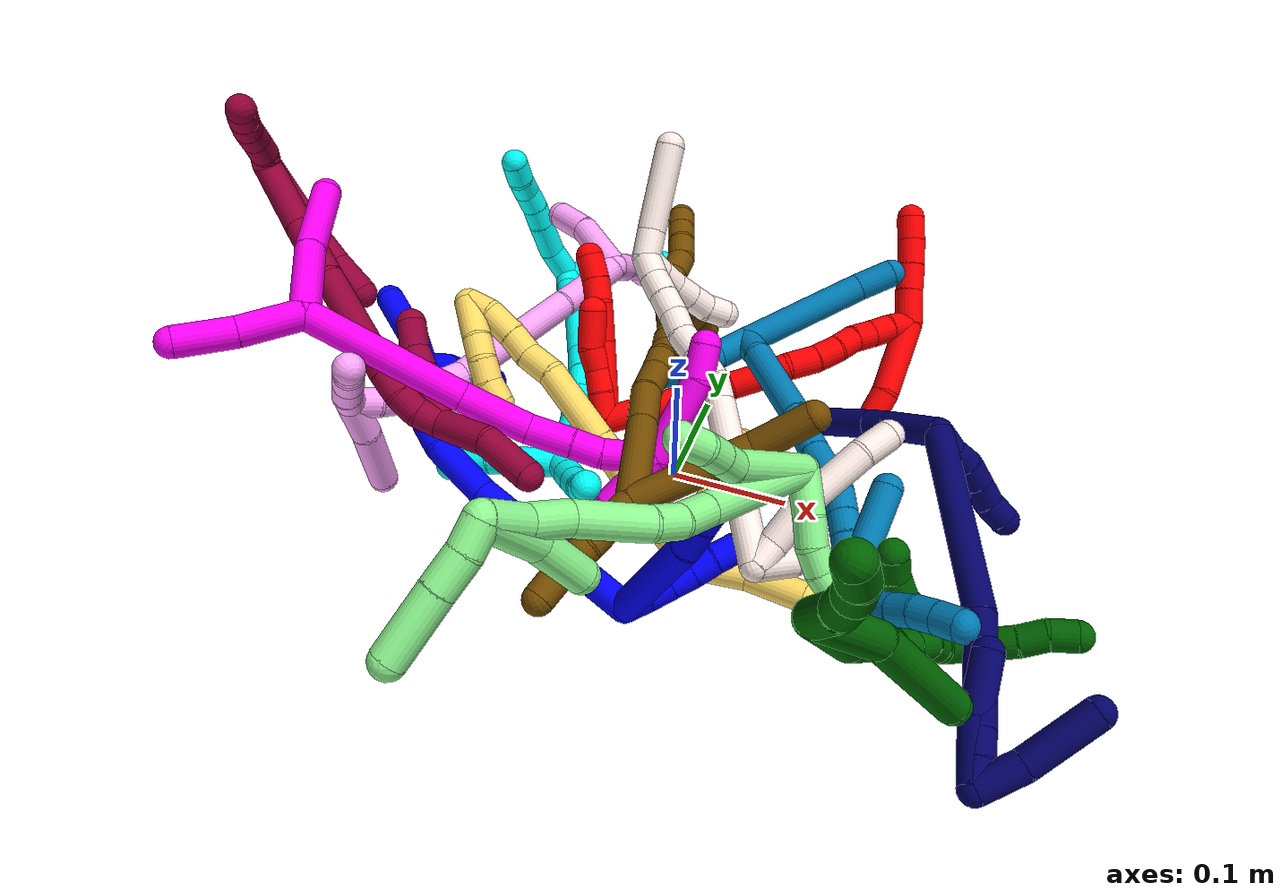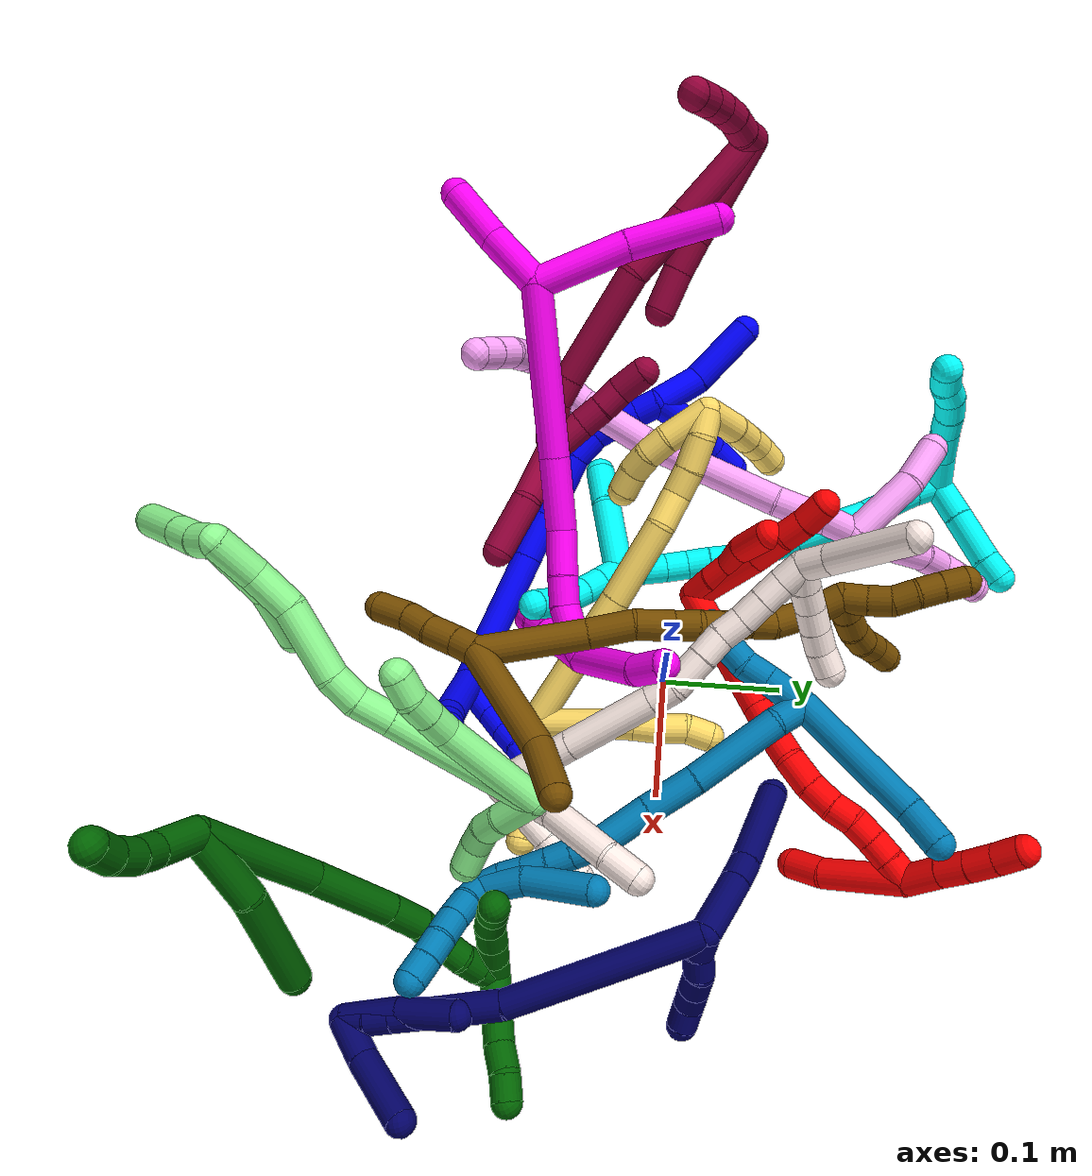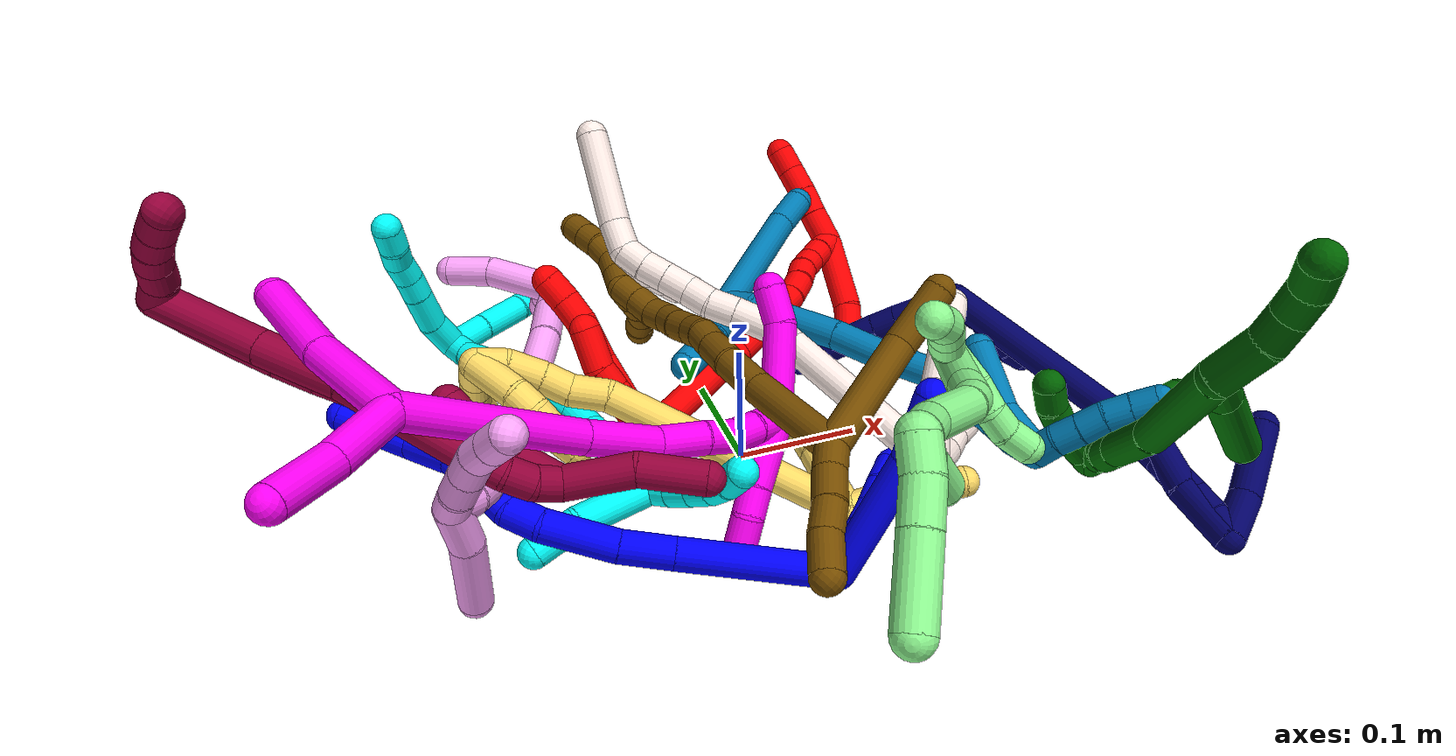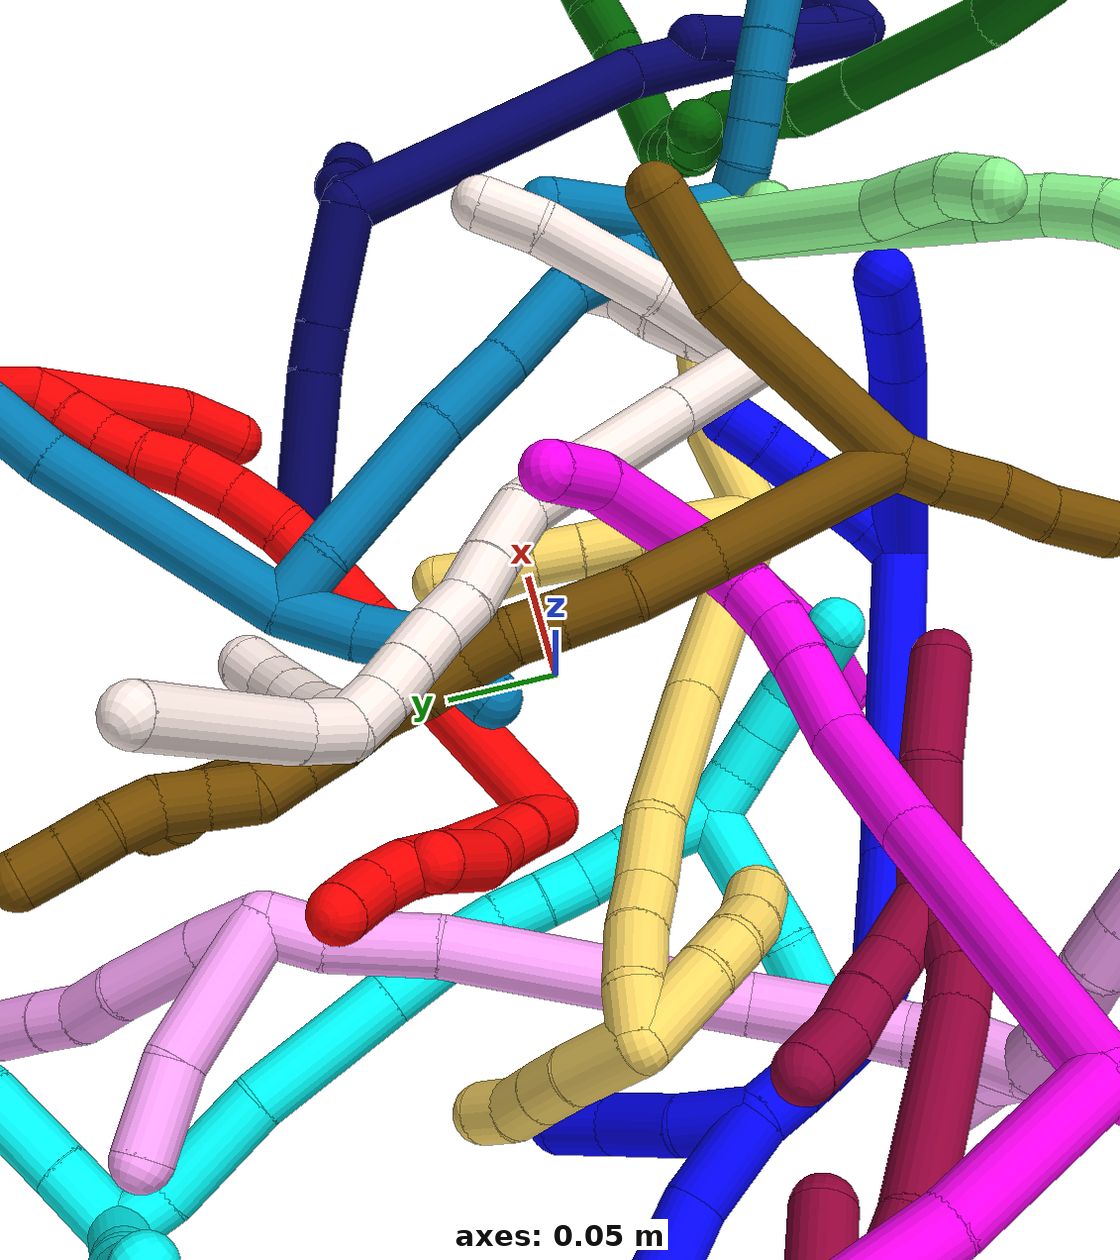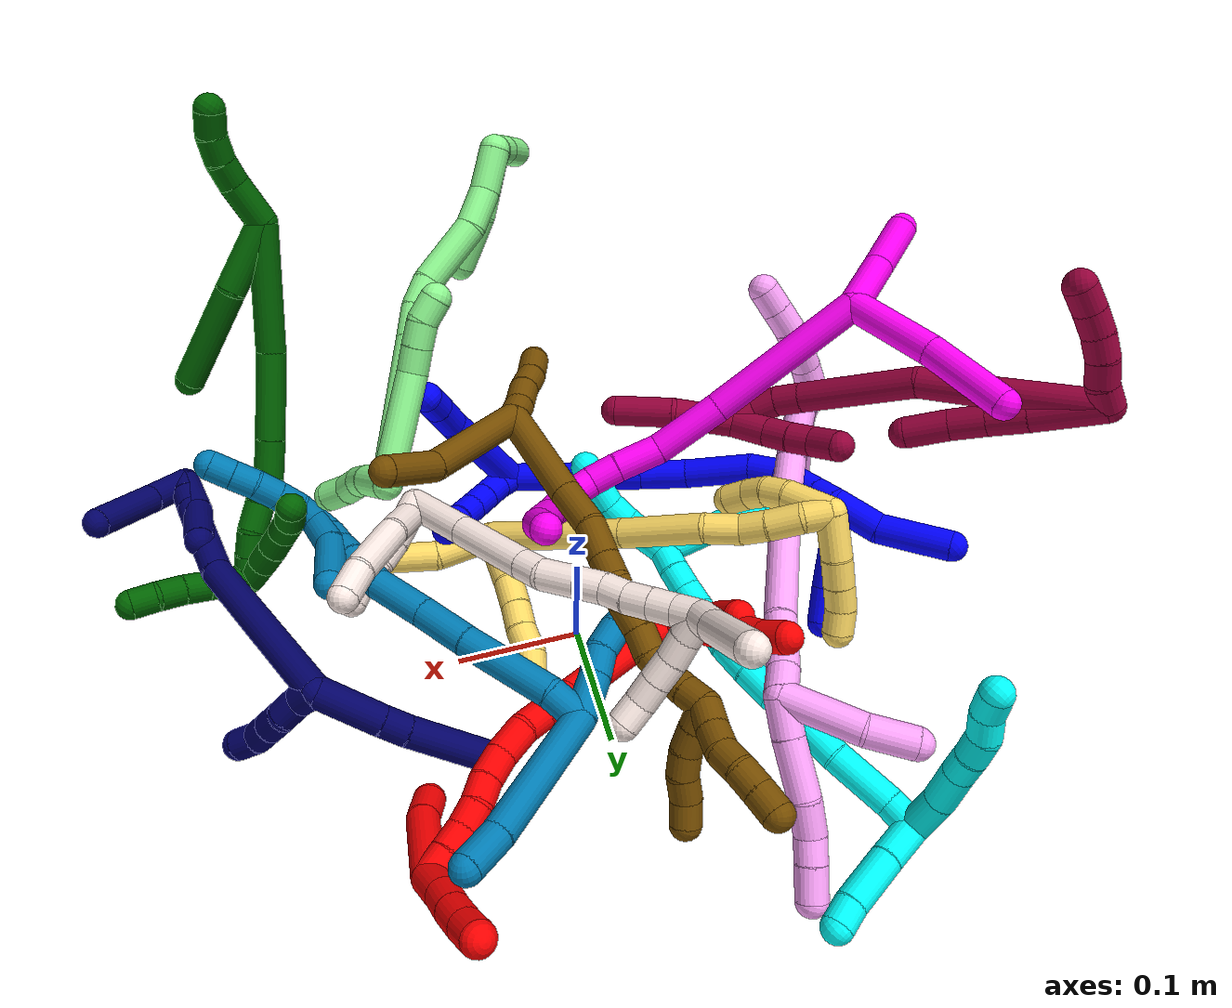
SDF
<sdf version="1.7">
 <world name="default">
  <plugin name="TubeGeneratorPlugin" filename="libtube_generator_plugin.so"/>
  <model name="photoneo_s_sensor">
   <static>1</static>
   <pose>0 0 2 1.57079 1.57079 3.14159</pose>
   <link name="link">
    <inertial><mass>0.1</mass></inertial>
    <sensor name="sensor" type="depth">
     <update_rate>30</update_rate>
     <camera>
      <horizontal_fov>1.22</horizontal_fov>
      <image><width>1920</width><height>1200</height><format>B8G8R8</format></image>
      <clip><near>0.1</near><far>4</far></clip>
      <depth_camera><output>points</output></depth_camera>
     </camera>
     <plugin name="camera_plugin" filename="libgazebo_ros_depth_camera.so">
      <baseline>0.2</baseline>
      <alwaysOn>1</alwaysOn>
      <updateRate>0.0</updateRate>
      <cameraName>camera_ir</cameraName>
      <imageTopicName>/camera/color/image_raw</imageTopicName>
      <cameraInfoTopicName>/camera/color/camera_info</cameraInfoTopicName>
      <depthImageTopicName>/camera/depth/image_raw</depthImageTopicName>
      <depthImageCameraInfoTopicName>/camera/depth/camera_info</depthImageCameraInfoTopicName>
      <pointCloudTopicName>/camera/depth/points</pointCloudTopicName>
      <frameName>fr_optical</frameName>
      <pointCloudCutoff>0.1</pointCloudCutoff>
      <pointCloudCutoffMax>2.0</pointCloudCutoffMax>
      <distortionK1>0</distortionK1>
      <distortionK2>0</distortionK2>
      <distortionK3>0</distortionK3>
      <distortionT1>0</distortionT1>
      <distortionT2>0</distortionT2>
      <CxPrime>0</CxPrime>
      <Cx>0</Cx>
      <Cy>0</Cy>
      <focalLength>0</focalLength>
      <hackBaseline>0</hackBaseline>
     </plugin>
    </sensor>
   </link>
  </model>
  <gravity>0 0 -9.8</gravity>
  <magnetic_field>6e-06 2.3e-05 -4.2e-05</magnetic_field>
  <atmosphere type="adiabatic"/>
  <physics name="default_physics" default="0" type="ode">
   <max_step_size>0.003</max_step_size>
   <real_time_factor>1</real_time_factor>
   <real_time_update_rate>1000</real_time_update_rate>
   <max_contacts>10000</max_contacts>
   <ode>
    <solver>
     <type>quick</type>
     <iters>100</iters>
     <sor>1.3</sor>
     <use_dynamic_moi_rescaling>0</use_dynamic_moi_rescaling>
    </solver>
    <constraints>
     <contact_max_correcting_vel>0</contact_max_correcting_vel>
     <contact_surface_layer>0.001</contact_surface_layer>
     <cfm>0</cfm>
     <erp>0.2</erp>
    </constraints>
   </ode>
  </physics>
  <scene><ambient>0.4 0.4 0.4 1</ambient><background>0.7 0.7 0.7 1</background><shadows>0</shadows></scene>
  <audio><device>default</device></audio>
  <spherical_coordinates>
   <surface_model>EARTH_WGS84</surface_model>
   <latitude_deg>0</latitude_deg>
   <longitude_deg>0</longitude_deg>
   <elevation>0</elevation>
   <heading_deg>0</heading_deg>
  </spherical_coordinates>
  <model name="bin">
   <static>1</static>
   <link name="bottom">
    <collision name="collision-bottom">
     <pose>0 0 -0.01 0 -0 0</pose>
     <geometry><box><size>0.8 0.6 0.02</size></box></geometry>
     <surface>
      <friction><ode><mu>100</mu><mu2>100</mu2></ode></friction>
      <contact><collide_bitmask>65535</collide_bitmask></contact>
     </surface>
    </collision>
   </link>
   <link name="west_wall">
    <collision name="collision-west_wall">
     <pose>-0.41 0 0.1 0 -0 0</pose>
     <geometry><box><size>0.02 0.6 0.2</size></box></geometry>
     <surface>
      <friction><ode><mu>100</mu><mu2>100</mu2></ode></friction>
      <contact><collide_bitmask>65535</collide_bitmask></contact>
     </surface>
    </collision>
   </link>
   <link name="east_wall">
    <collision name="collision-east_wall">
     <pose>0.41 0 0.1 0 -0 0</pose>
     <geometry><box><size>0.02 0.6 0.2</size></box></geometry>
     <surface>
      <friction><ode><mu>100</mu><mu2>100</mu2></ode></friction>
      <contact><collide_bitmask>65535</collide_bitmask></contact>
     </surface>
    </collision>
   </link>
   <link name="south_wall">
    <collision name="collision-south_wall">
     <pose>0 -0.31 0.1 0 -0 0</pose>
     <geometry><box><size>0.8 0.02 0.2</size></box></geometry>
     <surface>
      <friction><ode><mu>100</mu><mu2>100</mu2></ode></friction>
      <contact><collide_bitmask>65535</collide_bitmask></contact>
     </surface>
    </collision>
   </link>
   <link name="north_wall">
    <collision name="collision-north_wall">
     <pose>0 0.31 0.1 0 -0 0</pose>
     <geometry><box><size>0.8 0.02 0.2</size></box></geometry>
     <surface>
      <friction><ode><mu>100</mu><mu2>100</mu2></ode></friction>
      <contact><collide_bitmask>65535</collide_bitmask></contact>
     </surface>
    </collision>
   </link>
  </model>
  <model name="1">
   <static>0</static>
   <link name="1">
    <collision name="collision-cylinder-e_1_2_8">
     <pose>0.029746 0.015018 0.037684 -0.379226 0.632704 -0.125482</pose>
     <geometry><cylinder><radius>0.0125</radius><length>0.100608</length></cylinder></geometry>
     <surface>
      <friction><ode><mu>1.16</mu><mu2>1.16</mu2><slip1>0</slip1><slip2>0</slip2></ode></friction>
      <contact><ode><kp>1e+06</kp><kd>1</kd><max_vel>0</max_vel><min_depth>0.001</min_depth></ode></contact>
     </surface>
    </collision>
    <visual name="visual-cylinder-e_1_2_8">
     <pose>0.029746 0.015018 0.037684 -0.379226 0.632704 -0.125482</pose>
     <geometry><cylinder><radius>0.0125</radius><length>0.100608</length></cylinder></geometry>
     <material><ambient>0 0 1 1</ambient></material>
    </visual>
    <collision name="collision-cylinder-e_2_8_9">
     <pose>0.068793 0.035911 0.084525 -0.570487 0.707347 -0.215687</pose>
     <geometry><cylinder><radius>0.0125</radius><length>0.028627</length></cylinder></geometry>
     <surface>
      <friction><ode><mu>1.16</mu><mu2>1.16</mu2><slip1>0</slip1><slip2>0</slip2></ode></friction>
      <contact><ode><kp>1e+06</kp><kd>1</kd><max_vel>0</max_vel><min_depth>0.001</min_depth></ode></contact>
     </surface>
    </collision>
    <visual name="visual-cylinder-e_2_8_9">
     <pose>0.068793 0.035911 0.084525 -0.570487 0.707347 -0.215687</pose>
     <geometry><cylinder><radius>0.0125</radius><length>0.028627</length></cylinder></geometry>
     <material><ambient>0 0 1 1</ambient></material>
    </visual>
    <collision name="collision-cylinder-e_3_9_6">
     <pose>0.085267 0.045926 0.099945 -0.584009 0.762548 -0.239856</pose>
     <geometry><cylinder><radius>0.0125</radius><length>0.020765</length></cylinder></geometry>
     <surface>
      <friction><ode><mu>1.16</mu><mu2>1.16</mu2><slip1>0</slip1><slip2>0</slip2></ode></friction>
      <contact><ode><kp>1e+06</kp><kd>1</kd><max_vel>0</max_vel><min_depth>0.001</min_depth></ode></contact>
     </surface>
    </collision>
    <visual name="visual-cylinder-e_3_9_6">
     <pose>0.085267 0.045926 0.099945 -0.584009 0.762548 -0.239856</pose>
     <geometry><cylinder><radius>0.0125</radius><length>0.020765</length></cylinder></geometry>
     <material><ambient>0 0 1 1</ambient></material>
    </visual>
    <collision name="collision-cylinder-e_1_2_10">
     <pose>0.009459 -0.002394 0.002192 0.829561 1.24021 0.60927</pose>
     <geometry><cylinder><radius>0.0125</radius><length>0.02</length></cylinder></geometry>
     <surface>
      <friction><ode><mu>1.16</mu><mu2>1.16</mu2><slip1>0</slip1><slip2>0</slip2></ode></friction>
      <contact><ode><kp>1e+06</kp><kd>1</kd><max_vel>0</max_vel><min_depth>0.001</min_depth></ode></contact>
     </surface>
    </collision>
    <visual name="visual-cylinder-e_1_2_10">
     <pose>0.009459 -0.002394 0.002192 0.829561 1.24021 0.60927</pose>
     <geometry><cylinder><radius>0.0125</radius><length>0.02</length></cylinder></geometry>
     <material><ambient>0 0 1 1</ambient></material>
    </visual>
    <collision name="collision-cylinder-e_2_10_11">
     <pose>0.028563 -0.007206 0.005438 1.15938 1.30393 0.926908</pose>
     <geometry><cylinder><radius>0.0125</radius><length>0.02</length></cylinder></geometry>
     <surface>
      <friction><ode><mu>1.16</mu><mu2>1.16</mu2><slip1>0</slip1><slip2>0</slip2></ode></friction>
      <contact><ode><kp>1e+06</kp><kd>1</kd><max_vel>0</max_vel><min_depth>0.001</min_depth></ode></contact>
     </surface>
    </collision>
    <visual name="visual-cylinder-e_2_10_11">
     <pose>0.028563 -0.007206 0.005438 1.15938 1.30393 0.926908</pose>
     <geometry><cylinder><radius>0.0125</radius><length>0.02</length></cylinder></geometry>
     <material><ambient>0 0 1 1</ambient></material>
    </visual>
    <collision name="collision-cylinder-e_3_11_12">
     <pose>0.047828 -0.012113 0.007623 1.14478 1.29376 0.905856</pose>
     <geometry><cylinder><radius>0.0125</radius><length>0.02</length></cylinder></geometry>
     <surface>
      <friction><ode><mu>1.16</mu><mu2>1.16</mu2><slip1>0</slip1><slip2>0</slip2></ode></friction>
      <contact><ode><kp>1e+06</kp><kd>1</kd><max_vel>0</max_vel><min_depth>0.001</min_depth></ode></contact>
     </surface>
    </collision>
    <visual name="visual-cylinder-e_3_11_12">
     <pose>0.047828 -0.012113 0.007623 1.14478 1.29376 0.905856</pose>
     <geometry><cylinder><radius>0.0125</radius><length>0.02</length></cylinder></geometry>
     <material><ambient>0 0 1 1</ambient></material>
    </visual>
    <collision name="collision-cylinder-e_4_12_13">
     <pose>0.067239 -0.016163 0.010045 0.878826 1.36688 0.73119</pose>
     <geometry><cylinder><radius>0.0125</radius><length>0.02</length></cylinder></geometry>
     <surface>
      <friction><ode><mu>1.16</mu><mu2>1.16</mu2><slip1>0</slip1><slip2>0</slip2></ode></friction>
      <contact><ode><kp>1e+06</kp><kd>1</kd><max_vel>0</max_vel><min_depth>0.001</min_depth></ode></contact>
     </surface>
    </collision>
    <visual name="visual-cylinder-e_4_12_13">
     <pose>0.067239 -0.016163 0.010045 0.878826 1.36688 0.73119</pose>
     <geometry><cylinder><radius>0.0125</radius><length>0.02</length></cylinder></geometry>
     <material><ambient>0 0 1 1</ambient></material>
    </visual>
    <collision name="collision-cylinder-e_5_13_5">
     <pose>0.086682 -0.020245 0.012052 1.29482 1.30553 1.04835</pose>
     <geometry><cylinder><radius>0.0125</radius><length>0.02</length></cylinder></geometry>
     <surface>
      <friction><ode><mu>1.16</mu><mu2>1.16</mu2><slip1>0</slip1><slip2>0</slip2></ode></friction>
      <contact><ode><kp>1e+06</kp><kd>1</kd><max_vel>0</max_vel><min_depth>0.001</min_depth></ode></contact>
     </surface>
    </collision>
    <visual name="visual-cylinder-e_5_13_5">
     <pose>0.086682 -0.020245 0.012052 1.29482 1.30553 1.04835</pose>
     <geometry><cylinder><radius>0.0125</radius><length>0.02</length></cylinder></geometry>
     <material><ambient>0 0 1 1</ambient></material>
    </visual>
    <collision name="collision-cylinder-e_1_2_14">
     <pose>-0.007711 0.0455 -0.036403 -2.24558 -0.131569 0.272457</pose>
     <geometry><cylinder><radius>0.0125</radius><length>0.117556</length></cylinder></geometry>
     <surface>
      <friction><ode><mu>1.16</mu><mu2>1.16</mu2><slip1>0</slip1><slip2>0</slip2></ode></friction>
      <contact><ode><kp>1e+06</kp><kd>1</kd><max_vel>0</max_vel><min_depth>0.001</min_depth></ode></contact>
     </surface>
    </collision>
    <visual name="visual-cylinder-e_1_2_14">
     <pose>-0.007711 0.0455 -0.036403 -2.24558 -0.131569 0.272457</pose>
     <geometry><cylinder><radius>0.0125</radius><length>0.117556</length></cylinder></geometry>
     <material><ambient>0 0 1 1</ambient></material>
    </visual>
    <collision name="collision-cylinder-e_2_14_15">
     <pose>-0.017989 0.106751 -0.084904 -2.22578 -0.12853 0.259681</pose>
     <geometry><cylinder><radius>0.0125</radius><length>0.040054</length></cylinder></geometry>
     <surface>
      <friction><ode><mu>1.16</mu><mu2>1.16</mu2><slip1>0</slip1><slip2>0</slip2></ode></friction>
      <contact><ode><kp>1e+06</kp><kd>1</kd><max_vel>0</max_vel><min_depth>0.001</min_depth></ode></contact>
     </surface>
    </collision>
    <visual name="visual-cylinder-e_2_14_15">
     <pose>-0.017989 0.106751 -0.084904 -2.22578 -0.12853 0.259681</pose>
     <geometry><cylinder><radius>0.0125</radius><length>0.040054</length></cylinder></geometry>
     <material><ambient>0 0 1 1</ambient></material>
    </visual>
    <collision name="collision-cylinder-e_3_15_16">
     <pose>-0.021126 0.146545 -0.111618 -2.11701 -0.02024 0.035988</pose>
     <geometry><cylinder><radius>0.0125</radius><length>0.056286</length></cylinder></geometry>
     <surface>
      <friction><ode><mu>1.16</mu><mu2>1.16</mu2><slip1>0</slip1><slip2>0</slip2></ode></friction>
      <contact><ode><kp>1e+06</kp><kd>1</kd><max_vel>0</max_vel><min_depth>0.001</min_depth></ode></contact>
     </surface>
    </collision>
    <visual name="visual-cylinder-e_3_15_16">
     <pose>-0.021126 0.146545 -0.111618 -2.11701 -0.02024 0.035988</pose>
     <geometry><cylinder><radius>0.0125</radius><length>0.056286</length></cylinder></geometry>
     <material><ambient>0 0 1 1</ambient></material>
    </visual>
    <collision name="collision-cylinder-e_4_16_17">
     <pose>-0.019064 0.17997 -0.134594 -2.29864 0.206395 -0.454029</pose>
     <geometry><cylinder><radius>0.0125</radius><length>0.025677</length></cylinder></geometry>
     <surface>
      <friction><ode><mu>1.16</mu><mu2>1.16</mu2><slip1>0</slip1><slip2>0</slip2></ode></friction>
      <contact><ode><kp>1e+06</kp><kd>1</kd><max_vel>0</max_vel><min_depth>0.001</min_depth></ode></contact>
     </surface>
    </collision>
    <visual name="visual-cylinder-e_4_16_17">
     <pose>-0.019064 0.17997 -0.134594 -2.29864 0.206395 -0.454029</pose>
     <geometry><cylinder><radius>0.0125</radius><length>0.025677</length></cylinder></geometry>
     <material><ambient>0 0 1 1</ambient></material>
    </visual>
    <collision name="collision-cylinder-e_5_17_18">
     <pose>-0.011213 0.195303 -0.149203 -2.38066 0.544017 -1.21793</pose>
     <geometry><cylinder><radius>0.0125</radius><length>0.020171</length></cylinder></geometry>
     <surface>
      <friction><ode><mu>1.16</mu><mu2>1.16</mu2><slip1>0</slip1><slip2>0</slip2></ode></friction>
      <contact><ode><kp>1e+06</kp><kd>1</kd><max_vel>0</max_vel><min_depth>0.001</min_depth></ode></contact>
     </surface>
    </collision>
    <visual name="visual-cylinder-e_5_17_18">
     <pose>-0.011213 0.195303 -0.149203 -2.38066 0.544017 -1.21793</pose>
     <geometry><cylinder><radius>0.0125</radius><length>0.020171</length></cylinder></geometry>
     <material><ambient>0 0 1 1</ambient></material>
    </visual>
    <collision name="collision-cylinder-e_6_18_19">
     <pose>-0.000766 0.206595 -0.162138 -2.46752 0.548395 -1.3528</pose>
     <geometry><cylinder><radius>0.0125</radius><length>0.020055</length></cylinder></geometry>
     <surface>
      <friction><ode><mu>1.16</mu><mu2>1.16</mu2><slip1>0</slip1><slip2>0</slip2></ode></friction>
      <contact><ode><kp>1e+06</kp><kd>1</kd><max_vel>0</max_vel><min_depth>0.001</min_depth></ode></contact>
     </surface>
    </collision>
    <visual name="visual-cylinder-e_6_18_19">
     <pose>-0.000766 0.206595 -0.162138 -2.46752 0.548395 -1.3528</pose>
     <geometry><cylinder><radius>0.0125</radius><length>0.020055</length></cylinder></geometry>
     <material><ambient>0 0 1 1</ambient></material>
    </visual>
    <collision name="collision-cylinder-e_7_19_1">
     <pose>0.010057 0.217377 -0.175236 -2.43804 0.587067 -1.37782</pose>
     <geometry><cylinder><radius>0.0125</radius><length>0.020203</length></cylinder></geometry>
     <surface>
      <friction><ode><mu>1.16</mu><mu2>1.16</mu2><slip1>0</slip1><slip2>0</slip2></ode></friction>
      <contact><ode><kp>1e+06</kp><kd>1</kd><max_vel>0</max_vel><min_depth>0.001</min_depth></ode></contact>
     </surface>
    </collision>
    <visual name="visual-cylinder-e_7_19_1">
     <pose>0.010057 0.217377 -0.175236 -2.43804 0.587067 -1.37782</pose>
     <geometry><cylinder><radius>0.0125</radius><length>0.020203</length></cylinder></geometry>
     <material><ambient>0 0 1 1</ambient></material>
    </visual>
    <collision name="collision-cylinder-e_1_1_20">
     <pose>0.023789 0.214285 -0.193499 2.51752 0.508384 1.3561</pose>
     <geometry><cylinder><radius>0.0125</radius><length>0.033431</length></cylinder></geometry>
     <surface>
      <friction><ode><mu>1.16</mu><mu2>1.16</mu2><slip1>0</slip1><slip2>0</slip2></ode></friction>
      <contact><ode><kp>1e+06</kp><kd>1</kd><max_vel>0</max_vel><min_depth>0.001</min_depth></ode></contact>
     </surface>
    </collision>
    <visual name="visual-cylinder-e_1_1_20">
     <pose>0.023789 0.214285 -0.193499 2.51752 0.508384 1.3561</pose>
     <geometry><cylinder><radius>0.0125</radius><length>0.033431</length></cylinder></geometry>
     <material><ambient>0 0 1 1</ambient></material>
    </visual>
    <collision name="collision-cylinder-e_2_20_21">
     <pose>0.038525 0.192953 -0.217325 2.32302 0.360084 0.794563</pose>
     <geometry><cylinder><radius>0.0125</radius><length>0.037461</length></cylinder></geometry>
     <surface>
      <friction><ode><mu>1.16</mu><mu2>1.16</mu2><slip1>0</slip1><slip2>0</slip2></ode></friction>
      <contact><ode><kp>1e+06</kp><kd>1</kd><max_vel>0</max_vel><min_depth>0.001</min_depth></ode></contact>
     </surface>
    </collision>
    <visual name="visual-cylinder-e_2_20_21">
     <pose>0.038525 0.192953 -0.217325 2.32302 0.360084 0.794563</pose>
     <geometry><cylinder><radius>0.0125</radius><length>0.037461</length></cylinder></geometry>
     <material><ambient>0 0 1 1</ambient></material>
    </visual>
    <collision name="collision-cylinder-e_3_21_4">
     <pose>0.051393 0.170989 -0.238711 2.36933 0.445233 1.01612</pose>
     <geometry><cylinder><radius>0.0125</radius><length>0.029108</length></cylinder></geometry>
     <surface>
      <friction><ode><mu>1.16</mu><mu2>1.16</mu2><slip1>0</slip1><slip2>0</slip2></ode></friction>
      <contact><ode><kp>1e+06</kp><kd>1</kd><max_vel>0</max_vel><min_depth>0.001</min_depth></ode></contact>
     </surface>
    </collision>
    <visual name="visual-cylinder-e_3_21_4">
     <pose>0.051393 0.170989 -0.238711 2.36933 0.445233 1.01612</pose>
     <geometry><cylinder><radius>0.0125</radius><length>0.029108</length></cylinder></geometry>
     <material><ambient>0 0 1 1</ambient></material>
    </visual>
    <collision name="collision-cylinder-e_1_1_22">
     <pose>0.021156 0.231738 -0.199214 -2.67165 0.272402 -1.03988</pose>
     <geometry><cylinder><radius>0.0125</radius><length>0.040909</length></cylinder></geometry>
     <surface>
      <friction><ode><mu>1.16</mu><mu2>1.16</mu2><slip1>0</slip1><slip2>0</slip2></ode></friction>
      <contact><ode><kp>1e+06</kp><kd>1</kd><max_vel>0</max_vel><min_depth>0.001</min_depth></ode></contact>
     </surface>
    </collision>
    <visual name="visual-cylinder-e_1_1_22">
     <pose>0.021156 0.231738 -0.199214 -2.67165 0.272402 -1.03988</pose>
     <geometry><cylinder><radius>0.0125</radius><length>0.040909</length></cylinder></geometry>
     <material><ambient>0 0 1 1</ambient></material>
    </visual>
    <collision name="collision-cylinder-e_2_22_3">
     <pose>0.03207 0.261069 -0.237446 -2.36246 0.184166 -0.442495</pose>
     <geometry><cylinder><radius>0.0125</radius><length>0.059091</length></cylinder></geometry>
     <surface>
      <friction><ode><mu>1.16</mu><mu2>1.16</mu2><slip1>0</slip1><slip2>0</slip2></ode></friction>
      <contact><ode><kp>1e+06</kp><kd>1</kd><max_vel>0</max_vel><min_depth>0.001</min_depth></ode></contact>
     </surface>
    </collision>
    <visual name="visual-cylinder-e_2_22_3">
     <pose>0.03207 0.261069 -0.237446 -2.36246 0.184166 -0.442495</pose>
     <geometry><cylinder><radius>0.0125</radius><length>0.059091</length></cylinder></geometry>
     <material><ambient>0 0 1 1</ambient></material>
    </visual>
    <collision name="collision-sphere-3">
     <pose>0.03748 0.281478 -0.258112 0 -0 0</pose>
     <geometry><sphere><radius>0.0125</radius></sphere></geometry>
     <surface>
      <friction><ode><mu>1.16</mu><mu2>1.16</mu2><slip1>0</slip1><slip2>0</slip2></ode></friction>
      <contact><ode><kp>1e+06</kp><kd>1</kd><max_vel>0</max_vel><min_depth>0.001</min_depth></ode></contact>
     </surface>
    </collision>
    <visual name="visual-sphere-3">
     <pose>0.03748 0.281478 -0.258112 0 -0 0</pose>
     <geometry><sphere><radius>0.0125</radius></sphere></geometry>
     <material><ambient>0 0 1 1</ambient></material>
    </visual>
    <collision name="collision-sphere-22">
     <pose>0.026659 0.24066 -0.216779 0 -0 0</pose>
     <geometry><sphere><radius>0.0125</radius></sphere></geometry>
     <surface>
      <friction><ode><mu>1.16</mu><mu2>1.16</mu2><slip1>0</slip1><slip2>0</slip2></ode></friction>
      <contact><ode><kp>1e+06</kp><kd>1</kd><max_vel>0</max_vel><min_depth>0.001</min_depth></ode></contact>
     </surface>
    </collision>
    <visual name="visual-sphere-22">
     <pose>0.026659 0.24066 -0.216779 0 -0 0</pose>
     <geometry><sphere><radius>0.0125</radius></sphere></geometry>
     <material><ambient>0 0 1 1</ambient></material>
    </visual>
    <collision name="collision-sphere-4">
     <pose>0.057661 0.161824 -0.24812 0 -0 0</pose>
     <geometry><sphere><radius>0.0125</radius></sphere></geometry>
     <surface>
      <friction><ode><mu>1.16</mu><mu2>1.16</mu2><slip1>0</slip1><slip2>0</slip2></ode></friction>
      <contact><ode><kp>1e+06</kp><kd>1</kd><max_vel>0</max_vel><min_depth>0.001</min_depth></ode></contact>
     </surface>
    </collision>
    <visual name="visual-sphere-4">
     <pose>0.057661 0.161824 -0.24812 0 -0 0</pose>
     <geometry><sphere><radius>0.0125</radius></sphere></geometry>
     <material><ambient>0 0 1 1</ambient></material>
    </visual>
    <collision name="collision-sphere-21">
     <pose>0.045125 0.180154 -0.229302 0 -0 0</pose>
     <geometry><sphere><radius>0.0125</radius></sphere></geometry>
     <surface>
      <friction><ode><mu>1.16</mu><mu2>1.16</mu2><slip1>0</slip1><slip2>0</slip2></ode></friction>
      <contact><ode><kp>1e+06</kp><kd>1</kd><max_vel>0</max_vel><min_depth>0.001</min_depth></ode></contact>
     </surface>
    </collision>
    <visual name="visual-sphere-21">
     <pose>0.045125 0.180154 -0.229302 0 -0 0</pose>
     <geometry><sphere><radius>0.0125</radius></sphere></geometry>
     <material><ambient>0 0 1 1</ambient></material>
    </visual>
    <collision name="collision-sphere-20">
     <pose>0.031926 0.205753 -0.205348 0 -0 0</pose>
     <geometry><sphere><radius>0.0125</radius></sphere></geometry>
     <surface>
      <friction><ode><mu>1.16</mu><mu2>1.16</mu2><slip1>0</slip1><slip2>0</slip2></ode></friction>
      <contact><ode><kp>1e+06</kp><kd>1</kd><max_vel>0</max_vel><min_depth>0.001</min_depth></ode></contact>
     </surface>
    </collision>
    <visual name="visual-sphere-20">
     <pose>0.031926 0.205753 -0.205348 0 -0 0</pose>
     <geometry><sphere><radius>0.0125</radius></sphere></geometry>
     <material><ambient>0 0 1 1</ambient></material>
    </visual>
    <collision name="collision-sphere-11">
     <pose>0.038209 -0.009623 0.006493 0 -0 0</pose>
     <geometry><sphere><radius>0.0125</radius></sphere></geometry>
     <surface>
      <friction><ode><mu>1.16</mu><mu2>1.16</mu2><slip1>0</slip1><slip2>0</slip2></ode></friction>
      <contact><ode><kp>1e+06</kp><kd>1</kd><max_vel>0</max_vel><min_depth>0.001</min_depth></ode></contact>
     </surface>
    </collision>
    <visual name="visual-sphere-11">
     <pose>0.038209 -0.009623 0.006493 0 -0 0</pose>
     <geometry><sphere><radius>0.0125</radius></sphere></geometry>
     <material><ambient>0 0 1 1</ambient></material>
    </visual>
    <collision name="collision-sphere-10">
     <pose>0.018917 -0.004789 0.004383 0 -0 0</pose>
     <geometry><sphere><radius>0.0125</radius></sphere></geometry>
     <surface>
      <friction><ode><mu>1.16</mu><mu2>1.16</mu2><slip1>0</slip1><slip2>0</slip2></ode></friction>
      <contact><ode><kp>1e+06</kp><kd>1</kd><max_vel>0</max_vel><min_depth>0.001</min_depth></ode></contact>
     </surface>
    </collision>
    <visual name="visual-sphere-10">
     <pose>0.018917 -0.004789 0.004383 0 -0 0</pose>
     <geometry><sphere><radius>0.0125</radius></sphere></geometry>
     <material><ambient>0 0 1 1</ambient></material>
    </visual>
    <collision name="collision-sphere-6">
     <pose>0.092438 0.050065 0.106208 0 -0 0</pose>
     <geometry><sphere><radius>0.0125</radius></sphere></geometry>
     <surface>
      <friction><ode><mu>1.16</mu><mu2>1.16</mu2><slip1>0</slip1><slip2>0</slip2></ode></friction>
      <contact><ode><kp>1e+06</kp><kd>1</kd><max_vel>0</max_vel><min_depth>0.001</min_depth></ode></contact>
     </surface>
    </collision>
    <visual name="visual-sphere-6">
     <pose>0.092438 0.050065 0.106208 0 -0 0</pose>
     <geometry><sphere><radius>0.0125</radius></sphere></geometry>
     <material><ambient>0 0 1 1</ambient></material>
    </visual>
    <collision name="collision-sphere-9">
     <pose>0.078095 0.041787 0.093682 0 -0 0</pose>
     <geometry><sphere><radius>0.0125</radius></sphere></geometry>
     <surface>
      <friction><ode><mu>1.16</mu><mu2>1.16</mu2><slip1>0</slip1><slip2>0</slip2></ode></friction>
      <contact><ode><kp>1e+06</kp><kd>1</kd><max_vel>0</max_vel><min_depth>0.001</min_depth></ode></contact>
     </surface>
    </collision>
    <visual name="visual-sphere-9">
     <pose>0.078095 0.041787 0.093682 0 -0 0</pose>
     <geometry><sphere><radius>0.0125</radius></sphere></geometry>
     <material><ambient>0 0 1 1</ambient></material>
    </visual>
    <collision name="collision-sphere-2">
     <geometry><sphere><radius>0.0125</radius></sphere></geometry>
     <surface>
      <friction><ode><mu>1.16</mu><mu2>1.16</mu2><slip1>0</slip1><slip2>0</slip2></ode></friction>
      <contact><ode><kp>1e+06</kp><kd>1</kd><max_vel>0</max_vel><min_depth>0.001</min_depth></ode></contact>
     </surface>
    </collision>
    <visual name="visual-sphere-2">
     <geometry><sphere><radius>0.0125</radius></sphere></geometry>
     <material><ambient>0 0 1 1</ambient></material>
    </visual>
    <collision name="collision-sphere-19">
     <pose>0.004462 0.211936 -0.168823 0 -0 0</pose>
     <geometry><sphere><radius>0.0125</radius></sphere></geometry>
     <surface>
      <friction><ode><mu>1.16</mu><mu2>1.16</mu2><slip1>0</slip1><slip2>0</slip2></ode></friction>
      <contact><ode><kp>1e+06</kp><kd>1</kd><max_vel>0</max_vel><min_depth>0.001</min_depth></ode></contact>
     </surface>
    </collision>
    <visual name="visual-sphere-19">
     <pose>0.004462 0.211936 -0.168823 0 -0 0</pose>
     <geometry><sphere><radius>0.0125</radius></sphere></geometry>
     <material><ambient>0 0 1 1</ambient></material>
    </visual>
    <collision name="collision-sphere-8">
     <pose>0.059492 0.030036 0.075369 0 -0 0</pose>
     <geometry><sphere><radius>0.0125</radius></sphere></geometry>
     <surface>
      <friction><ode><mu>1.16</mu><mu2>1.16</mu2><slip1>0</slip1><slip2>0</slip2></ode></friction>
      <contact><ode><kp>1e+06</kp><kd>1</kd><max_vel>0</max_vel><min_depth>0.001</min_depth></ode></contact>
     </surface>
    </collision>
    <visual name="visual-sphere-8">
     <pose>0.059492 0.030036 0.075369 0 -0 0</pose>
     <geometry><sphere><radius>0.0125</radius></sphere></geometry>
     <material><ambient>0 0 1 1</ambient></material>
    </visual>
    <collision name="collision-sphere-12">
     <pose>0.057446 -0.014604 0.008753 0 -0 0</pose>
     <geometry><sphere><radius>0.0125</radius></sphere></geometry>
     <surface>
      <friction><ode><mu>1.16</mu><mu2>1.16</mu2><slip1>0</slip1><slip2>0</slip2></ode></friction>
      <contact><ode><kp>1e+06</kp><kd>1</kd><max_vel>0</max_vel><min_depth>0.001</min_depth></ode></contact>
     </surface>
    </collision>
    <visual name="visual-sphere-12">
     <pose>0.057446 -0.014604 0.008753 0 -0 0</pose>
     <geometry><sphere><radius>0.0125</radius></sphere></geometry>
     <material><ambient>0 0 1 1</ambient></material>
    </visual>
    <collision name="collision-sphere-13">
     <pose>0.077032 -0.017723 0.011337 0 -0 0</pose>
     <geometry><sphere><radius>0.0125</radius></sphere></geometry>
     <surface>
      <friction><ode><mu>1.16</mu><mu2>1.16</mu2><slip1>0</slip1><slip2>0</slip2></ode></friction>
      <contact><ode><kp>1e+06</kp><kd>1</kd><max_vel>0</max_vel><min_depth>0.001</min_depth></ode></contact>
     </surface>
    </collision>
    <visual name="visual-sphere-13">
     <pose>0.077032 -0.017723 0.011337 0 -0 0</pose>
     <geometry><sphere><radius>0.0125</radius></sphere></geometry>
     <material><ambient>0 0 1 1</ambient></material>
    </visual>
    <collision name="collision-sphere-5">
     <pose>0.096333 -0.022767 0.012766 0 -0 0</pose>
     <geometry><sphere><radius>0.0125</radius></sphere></geometry>
     <surface>
      <friction><ode><mu>1.16</mu><mu2>1.16</mu2><slip1>0</slip1><slip2>0</slip2></ode></friction>
      <contact><ode><kp>1e+06</kp><kd>1</kd><max_vel>0</max_vel><min_depth>0.001</min_depth></ode></contact>
     </surface>
    </collision>
    <visual name="visual-sphere-5">
     <pose>0.096333 -0.022767 0.012766 0 -0 0</pose>
     <geometry><sphere><radius>0.0125</radius></sphere></geometry>
     <material><ambient>0 0 1 1</ambient></material>
    </visual>
    <collision name="collision-sphere-14">
     <pose>-0.015422 0.090999 -0.072805 0 -0 0</pose>
     <geometry><sphere><radius>0.0125</radius></sphere></geometry>
     <surface>
      <friction><ode><mu>1.16</mu><mu2>1.16</mu2><slip1>0</slip1><slip2>0</slip2></ode></friction>
      <contact><ode><kp>1e+06</kp><kd>1</kd><max_vel>0</max_vel><min_depth>0.001</min_depth></ode></contact>
     </surface>
    </collision>
    <visual name="visual-sphere-14">
     <pose>-0.015422 0.090999 -0.072805 0 -0 0</pose>
     <geometry><sphere><radius>0.0125</radius></sphere></geometry>
     <material><ambient>0 0 1 1</ambient></material>
    </visual>
    <collision name="collision-sphere-15">
     <pose>-0.020556 0.122502 -0.097002 0 -0 0</pose>
     <geometry><sphere><radius>0.0125</radius></sphere></geometry>
     <surface>
      <friction><ode><mu>1.16</mu><mu2>1.16</mu2><slip1>0</slip1><slip2>0</slip2></ode></friction>
      <contact><ode><kp>1e+06</kp><kd>1</kd><max_vel>0</max_vel><min_depth>0.001</min_depth></ode></contact>
     </surface>
    </collision>
    <visual name="visual-sphere-15">
     <pose>-0.020556 0.122502 -0.097002 0 -0 0</pose>
     <geometry><sphere><radius>0.0125</radius></sphere></geometry>
     <material><ambient>0 0 1 1</ambient></material>
    </visual>
    <collision name="collision-sphere-16">
     <pose>-0.021695 0.170588 -0.126234 0 -0 0</pose>
     <geometry><sphere><radius>0.0125</radius></sphere></geometry>
     <surface>
      <friction><ode><mu>1.16</mu><mu2>1.16</mu2><slip1>0</slip1><slip2>0</slip2></ode></friction>
      <contact><ode><kp>1e+06</kp><kd>1</kd><max_vel>0</max_vel><min_depth>0.001</min_depth></ode></contact>
     </surface>
    </collision>
    <visual name="visual-sphere-16">
     <pose>-0.021695 0.170588 -0.126234 0 -0 0</pose>
     <geometry><sphere><radius>0.0125</radius></sphere></geometry>
     <material><ambient>0 0 1 1</ambient></material>
    </visual>
    <collision name="collision-sphere-17">
     <pose>-0.016433 0.189352 -0.142954 0 -0 0</pose>
     <geometry><sphere><radius>0.0125</radius></sphere></geometry>
     <surface>
      <friction><ode><mu>1.16</mu><mu2>1.16</mu2><slip1>0</slip1><slip2>0</slip2></ode></friction>
      <contact><ode><kp>1e+06</kp><kd>1</kd><max_vel>0</max_vel><min_depth>0.001</min_depth></ode></contact>
     </surface>
    </collision>
    <visual name="visual-sphere-17">
     <pose>-0.016433 0.189352 -0.142954 0 -0 0</pose>
     <geometry><sphere><radius>0.0125</radius></sphere></geometry>
     <material><ambient>0 0 1 1</ambient></material>
    </visual>
    <collision name="collision-sphere-18">
     <pose>-0.005993 0.201254 -0.155452 0 -0 0</pose>
     <geometry><sphere><radius>0.0125</radius></sphere></geometry>
     <surface>
      <friction><ode><mu>1.16</mu><mu2>1.16</mu2><slip1>0</slip1><slip2>0</slip2></ode></friction>
      <contact><ode><kp>1e+06</kp><kd>1</kd><max_vel>0</max_vel><min_depth>0.001</min_depth></ode></contact>
     </surface>
    </collision>
    <visual name="visual-sphere-18">
     <pose>-0.005993 0.201254 -0.155452 0 -0 0</pose>
     <geometry><sphere><radius>0.0125</radius></sphere></geometry>
     <material><ambient>0 0 1 1</ambient></material>
    </visual>
    <collision name="collision-sphere-1">
     <pose>0.015652 0.222817 -0.181649 0 -0 0</pose>
     <geometry><sphere><radius>0.0125</radius></sphere></geometry>
     <surface>
      <friction><ode><mu>1.16</mu><mu2>1.16</mu2><slip1>0</slip1><slip2>0</slip2></ode></friction>
      <contact><ode><kp>1e+06</kp><kd>1</kd><max_vel>0</max_vel><min_depth>0.001</min_depth></ode></contact>
     </surface>
    </collision>
    <visual name="visual-sphere-1">
     <pose>0.015652 0.222817 -0.181649 0 -0 0</pose>
     <geometry><sphere><radius>0.0125</radius></sphere></geometry>
     <material><ambient>0 0 1 1</ambient></material>
    </visual>
    <inertial>
     <pose>0.019572 0.108766 -0.082567 0 -0 0</pose>
     <mass>0.75</mass>
     <inertia>
      <ixx>0.000307</ixx>
      <ixy>0</ixy>
      <ixz>0</ixz>
      <iyy>2.8e-05</iyy>
      <iyz>0</iyz>
      <izz>-0.000241</izz>
     </inertia>
    </inertial>
   </link>
   <pose>0.014177 -0.165512 0.011491 0.90363 -0.429494 0.98791</pose>
  </model>
  <model name="2">
   <static>0</static>
   <link name="2">
    <collision name="collision-cylinder-e_1_2_8">
     <pose>0.003399 -0.003873 -0.035125 3.03178 0.095888 1.43534</pose>
     <geometry><cylinder><radius>0.0125</radius><length>0.071003</length></cylinder></geometry>
     <surface>
      <friction><ode><mu>1.16</mu><mu2>1.16</mu2><slip1>0</slip1><slip2>0</slip2></ode></friction>
      <contact><ode><kp>1e+06</kp><kd>1</kd><max_vel>0</max_vel><min_depth>0.001</min_depth></ode></contact>
     </surface>
    </collision>
    <visual name="visual-cylinder-e_1_2_8">
     <pose>0.003399 -0.003873 -0.035125 3.03178 0.095888 1.43534</pose>
     <geometry><cylinder><radius>0.0125</radius><length>0.071003</length></cylinder></geometry>
     <material><ambient>1 0 0 1</ambient></material>
    </visual>
    <collision name="collision-cylinder-e_2_8_9">
     <pose>0.00718 -0.006659 -0.087976 -3.08033 0.021536 -0.675872</pose>
     <geometry><cylinder><radius>0.0125</radius><length>0.035525</length></cylinder></geometry>
     <surface>
      <friction><ode><mu>1.16</mu><mu2>1.16</mu2><slip1>0</slip1><slip2>0</slip2></ode></friction>
      <contact><ode><kp>1e+06</kp><kd>1</kd><max_vel>0</max_vel><min_depth>0.001</min_depth></ode></contact>
     </surface>
    </collision>
    <visual name="visual-cylinder-e_2_8_9">
     <pose>0.00718 -0.006659 -0.087976 -3.08033 0.021536 -0.675872</pose>
     <geometry><cylinder><radius>0.0125</radius><length>0.035525</length></cylinder></geometry>
     <material><ambient>1 0 0 1</ambient></material>
    </visual>
    <collision name="collision-cylinder-e_3_9_10">
     <pose>0.008071 -0.007636 -0.116144 2.94641 0.047664 0.477644</pose>
     <geometry><cylinder><radius>0.0125</radius><length>0.021316</length></cylinder></geometry>
     <surface>
      <friction><ode><mu>1.16</mu><mu2>1.16</mu2><slip1>0</slip1><slip2>0</slip2></ode></friction>
      <contact><ode><kp>1e+06</kp><kd>1</kd><max_vel>0</max_vel><min_depth>0.001</min_depth></ode></contact>
     </surface>
    </collision>
    <visual name="visual-cylinder-e_3_9_10">
     <pose>0.008071 -0.007636 -0.116144 2.94641 0.047664 0.477644</pose>
     <geometry><cylinder><radius>0.0125</radius><length>0.021316</length></cylinder></geometry>
     <material><ambient>1 0 0 1</ambient></material>
    </visual>
    <collision name="collision-cylinder-e_4_10_6">
     <pose>0.007525 -0.011592 -0.137453 2.96925 -0.095231 -1.00816</pose>
     <geometry><cylinder><radius>0.0125</radius><length>0.022157</length></cylinder></geometry>
     <surface>
      <friction><ode><mu>1.16</mu><mu2>1.16</mu2><slip1>0</slip1><slip2>0</slip2></ode></friction>
      <contact><ode><kp>1e+06</kp><kd>1</kd><max_vel>0</max_vel><min_depth>0.001</min_depth></ode></contact>
     </surface>
    </collision>
    <visual name="visual-cylinder-e_4_10_6">
     <pose>0.007525 -0.011592 -0.137453 2.96925 -0.095231 -1.00816</pose>
     <geometry><cylinder><radius>0.0125</radius><length>0.022157</length></cylinder></geometry>
     <material><ambient>1 0 0 1</ambient></material>
    </visual>
    <collision name="collision-cylinder-e_1_2_11">
     <pose>-0.000325 -0.000441 -0.012446 3.10614 -0.026102 -1.26918</pose>
     <geometry><cylinder><radius>0.0125</radius><length>0.024916</length></cylinder></geometry>
     <surface>
      <friction><ode><mu>1.16</mu><mu2>1.16</mu2><slip1>0</slip1><slip2>0</slip2></ode></friction>
      <contact><ode><kp>1e+06</kp><kd>1</kd><max_vel>0</max_vel><min_depth>0.001</min_depth></ode></contact>
     </surface>
    </collision>
    <visual name="visual-cylinder-e_1_2_11">
     <pose>-0.000325 -0.000441 -0.012446 3.10614 -0.026102 -1.26918</pose>
     <geometry><cylinder><radius>0.0125</radius><length>0.024916</length></cylinder></geometry>
     <material><ambient>1 0 0 1</ambient></material>
    </visual>
    <collision name="collision-cylinder-e_2_11_12">
     <pose>-0.00057 -0.002339 -0.035355 3.00329 0.00764 0.110201</pose>
     <geometry><cylinder><radius>0.0125</radius><length>0.02113</length></cylinder></geometry>
     <surface>
      <friction><ode><mu>1.16</mu><mu2>1.16</mu2><slip1>0</slip1><slip2>0</slip2></ode></friction>
      <contact><ode><kp>1e+06</kp><kd>1</kd><max_vel>0</max_vel><min_depth>0.001</min_depth></ode></contact>
     </surface>
    </collision>
    <visual name="visual-cylinder-e_2_11_12">
     <pose>-0.00057 -0.002339 -0.035355 3.00329 0.00764 0.110201</pose>
     <geometry><cylinder><radius>0.0125</radius><length>0.02113</length></cylinder></geometry>
     <material><ambient>1 0 0 1</ambient></material>
    </visual>
    <collision name="collision-cylinder-e_3_12_13">
     <pose>-0.00283 -0.00335 -0.05595 -3.0976 -0.22686 2.76002</pose>
     <geometry><cylinder><radius>0.0125</radius><length>0.020814</length></cylinder></geometry>
     <surface>
      <friction><ode><mu>1.16</mu><mu2>1.16</mu2><slip1>0</slip1><slip2>0</slip2></ode></friction>
      <contact><ode><kp>1e+06</kp><kd>1</kd><max_vel>0</max_vel><min_depth>0.001</min_depth></ode></contact>
     </surface>
    </collision>
    <visual name="visual-cylinder-e_3_12_13">
     <pose>-0.00283 -0.00335 -0.05595 -3.0976 -0.22686 2.76002</pose>
     <geometry><cylinder><radius>0.0125</radius><length>0.020814</length></cylinder></geometry>
     <material><ambient>1 0 0 1</ambient></material>
    </visual>
    <collision name="collision-cylinder-e_4_13_5">
     <pose>-0.003397 -0.000539 -0.082385 -2.99754 0.107256 -1.27931</pose>
     <geometry><cylinder><radius>0.0125</radius><length>0.03314</length></cylinder></geometry>
     <surface>
      <friction><ode><mu>1.16</mu><mu2>1.16</mu2><slip1>0</slip1><slip2>0</slip2></ode></friction>
      <contact><ode><kp>1e+06</kp><kd>1</kd><max_vel>0</max_vel><min_depth>0.001</min_depth></ode></contact>
     </surface>
    </collision>
    <visual name="visual-cylinder-e_4_13_5">
     <pose>-0.003397 -0.000539 -0.082385 -2.99754 0.107256 -1.27931</pose>
     <geometry><cylinder><radius>0.0125</radius><length>0.03314</length></cylinder></geometry>
     <material><ambient>1 0 0 1</ambient></material>
    </visual>
    <collision name="collision-cylinder-e_1_2_14">
     <pose>0.053528 0.022587 -0.009626 -1.97365 1.14075 -1.54107</pose>
     <geometry><cylinder><radius>0.0125</radius><length>0.117781</length></cylinder></geometry>
     <surface>
      <friction><ode><mu>1.16</mu><mu2>1.16</mu2><slip1>0</slip1><slip2>0</slip2></ode></friction>
      <contact><ode><kp>1e+06</kp><kd>1</kd><max_vel>0</max_vel><min_depth>0.001</min_depth></ode></contact>
     </surface>
    </collision>
    <visual name="visual-cylinder-e_1_2_14">
     <pose>0.053528 0.022587 -0.009626 -1.97365 1.14075 -1.54107</pose>
     <geometry><cylinder><radius>0.0125</radius><length>0.117781</length></cylinder></geometry>
     <material><ambient>1 0 0 1</ambient></material>
    </visual>
    <collision name="collision-cylinder-e_2_14_15">
     <pose>0.121036 0.051438 -0.022252 -2.01755 1.10964 -1.55477</pose>
     <geometry><cylinder><radius>0.0125</radius><length>0.03122</length></cylinder></geometry>
     <surface>
      <friction><ode><mu>1.16</mu><mu2>1.16</mu2><slip1>0</slip1><slip2>0</slip2></ode></friction>
      <contact><ode><kp>1e+06</kp><kd>1</kd><max_vel>0</max_vel><min_depth>0.001</min_depth></ode></contact>
     </surface>
    </collision>
    <visual name="visual-cylinder-e_2_14_15">
     <pose>0.121036 0.051438 -0.022252 -2.01755 1.10964 -1.55477</pose>
     <geometry><cylinder><radius>0.0125</radius><length>0.03122</length></cylinder></geometry>
     <material><ambient>1 0 0 1</ambient></material>
    </visual>
    <collision name="collision-cylinder-e_3_15_16">
     <pose>0.144085 0.061903 -0.028025 -2.15409 1.06426 -1.66047</pose>
     <geometry><cylinder><radius>0.0125</radius><length>0.020746</length></cylinder></geometry>
     <surface>
      <friction><ode><mu>1.16</mu><mu2>1.16</mu2><slip1>0</slip1><slip2>0</slip2></ode></friction>
      <contact><ode><kp>1e+06</kp><kd>1</kd><max_vel>0</max_vel><min_depth>0.001</min_depth></ode></contact>
     </surface>
    </collision>
    <visual name="visual-cylinder-e_3_15_16">
     <pose>0.144085 0.061903 -0.028025 -2.15409 1.06426 -1.66047</pose>
     <geometry><cylinder><radius>0.0125</radius><length>0.020746</length></cylinder></geometry>
     <material><ambient>1 0 0 1</ambient></material>
    </visual>
    <collision name="collision-cylinder-e_4_16_17">
     <pose>0.166325 0.068274 -0.032793 -2.31436 1.35048 -2.13881</pose>
     <geometry><cylinder><radius>0.0125</radius><length>0.026991</length></cylinder></geometry>
     <surface>
      <friction><ode><mu>1.16</mu><mu2>1.16</mu2><slip1>0</slip1><slip2>0</slip2></ode></friction>
      <contact><ode><kp>1e+06</kp><kd>1</kd><max_vel>0</max_vel><min_depth>0.001</min_depth></ode></contact>
     </surface>
    </collision>
    <visual name="visual-cylinder-e_4_16_17">
     <pose>0.166325 0.068274 -0.032793 -2.31436 1.35048 -2.13881</pose>
     <geometry><cylinder><radius>0.0125</radius><length>0.026991</length></cylinder></geometry>
     <material><ambient>1 0 0 1</ambient></material>
    </visual>
    <collision name="collision-cylinder-e_5_17_18">
     <pose>0.19055 0.071285 -0.038288 -2.90598 1.25617 -2.81847</pose>
     <geometry><cylinder><radius>0.0125</radius><length>0.023253</length></cylinder></geometry>
     <surface>
      <friction><ode><mu>1.16</mu><mu2>1.16</mu2><slip1>0</slip1><slip2>0</slip2></ode></friction>
      <contact><ode><kp>1e+06</kp><kd>1</kd><max_vel>0</max_vel><min_depth>0.001</min_depth></ode></contact>
     </surface>
    </collision>
    <visual name="visual-cylinder-e_5_17_18">
     <pose>0.19055 0.071285 -0.038288 -2.90598 1.25617 -2.81847</pose>
     <geometry><cylinder><radius>0.0125</radius><length>0.023253</length></cylinder></geometry>
     <material><ambient>1 0 0 1</ambient></material>
    </visual>
    <collision name="collision-cylinder-e_6_18_19">
     <pose>0.210859 0.071176 -0.045471 2.88942 1.18074 2.76768</pose>
     <geometry><cylinder><radius>0.0125</radius><length>0.020008</length></cylinder></geometry>
     <surface>
      <friction><ode><mu>1.16</mu><mu2>1.16</mu2><slip1>0</slip1><slip2>0</slip2></ode></friction>
      <contact><ode><kp>1e+06</kp><kd>1</kd><max_vel>0</max_vel><min_depth>0.001</min_depth></ode></contact>
     </surface>
    </collision>
    <visual name="visual-cylinder-e_6_18_19">
     <pose>0.210859 0.071176 -0.045471 2.88942 1.18074 2.76768</pose>
     <geometry><cylinder><radius>0.0125</radius><length>0.020008</length></cylinder></geometry>
     <material><ambient>1 0 0 1</ambient></material>
    </visual>
    <collision name="collision-cylinder-e_7_19_20">
     <pose>0.230004 0.069885 -0.050578 2.90634 1.42383 2.86938</pose>
     <geometry><cylinder><radius>0.0125</radius><length>0.02</length></cylinder></geometry>
     <surface>
      <friction><ode><mu>1.16</mu><mu2>1.16</mu2><slip1>0</slip1><slip2>0</slip2></ode></friction>
      <contact><ode><kp>1e+06</kp><kd>1</kd><max_vel>0</max_vel><min_depth>0.001</min_depth></ode></contact>
     </surface>
    </collision>
    <visual name="visual-cylinder-e_7_19_20">
     <pose>0.230004 0.069885 -0.050578 2.90634 1.42383 2.86938</pose>
     <geometry><cylinder><radius>0.0125</radius><length>0.02</length></cylinder></geometry>
     <material><ambient>1 0 0 1</ambient></material>
    </visual>
    <collision name="collision-cylinder-e_8_20_21">
     <pose>0.249667 0.070612 -0.053843 -2.61585 1.35629 -2.49683</pose>
     <geometry><cylinder><radius>0.0125</radius><length>0.02</length></cylinder></geometry>
     <surface>
      <friction><ode><mu>1.16</mu><mu2>1.16</mu2><slip1>0</slip1><slip2>0</slip2></ode></friction>
      <contact><ode><kp>1e+06</kp><kd>1</kd><max_vel>0</max_vel><min_depth>0.001</min_depth></ode></contact>
     </surface>
    </collision>
    <visual name="visual-cylinder-e_8_20_21">
     <pose>0.249667 0.070612 -0.053843 -2.61585 1.35629 -2.49683</pose>
     <geometry><cylinder><radius>0.0125</radius><length>0.02</length></cylinder></geometry>
     <material><ambient>1 0 0 1</ambient></material>
    </visual>
    <collision name="collision-cylinder-e_9_21_1">
     <pose>0.269355 0.072462 -0.056709 -2.48986 1.44155 -2.40714</pose>
     <geometry><cylinder><radius>0.0125</radius><length>0.02</length></cylinder></geometry>
     <surface>
      <friction><ode><mu>1.16</mu><mu2>1.16</mu2><slip1>0</slip1><slip2>0</slip2></ode></friction>
      <contact><ode><kp>1e+06</kp><kd>1</kd><max_vel>0</max_vel><min_depth>0.001</min_depth></ode></contact>
     </surface>
    </collision>
    <visual name="visual-cylinder-e_9_21_1">
     <pose>0.269355 0.072462 -0.056709 -2.48986 1.44155 -2.40714</pose>
     <geometry><cylinder><radius>0.0125</radius><length>0.02</length></cylinder></geometry>
     <material><ambient>1 0 0 1</ambient></material>
    </visual>
    <collision name="collision-cylinder-e_1_1_22">
     <pose>0.261816 0.075236 -0.027598 -0.065991 -0.524076 0.017705</pose>
     <geometry><cylinder><radius>0.0125</radius><length>0.069767</length></cylinder></geometry>
     <surface>
      <friction><ode><mu>1.16</mu><mu2>1.16</mu2><slip1>0</slip1><slip2>0</slip2></ode></friction>
      <contact><ode><kp>1e+06</kp><kd>1</kd><max_vel>0</max_vel><min_depth>0.001</min_depth></ode></contact>
     </surface>
    </collision>
    <visual name="visual-cylinder-e_1_1_22">
     <pose>0.261816 0.075236 -0.027598 -0.065991 -0.524076 0.017705</pose>
     <geometry><cylinder><radius>0.0125</radius><length>0.069767</length></cylinder></geometry>
     <material><ambient>1 0 0 1</ambient></material>
    </visual>
    <collision name="collision-cylinder-e_2_22_4">
     <pose>0.235913 0.074715 0.01482 0.201758 -0.59287 -0.061814</pose>
     <geometry><cylinder><radius>0.0125</radius><length>0.030233</length></cylinder></geometry>
     <surface>
      <friction><ode><mu>1.16</mu><mu2>1.16</mu2><slip1>0</slip1><slip2>0</slip2></ode></friction>
      <contact><ode><kp>1e+06</kp><kd>1</kd><max_vel>0</max_vel><min_depth>0.001</min_depth></ode></contact>
     </surface>
    </collision>
    <visual name="visual-cylinder-e_2_22_4">
     <pose>0.235913 0.074715 0.01482 0.201758 -0.59287 -0.061814</pose>
     <geometry><cylinder><radius>0.0125</radius><length>0.030233</length></cylinder></geometry>
     <material><ambient>1 0 0 1</ambient></material>
    </visual>
    <collision name="collision-cylinder-e_1_1_23">
     <pose>0.282147 0.072086 -0.072889 3.06536 0.186945 2.36888</pose>
     <geometry><cylinder><radius>0.0125</radius><length>0.030938</length></cylinder></geometry>
     <surface>
      <friction><ode><mu>1.16</mu><mu2>1.16</mu2><slip1>0</slip1><slip2>0</slip2></ode></friction>
      <contact><ode><kp>1e+06</kp><kd>1</kd><max_vel>0</max_vel><min_depth>0.001</min_depth></ode></contact>
     </surface>
    </collision>
    <visual name="visual-cylinder-e_1_1_23">
     <pose>0.282147 0.072086 -0.072889 3.06536 0.186945 2.36888</pose>
     <geometry><cylinder><radius>0.0125</radius><length>0.030938</length></cylinder></geometry>
     <material><ambient>1 0 0 1</ambient></material>
    </visual>
    <collision name="collision-cylinder-e_2_23_24">
     <pose>0.287899 0.070182 -0.09966 3.07738 0.24236 2.62586</pose>
     <geometry><cylinder><radius>0.0125</radius><length>0.023979</length></cylinder></geometry>
     <surface>
      <friction><ode><mu>1.16</mu><mu2>1.16</mu2><slip1>0</slip1><slip2>0</slip2></ode></friction>
      <contact><ode><kp>1e+06</kp><kd>1</kd><max_vel>0</max_vel><min_depth>0.001</min_depth></ode></contact>
     </surface>
    </collision>
    <visual name="visual-cylinder-e_2_23_24">
     <pose>0.287899 0.070182 -0.09966 3.07738 0.24236 2.62586</pose>
     <geometry><cylinder><radius>0.0125</radius><length>0.023979</length></cylinder></geometry>
     <material><ambient>1 0 0 1</ambient></material>
    </visual>
    <collision name="collision-cylinder-e_3_24_25">
     <pose>0.293103 0.068142 -0.122785 3.02974 0.198199 2.11593</pose>
     <geometry><cylinder><radius>0.0125</radius><length>0.023626</length></cylinder></geometry>
     <surface>
      <friction><ode><mu>1.16</mu><mu2>1.16</mu2><slip1>0</slip1><slip2>0</slip2></ode></friction>
      <contact><ode><kp>1e+06</kp><kd>1</kd><max_vel>0</max_vel><min_depth>0.001</min_depth></ode></contact>
     </surface>
    </collision>
    <visual name="visual-cylinder-e_3_24_25">
     <pose>0.293103 0.068142 -0.122785 3.02974 0.198199 2.11593</pose>
     <geometry><cylinder><radius>0.0125</radius><length>0.023626</length></cylinder></geometry>
     <material><ambient>1 0 0 1</ambient></material>
    </visual>
    <collision name="collision-cylinder-e_4_25_3">
     <pose>0.296942 0.066033 -0.144884 3.06461 0.141553 2.14634</pose>
     <geometry><cylinder><radius>0.0125</radius><length>0.021456</length></cylinder></geometry>
     <surface>
      <friction><ode><mu>1.16</mu><mu2>1.16</mu2><slip1>0</slip1><slip2>0</slip2></ode></friction>
      <contact><ode><kp>1e+06</kp><kd>1</kd><max_vel>0</max_vel><min_depth>0.001</min_depth></ode></contact>
     </surface>
    </collision>
    <visual name="visual-cylinder-e_4_25_3">
     <pose>0.296942 0.066033 -0.144884 3.06461 0.141553 2.14634</pose>
     <geometry><cylinder><radius>0.0125</radius><length>0.021456</length></cylinder></geometry>
     <material><ambient>1 0 0 1</ambient></material>
    </visual>
    <collision name="collision-sphere-3">
     <pose>0.298456 0.065216 -0.155473 0 -0 0</pose>
     <geometry><sphere><radius>0.0125</radius></sphere></geometry>
     <surface>
      <friction><ode><mu>1.16</mu><mu2>1.16</mu2><slip1>0</slip1><slip2>0</slip2></ode></friction>
      <contact><ode><kp>1e+06</kp><kd>1</kd><max_vel>0</max_vel><min_depth>0.001</min_depth></ode></contact>
     </surface>
    </collision>
    <visual name="visual-sphere-3">
     <pose>0.298456 0.065216 -0.155473 0 -0 0</pose>
     <geometry><sphere><radius>0.0125</radius></sphere></geometry>
     <material><ambient>1 0 0 1</ambient></material>
    </visual>
    <collision name="collision-sphere-25">
     <pose>0.295429 0.066849 -0.134294 0 -0 0</pose>
     <geometry><sphere><radius>0.0125</radius></sphere></geometry>
     <surface>
      <friction><ode><mu>1.16</mu><mu2>1.16</mu2><slip1>0</slip1><slip2>0</slip2></ode></friction>
      <contact><ode><kp>1e+06</kp><kd>1</kd><max_vel>0</max_vel><min_depth>0.001</min_depth></ode></contact>
     </surface>
    </collision>
    <visual name="visual-sphere-25">
     <pose>0.295429 0.066849 -0.134294 0 -0 0</pose>
     <geometry><sphere><radius>0.0125</radius></sphere></geometry>
     <material><ambient>1 0 0 1</ambient></material>
    </visual>
    <collision name="collision-sphere-24">
     <pose>0.290777 0.069435 -0.111275 0 -0 0</pose>
     <geometry><sphere><radius>0.0125</radius></sphere></geometry>
     <surface>
      <friction><ode><mu>1.16</mu><mu2>1.16</mu2><slip1>0</slip1><slip2>0</slip2></ode></friction>
      <contact><ode><kp>1e+06</kp><kd>1</kd><max_vel>0</max_vel><min_depth>0.001</min_depth></ode></contact>
     </surface>
    </collision>
    <visual name="visual-sphere-24">
     <pose>0.290777 0.069435 -0.111275 0 -0 0</pose>
     <geometry><sphere><radius>0.0125</radius></sphere></geometry>
     <material><ambient>1 0 0 1</ambient></material>
    </visual>
    <collision name="collision-sphere-23">
     <pose>0.285022 0.070929 -0.088045 0 -0 0</pose>
     <geometry><sphere><radius>0.0125</radius></sphere></geometry>
     <surface>
      <friction><ode><mu>1.16</mu><mu2>1.16</mu2><slip1>0</slip1><slip2>0</slip2></ode></friction>
      <contact><ode><kp>1e+06</kp><kd>1</kd><max_vel>0</max_vel><min_depth>0.001</min_depth></ode></contact>
     </surface>
    </collision>
    <visual name="visual-sphere-23">
     <pose>0.285022 0.070929 -0.088045 0 -0 0</pose>
     <geometry><sphere><radius>0.0125</radius></sphere></geometry>
     <material><ambient>1 0 0 1</ambient></material>
    </visual>
    <collision name="collision-sphere-4">
     <pose>0.227467 0.072203 0.027103 0 -0 0</pose>
     <geometry><sphere><radius>0.0125</radius></sphere></geometry>
     <surface>
      <friction><ode><mu>1.16</mu><mu2>1.16</mu2><slip1>0</slip1><slip2>0</slip2></ode></friction>
      <contact><ode><kp>1e+06</kp><kd>1</kd><max_vel>0</max_vel><min_depth>0.001</min_depth></ode></contact>
     </surface>
    </collision>
    <visual name="visual-sphere-4">
     <pose>0.227467 0.072203 0.027103 0 -0 0</pose>
     <geometry><sphere><radius>0.0125</radius></sphere></geometry>
     <material><ambient>1 0 0 1</ambient></material>
    </visual>
    <collision name="collision-sphere-22">
     <pose>0.244359 0.077227 0.002538 0 -0 0</pose>
     <geometry><sphere><radius>0.0125</radius></sphere></geometry>
     <surface>
      <friction><ode><mu>1.16</mu><mu2>1.16</mu2><slip1>0</slip1><slip2>0</slip2></ode></friction>
      <contact><ode><kp>1e+06</kp><kd>1</kd><max_vel>0</max_vel><min_depth>0.001</min_depth></ode></contact>
     </surface>
    </collision>
    <visual name="visual-sphere-22">
     <pose>0.244359 0.077227 0.002538 0 -0 0</pose>
     <geometry><sphere><radius>0.0125</radius></sphere></geometry>
     <material><ambient>1 0 0 1</ambient></material>
    </visual>
    <collision name="collision-sphere-1">
     <pose>0.279272 0.073244 -0.057734 0 -0 0</pose>
     <geometry><sphere><radius>0.0125</radius></sphere></geometry>
     <surface>
      <friction><ode><mu>1.16</mu><mu2>1.16</mu2><slip1>0</slip1><slip2>0</slip2></ode></friction>
      <contact><ode><kp>1e+06</kp><kd>1</kd><max_vel>0</max_vel><min_depth>0.001</min_depth></ode></contact>
     </surface>
    </collision>
    <visual name="visual-sphere-1">
     <pose>0.279272 0.073244 -0.057734 0 -0 0</pose>
     <geometry><sphere><radius>0.0125</radius></sphere></geometry>
     <material><ambient>1 0 0 1</ambient></material>
    </visual>
    <collision name="collision-sphere-21">
     <pose>0.259438 0.07168 -0.055685 0 -0 0</pose>
     <geometry><sphere><radius>0.0125</radius></sphere></geometry>
     <surface>
      <friction><ode><mu>1.16</mu><mu2>1.16</mu2><slip1>0</slip1><slip2>0</slip2></ode></friction>
      <contact><ode><kp>1e+06</kp><kd>1</kd><max_vel>0</max_vel><min_depth>0.001</min_depth></ode></contact>
     </surface>
    </collision>
    <visual name="visual-sphere-21">
     <pose>0.259438 0.07168 -0.055685 0 -0 0</pose>
     <geometry><sphere><radius>0.0125</radius></sphere></geometry>
     <material><ambient>1 0 0 1</ambient></material>
    </visual>
    <collision name="collision-sphere-11">
     <pose>-0.00065 -0.000883 -0.024891 0 -0 0</pose>
     <geometry><sphere><radius>0.0125</radius></sphere></geometry>
     <surface>
      <friction><ode><mu>1.16</mu><mu2>1.16</mu2><slip1>0</slip1><slip2>0</slip2></ode></friction>
      <contact><ode><kp>1e+06</kp><kd>1</kd><max_vel>0</max_vel><min_depth>0.001</min_depth></ode></contact>
     </surface>
    </collision>
    <visual name="visual-sphere-11">
     <pose>-0.00065 -0.000883 -0.024891 0 -0 0</pose>
     <geometry><sphere><radius>0.0125</radius></sphere></geometry>
     <material><ambient>1 0 0 1</ambient></material>
    </visual>
    <collision name="collision-sphere-6">
     <pose>0.006472 -0.013483 -0.148318 0 -0 0</pose>
     <geometry><sphere><radius>0.0125</radius></sphere></geometry>
     <surface>
      <friction><ode><mu>1.16</mu><mu2>1.16</mu2><slip1>0</slip1><slip2>0</slip2></ode></friction>
      <contact><ode><kp>1e+06</kp><kd>1</kd><max_vel>0</max_vel><min_depth>0.001</min_depth></ode></contact>
     </surface>
    </collision>
    <visual name="visual-sphere-6">
     <pose>0.006472 -0.013483 -0.148318 0 -0 0</pose>
     <geometry><sphere><radius>0.0125</radius></sphere></geometry>
     <material><ambient>1 0 0 1</ambient></material>
    </visual>
    <collision name="collision-sphere-10">
     <pose>0.008578 -0.009701 -0.126588 0 -0 0</pose>
     <geometry><sphere><radius>0.0125</radius></sphere></geometry>
     <surface>
      <friction><ode><mu>1.16</mu><mu2>1.16</mu2><slip1>0</slip1><slip2>0</slip2></ode></friction>
      <contact><ode><kp>1e+06</kp><kd>1</kd><max_vel>0</max_vel><min_depth>0.001</min_depth></ode></contact>
     </surface>
    </collision>
    <visual name="visual-sphere-10">
     <pose>0.008578 -0.009701 -0.126588 0 -0 0</pose>
     <geometry><sphere><radius>0.0125</radius></sphere></geometry>
     <material><ambient>1 0 0 1</ambient></material>
    </visual>
    <collision name="collision-sphere-9">
     <pose>0.007563 -0.005571 -0.105701 0 -0 0</pose>
     <geometry><sphere><radius>0.0125</radius></sphere></geometry>
     <surface>
      <friction><ode><mu>1.16</mu><mu2>1.16</mu2><slip1>0</slip1><slip2>0</slip2></ode></friction>
      <contact><ode><kp>1e+06</kp><kd>1</kd><max_vel>0</max_vel><min_depth>0.001</min_depth></ode></contact>
     </surface>
    </collision>
    <visual name="visual-sphere-9">
     <pose>0.007563 -0.005571 -0.105701 0 -0 0</pose>
     <geometry><sphere><radius>0.0125</radius></sphere></geometry>
     <material><ambient>1 0 0 1</ambient></material>
    </visual>
    <collision name="collision-sphere-2">
     <geometry><sphere><radius>0.0125</radius></sphere></geometry>
     <surface>
      <friction><ode><mu>1.16</mu><mu2>1.16</mu2><slip1>0</slip1><slip2>0</slip2></ode></friction>
      <contact><ode><kp>1e+06</kp><kd>1</kd><max_vel>0</max_vel><min_depth>0.001</min_depth></ode></contact>
     </surface>
    </collision>
    <visual name="visual-sphere-2">
     <geometry><sphere><radius>0.0125</radius></sphere></geometry>
     <material><ambient>1 0 0 1</ambient></material>
    </visual>
    <collision name="collision-sphere-19">
     <pose>0.220112 0.070227 -0.049154 0 -0 0</pose>
     <geometry><sphere><radius>0.0125</radius></sphere></geometry>
     <surface>
      <friction><ode><mu>1.16</mu><mu2>1.16</mu2><slip1>0</slip1><slip2>0</slip2></ode></friction>
      <contact><ode><kp>1e+06</kp><kd>1</kd><max_vel>0</max_vel><min_depth>0.001</min_depth></ode></contact>
     </surface>
    </collision>
    <visual name="visual-sphere-19">
     <pose>0.220112 0.070227 -0.049154 0 -0 0</pose>
     <geometry><sphere><radius>0.0125</radius></sphere></geometry>
     <material><ambient>1 0 0 1</ambient></material>
    </visual>
    <collision name="collision-sphere-8">
     <pose>0.006798 -0.007746 -0.070251 0 -0 0</pose>
     <geometry><sphere><radius>0.0125</radius></sphere></geometry>
     <surface>
      <friction><ode><mu>1.16</mu><mu2>1.16</mu2><slip1>0</slip1><slip2>0</slip2></ode></friction>
      <contact><ode><kp>1e+06</kp><kd>1</kd><max_vel>0</max_vel><min_depth>0.001</min_depth></ode></contact>
     </surface>
    </collision>
    <visual name="visual-sphere-8">
     <pose>0.006798 -0.007746 -0.070251 0 -0 0</pose>
     <geometry><sphere><radius>0.0125</radius></sphere></geometry>
     <material><ambient>1 0 0 1</ambient></material>
    </visual>
    <collision name="collision-sphere-12">
     <pose>-0.000489 -0.003796 -0.045819 0 -0 0</pose>
     <geometry><sphere><radius>0.0125</radius></sphere></geometry>
     <surface>
      <friction><ode><mu>1.16</mu><mu2>1.16</mu2><slip1>0</slip1><slip2>0</slip2></ode></friction>
      <contact><ode><kp>1e+06</kp><kd>1</kd><max_vel>0</max_vel><min_depth>0.001</min_depth></ode></contact>
     </surface>
    </collision>
    <visual name="visual-sphere-12">
     <pose>-0.000489 -0.003796 -0.045819 0 -0 0</pose>
     <geometry><sphere><radius>0.0125</radius></sphere></geometry>
     <material><ambient>1 0 0 1</ambient></material>
    </visual>
    <collision name="collision-sphere-13">
     <pose>-0.00517 -0.002904 -0.066081 0 -0 0</pose>
     <geometry><sphere><radius>0.0125</radius></sphere></geometry>
     <surface>
      <friction><ode><mu>1.16</mu><mu2>1.16</mu2><slip1>0</slip1><slip2>0</slip2></ode></friction>
      <contact><ode><kp>1e+06</kp><kd>1</kd><max_vel>0</max_vel><min_depth>0.001</min_depth></ode></contact>
     </surface>
    </collision>
    <visual name="visual-sphere-13">
     <pose>-0.00517 -0.002904 -0.066081 0 -0 0</pose>
     <geometry><sphere><radius>0.0125</radius></sphere></geometry>
     <material><ambient>1 0 0 1</ambient></material>
    </visual>
    <collision name="collision-sphere-5">
     <pose>-0.001623 0.001826 -0.098689 0 -0 0</pose>
     <geometry><sphere><radius>0.0125</radius></sphere></geometry>
     <surface>
      <friction><ode><mu>1.16</mu><mu2>1.16</mu2><slip1>0</slip1><slip2>0</slip2></ode></friction>
      <contact><ode><kp>1e+06</kp><kd>1</kd><max_vel>0</max_vel><min_depth>0.001</min_depth></ode></contact>
     </surface>
    </collision>
    <visual name="visual-sphere-5">
     <pose>-0.001623 0.001826 -0.098689 0 -0 0</pose>
     <geometry><sphere><radius>0.0125</radius></sphere></geometry>
     <material><ambient>1 0 0 1</ambient></material>
    </visual>
    <collision name="collision-sphere-14">
     <pose>0.107056 0.045174 -0.019252 0 -0 0</pose>
     <geometry><sphere><radius>0.0125</radius></sphere></geometry>
     <surface>
      <friction><ode><mu>1.16</mu><mu2>1.16</mu2><slip1>0</slip1><slip2>0</slip2></ode></friction>
      <contact><ode><kp>1e+06</kp><kd>1</kd><max_vel>0</max_vel><min_depth>0.001</min_depth></ode></contact>
     </surface>
    </collision>
    <visual name="visual-sphere-14">
     <pose>0.107056 0.045174 -0.019252 0 -0 0</pose>
     <geometry><sphere><radius>0.0125</radius></sphere></geometry>
     <material><ambient>1 0 0 1</ambient></material>
    </visual>
    <collision name="collision-sphere-15">
     <pose>0.135015 0.057703 -0.025253 0 -0 0</pose>
     <geometry><sphere><radius>0.0125</radius></sphere></geometry>
     <surface>
      <friction><ode><mu>1.16</mu><mu2>1.16</mu2><slip1>0</slip1><slip2>0</slip2></ode></friction>
      <contact><ode><kp>1e+06</kp><kd>1</kd><max_vel>0</max_vel><min_depth>0.001</min_depth></ode></contact>
     </surface>
    </collision>
    <visual name="visual-sphere-15">
     <pose>0.135015 0.057703 -0.025253 0 -0 0</pose>
     <geometry><sphere><radius>0.0125</radius></sphere></geometry>
     <material><ambient>1 0 0 1</ambient></material>
    </visual>
    <collision name="collision-sphere-16">
     <pose>0.153156 0.066103 -0.030797 0 -0 0</pose>
     <geometry><sphere><radius>0.0125</radius></sphere></geometry>
     <surface>
      <friction><ode><mu>1.16</mu><mu2>1.16</mu2><slip1>0</slip1><slip2>0</slip2></ode></friction>
      <contact><ode><kp>1e+06</kp><kd>1</kd><max_vel>0</max_vel><min_depth>0.001</min_depth></ode></contact>
     </surface>
    </collision>
    <visual name="visual-sphere-16">
     <pose>0.153156 0.066103 -0.030797 0 -0 0</pose>
     <geometry><sphere><radius>0.0125</radius></sphere></geometry>
     <material><ambient>1 0 0 1</ambient></material>
    </visual>
    <collision name="collision-sphere-17">
     <pose>0.179495 0.070445 -0.03479 0 -0 0</pose>
     <geometry><sphere><radius>0.0125</radius></sphere></geometry>
     <surface>
      <friction><ode><mu>1.16</mu><mu2>1.16</mu2><slip1>0</slip1><slip2>0</slip2></ode></friction>
      <contact><ode><kp>1e+06</kp><kd>1</kd><max_vel>0</max_vel><min_depth>0.001</min_depth></ode></contact>
     </surface>
    </collision>
    <visual name="visual-sphere-17">
     <pose>0.179495 0.070445 -0.03479 0 -0 0</pose>
     <geometry><sphere><radius>0.0125</radius></sphere></geometry>
     <material><ambient>1 0 0 1</ambient></material>
    </visual>
    <collision name="collision-sphere-18">
     <pose>0.201606 0.072125 -0.041787 0 -0 0</pose>
     <geometry><sphere><radius>0.0125</radius></sphere></geometry>
     <surface>
      <friction><ode><mu>1.16</mu><mu2>1.16</mu2><slip1>0</slip1><slip2>0</slip2></ode></friction>
      <contact><ode><kp>1e+06</kp><kd>1</kd><max_vel>0</max_vel><min_depth>0.001</min_depth></ode></contact>
     </surface>
    </collision>
    <visual name="visual-sphere-18">
     <pose>0.201606 0.072125 -0.041787 0 -0 0</pose>
     <geometry><sphere><radius>0.0125</radius></sphere></geometry>
     <material><ambient>1 0 0 1</ambient></material>
    </visual>
    <collision name="collision-sphere-20">
     <pose>0.239897 0.069544 -0.052002 0 -0 0</pose>
     <geometry><sphere><radius>0.0125</radius></sphere></geometry>
     <surface>
      <friction><ode><mu>1.16</mu><mu2>1.16</mu2><slip1>0</slip1><slip2>0</slip2></ode></friction>
      <contact><ode><kp>1e+06</kp><kd>1</kd><max_vel>0</max_vel><min_depth>0.001</min_depth></ode></contact>
     </surface>
    </collision>
    <visual name="visual-sphere-20">
     <pose>0.239897 0.069544 -0.052002 0 -0 0</pose>
     <geometry><sphere><radius>0.0125</radius></sphere></geometry>
     <material><ambient>1 0 0 1</ambient></material>
    </visual>
    <inertial>
     <pose>0.128218 0.03747 -0.048723 0 -0 0</pose>
     <mass>0.75</mass>
     <inertia>
      <ixx>2.3e-05</ixx>
      <ixy>0</ixy>
      <ixz>0</ixz>
      <iyy>0.000131</iyy>
      <iyz>0</iyz>
      <izz>-0.000209</izz>
     </inertia>
    </inertial>
   </link>
   <pose>-0.07274 0.021592 0.024115 2.45775 0.16298 0.713233</pose>
  </model>
  <model name="3">
   <static>0</static>
   <link name="3">
    <collision name="collision-cylinder-e_1_2_8">
     <pose>0.003912 -0.016648 0.000331 1.55092 0.230751 0.226249</pose>
     <geometry><cylinder><radius>0.0125</radius><length>0.03421</length></cylinder></geometry>
     <surface>
      <friction><ode><mu>1.16</mu><mu2>1.16</mu2><slip1>0</slip1><slip2>0</slip2></ode></friction>
      <contact><ode><kp>1e+06</kp><kd>1</kd><max_vel>0</max_vel><min_depth>0.001</min_depth></ode></contact>
     </surface>
    </collision>
    <visual name="visual-cylinder-e_1_2_8">
     <pose>0.003912 -0.016648 0.000331 1.55092 0.230751 0.226249</pose>
     <geometry><cylinder><radius>0.0125</radius><length>0.03421</length></cylinder></geometry>
     <material><ambient>0.003922 1 0.996078 1</ambient></material>
    </visual>
    <collision name="collision-cylinder-e_2_8_9">
     <pose>0.015133 -0.048801 -0.001003 1.67778 0.43831 0.486065</pose>
     <geometry><cylinder><radius>0.0125</radius><length>0.034443</length></cylinder></geometry>
     <surface>
      <friction><ode><mu>1.16</mu><mu2>1.16</mu2><slip1>0</slip1><slip2>0</slip2></ode></friction>
      <contact><ode><kp>1e+06</kp><kd>1</kd><max_vel>0</max_vel><min_depth>0.001</min_depth></ode></contact>
     </surface>
    </collision>
    <visual name="visual-cylinder-e_2_8_9">
     <pose>0.015133 -0.048801 -0.001003 1.67778 0.43831 0.486065</pose>
     <geometry><cylinder><radius>0.0125</radius><length>0.034443</length></cylinder></geometry>
     <material><ambient>0.003922 1 0.996078 1</ambient></material>
    </visual>
    <collision name="collision-cylinder-e_3_9_10">
     <pose>0.026951 -0.073304 -0.003239 1.6341 0.463643 0.492787</pose>
     <geometry><cylinder><radius>0.0125</radius><length>0.020163</length></cylinder></geometry>
     <surface>
      <friction><ode><mu>1.16</mu><mu2>1.16</mu2><slip1>0</slip1><slip2>0</slip2></ode></friction>
      <contact><ode><kp>1e+06</kp><kd>1</kd><max_vel>0</max_vel><min_depth>0.001</min_depth></ode></contact>
     </surface>
    </collision>
    <visual name="visual-cylinder-e_3_9_10">
     <pose>0.026951 -0.073304 -0.003239 1.6341 0.463643 0.492787</pose>
     <geometry><cylinder><radius>0.0125</radius><length>0.020163</length></cylinder></geometry>
     <material><ambient>0.003922 1 0.996078 1</ambient></material>
    </visual>
    <collision name="collision-cylinder-e_4_10_11">
     <pose>0.034941 -0.091816 -0.005056 1.70108 0.348115 0.395519</pose>
     <geometry><cylinder><radius>0.0125</radius><length>0.020413</length></cylinder></geometry>
     <surface>
      <friction><ode><mu>1.16</mu><mu2>1.16</mu2><slip1>0</slip1><slip2>0</slip2></ode></friction>
      <contact><ode><kp>1e+06</kp><kd>1</kd><max_vel>0</max_vel><min_depth>0.001</min_depth></ode></contact>
     </surface>
    </collision>
    <visual name="visual-cylinder-e_4_10_11">
     <pose>0.034941 -0.091816 -0.005056 1.70108 0.348115 0.395519</pose>
     <geometry><cylinder><radius>0.0125</radius><length>0.020413</length></cylinder></geometry>
     <material><ambient>0.003922 1 0.996078 1</ambient></material>
    </visual>
    <collision name="collision-cylinder-e_5_11_12">
     <pose>0.042161 -0.109577 -0.010735 2.06397 0.379828 0.622229</pose>
     <geometry><cylinder><radius>0.0125</radius><length>0.020165</length></cylinder></geometry>
     <surface>
      <friction><ode><mu>1.16</mu><mu2>1.16</mu2><slip1>0</slip1><slip2>0</slip2></ode></friction>
      <contact><ode><kp>1e+06</kp><kd>1</kd><max_vel>0</max_vel><min_depth>0.001</min_depth></ode></contact>
     </surface>
    </collision>
    <visual name="visual-cylinder-e_5_11_12">
     <pose>0.042161 -0.109577 -0.010735 2.06397 0.379828 0.622229</pose>
     <geometry><cylinder><radius>0.0125</radius><length>0.020165</length></cylinder></geometry>
     <material><ambient>0.003922 1 0.996078 1</ambient></material>
    </visual>
    <collision name="collision-cylinder-e_6_12_6">
     <pose>0.050859 -0.126644 -0.017116 1.78817 0.50224 0.618278</pose>
     <geometry><cylinder><radius>0.0125</radius><length>0.020606</length></cylinder></geometry>
     <surface>
      <friction><ode><mu>1.16</mu><mu2>1.16</mu2><slip1>0</slip1><slip2>0</slip2></ode></friction>
      <contact><ode><kp>1e+06</kp><kd>1</kd><max_vel>0</max_vel><min_depth>0.001</min_depth></ode></contact>
     </surface>
    </collision>
    <visual name="visual-cylinder-e_6_12_6">
     <pose>0.050859 -0.126644 -0.017116 1.78817 0.50224 0.618278</pose>
     <geometry><cylinder><radius>0.0125</radius><length>0.020606</length></cylinder></geometry>
     <material><ambient>0.003922 1 0.996078 1</ambient></material>
    </visual>
    <collision name="collision-cylinder-e_1_2_13">
     <pose>0.013621 0.010874 0.00145 -1.43821 0.892773 -0.793577</pose>
     <geometry><cylinder><radius>0.0125</radius><length>0.034979</length></cylinder></geometry>
     <surface>
      <friction><ode><mu>1.16</mu><mu2>1.16</mu2><slip1>0</slip1><slip2>0</slip2></ode></friction>
      <contact><ode><kp>1e+06</kp><kd>1</kd><max_vel>0</max_vel><min_depth>0.001</min_depth></ode></contact>
     </surface>
    </collision>
    <visual name="visual-cylinder-e_1_2_13">
     <pose>0.013621 0.010874 0.00145 -1.43821 0.892773 -0.793577</pose>
     <geometry><cylinder><radius>0.0125</radius><length>0.034979</length></cylinder></geometry>
     <material><ambient>0.003922 1 0.996078 1</ambient></material>
    </visual>
    <collision name="collision-cylinder-e_2_13_14">
     <pose>0.043814 0.03647 0.005174 -1.41761 0.838594 -0.730123</pose>
     <geometry><cylinder><radius>0.0125</radius><length>0.044567</length></cylinder></geometry>
     <surface>
      <friction><ode><mu>1.16</mu><mu2>1.16</mu2><slip1>0</slip1><slip2>0</slip2></ode></friction>
      <contact><ode><kp>1e+06</kp><kd>1</kd><max_vel>0</max_vel><min_depth>0.001</min_depth></ode></contact>
     </surface>
    </collision>
    <visual name="visual-cylinder-e_2_13_14">
     <pose>0.043814 0.03647 0.005174 -1.41761 0.838594 -0.730123</pose>
     <geometry><cylinder><radius>0.0125</radius><length>0.044567</length></cylinder></geometry>
     <material><ambient>0.003922 1 0.996078 1</ambient></material>
    </visual>
    <collision name="collision-cylinder-e_3_14_5">
     <pose>0.067693 0.057989 0.009688 -1.25228 0.795777 -0.590196</pose>
     <geometry><cylinder><radius>0.0125</radius><length>0.020454</length></cylinder></geometry>
     <surface>
      <friction><ode><mu>1.16</mu><mu2>1.16</mu2><slip1>0</slip1><slip2>0</slip2></ode></friction>
      <contact><ode><kp>1e+06</kp><kd>1</kd><max_vel>0</max_vel><min_depth>0.001</min_depth></ode></contact>
     </surface>
    </collision>
    <visual name="visual-cylinder-e_3_14_5">
     <pose>0.067693 0.057989 0.009688 -1.25228 0.795777 -0.590196</pose>
     <geometry><cylinder><radius>0.0125</radius><length>0.020454</length></cylinder></geometry>
     <material><ambient>0.003922 1 0.996078 1</ambient></material>
    </visual>
    <collision name="collision-cylinder-e_1_2_15">
     <pose>-0.001431 0.000303 -0.01174 -3.11579 -0.121261 2.72269</pose>
     <geometry><cylinder><radius>0.0125</radius><length>0.023662</length></cylinder></geometry>
     <surface>
      <friction><ode><mu>1.16</mu><mu2>1.16</mu2><slip1>0</slip1><slip2>0</slip2></ode></friction>
      <contact><ode><kp>1e+06</kp><kd>1</kd><max_vel>0</max_vel><min_depth>0.001</min_depth></ode></contact>
     </surface>
    </collision>
    <visual name="visual-cylinder-e_1_2_15">
     <pose>-0.001431 0.000303 -0.01174 -3.11579 -0.121261 2.72269</pose>
     <geometry><cylinder><radius>0.0125</radius><length>0.023662</length></cylinder></geometry>
     <material><ambient>0.003922 1 0.996078 1</ambient></material>
    </visual>
    <collision name="collision-cylinder-e_2_15_16">
     <pose>-0.00054 0.001535 -0.049166 -3.10545 0.090116 -2.37909</pose>
     <geometry><cylinder><radius>0.0125</radius><length>0.051614</length></cylinder></geometry>
     <surface>
      <friction><ode><mu>1.16</mu><mu2>1.16</mu2><slip1>0</slip1><slip2>0</slip2></ode></friction>
      <contact><ode><kp>1e+06</kp><kd>1</kd><max_vel>0</max_vel><min_depth>0.001</min_depth></ode></contact>
     </surface>
    </collision>
    <visual name="visual-cylinder-e_2_15_16">
     <pose>-0.00054 0.001535 -0.049166 -3.10545 0.090116 -2.37909</pose>
     <geometry><cylinder><radius>0.0125</radius><length>0.051614</length></cylinder></geometry>
     <material><ambient>0.003922 1 0.996078 1</ambient></material>
    </visual>
    <collision name="collision-cylinder-e_3_16_17">
     <pose>-0.000941 0.003971 -0.108325 -3.0966 -0.081115 2.129</pose>
     <geometry><cylinder><radius>0.0125</radius><length>0.067235</length></cylinder></geometry>
     <surface>
      <friction><ode><mu>1.16</mu><mu2>1.16</mu2><slip1>0</slip1><slip2>0</slip2></ode></friction>
      <contact><ode><kp>1e+06</kp><kd>1</kd><max_vel>0</max_vel><min_depth>0.001</min_depth></ode></contact>
     </surface>
    </collision>
    <visual name="visual-cylinder-e_3_16_17">
     <pose>-0.000941 0.003971 -0.108325 -3.0966 -0.081115 2.129</pose>
     <geometry><cylinder><radius>0.0125</radius><length>0.067235</length></cylinder></geometry>
     <material><ambient>0.003922 1 0.996078 1</ambient></material>
    </visual>
    <collision name="collision-cylinder-e_4_17_18">
     <pose>-0.005013 0.006076 -0.15596 -3.09943 -0.094834 2.30526</pose>
     <geometry><cylinder><radius>0.0125</radius><length>0.028477</length></cylinder></geometry>
     <surface>
      <friction><ode><mu>1.16</mu><mu2>1.16</mu2><slip1>0</slip1><slip2>0</slip2></ode></friction>
      <contact><ode><kp>1e+06</kp><kd>1</kd><max_vel>0</max_vel><min_depth>0.001</min_depth></ode></contact>
     </surface>
    </collision>
    <visual name="visual-cylinder-e_4_17_18">
     <pose>-0.005013 0.006076 -0.15596 -3.09943 -0.094834 2.30526</pose>
     <geometry><cylinder><radius>0.0125</radius><length>0.028477</length></cylinder></geometry>
     <material><ambient>0.003922 1 0.996078 1</ambient></material>
    </visual>
    <collision name="collision-cylinder-e_5_18_19">
     <pose>-0.00906 0.007101 -0.183834 -3.1104 -0.194174 2.82402</pose>
     <geometry><cylinder><radius>0.0125</radius><length>0.027964</length></cylinder></geometry>
     <surface>
      <friction><ode><mu>1.16</mu><mu2>1.16</mu2><slip1>0</slip1><slip2>0</slip2></ode></friction>
      <contact><ode><kp>1e+06</kp><kd>1</kd><max_vel>0</max_vel><min_depth>0.001</min_depth></ode></contact>
     </surface>
    </collision>
    <visual name="visual-cylinder-e_5_18_19">
     <pose>-0.00906 0.007101 -0.183834 -3.1104 -0.194174 2.82402</pose>
     <geometry><cylinder><radius>0.0125</radius><length>0.027964</length></cylinder></geometry>
     <material><ambient>0.003922 1 0.996078 1</ambient></material>
    </visual>
    <collision name="collision-cylinder-e_6_19_20">
     <pose>-0.014361 0.006246 -0.207497 3.01343 -0.253903 -2.20989</pose>
     <geometry><cylinder><radius>0.0125</radius><length>0.020731</length></cylinder></geometry>
     <surface>
      <friction><ode><mu>1.16</mu><mu2>1.16</mu2><slip1>0</slip1><slip2>0</slip2></ode></friction>
      <contact><ode><kp>1e+06</kp><kd>1</kd><max_vel>0</max_vel><min_depth>0.001</min_depth></ode></contact>
     </surface>
    </collision>
    <visual name="visual-cylinder-e_6_19_20">
     <pose>-0.014361 0.006246 -0.207497 3.01343 -0.253903 -2.20989</pose>
     <geometry><cylinder><radius>0.0125</radius><length>0.020731</length></cylinder></geometry>
     <material><ambient>0.003922 1 0.996078 1</ambient></material>
    </visual>
    <collision name="collision-cylinder-e_7_20_21">
     <pose>-0.019648 0.004461 -0.227137 3.08975 -0.269802 -2.76409</pose>
     <geometry><cylinder><radius>0.0125</radius><length>0.020131</length></cylinder></geometry>
     <surface>
      <friction><ode><mu>1.16</mu><mu2>1.16</mu2><slip1>0</slip1><slip2>0</slip2></ode></friction>
      <contact><ode><kp>1e+06</kp><kd>1</kd><max_vel>0</max_vel><min_depth>0.001</min_depth></ode></contact>
     </surface>
    </collision>
    <visual name="visual-cylinder-e_7_20_21">
     <pose>-0.019648 0.004461 -0.227137 3.08975 -0.269802 -2.76409</pose>
     <geometry><cylinder><radius>0.0125</radius><length>0.020131</length></cylinder></geometry>
     <material><ambient>0.003922 1 0.996078 1</ambient></material>
    </visual>
    <collision name="collision-cylinder-e_8_21_22">
     <pose>-0.02368 0.002449 -0.246682 2.98962 -0.134518 -1.44865</pose>
     <geometry><cylinder><radius>0.0125</radius><length>0.020125</length></cylinder></geometry>
     <surface>
      <friction><ode><mu>1.16</mu><mu2>1.16</mu2><slip1>0</slip1><slip2>0</slip2></ode></friction>
      <contact><ode><kp>1e+06</kp><kd>1</kd><max_vel>0</max_vel><min_depth>0.001</min_depth></ode></contact>
     </surface>
    </collision>
    <visual name="visual-cylinder-e_8_21_22">
     <pose>-0.02368 0.002449 -0.246682 2.98962 -0.134518 -1.44865</pose>
     <geometry><cylinder><radius>0.0125</radius><length>0.020125</length></cylinder></geometry>
     <material><ambient>0.003922 1 0.996078 1</ambient></material>
    </visual>
    <collision name="collision-cylinder-e_9_22_23">
     <pose>-0.02633 -0.001019 -0.266283 2.94324 -0.130075 -1.15913</pose>
     <geometry><cylinder><radius>0.0125</radius><length>0.020049</length></cylinder></geometry>
     <surface>
      <friction><ode><mu>1.16</mu><mu2>1.16</mu2><slip1>0</slip1><slip2>0</slip2></ode></friction>
      <contact><ode><kp>1e+06</kp><kd>1</kd><max_vel>0</max_vel><min_depth>0.001</min_depth></ode></contact>
     </surface>
    </collision>
    <visual name="visual-cylinder-e_9_22_23">
     <pose>-0.02633 -0.001019 -0.266283 2.94324 -0.130075 -1.15913</pose>
     <geometry><cylinder><radius>0.0125</radius><length>0.020049</length></cylinder></geometry>
     <material><ambient>0.003922 1 0.996078 1</ambient></material>
    </visual>
    <collision name="collision-cylinder-e_10_23_1">
     <pose>-0.030093 -0.005151 -0.28548 2.91566 -0.248676 -1.66746</pose>
     <geometry><cylinder><radius>0.0125</radius><length>0.020012</length></cylinder></geometry>
     <surface>
      <friction><ode><mu>1.16</mu><mu2>1.16</mu2><slip1>0</slip1><slip2>0</slip2></ode></friction>
      <contact><ode><kp>1e+06</kp><kd>1</kd><max_vel>0</max_vel><min_depth>0.001</min_depth></ode></contact>
     </surface>
    </collision>
    <visual name="visual-cylinder-e_10_23_1">
     <pose>-0.030093 -0.005151 -0.28548 2.91566 -0.248676 -1.66746</pose>
     <geometry><cylinder><radius>0.0125</radius><length>0.020012</length></cylinder></geometry>
     <material><ambient>0.003922 1 0.996078 1</ambient></material>
    </visual>
    <collision name="collision-cylinder-e_1_1_24">
     <pose>-0.029708 -0.00702 -0.304513 -3.10995 0.288701 -2.92474</pose>
     <geometry><cylinder><radius>0.0125</radius><length>0.02</length></cylinder></geometry>
     <surface>
      <friction><ode><mu>1.16</mu><mu2>1.16</mu2><slip1>0</slip1><slip2>0</slip2></ode></friction>
      <contact><ode><kp>1e+06</kp><kd>1</kd><max_vel>0</max_vel><min_depth>0.001</min_depth></ode></contact>
     </surface>
    </collision>
    <visual name="visual-cylinder-e_1_1_24">
     <pose>-0.029708 -0.00702 -0.304513 -3.10995 0.288701 -2.92474</pose>
     <geometry><cylinder><radius>0.0125</radius><length>0.02</length></cylinder></geometry>
     <material><ambient>0.003922 1 0.996078 1</ambient></material>
    </visual>
    <collision name="collision-cylinder-e_2_24_25">
     <pose>-0.023173 -0.007428 -0.323362 3.06496 0.377734 2.74573</pose>
     <geometry><cylinder><radius>0.0125</radius><length>0.02</length></cylinder></geometry>
     <surface>
      <friction><ode><mu>1.16</mu><mu2>1.16</mu2><slip1>0</slip1><slip2>0</slip2></ode></friction>
      <contact><ode><kp>1e+06</kp><kd>1</kd><max_vel>0</max_vel><min_depth>0.001</min_depth></ode></contact>
     </surface>
    </collision>
    <visual name="visual-cylinder-e_2_24_25">
     <pose>-0.023173 -0.007428 -0.323362 3.06496 0.377734 2.74573</pose>
     <geometry><cylinder><radius>0.0125</radius><length>0.02</length></cylinder></geometry>
     <material><ambient>0.003922 1 0.996078 1</ambient></material>
    </visual>
    <collision name="collision-cylinder-e_3_25_26">
     <pose>-0.015686 -0.009419 -0.341791 3.00283 0.389717 2.46448</pose>
     <geometry><cylinder><radius>0.0125</radius><length>0.02</length></cylinder></geometry>
     <surface>
      <friction><ode><mu>1.16</mu><mu2>1.16</mu2><slip1>0</slip1><slip2>0</slip2></ode></friction>
      <contact><ode><kp>1e+06</kp><kd>1</kd><max_vel>0</max_vel><min_depth>0.001</min_depth></ode></contact>
     </surface>
    </collision>
    <visual name="visual-cylinder-e_3_25_26">
     <pose>-0.015686 -0.009419 -0.341791 3.00283 0.389717 2.46448</pose>
     <geometry><cylinder><radius>0.0125</radius><length>0.02</length></cylinder></geometry>
     <material><ambient>0.003922 1 0.996078 1</ambient></material>
    </visual>
    <collision name="collision-cylinder-e_4_26_27">
     <pose>-0.007689 -0.014729 -0.359085 2.68149 0.433171 1.50848</pose>
     <geometry><cylinder><radius>0.0125</radius><length>0.02</length></cylinder></geometry>
     <surface>
      <friction><ode><mu>1.16</mu><mu2>1.16</mu2><slip1>0</slip1><slip2>0</slip2></ode></friction>
      <contact><ode><kp>1e+06</kp><kd>1</kd><max_vel>0</max_vel><min_depth>0.001</min_depth></ode></contact>
     </surface>
    </collision>
    <visual name="visual-cylinder-e_4_26_27">
     <pose>-0.007689 -0.014729 -0.359085 2.68149 0.433171 1.50848</pose>
     <geometry><cylinder><radius>0.0125</radius><length>0.02</length></cylinder></geometry>
     <material><ambient>0.003922 1 0.996078 1</ambient></material>
    </visual>
    <collision name="collision-cylinder-e_5_27_4">
     <pose>0.001887 -0.023529 -0.374169 2.54024 0.567842 1.51009</pose>
     <geometry><cylinder><radius>0.0125</radius><length>0.02</length></cylinder></geometry>
     <surface>
      <friction><ode><mu>1.16</mu><mu2>1.16</mu2><slip1>0</slip1><slip2>0</slip2></ode></friction>
      <contact><ode><kp>1e+06</kp><kd>1</kd><max_vel>0</max_vel><min_depth>0.001</min_depth></ode></contact>
     </surface>
    </collision>
    <visual name="visual-cylinder-e_5_27_4">
     <pose>0.001887 -0.023529 -0.374169 2.54024 0.567842 1.51009</pose>
     <geometry><cylinder><radius>0.0125</radius><length>0.02</length></cylinder></geometry>
     <material><ambient>0.003922 1 0.996078 1</ambient></material>
    </visual>
    <collision name="collision-cylinder-e_1_1_28">
     <pose>-0.05605 -0.027198 -0.28811 1.24017 -0.841083 -0.618195</pose>
     <geometry><cylinder><radius>0.0125</radius><length>0.063041</length></cylinder></geometry>
     <surface>
      <friction><ode><mu>1.16</mu><mu2>1.16</mu2><slip1>0</slip1><slip2>0</slip2></ode></friction>
      <contact><ode><kp>1e+06</kp><kd>1</kd><max_vel>0</max_vel><min_depth>0.001</min_depth></ode></contact>
     </surface>
    </collision>
    <visual name="visual-cylinder-e_1_1_28">
     <pose>-0.05605 -0.027198 -0.28811 1.24017 -0.841083 -0.618195</pose>
     <geometry><cylinder><radius>0.0125</radius><length>0.063041</length></cylinder></geometry>
     <material><ambient>0.003922 1 0.996078 1</ambient></material>
    </visual>
    <collision name="collision-cylinder-e_2_28_3">
     <pose>-0.095776 -0.054557 -0.276597 1.01083 -1.07251 -0.635488</pose>
     <geometry><cylinder><radius>0.0125</radius><length>0.036959</length></cylinder></geometry>
     <surface>
      <friction><ode><mu>1.16</mu><mu2>1.16</mu2><slip1>0</slip1><slip2>0</slip2></ode></friction>
      <contact><ode><kp>1e+06</kp><kd>1</kd><max_vel>0</max_vel><min_depth>0.001</min_depth></ode></contact>
     </surface>
    </collision>
    <visual name="visual-cylinder-e_2_28_3">
     <pose>-0.095776 -0.054557 -0.276597 1.01083 -1.07251 -0.635488</pose>
     <geometry><cylinder><radius>0.0125</radius><length>0.036959</length></cylinder></geometry>
     <material><ambient>0.003922 1 0.996078 1</ambient></material>
    </visual>
    <collision name="collision-sphere-3">
     <pose>-0.112009 -0.06204 -0.271906 0 -0 0</pose>
     <geometry><sphere><radius>0.0125</radius></sphere></geometry>
     <surface>
      <friction><ode><mu>1.16</mu><mu2>1.16</mu2><slip1>0</slip1><slip2>0</slip2></ode></friction>
      <contact><ode><kp>1e+06</kp><kd>1</kd><max_vel>0</max_vel><min_depth>0.001</min_depth></ode></contact>
     </surface>
    </collision>
    <visual name="visual-sphere-3">
     <pose>-0.112009 -0.06204 -0.271906 0 -0 0</pose>
     <geometry><sphere><radius>0.0125</radius></sphere></geometry>
     <material><ambient>0.003922 1 0.996078 1</ambient></material>
    </visual>
    <collision name="collision-sphere-28">
     <pose>-0.079544 -0.047074 -0.281288 0 -0 0</pose>
     <geometry><sphere><radius>0.0125</radius></sphere></geometry>
     <surface>
      <friction><ode><mu>1.16</mu><mu2>1.16</mu2><slip1>0</slip1><slip2>0</slip2></ode></friction>
      <contact><ode><kp>1e+06</kp><kd>1</kd><max_vel>0</max_vel><min_depth>0.001</min_depth></ode></contact>
     </surface>
    </collision>
    <visual name="visual-sphere-28">
     <pose>-0.079544 -0.047074 -0.281288 0 -0 0</pose>
     <geometry><sphere><radius>0.0125</radius></sphere></geometry>
     <material><ambient>0.003922 1 0.996078 1</ambient></material>
    </visual>
    <collision name="collision-sphere-4">
     <pose>0.007265 -0.028299 -0.381121 0 -0 0</pose>
     <geometry><sphere><radius>0.0125</radius></sphere></geometry>
     <surface>
      <friction><ode><mu>1.16</mu><mu2>1.16</mu2><slip1>0</slip1><slip2>0</slip2></ode></friction>
      <contact><ode><kp>1e+06</kp><kd>1</kd><max_vel>0</max_vel><min_depth>0.001</min_depth></ode></contact>
     </surface>
    </collision>
    <visual name="visual-sphere-4">
     <pose>0.007265 -0.028299 -0.381121 0 -0 0</pose>
     <geometry><sphere><radius>0.0125</radius></sphere></geometry>
     <material><ambient>0.003922 1 0.996078 1</ambient></material>
    </visual>
    <collision name="collision-sphere-27">
     <pose>-0.003491 -0.018759 -0.367217 0 -0 0</pose>
     <geometry><sphere><radius>0.0125</radius></sphere></geometry>
     <surface>
      <friction><ode><mu>1.16</mu><mu2>1.16</mu2><slip1>0</slip1><slip2>0</slip2></ode></friction>
      <contact><ode><kp>1e+06</kp><kd>1</kd><max_vel>0</max_vel><min_depth>0.001</min_depth></ode></contact>
     </surface>
    </collision>
    <visual name="visual-sphere-27">
     <pose>-0.003491 -0.018759 -0.367217 0 -0 0</pose>
     <geometry><sphere><radius>0.0125</radius></sphere></geometry>
     <material><ambient>0.003922 1 0.996078 1</ambient></material>
    </visual>
    <collision name="collision-sphere-26">
     <pose>-0.011886 -0.010699 -0.350952 0 -0 0</pose>
     <geometry><sphere><radius>0.0125</radius></sphere></geometry>
     <surface>
      <friction><ode><mu>1.16</mu><mu2>1.16</mu2><slip1>0</slip1><slip2>0</slip2></ode></friction>
      <contact><ode><kp>1e+06</kp><kd>1</kd><max_vel>0</max_vel><min_depth>0.001</min_depth></ode></contact>
     </surface>
    </collision>
    <visual name="visual-sphere-26">
     <pose>-0.011886 -0.010699 -0.350952 0 -0 0</pose>
     <geometry><sphere><radius>0.0125</radius></sphere></geometry>
     <material><ambient>0.003922 1 0.996078 1</ambient></material>
    </visual>
    <collision name="collision-sphere-25">
     <pose>-0.019485 -0.00814 -0.33263 0 -0 0</pose>
     <geometry><sphere><radius>0.0125</radius></sphere></geometry>
     <surface>
      <friction><ode><mu>1.16</mu><mu2>1.16</mu2><slip1>0</slip1><slip2>0</slip2></ode></friction>
      <contact><ode><kp>1e+06</kp><kd>1</kd><max_vel>0</max_vel><min_depth>0.001</min_depth></ode></contact>
     </surface>
    </collision>
    <visual name="visual-sphere-25">
     <pose>-0.019485 -0.00814 -0.33263 0 -0 0</pose>
     <geometry><sphere><radius>0.0125</radius></sphere></geometry>
     <material><ambient>0.003922 1 0.996078 1</ambient></material>
    </visual>
    <collision name="collision-sphere-24">
     <pose>-0.026861 -0.006717 -0.314094 0 -0 0</pose>
     <geometry><sphere><radius>0.0125</radius></sphere></geometry>
     <surface>
      <friction><ode><mu>1.16</mu><mu2>1.16</mu2><slip1>0</slip1><slip2>0</slip2></ode></friction>
      <contact><ode><kp>1e+06</kp><kd>1</kd><max_vel>0</max_vel><min_depth>0.001</min_depth></ode></contact>
     </surface>
    </collision>
    <visual name="visual-sphere-24">
     <pose>-0.026861 -0.006717 -0.314094 0 -0 0</pose>
     <geometry><sphere><radius>0.0125</radius></sphere></geometry>
     <material><ambient>0.003922 1 0.996078 1</ambient></material>
    </visual>
    <collision name="collision-sphere-1">
     <pose>-0.032555 -0.007323 -0.294932 0 -0 0</pose>
     <geometry><sphere><radius>0.0125</radius></sphere></geometry>
     <surface>
      <friction><ode><mu>1.16</mu><mu2>1.16</mu2><slip1>0</slip1><slip2>0</slip2></ode></friction>
      <contact><ode><kp>1e+06</kp><kd>1</kd><max_vel>0</max_vel><min_depth>0.001</min_depth></ode></contact>
     </surface>
    </collision>
    <visual name="visual-sphere-1">
     <pose>-0.032555 -0.007323 -0.294932 0 -0 0</pose>
     <geometry><sphere><radius>0.0125</radius></sphere></geometry>
     <material><ambient>0.003922 1 0.996078 1</ambient></material>
    </visual>
    <collision name="collision-sphere-23">
     <pose>-0.02763 -0.002978 -0.276028 0 -0 0</pose>
     <geometry><sphere><radius>0.0125</radius></sphere></geometry>
     <surface>
      <friction><ode><mu>1.16</mu><mu2>1.16</mu2><slip1>0</slip1><slip2>0</slip2></ode></friction>
      <contact><ode><kp>1e+06</kp><kd>1</kd><max_vel>0</max_vel><min_depth>0.001</min_depth></ode></contact>
     </surface>
    </collision>
    <visual name="visual-sphere-23">
     <pose>-0.02763 -0.002978 -0.276028 0 -0 0</pose>
     <geometry><sphere><radius>0.0125</radius></sphere></geometry>
     <material><ambient>0.003922 1 0.996078 1</ambient></material>
    </visual>
    <collision name="collision-sphere-22">
     <pose>-0.02503 0.000939 -0.256539 0 -0 0</pose>
     <geometry><sphere><radius>0.0125</radius></sphere></geometry>
     <surface>
      <friction><ode><mu>1.16</mu><mu2>1.16</mu2><slip1>0</slip1><slip2>0</slip2></ode></friction>
      <contact><ode><kp>1e+06</kp><kd>1</kd><max_vel>0</max_vel><min_depth>0.001</min_depth></ode></contact>
     </surface>
    </collision>
    <visual name="visual-sphere-22">
     <pose>-0.02503 0.000939 -0.256539 0 -0 0</pose>
     <geometry><sphere><radius>0.0125</radius></sphere></geometry>
     <material><ambient>0.003922 1 0.996078 1</ambient></material>
    </visual>
    <collision name="collision-sphere-21">
     <pose>-0.02233 0.003959 -0.236825 0 -0 0</pose>
     <geometry><sphere><radius>0.0125</radius></sphere></geometry>
     <surface>
      <friction><ode><mu>1.16</mu><mu2>1.16</mu2><slip1>0</slip1><slip2>0</slip2></ode></friction>
      <contact><ode><kp>1e+06</kp><kd>1</kd><max_vel>0</max_vel><min_depth>0.001</min_depth></ode></contact>
     </surface>
    </collision>
    <visual name="visual-sphere-21">
     <pose>-0.02233 0.003959 -0.236825 0 -0 0</pose>
     <geometry><sphere><radius>0.0125</radius></sphere></geometry>
     <material><ambient>0.003922 1 0.996078 1</ambient></material>
    </visual>
    <collision name="collision-sphere-12">
     <pose>0.045899 -0.117825 -0.015168 0 -0 0</pose>
     <geometry><sphere><radius>0.0125</radius></sphere></geometry>
     <surface>
      <friction><ode><mu>1.16</mu><mu2>1.16</mu2><slip1>0</slip1><slip2>0</slip2></ode></friction>
      <contact><ode><kp>1e+06</kp><kd>1</kd><max_vel>0</max_vel><min_depth>0.001</min_depth></ode></contact>
     </surface>
    </collision>
    <visual name="visual-sphere-12">
     <pose>0.045899 -0.117825 -0.015168 0 -0 0</pose>
     <geometry><sphere><radius>0.0125</radius></sphere></geometry>
     <material><ambient>0.003922 1 0.996078 1</ambient></material>
    </visual>
    <collision name="collision-sphere-11">
     <pose>0.038422 -0.101329 -0.006302 0 -0 0</pose>
     <geometry><sphere><radius>0.0125</radius></sphere></geometry>
     <surface>
      <friction><ode><mu>1.16</mu><mu2>1.16</mu2><slip1>0</slip1><slip2>0</slip2></ode></friction>
      <contact><ode><kp>1e+06</kp><kd>1</kd><max_vel>0</max_vel><min_depth>0.001</min_depth></ode></contact>
     </surface>
    </collision>
    <visual name="visual-sphere-11">
     <pose>0.038422 -0.101329 -0.006302 0 -0 0</pose>
     <geometry><sphere><radius>0.0125</radius></sphere></geometry>
     <material><ambient>0.003922 1 0.996078 1</ambient></material>
    </visual>
    <collision name="collision-sphere-10">
     <pose>0.031459 -0.082303 -0.003809 0 -0 0</pose>
     <geometry><sphere><radius>0.0125</radius></sphere></geometry>
     <surface>
      <friction><ode><mu>1.16</mu><mu2>1.16</mu2><slip1>0</slip1><slip2>0</slip2></ode></friction>
      <contact><ode><kp>1e+06</kp><kd>1</kd><max_vel>0</max_vel><min_depth>0.001</min_depth></ode></contact>
     </surface>
    </collision>
    <visual name="visual-sphere-10">
     <pose>0.031459 -0.082303 -0.003809 0 -0 0</pose>
     <geometry><sphere><radius>0.0125</radius></sphere></geometry>
     <material><ambient>0.003922 1 0.996078 1</ambient></material>
    </visual>
    <collision name="collision-sphere-9">
     <pose>0.022442 -0.064305 -0.002668 0 -0 0</pose>
     <geometry><sphere><radius>0.0125</radius></sphere></geometry>
     <surface>
      <friction><ode><mu>1.16</mu><mu2>1.16</mu2><slip1>0</slip1><slip2>0</slip2></ode></friction>
      <contact><ode><kp>1e+06</kp><kd>1</kd><max_vel>0</max_vel><min_depth>0.001</min_depth></ode></contact>
     </surface>
    </collision>
    <visual name="visual-sphere-9">
     <pose>0.022442 -0.064305 -0.002668 0 -0 0</pose>
     <geometry><sphere><radius>0.0125</radius></sphere></geometry>
     <material><ambient>0.003922 1 0.996078 1</ambient></material>
    </visual>
    <collision name="collision-sphere-2">
     <geometry><sphere><radius>0.0125</radius></sphere></geometry>
     <surface>
      <friction><ode><mu>1.16</mu><mu2>1.16</mu2><slip1>0</slip1><slip2>0</slip2></ode></friction>
      <contact><ode><kp>1e+06</kp><kd>1</kd><max_vel>0</max_vel><min_depth>0.001</min_depth></ode></contact>
     </surface>
    </collision>
    <visual name="visual-sphere-2">
     <geometry><sphere><radius>0.0125</radius></sphere></geometry>
     <material><ambient>0.003922 1 0.996078 1</ambient></material>
    </visual>
    <collision name="collision-sphere-19">
     <pose>-0.011757 0.007529 -0.197547 0 -0 0</pose>
     <geometry><sphere><radius>0.0125</radius></sphere></geometry>
     <surface>
      <friction><ode><mu>1.16</mu><mu2>1.16</mu2><slip1>0</slip1><slip2>0</slip2></ode></friction>
      <contact><ode><kp>1e+06</kp><kd>1</kd><max_vel>0</max_vel><min_depth>0.001</min_depth></ode></contact>
     </surface>
    </collision>
    <visual name="visual-sphere-19">
     <pose>-0.011757 0.007529 -0.197547 0 -0 0</pose>
     <geometry><sphere><radius>0.0125</radius></sphere></geometry>
     <material><ambient>0.003922 1 0.996078 1</ambient></material>
    </visual>
    <collision name="collision-sphere-8">
     <pose>0.007824 -0.033296 0.000662 0 -0 0</pose>
     <geometry><sphere><radius>0.0125</radius></sphere></geometry>
     <surface>
      <friction><ode><mu>1.16</mu><mu2>1.16</mu2><slip1>0</slip1><slip2>0</slip2></ode></friction>
      <contact><ode><kp>1e+06</kp><kd>1</kd><max_vel>0</max_vel><min_depth>0.001</min_depth></ode></contact>
     </surface>
    </collision>
    <visual name="visual-sphere-8">
     <pose>0.007824 -0.033296 0.000662 0 -0 0</pose>
     <geometry><sphere><radius>0.0125</radius></sphere></geometry>
     <material><ambient>0.003922 1 0.996078 1</ambient></material>
    </visual>
    <collision name="collision-sphere-6">
     <pose>0.055819 -0.135462 -0.019064 0 -0 0</pose>
     <geometry><sphere><radius>0.0125</radius></sphere></geometry>
     <surface>
      <friction><ode><mu>1.16</mu><mu2>1.16</mu2><slip1>0</slip1><slip2>0</slip2></ode></friction>
      <contact><ode><kp>1e+06</kp><kd>1</kd><max_vel>0</max_vel><min_depth>0.001</min_depth></ode></contact>
     </surface>
    </collision>
    <visual name="visual-sphere-6">
     <pose>0.055819 -0.135462 -0.019064 0 -0 0</pose>
     <geometry><sphere><radius>0.0125</radius></sphere></geometry>
     <material><ambient>0.003922 1 0.996078 1</ambient></material>
    </visual>
    <collision name="collision-sphere-13">
     <pose>0.027242 0.021748 0.002901 0 -0 0</pose>
     <geometry><sphere><radius>0.0125</radius></sphere></geometry>
     <surface>
      <friction><ode><mu>1.16</mu><mu2>1.16</mu2><slip1>0</slip1><slip2>0</slip2></ode></friction>
      <contact><ode><kp>1e+06</kp><kd>1</kd><max_vel>0</max_vel><min_depth>0.001</min_depth></ode></contact>
     </surface>
    </collision>
    <visual name="visual-sphere-13">
     <pose>0.027242 0.021748 0.002901 0 -0 0</pose>
     <geometry><sphere><radius>0.0125</radius></sphere></geometry>
     <material><ambient>0.003922 1 0.996078 1</ambient></material>
    </visual>
    <collision name="collision-sphere-14">
     <pose>0.060387 0.051193 0.007447 0 -0 0</pose>
     <geometry><sphere><radius>0.0125</radius></sphere></geometry>
     <surface>
      <friction><ode><mu>1.16</mu><mu2>1.16</mu2><slip1>0</slip1><slip2>0</slip2></ode></friction>
      <contact><ode><kp>1e+06</kp><kd>1</kd><max_vel>0</max_vel><min_depth>0.001</min_depth></ode></contact>
     </surface>
    </collision>
    <visual name="visual-sphere-14">
     <pose>0.060387 0.051193 0.007447 0 -0 0</pose>
     <geometry><sphere><radius>0.0125</radius></sphere></geometry>
     <material><ambient>0.003922 1 0.996078 1</ambient></material>
    </visual>
    <collision name="collision-sphere-5">
     <pose>0.074999 0.064785 0.011929 0 -0 0</pose>
     <geometry><sphere><radius>0.0125</radius></sphere></geometry>
     <surface>
      <friction><ode><mu>1.16</mu><mu2>1.16</mu2><slip1>0</slip1><slip2>0</slip2></ode></friction>
      <contact><ode><kp>1e+06</kp><kd>1</kd><max_vel>0</max_vel><min_depth>0.001</min_depth></ode></contact>
     </surface>
    </collision>
    <visual name="visual-sphere-5">
     <pose>0.074999 0.064785 0.011929 0 -0 0</pose>
     <geometry><sphere><radius>0.0125</radius></sphere></geometry>
     <material><ambient>0.003922 1 0.996078 1</ambient></material>
    </visual>
    <collision name="collision-sphere-15">
     <pose>-0.002862 0.000606 -0.023481 0 -0 0</pose>
     <geometry><sphere><radius>0.0125</radius></sphere></geometry>
     <surface>
      <friction><ode><mu>1.16</mu><mu2>1.16</mu2><slip1>0</slip1><slip2>0</slip2></ode></friction>
      <contact><ode><kp>1e+06</kp><kd>1</kd><max_vel>0</max_vel><min_depth>0.001</min_depth></ode></contact>
     </surface>
    </collision>
    <visual name="visual-sphere-15">
     <pose>-0.002862 0.000606 -0.023481 0 -0 0</pose>
     <geometry><sphere><radius>0.0125</radius></sphere></geometry>
     <material><ambient>0.003922 1 0.996078 1</ambient></material>
    </visual>
    <collision name="collision-sphere-16">
     <pose>0.001783 0.002464 -0.074852 0 -0 0</pose>
     <geometry><sphere><radius>0.0125</radius></sphere></geometry>
     <surface>
      <friction><ode><mu>1.16</mu><mu2>1.16</mu2><slip1>0</slip1><slip2>0</slip2></ode></friction>
      <contact><ode><kp>1e+06</kp><kd>1</kd><max_vel>0</max_vel><min_depth>0.001</min_depth></ode></contact>
     </surface>
    </collision>
    <visual name="visual-sphere-16">
     <pose>0.001783 0.002464 -0.074852 0 -0 0</pose>
     <geometry><sphere><radius>0.0125</radius></sphere></geometry>
     <material><ambient>0.003922 1 0.996078 1</ambient></material>
    </visual>
    <collision name="collision-sphere-17">
     <pose>-0.003665 0.005478 -0.141798 0 -0 0</pose>
     <geometry><sphere><radius>0.0125</radius></sphere></geometry>
     <surface>
      <friction><ode><mu>1.16</mu><mu2>1.16</mu2><slip1>0</slip1><slip2>0</slip2></ode></friction>
      <contact><ode><kp>1e+06</kp><kd>1</kd><max_vel>0</max_vel><min_depth>0.001</min_depth></ode></contact>
     </surface>
    </collision>
    <visual name="visual-sphere-17">
     <pose>-0.003665 0.005478 -0.141798 0 -0 0</pose>
     <geometry><sphere><radius>0.0125</radius></sphere></geometry>
     <material><ambient>0.003922 1 0.996078 1</ambient></material>
    </visual>
    <collision name="collision-sphere-18">
     <pose>-0.006362 0.006673 -0.170122 0 -0 0</pose>
     <geometry><sphere><radius>0.0125</radius></sphere></geometry>
     <surface>
      <friction><ode><mu>1.16</mu><mu2>1.16</mu2><slip1>0</slip1><slip2>0</slip2></ode></friction>
      <contact><ode><kp>1e+06</kp><kd>1</kd><max_vel>0</max_vel><min_depth>0.001</min_depth></ode></contact>
     </surface>
    </collision>
    <visual name="visual-sphere-18">
     <pose>-0.006362 0.006673 -0.170122 0 -0 0</pose>
     <geometry><sphere><radius>0.0125</radius></sphere></geometry>
     <material><ambient>0.003922 1 0.996078 1</ambient></material>
    </visual>
    <collision name="collision-sphere-20">
     <pose>-0.016965 0.004964 -0.217448 0 -0 0</pose>
     <geometry><sphere><radius>0.0125</radius></sphere></geometry>
     <surface>
      <friction><ode><mu>1.16</mu><mu2>1.16</mu2><slip1>0</slip1><slip2>0</slip2></ode></friction>
      <contact><ode><kp>1e+06</kp><kd>1</kd><max_vel>0</max_vel><min_depth>0.001</min_depth></ode></contact>
     </surface>
    </collision>
    <visual name="visual-sphere-20">
     <pose>-0.016965 0.004964 -0.217448 0 -0 0</pose>
     <geometry><sphere><radius>0.0125</radius></sphere></geometry>
     <material><ambient>0.003922 1 0.996078 1</ambient></material>
    </visual>
    <inertial>
     <pose>-0.005011 -0.015111 -0.143062 0 -0 0</pose>
     <mass>0.75</mass>
     <inertia><ixx>8e-06</ixx><ixy>0</ixy><ixz>0</ixz><iyy>6.1e-05</iyy><iyz>0</iyz><izz>-1e-06</izz></inertia>
    </inertial>
   </link>
   <pose>-0.194268 0.232575 0.012082 -1.70645 -0.723935 0.551088</pose>
  </model>
  <model name="4">
   <static>0</static>
   <link name="4">
    <collision name="collision-cylinder-e_1_2_8">
     <pose>0.003945 0.01239 0.007158 -1.04694 0.269009 -0.155892</pose>
     <geometry><cylinder><radius>0.0125</radius><length>0.029686</length></cylinder></geometry>
     <surface>
      <friction><ode><mu>1.16</mu><mu2>1.16</mu2><slip1>0</slip1><slip2>0</slip2></ode></friction>
      <contact><ode><kp>1e+06</kp><kd>1</kd><max_vel>0</max_vel><min_depth>0.001</min_depth></ode></contact>
     </surface>
    </collision>
    <visual name="visual-cylinder-e_1_2_8">
     <pose>0.003945 0.01239 0.007158 -1.04694 0.269009 -0.155892</pose>
     <geometry><cylinder><radius>0.0125</radius><length>0.029686</length></cylinder></geometry>
     <material><ambient>1 0.65098 0.996078 1</ambient></material>
    </visual>
    <collision name="collision-cylinder-e_2_8_9">
     <pose>0.013096 0.043283 0.026526 -0.987464 0.23067 -0.124537</pose>
     <geometry><cylinder><radius>0.0125</radius><length>0.045543</length></cylinder></geometry>
     <surface>
      <friction><ode><mu>1.16</mu><mu2>1.16</mu2><slip1>0</slip1><slip2>0</slip2></ode></friction>
      <contact><ode><kp>1e+06</kp><kd>1</kd><max_vel>0</max_vel><min_depth>0.001</min_depth></ode></contact>
     </surface>
    </collision>
    <visual name="visual-cylinder-e_2_8_9">
     <pose>0.013096 0.043283 0.026526 -0.987464 0.23067 -0.124537</pose>
     <geometry><cylinder><radius>0.0125</radius><length>0.045543</length></cylinder></geometry>
     <material><ambient>1 0.65098 0.996078 1</ambient></material>
    </visual>
    <collision name="collision-cylinder-e_3_9_10">
     <pose>0.019255 0.074396 0.044609 -1.13497 0.068376 -0.043595</pose>
     <geometry><cylinder><radius>0.0125</radius><length>0.027886</length></cylinder></geometry>
     <surface>
      <friction><ode><mu>1.16</mu><mu2>1.16</mu2><slip1>0</slip1><slip2>0</slip2></ode></friction>
      <contact><ode><kp>1e+06</kp><kd>1</kd><max_vel>0</max_vel><min_depth>0.001</min_depth></ode></contact>
     </surface>
    </collision>
    <visual name="visual-cylinder-e_3_9_10">
     <pose>0.019255 0.074396 0.044609 -1.13497 0.068376 -0.043595</pose>
     <geometry><cylinder><radius>0.0125</radius><length>0.027886</length></cylinder></geometry>
     <material><ambient>1 0.65098 0.996078 1</ambient></material>
    </visual>
    <collision name="collision-cylinder-e_4_10_11">
     <pose>0.023687 0.095824 0.053839 -1.20696 0.353246 -0.244812</pose>
     <geometry><cylinder><radius>0.0125</radius><length>0.020113</length></cylinder></geometry>
     <surface>
      <friction><ode><mu>1.16</mu><mu2>1.16</mu2><slip1>0</slip1><slip2>0</slip2></ode></friction>
      <contact><ode><kp>1e+06</kp><kd>1</kd><max_vel>0</max_vel><min_depth>0.001</min_depth></ode></contact>
     </surface>
    </collision>
    <visual name="visual-cylinder-e_4_10_11">
     <pose>0.023687 0.095824 0.053839 -1.20696 0.353246 -0.244812</pose>
     <geometry><cylinder><radius>0.0125</radius><length>0.020113</length></cylinder></geometry>
     <material><ambient>1 0.65098 0.996078 1</ambient></material>
    </visual>
    <collision name="collision-cylinder-e_5_11_6">
     <pose>0.031069 0.116662 0.061608 -1.21915 0.295866 -0.207372</pose>
     <geometry><cylinder><radius>0.0125</radius><length>0.026772</length></cylinder></geometry>
     <surface>
      <friction><ode><mu>1.16</mu><mu2>1.16</mu2><slip1>0</slip1><slip2>0</slip2></ode></friction>
      <contact><ode><kp>1e+06</kp><kd>1</kd><max_vel>0</max_vel><min_depth>0.001</min_depth></ode></contact>
     </surface>
    </collision>
    <visual name="visual-cylinder-e_5_11_6">
     <pose>0.031069 0.116662 0.061608 -1.21915 0.295866 -0.207372</pose>
     <geometry><cylinder><radius>0.0125</radius><length>0.026772</length></cylinder></geometry>
     <material><ambient>1 0.65098 0.996078 1</ambient></material>
    </visual>
    <collision name="collision-cylinder-e_1_2_12">
     <pose>0.003291 -0.000436 0.031239 0.01397 0.104947 0.000734</pose>
     <geometry><cylinder><radius>0.0125</radius><length>0.06283</length></cylinder></geometry>
     <surface>
      <friction><ode><mu>1.16</mu><mu2>1.16</mu2><slip1>0</slip1><slip2>0</slip2></ode></friction>
      <contact><ode><kp>1e+06</kp><kd>1</kd><max_vel>0</max_vel><min_depth>0.001</min_depth></ode></contact>
     </surface>
    </collision>
    <visual name="visual-cylinder-e_1_2_12">
     <pose>0.003291 -0.000436 0.031239 0.01397 0.104947 0.000734</pose>
     <geometry><cylinder><radius>0.0125</radius><length>0.06283</length></cylinder></geometry>
     <material><ambient>1 0.65098 0.996078 1</ambient></material>
    </visual>
    <collision name="collision-cylinder-e_2_12_5">
     <pose>0.00374 -0.001302 0.08084 0.023348 -0.153485 -0.001795</pose>
     <geometry><cylinder><radius>0.0125</radius><length>0.03717</length></cylinder></geometry>
     <surface>
      <friction><ode><mu>1.16</mu><mu2>1.16</mu2><slip1>0</slip1><slip2>0</slip2></ode></friction>
      <contact><ode><kp>1e+06</kp><kd>1</kd><max_vel>0</max_vel><min_depth>0.001</min_depth></ode></contact>
     </surface>
    </collision>
    <visual name="visual-cylinder-e_2_12_5">
     <pose>0.00374 -0.001302 0.08084 0.023348 -0.153485 -0.001795</pose>
     <geometry><cylinder><radius>0.0125</radius><length>0.03717</length></cylinder></geometry>
     <material><ambient>1 0.65098 0.996078 1</ambient></material>
    </visual>
    <collision name="collision-cylinder-e_1_2_13">
     <pose>-0.011718 -0.004344 -0.002254 2.04943 -1.17515 -1.66231</pose>
     <geometry><cylinder><radius>0.0125</radius><length>0.025398</length></cylinder></geometry>
     <surface>
      <friction><ode><mu>1.16</mu><mu2>1.16</mu2><slip1>0</slip1><slip2>0</slip2></ode></friction>
      <contact><ode><kp>1e+06</kp><kd>1</kd><max_vel>0</max_vel><min_depth>0.001</min_depth></ode></contact>
     </surface>
    </collision>
    <visual name="visual-cylinder-e_1_2_13">
     <pose>-0.011718 -0.004344 -0.002254 2.04943 -1.17515 -1.66231</pose>
     <geometry><cylinder><radius>0.0125</radius><length>0.025398</length></cylinder></geometry>
     <material><ambient>1 0.65098 0.996078 1</ambient></material>
    </visual>
    <collision name="collision-cylinder-e_2_13_14">
     <pose>-0.040561 -0.020452 -0.012161 2.14754 -0.88429 -1.43507</pose>
     <geometry><cylinder><radius>0.0125</radius><length>0.044283</length></cylinder></geometry>
     <surface>
      <friction><ode><mu>1.16</mu><mu2>1.16</mu2><slip1>0</slip1><slip2>0</slip2></ode></friction>
      <contact><ode><kp>1e+06</kp><kd>1</kd><max_vel>0</max_vel><min_depth>0.001</min_depth></ode></contact>
     </surface>
    </collision>
    <visual name="visual-cylinder-e_2_13_14">
     <pose>-0.040561 -0.020452 -0.012161 2.14754 -0.88429 -1.43507</pose>
     <geometry><cylinder><radius>0.0125</radius><length>0.044283</length></cylinder></geometry>
     <material><ambient>1 0.65098 0.996078 1</ambient></material>
    </visual>
    <collision name="collision-cylinder-e_3_14_15">
     <pose>-0.110026 -0.059375 -0.034592 2.06912 -1.03721 -1.53026</pose>
     <geometry><cylinder><radius>0.0125</radius><length>0.121579</length></cylinder></geometry>
     <surface>
      <friction><ode><mu>1.16</mu><mu2>1.16</mu2><slip1>0</slip1><slip2>0</slip2></ode></friction>
      <contact><ode><kp>1e+06</kp><kd>1</kd><max_vel>0</max_vel><min_depth>0.001</min_depth></ode></contact>
     </surface>
    </collision>
    <visual name="visual-cylinder-e_3_14_15">
     <pose>-0.110026 -0.059375 -0.034592 2.06912 -1.03721 -1.53026</pose>
     <geometry><cylinder><radius>0.0125</radius><length>0.121579</length></cylinder></geometry>
     <material><ambient>1 0.65098 0.996078 1</ambient></material>
    </visual>
    <collision name="collision-cylinder-e_4_15_16">
     <pose>-0.176754 -0.098948 -0.053192 1.86953 -0.836456 -1.08365</pose>
     <geometry><cylinder><radius>0.0125</radius><length>0.038768</length></cylinder></geometry>
     <surface>
      <friction><ode><mu>1.16</mu><mu2>1.16</mu2><slip1>0</slip1><slip2>0</slip2></ode></friction>
      <contact><ode><kp>1e+06</kp><kd>1</kd><max_vel>0</max_vel><min_depth>0.001</min_depth></ode></contact>
     </surface>
    </collision>
    <visual name="visual-cylinder-e_4_15_16">
     <pose>-0.176754 -0.098948 -0.053192 1.86953 -0.836456 -1.08365</pose>
     <geometry><cylinder><radius>0.0125</radius><length>0.038768</length></cylinder></geometry>
     <material><ambient>1 0.65098 0.996078 1</ambient></material>
    </visual>
    <collision name="collision-cylinder-e_5_16_17">
     <pose>-0.199849 -0.118707 -0.058829 1.81297 -0.855404 -1.05438</pose>
     <geometry><cylinder><radius>0.0125</radius><length>0.023071</length></cylinder></geometry>
     <surface>
      <friction><ode><mu>1.16</mu><mu2>1.16</mu2><slip1>0</slip1><slip2>0</slip2></ode></friction>
      <contact><ode><kp>1e+06</kp><kd>1</kd><max_vel>0</max_vel><min_depth>0.001</min_depth></ode></contact>
     </surface>
    </collision>
    <visual name="visual-cylinder-e_5_16_17">
     <pose>-0.199849 -0.118707 -0.058829 1.81297 -0.855404 -1.05438</pose>
     <geometry><cylinder><radius>0.0125</radius><length>0.023071</length></cylinder></geometry>
     <material><ambient>1 0.65098 0.996078 1</ambient></material>
    </visual>
    <collision name="collision-cylinder-e_6_17_18">
     <pose>-0.215518 -0.135779 -0.062124 1.72183 -0.615813 -0.708903</pose>
     <geometry><cylinder><radius>0.0125</radius><length>0.024104</length></cylinder></geometry>
     <surface>
      <friction><ode><mu>1.16</mu><mu2>1.16</mu2><slip1>0</slip1><slip2>0</slip2></ode></friction>
      <contact><ode><kp>1e+06</kp><kd>1</kd><max_vel>0</max_vel><min_depth>0.001</min_depth></ode></contact>
     </surface>
    </collision>
    <visual name="visual-cylinder-e_6_17_18">
     <pose>-0.215518 -0.135779 -0.062124 1.72183 -0.615813 -0.708903</pose>
     <geometry><cylinder><radius>0.0125</radius><length>0.024104</length></cylinder></geometry>
     <material><ambient>1 0.65098 0.996078 1</ambient></material>
    </visual>
    <collision name="collision-cylinder-e_7_18_1">
     <pose>-0.229007 -0.154821 -0.062874 1.49254 -0.609744 -0.566308</pose>
     <geometry><cylinder><radius>0.0125</radius><length>0.022797</length></cylinder></geometry>
     <surface>
      <friction><ode><mu>1.16</mu><mu2>1.16</mu2><slip1>0</slip1><slip2>0</slip2></ode></friction>
      <contact><ode><kp>1e+06</kp><kd>1</kd><max_vel>0</max_vel><min_depth>0.001</min_depth></ode></contact>
     </surface>
    </collision>
    <visual name="visual-cylinder-e_7_18_1">
     <pose>-0.229007 -0.154821 -0.062874 1.49254 -0.609744 -0.566308</pose>
     <geometry><cylinder><radius>0.0125</radius><length>0.022797</length></cylinder></geometry>
     <material><ambient>1 0.65098 0.996078 1</ambient></material>
    </visual>
    <collision name="collision-cylinder-e_1_1_19">
     <pose>-0.241969 -0.147626 -0.063217 -1.63576 -0.370885 0.395173</pose>
     <geometry><cylinder><radius>0.0125</radius><length>0.035506</length></cylinder></geometry>
     <surface>
      <friction><ode><mu>1.16</mu><mu2>1.16</mu2><slip1>0</slip1><slip2>0</slip2></ode></friction>
      <contact><ode><kp>1e+06</kp><kd>1</kd><max_vel>0</max_vel><min_depth>0.001</min_depth></ode></contact>
     </surface>
    </collision>
    <visual name="visual-cylinder-e_1_1_19">
     <pose>-0.241969 -0.147626 -0.063217 -1.63576 -0.370885 0.395173</pose>
     <geometry><cylinder><radius>0.0125</radius><length>0.035506</length></cylinder></geometry>
     <material><ambient>1 0.65098 0.996078 1</ambient></material>
    </visual>
    <collision name="collision-cylinder-e_2_19_4">
     <pose>-0.261461 -0.101861 -0.06061 -1.4456 -0.416905 0.368903</pose>
     <geometry><cylinder><radius>0.0125</radius><length>0.064494</length></cylinder></geometry>
     <surface>
      <friction><ode><mu>1.16</mu><mu2>1.16</mu2><slip1>0</slip1><slip2>0</slip2></ode></friction>
      <contact><ode><kp>1e+06</kp><kd>1</kd><max_vel>0</max_vel><min_depth>0.001</min_depth></ode></contact>
     </surface>
    </collision>
    <visual name="visual-cylinder-e_2_19_4">
     <pose>-0.261461 -0.101861 -0.06061 -1.4456 -0.416905 0.368903</pose>
     <geometry><cylinder><radius>0.0125</radius><length>0.064494</length></cylinder></geometry>
     <material><ambient>1 0.65098 0.996078 1</ambient></material>
    </visual>
    <collision name="collision-cylinder-e_1_1_20">
     <pose>-0.232741 -0.172557 -0.066758 2.07217 0.283082 0.472208</pose>
     <geometry><cylinder><radius>0.0125</radius><length>0.02</length></cylinder></geometry>
     <surface>
      <friction><ode><mu>1.16</mu><mu2>1.16</mu2><slip1>0</slip1><slip2>0</slip2></ode></friction>
      <contact><ode><kp>1e+06</kp><kd>1</kd><max_vel>0</max_vel><min_depth>0.001</min_depth></ode></contact>
     </surface>
    </collision>
    <visual name="visual-cylinder-e_1_1_20">
     <pose>-0.232741 -0.172557 -0.066758 2.07217 0.283082 0.472208</pose>
     <geometry><cylinder><radius>0.0125</radius><length>0.02</length></cylinder></geometry>
     <material><ambient>1 0.65098 0.996078 1</ambient></material>
    </visual>
    <collision name="collision-cylinder-e_2_20_21">
     <pose>-0.225176 -0.188458 -0.075984 2.12319 0.497516 0.853976</pose>
     <geometry><cylinder><radius>0.0125</radius><length>0.02</length></cylinder></geometry>
     <surface>
      <friction><ode><mu>1.16</mu><mu2>1.16</mu2><slip1>0</slip1><slip2>0</slip2></ode></friction>
      <contact><ode><kp>1e+06</kp><kd>1</kd><max_vel>0</max_vel><min_depth>0.001</min_depth></ode></contact>
     </surface>
    </collision>
    <visual name="visual-cylinder-e_2_20_21">
     <pose>-0.225176 -0.188458 -0.075984 2.12319 0.497516 0.853976</pose>
     <geometry><cylinder><radius>0.0125</radius><length>0.02</length></cylinder></geometry>
     <material><ambient>1 0.65098 0.996078 1</ambient></material>
    </visual>
    <collision name="collision-cylinder-e_3_21_22">
     <pose>-0.216115 -0.203519 -0.08551 2.14596 0.443206 0.785999</pose>
     <geometry><cylinder><radius>0.0125</radius><length>0.02</length></cylinder></geometry>
     <surface>
      <friction><ode><mu>1.16</mu><mu2>1.16</mu2><slip1>0</slip1><slip2>0</slip2></ode></friction>
      <contact><ode><kp>1e+06</kp><kd>1</kd><max_vel>0</max_vel><min_depth>0.001</min_depth></ode></contact>
     </surface>
    </collision>
    <visual name="visual-cylinder-e_3_21_22">
     <pose>-0.216115 -0.203519 -0.08551 2.14596 0.443206 0.785999</pose>
     <geometry><cylinder><radius>0.0125</radius><length>0.02</length></cylinder></geometry>
     <material><ambient>1 0.65098 0.996078 1</ambient></material>
    </visual>
    <collision name="collision-cylinder-e_4_22_23">
     <pose>-0.209437 -0.21794 -0.097316 2.35991 0.241261 0.572243</pose>
     <geometry><cylinder><radius>0.0125</radius><length>0.02</length></cylinder></geometry>
     <surface>
      <friction><ode><mu>1.16</mu><mu2>1.16</mu2><slip1>0</slip1><slip2>0</slip2></ode></friction>
      <contact><ode><kp>1e+06</kp><kd>1</kd><max_vel>0</max_vel><min_depth>0.001</min_depth></ode></contact>
     </surface>
    </collision>
    <visual name="visual-cylinder-e_4_22_23">
     <pose>-0.209437 -0.21794 -0.097316 2.35991 0.241261 0.572243</pose>
     <geometry><cylinder><radius>0.0125</radius><length>0.02</length></cylinder></geometry>
     <material><ambient>1 0.65098 0.996078 1</ambient></material>
    </visual>
    <collision name="collision-cylinder-e_5_23_3">
     <pose>-0.204708 -0.231584 -0.111153 2.36659 0.236199 0.565832</pose>
     <geometry><cylinder><radius>0.0125</radius><length>0.02</length></cylinder></geometry>
     <surface>
      <friction><ode><mu>1.16</mu><mu2>1.16</mu2><slip1>0</slip1><slip2>0</slip2></ode></friction>
      <contact><ode><kp>1e+06</kp><kd>1</kd><max_vel>0</max_vel><min_depth>0.001</min_depth></ode></contact>
     </surface>
    </collision>
    <visual name="visual-cylinder-e_5_23_3">
     <pose>-0.204708 -0.231584 -0.111153 2.36659 0.236199 0.565832</pose>
     <geometry><cylinder><radius>0.0125</radius><length>0.02</length></cylinder></geometry>
     <material><ambient>1 0.65098 0.996078 1</ambient></material>
    </visual>
    <collision name="collision-sphere-3">
     <pose>-0.202368 -0.238386 -0.118099 0 -0 0</pose>
     <geometry><sphere><radius>0.0125</radius></sphere></geometry>
     <surface>
      <friction><ode><mu>1.16</mu><mu2>1.16</mu2><slip1>0</slip1><slip2>0</slip2></ode></friction>
      <contact><ode><kp>1e+06</kp><kd>1</kd><max_vel>0</max_vel><min_depth>0.001</min_depth></ode></contact>
     </surface>
    </collision>
    <visual name="visual-sphere-3">
     <pose>-0.202368 -0.238386 -0.118099 0 -0 0</pose>
     <geometry><sphere><radius>0.0125</radius></sphere></geometry>
     <material><ambient>1 0.65098 0.996078 1</ambient></material>
    </visual>
    <collision name="collision-sphere-23">
     <pose>-0.207048 -0.224781 -0.104207 0 -0 0</pose>
     <geometry><sphere><radius>0.0125</radius></sphere></geometry>
     <surface>
      <friction><ode><mu>1.16</mu><mu2>1.16</mu2><slip1>0</slip1><slip2>0</slip2></ode></friction>
      <contact><ode><kp>1e+06</kp><kd>1</kd><max_vel>0</max_vel><min_depth>0.001</min_depth></ode></contact>
     </surface>
    </collision>
    <visual name="visual-sphere-23">
     <pose>-0.207048 -0.224781 -0.104207 0 -0 0</pose>
     <geometry><sphere><radius>0.0125</radius></sphere></geometry>
     <material><ambient>1 0.65098 0.996078 1</ambient></material>
    </visual>
    <collision name="collision-sphere-22">
     <pose>-0.211827 -0.211099 -0.090424 0 -0 0</pose>
     <geometry><sphere><radius>0.0125</radius></sphere></geometry>
     <surface>
      <friction><ode><mu>1.16</mu><mu2>1.16</mu2><slip1>0</slip1><slip2>0</slip2></ode></friction>
      <contact><ode><kp>1e+06</kp><kd>1</kd><max_vel>0</max_vel><min_depth>0.001</min_depth></ode></contact>
     </surface>
    </collision>
    <visual name="visual-sphere-22">
     <pose>-0.211827 -0.211099 -0.090424 0 -0 0</pose>
     <geometry><sphere><radius>0.0125</radius></sphere></geometry>
     <material><ambient>1 0.65098 0.996078 1</ambient></material>
    </visual>
    <collision name="collision-sphere-21">
     <pose>-0.220403 -0.195939 -0.080596 0 -0 0</pose>
     <geometry><sphere><radius>0.0125</radius></sphere></geometry>
     <surface>
      <friction><ode><mu>1.16</mu><mu2>1.16</mu2><slip1>0</slip1><slip2>0</slip2></ode></friction>
      <contact><ode><kp>1e+06</kp><kd>1</kd><max_vel>0</max_vel><min_depth>0.001</min_depth></ode></contact>
     </surface>
    </collision>
    <visual name="visual-sphere-21">
     <pose>-0.220403 -0.195939 -0.080596 0 -0 0</pose>
     <geometry><sphere><radius>0.0125</radius></sphere></geometry>
     <material><ambient>1 0.65098 0.996078 1</ambient></material>
    </visual>
    <collision name="collision-sphere-20">
     <pose>-0.229948 -0.180977 -0.071373 0 -0 0</pose>
     <geometry><sphere><radius>0.0125</radius></sphere></geometry>
     <surface>
      <friction><ode><mu>1.16</mu><mu2>1.16</mu2><slip1>0</slip1><slip2>0</slip2></ode></friction>
      <contact><ode><kp>1e+06</kp><kd>1</kd><max_vel>0</max_vel><min_depth>0.001</min_depth></ode></contact>
     </surface>
    </collision>
    <visual name="visual-sphere-20">
     <pose>-0.229948 -0.180977 -0.071373 0 -0 0</pose>
     <geometry><sphere><radius>0.0125</radius></sphere></geometry>
     <material><ambient>1 0.65098 0.996078 1</ambient></material>
    </visual>
    <collision name="collision-sphere-4">
     <pose>-0.274519 -0.072606 -0.056928 0 -0 0</pose>
     <geometry><sphere><radius>0.0125</radius></sphere></geometry>
     <surface>
      <friction><ode><mu>1.16</mu><mu2>1.16</mu2><slip1>0</slip1><slip2>0</slip2></ode></friction>
      <contact><ode><kp>1e+06</kp><kd>1</kd><max_vel>0</max_vel><min_depth>0.001</min_depth></ode></contact>
     </surface>
    </collision>
    <visual name="visual-sphere-4">
     <pose>-0.274519 -0.072606 -0.056928 0 -0 0</pose>
     <geometry><sphere><radius>0.0125</radius></sphere></geometry>
     <material><ambient>1 0.65098 0.996078 1</ambient></material>
    </visual>
    <collision name="collision-sphere-6">
     <pose>0.034971 0.128683 0.066018 0 -0 0</pose>
     <geometry><sphere><radius>0.0125</radius></sphere></geometry>
     <surface>
      <friction><ode><mu>1.16</mu><mu2>1.16</mu2><slip1>0</slip1><slip2>0</slip2></ode></friction>
      <contact><ode><kp>1e+06</kp><kd>1</kd><max_vel>0</max_vel><min_depth>0.001</min_depth></ode></contact>
     </surface>
    </collision>
    <visual name="visual-sphere-6">
     <pose>0.034971 0.128683 0.066018 0 -0 0</pose>
     <geometry><sphere><radius>0.0125</radius></sphere></geometry>
     <material><ambient>1 0.65098 0.996078 1</ambient></material>
    </visual>
    <collision name="collision-sphere-11">
     <pose>0.027166 0.104642 0.057197 0 -0 0</pose>
     <geometry><sphere><radius>0.0125</radius></sphere></geometry>
     <surface>
      <friction><ode><mu>1.16</mu><mu2>1.16</mu2><slip1>0</slip1><slip2>0</slip2></ode></friction>
      <contact><ode><kp>1e+06</kp><kd>1</kd><max_vel>0</max_vel><min_depth>0.001</min_depth></ode></contact>
     </surface>
    </collision>
    <visual name="visual-sphere-11">
     <pose>0.027166 0.104642 0.057197 0 -0 0</pose>
     <geometry><sphere><radius>0.0125</radius></sphere></geometry>
     <material><ambient>1 0.65098 0.996078 1</ambient></material>
    </visual>
    <collision name="collision-sphere-10">
     <pose>0.020208 0.087006 0.050482 0 -0 0</pose>
     <geometry><sphere><radius>0.0125</radius></sphere></geometry>
     <surface>
      <friction><ode><mu>1.16</mu><mu2>1.16</mu2><slip1>0</slip1><slip2>0</slip2></ode></friction>
      <contact><ode><kp>1e+06</kp><kd>1</kd><max_vel>0</max_vel><min_depth>0.001</min_depth></ode></contact>
     </surface>
    </collision>
    <visual name="visual-sphere-10">
     <pose>0.020208 0.087006 0.050482 0 -0 0</pose>
     <geometry><sphere><radius>0.0125</radius></sphere></geometry>
     <material><ambient>1 0.65098 0.996078 1</ambient></material>
    </visual>
    <collision name="collision-sphere-9">
     <pose>0.018302 0.061786 0.038737 0 -0 0</pose>
     <geometry><sphere><radius>0.0125</radius></sphere></geometry>
     <surface>
      <friction><ode><mu>1.16</mu><mu2>1.16</mu2><slip1>0</slip1><slip2>0</slip2></ode></friction>
      <contact><ode><kp>1e+06</kp><kd>1</kd><max_vel>0</max_vel><min_depth>0.001</min_depth></ode></contact>
     </surface>
    </collision>
    <visual name="visual-sphere-9">
     <pose>0.018302 0.061786 0.038737 0 -0 0</pose>
     <geometry><sphere><radius>0.0125</radius></sphere></geometry>
     <material><ambient>1 0.65098 0.996078 1</ambient></material>
    </visual>
    <collision name="collision-sphere-2">
     <geometry><sphere><radius>0.0125</radius></sphere></geometry>
     <surface>
      <friction><ode><mu>1.16</mu><mu2>1.16</mu2><slip1>0</slip1><slip2>0</slip2></ode></friction>
      <contact><ode><kp>1e+06</kp><kd>1</kd><max_vel>0</max_vel><min_depth>0.001</min_depth></ode></contact>
     </surface>
    </collision>
    <visual name="visual-sphere-2">
     <geometry><sphere><radius>0.0125</radius></sphere></geometry>
     <material><ambient>1 0.65098 0.996078 1</ambient></material>
    </visual>
    <collision name="collision-sphere-19">
     <pose>-0.248403 -0.131115 -0.064292 0 -0 0</pose>
     <geometry><sphere><radius>0.0125</radius></sphere></geometry>
     <surface>
      <friction><ode><mu>1.16</mu><mu2>1.16</mu2><slip1>0</slip1><slip2>0</slip2></ode></friction>
      <contact><ode><kp>1e+06</kp><kd>1</kd><max_vel>0</max_vel><min_depth>0.001</min_depth></ode></contact>
     </surface>
    </collision>
    <visual name="visual-sphere-19">
     <pose>-0.248403 -0.131115 -0.064292 0 -0 0</pose>
     <geometry><sphere><radius>0.0125</radius></sphere></geometry>
     <material><ambient>1 0.65098 0.996078 1</ambient></material>
    </visual>
    <collision name="collision-sphere-8">
     <pose>0.00789 0.024781 0.014316 0 -0 0</pose>
     <geometry><sphere><radius>0.0125</radius></sphere></geometry>
     <surface>
      <friction><ode><mu>1.16</mu><mu2>1.16</mu2><slip1>0</slip1><slip2>0</slip2></ode></friction>
      <contact><ode><kp>1e+06</kp><kd>1</kd><max_vel>0</max_vel><min_depth>0.001</min_depth></ode></contact>
     </surface>
    </collision>
    <visual name="visual-sphere-8">
     <pose>0.00789 0.024781 0.014316 0 -0 0</pose>
     <geometry><sphere><radius>0.0125</radius></sphere></geometry>
     <material><ambient>1 0.65098 0.996078 1</ambient></material>
    </visual>
    <collision name="collision-sphere-12">
     <pose>0.006582 -0.000873 0.062478 0 -0 0</pose>
     <geometry><sphere><radius>0.0125</radius></sphere></geometry>
     <surface>
      <friction><ode><mu>1.16</mu><mu2>1.16</mu2><slip1>0</slip1><slip2>0</slip2></ode></friction>
      <contact><ode><kp>1e+06</kp><kd>1</kd><max_vel>0</max_vel><min_depth>0.001</min_depth></ode></contact>
     </surface>
    </collision>
    <visual name="visual-sphere-12">
     <pose>0.006582 -0.000873 0.062478 0 -0 0</pose>
     <geometry><sphere><radius>0.0125</radius></sphere></geometry>
     <material><ambient>1 0.65098 0.996078 1</ambient></material>
    </visual>
    <collision name="collision-sphere-5">
     <pose>0.000899 -0.00173 0.099201 0 -0 0</pose>
     <geometry><sphere><radius>0.0125</radius></sphere></geometry>
     <surface>
      <friction><ode><mu>1.16</mu><mu2>1.16</mu2><slip1>0</slip1><slip2>0</slip2></ode></friction>
      <contact><ode><kp>1e+06</kp><kd>1</kd><max_vel>0</max_vel><min_depth>0.001</min_depth></ode></contact>
     </surface>
    </collision>
    <visual name="visual-sphere-5">
     <pose>0.000899 -0.00173 0.099201 0 -0 0</pose>
     <geometry><sphere><radius>0.0125</radius></sphere></geometry>
     <material><ambient>1 0.65098 0.996078 1</ambient></material>
    </visual>
    <collision name="collision-sphere-13">
     <pose>-0.023436 -0.008688 -0.004508 0 -0 0</pose>
     <geometry><sphere><radius>0.0125</radius></sphere></geometry>
     <surface>
      <friction><ode><mu>1.16</mu><mu2>1.16</mu2><slip1>0</slip1><slip2>0</slip2></ode></friction>
      <contact><ode><kp>1e+06</kp><kd>1</kd><max_vel>0</max_vel><min_depth>0.001</min_depth></ode></contact>
     </surface>
    </collision>
    <visual name="visual-sphere-13">
     <pose>-0.023436 -0.008688 -0.004508 0 -0 0</pose>
     <geometry><sphere><radius>0.0125</radius></sphere></geometry>
     <material><ambient>1 0.65098 0.996078 1</ambient></material>
    </visual>
    <collision name="collision-sphere-14">
     <pose>-0.057687 -0.032216 -0.019814 0 -0 0</pose>
     <geometry><sphere><radius>0.0125</radius></sphere></geometry>
     <surface>
      <friction><ode><mu>1.16</mu><mu2>1.16</mu2><slip1>0</slip1><slip2>0</slip2></ode></friction>
      <contact><ode><kp>1e+06</kp><kd>1</kd><max_vel>0</max_vel><min_depth>0.001</min_depth></ode></contact>
     </surface>
    </collision>
    <visual name="visual-sphere-14">
     <pose>-0.057687 -0.032216 -0.019814 0 -0 0</pose>
     <geometry><sphere><radius>0.0125</radius></sphere></geometry>
     <material><ambient>1 0.65098 0.996078 1</ambient></material>
    </visual>
    <collision name="collision-sphere-15">
     <pose>-0.162366 -0.086534 -0.049369 0 -0 0</pose>
     <geometry><sphere><radius>0.0125</radius></sphere></geometry>
     <surface>
      <friction><ode><mu>1.16</mu><mu2>1.16</mu2><slip1>0</slip1><slip2>0</slip2></ode></friction>
      <contact><ode><kp>1e+06</kp><kd>1</kd><max_vel>0</max_vel><min_depth>0.001</min_depth></ode></contact>
     </surface>
    </collision>
    <visual name="visual-sphere-15">
     <pose>-0.162366 -0.086534 -0.049369 0 -0 0</pose>
     <geometry><sphere><radius>0.0125</radius></sphere></geometry>
     <material><ambient>1 0.65098 0.996078 1</ambient></material>
    </visual>
    <collision name="collision-sphere-16">
     <pose>-0.191142 -0.111362 -0.057015 0 -0 0</pose>
     <geometry><sphere><radius>0.0125</radius></sphere></geometry>
     <surface>
      <friction><ode><mu>1.16</mu><mu2>1.16</mu2><slip1>0</slip1><slip2>0</slip2></ode></friction>
      <contact><ode><kp>1e+06</kp><kd>1</kd><max_vel>0</max_vel><min_depth>0.001</min_depth></ode></contact>
     </surface>
    </collision>
    <visual name="visual-sphere-16">
     <pose>-0.191142 -0.111362 -0.057015 0 -0 0</pose>
     <geometry><sphere><radius>0.0125</radius></sphere></geometry>
     <material><ambient>1 0.65098 0.996078 1</ambient></material>
    </visual>
    <collision name="collision-sphere-17">
     <pose>-0.208556 -0.126052 -0.060644 0 -0 0</pose>
     <geometry><sphere><radius>0.0125</radius></sphere></geometry>
     <surface>
      <friction><ode><mu>1.16</mu><mu2>1.16</mu2><slip1>0</slip1><slip2>0</slip2></ode></friction>
      <contact><ode><kp>1e+06</kp><kd>1</kd><max_vel>0</max_vel><min_depth>0.001</min_depth></ode></contact>
     </surface>
    </collision>
    <visual name="visual-sphere-17">
     <pose>-0.208556 -0.126052 -0.060644 0 -0 0</pose>
     <geometry><sphere><radius>0.0125</radius></sphere></geometry>
     <material><ambient>1 0.65098 0.996078 1</ambient></material>
    </visual>
    <collision name="collision-sphere-18">
     <pose>-0.22248 -0.145505 -0.063604 0 -0 0</pose>
     <geometry><sphere><radius>0.0125</radius></sphere></geometry>
     <surface>
      <friction><ode><mu>1.16</mu><mu2>1.16</mu2><slip1>0</slip1><slip2>0</slip2></ode></friction>
      <contact><ode><kp>1e+06</kp><kd>1</kd><max_vel>0</max_vel><min_depth>0.001</min_depth></ode></contact>
     </surface>
    </collision>
    <visual name="visual-sphere-18">
     <pose>-0.22248 -0.145505 -0.063604 0 -0 0</pose>
     <geometry><sphere><radius>0.0125</radius></sphere></geometry>
     <material><ambient>1 0.65098 0.996078 1</ambient></material>
    </visual>
    <collision name="collision-sphere-1">
     <pose>-0.235535 -0.164137 -0.062143 0 -0 0</pose>
     <geometry><sphere><radius>0.0125</radius></sphere></geometry>
     <surface>
      <friction><ode><mu>1.16</mu><mu2>1.16</mu2><slip1>0</slip1><slip2>0</slip2></ode></friction>
      <contact><ode><kp>1e+06</kp><kd>1</kd><max_vel>0</max_vel><min_depth>0.001</min_depth></ode></contact>
     </surface>
    </collision>
    <visual name="visual-sphere-1">
     <pose>-0.235535 -0.164137 -0.062143 0 -0 0</pose>
     <geometry><sphere><radius>0.0125</radius></sphere></geometry>
     <material><ambient>1 0.65098 0.996078 1</ambient></material>
    </visual>
    <inertial>
     <pose>-0.108883 -0.059087 -0.0209 0 -0 0</pose>
     <mass>0.75</mass>
     <inertia><ixx>-9e-06</ixx><ixy>0</ixy><ixz>0</ixz><iyy>8.8e-05</iyy><iyz>0</iyz><izz>0.000203</izz></inertia>
    </inertial>
   </link>
   <pose>-0.11071 0.145578 0.100319 -1.57167 -0.576934 0.904878</pose>
  </model>
  <model name="5">
   <static>0</static>
   <link name="5">
    <collision name="collision-cylinder-e_1_2_8">
     <pose>-0.002439 -0.013313 0.026356 0.467722 -0.082414 -0.019643</pose>
     <geometry><cylinder><radius>0.0125</radius><length>0.059257</length></cylinder></geometry>
     <surface>
      <friction><ode><mu>1.16</mu><mu2>1.16</mu2><slip1>0</slip1><slip2>0</slip2></ode></friction>
      <contact><ode><kp>1e+06</kp><kd>1</kd><max_vel>0</max_vel><min_depth>0.001</min_depth></ode></contact>
     </surface>
    </collision>
    <visual name="visual-cylinder-e_1_2_8">
     <pose>-0.002439 -0.013313 0.026356 0.467722 -0.082414 -0.019643</pose>
     <geometry><cylinder><radius>0.0125</radius><length>0.059257</length></cylinder></geometry>
     <material><ambient>1 0.858824 0.4 1</ambient></material>
    </visual>
    <collision name="collision-cylinder-e_2_8_9">
     <pose>-0.00509 -0.030518 0.064911 0.308893 -0.016516 -0.002571</pose>
     <geometry><cylinder><radius>0.0125</radius><length>0.025612</length></cylinder></geometry>
     <surface>
      <friction><ode><mu>1.16</mu><mu2>1.16</mu2><slip1>0</slip1><slip2>0</slip2></ode></friction>
      <contact><ode><kp>1e+06</kp><kd>1</kd><max_vel>0</max_vel><min_depth>0.001</min_depth></ode></contact>
     </surface>
    </collision>
    <visual name="visual-cylinder-e_2_8_9">
     <pose>-0.00509 -0.030518 0.064911 0.308893 -0.016516 -0.002571</pose>
     <geometry><cylinder><radius>0.0125</radius><length>0.025612</length></cylinder></geometry>
     <material><ambient>1 0.858824 0.4 1</ambient></material>
    </visual>
    <collision name="collision-cylinder-e_3_9_10">
     <pose>-0.004912 -0.037401 0.087483 0.280708 0.036031 0.005091</pose>
     <geometry><cylinder><radius>0.0125</radius><length>0.021606</length></cylinder></geometry>
     <surface>
      <friction><ode><mu>1.16</mu><mu2>1.16</mu2><slip1>0</slip1><slip2>0</slip2></ode></friction>
      <contact><ode><kp>1e+06</kp><kd>1</kd><max_vel>0</max_vel><min_depth>0.001</min_depth></ode></contact>
     </surface>
    </collision>
    <visual name="visual-cylinder-e_3_9_10">
     <pose>-0.004912 -0.037401 0.087483 0.280708 0.036031 0.005091</pose>
     <geometry><cylinder><radius>0.0125</radius><length>0.021606</length></cylinder></geometry>
     <material><ambient>1 0.858824 0.4 1</ambient></material>
    </visual>
    <collision name="collision-cylinder-e_4_10_11">
     <pose>-0.005549 -0.042527 0.108644 0.195359 -0.093092 -0.009129</pose>
     <geometry><cylinder><radius>0.0125</radius><length>0.022089</length></cylinder></geometry>
     <surface>
      <friction><ode><mu>1.16</mu><mu2>1.16</mu2><slip1>0</slip1><slip2>0</slip2></ode></friction>
      <contact><ode><kp>1e+06</kp><kd>1</kd><max_vel>0</max_vel><min_depth>0.001</min_depth></ode></contact>
     </surface>
    </collision>
    <visual name="visual-cylinder-e_4_10_11">
     <pose>-0.005549 -0.042527 0.108644 0.195359 -0.093092 -0.009129</pose>
     <geometry><cylinder><radius>0.0125</radius><length>0.022089</length></cylinder></geometry>
     <material><ambient>1 0.858824 0.4 1</ambient></material>
    </visual>
    <collision name="collision-cylinder-e_5_11_6">
     <pose>-0.004049 -0.045564 0.129808 0.086724 0.238019 0.010376</pose>
     <geometry><cylinder><radius>0.0125</radius><length>0.021436</length></cylinder></geometry>
     <surface>
      <friction><ode><mu>1.16</mu><mu2>1.16</mu2><slip1>0</slip1><slip2>0</slip2></ode></friction>
      <contact><ode><kp>1e+06</kp><kd>1</kd><max_vel>0</max_vel><min_depth>0.001</min_depth></ode></contact>
     </surface>
    </collision>
    <visual name="visual-cylinder-e_5_11_6">
     <pose>-0.004049 -0.045564 0.129808 0.086724 0.238019 0.010376</pose>
     <geometry><cylinder><radius>0.0125</radius><length>0.021436</length></cylinder></geometry>
     <material><ambient>1 0.858824 0.4 1</ambient></material>
    </visual>
    <collision name="collision-cylinder-e_1_2_12">
     <pose>0.024087 -0.005313 0.002054 1.20195 1.33857 0.993901</pose>
     <geometry><cylinder><radius>0.0125</radius><length>0.049504</length></cylinder></geometry>
     <surface>
      <friction><ode><mu>1.16</mu><mu2>1.16</mu2><slip1>0</slip1><slip2>0</slip2></ode></friction>
      <contact><ode><kp>1e+06</kp><kd>1</kd><max_vel>0</max_vel><min_depth>0.001</min_depth></ode></contact>
     </surface>
    </collision>
    <visual name="visual-cylinder-e_1_2_12">
     <pose>0.024087 -0.005313 0.002054 1.20195 1.33857 0.993901</pose>
     <geometry><cylinder><radius>0.0125</radius><length>0.049504</length></cylinder></geometry>
     <material><ambient>1 0.858824 0.4 1</ambient></material>
    </visual>
    <collision name="collision-cylinder-e_2_12_5">
     <pose>0.072265 -0.01588 -0.001328 2.37325 1.26671 2.13504</pose>
     <geometry><cylinder><radius>0.0125</radius><length>0.050496</length></cylinder></geometry>
     <surface>
      <friction><ode><mu>1.16</mu><mu2>1.16</mu2><slip1>0</slip1><slip2>0</slip2></ode></friction>
      <contact><ode><kp>1e+06</kp><kd>1</kd><max_vel>0</max_vel><min_depth>0.001</min_depth></ode></contact>
     </surface>
    </collision>
    <visual name="visual-cylinder-e_2_12_5">
     <pose>0.072265 -0.01588 -0.001328 2.37325 1.26671 2.13504</pose>
     <geometry><cylinder><radius>0.0125</radius><length>0.050496</length></cylinder></geometry>
     <material><ambient>1 0.858824 0.4 1</ambient></material>
    </visual>
    <collision name="collision-cylinder-e_1_2_13">
     <pose>-0.054091 -0.021966 0.024865 0.723559 -1.0206 -0.41749</pose>
     <geometry><cylinder><radius>0.0125</radius><length>0.12691</length></cylinder></geometry>
     <surface>
      <friction><ode><mu>1.16</mu><mu2>1.16</mu2><slip1>0</slip1><slip2>0</slip2></ode></friction>
      <contact><ode><kp>1e+06</kp><kd>1</kd><max_vel>0</max_vel><min_depth>0.001</min_depth></ode></contact>
     </surface>
    </collision>
    <visual name="visual-cylinder-e_1_2_13">
     <pose>-0.054091 -0.021966 0.024865 0.723559 -1.0206 -0.41749</pose>
     <geometry><cylinder><radius>0.0125</radius><length>0.12691</length></cylinder></geometry>
     <material><ambient>1 0.858824 0.4 1</ambient></material>
    </visual>
    <collision name="collision-cylinder-e_2_13_14">
     <pose>-0.139214 -0.0565 0.062649 0.771685 -1.04461 -0.459391</pose>
     <geometry><cylinder><radius>0.0125</radius><length>0.071775</length></cylinder></geometry>
     <surface>
      <friction><ode><mu>1.16</mu><mu2>1.16</mu2><slip1>0</slip1><slip2>0</slip2></ode></friction>
      <contact><ode><kp>1e+06</kp><kd>1</kd><max_vel>0</max_vel><min_depth>0.001</min_depth></ode></contact>
     </surface>
    </collision>
    <visual name="visual-cylinder-e_2_13_14">
     <pose>-0.139214 -0.0565 0.062649 0.771685 -1.04461 -0.459391</pose>
     <geometry><cylinder><radius>0.0125</radius><length>0.071775</length></cylinder></geometry>
     <material><ambient>1 0.858824 0.4 1</ambient></material>
    </visual>
    <collision name="collision-cylinder-e_3_14_15">
     <pose>-0.183556 -0.069636 0.081095 0.102276 -1.17531 -0.068166</pose>
     <geometry><cylinder><radius>0.0125</radius><length>0.028845</length></cylinder></geometry>
     <surface>
      <friction><ode><mu>1.16</mu><mu2>1.16</mu2><slip1>0</slip1><slip2>0</slip2></ode></friction>
      <contact><ode><kp>1e+06</kp><kd>1</kd><max_vel>0</max_vel><min_depth>0.001</min_depth></ode></contact>
     </surface>
    </collision>
    <visual name="visual-cylinder-e_3_14_15">
     <pose>-0.183556 -0.069636 0.081095 0.102276 -1.17531 -0.068166</pose>
     <geometry><cylinder><radius>0.0125</radius><length>0.028845</length></cylinder></geometry>
     <material><ambient>1 0.858824 0.4 1</ambient></material>
    </visual>
    <collision name="collision-cylinder-e_4_15_16">
     <pose>-0.206996 -0.074392 0.089891 0.908056 -1.08771 -0.57392</pose>
     <geometry><cylinder><radius>0.0125</radius><length>0.022878</length></cylinder></geometry>
     <surface>
      <friction><ode><mu>1.16</mu><mu2>1.16</mu2><slip1>0</slip1><slip2>0</slip2></ode></friction>
      <contact><ode><kp>1e+06</kp><kd>1</kd><max_vel>0</max_vel><min_depth>0.001</min_depth></ode></contact>
     </surface>
    </collision>
    <visual name="visual-cylinder-e_4_15_16">
     <pose>-0.206996 -0.074392 0.089891 0.908056 -1.08771 -0.57392</pose>
     <geometry><cylinder><radius>0.0125</radius><length>0.022878</length></cylinder></geometry>
     <material><ambient>1 0.858824 0.4 1</ambient></material>
    </visual>
    <collision name="collision-cylinder-e_5_16_17">
     <pose>-0.230145 -0.082561 0.095805 0.984307 -1.21908 -0.716424</pose>
     <geometry><cylinder><radius>0.0125</radius><length>0.027737</length></cylinder></geometry>
     <surface>
      <friction><ode><mu>1.16</mu><mu2>1.16</mu2><slip1>0</slip1><slip2>0</slip2></ode></friction>
      <contact><ode><kp>1e+06</kp><kd>1</kd><max_vel>0</max_vel><min_depth>0.001</min_depth></ode></contact>
     </surface>
    </collision>
    <visual name="visual-cylinder-e_5_16_17">
     <pose>-0.230145 -0.082561 0.095805 0.984307 -1.21908 -0.716424</pose>
     <geometry><cylinder><radius>0.0125</radius><length>0.027737</length></cylinder></geometry>
     <material><ambient>1 0.858824 0.4 1</ambient></material>
    </visual>
    <collision name="collision-cylinder-e_6_17_1">
     <pose>-0.253955 -0.086311 0.100162 -0.132914 -1.41201 0.113369</pose>
     <geometry><cylinder><radius>0.0125</radius><length>0.021854</length></cylinder></geometry>
     <surface>
      <friction><ode><mu>1.16</mu><mu2>1.16</mu2><slip1>0</slip1><slip2>0</slip2></ode></friction>
      <contact><ode><kp>1e+06</kp><kd>1</kd><max_vel>0</max_vel><min_depth>0.001</min_depth></ode></contact>
     </surface>
    </collision>
    <visual name="visual-cylinder-e_6_17_1">
     <pose>-0.253955 -0.086311 0.100162 -0.132914 -1.41201 0.113369</pose>
     <geometry><cylinder><radius>0.0125</radius><length>0.021854</length></cylinder></geometry>
     <material><ambient>1 0.858824 0.4 1</ambient></material>
    </visual>
    <collision name="collision-cylinder-e_1_1_18">
     <pose>-0.261595 -0.076596 0.117334 -0.550354 0.171924 -0.048651</pose>
     <geometry><cylinder><radius>0.0125</radius><length>0.036819</length></cylinder></geometry>
     <surface>
      <friction><ode><mu>1.16</mu><mu2>1.16</mu2><slip1>0</slip1><slip2>0</slip2></ode></friction>
      <contact><ode><kp>1e+06</kp><kd>1</kd><max_vel>0</max_vel><min_depth>0.001</min_depth></ode></contact>
     </surface>
    </collision>
    <visual name="visual-cylinder-e_1_1_18">
     <pose>-0.261595 -0.076596 0.117334 -0.550354 0.171924 -0.048651</pose>
     <geometry><cylinder><radius>0.0125</radius><length>0.036819</length></cylinder></geometry>
     <material><ambient>1 0.858824 0.4 1</ambient></material>
    </visual>
    <collision name="collision-cylinder-e_2_18_19">
     <pose>-0.25641 -0.060092 0.141413 -0.683366 0.181153 -0.064578</pose>
     <geometry><cylinder><radius>0.0125</radius><length>0.0226</length></cylinder></geometry>
     <surface>
      <friction><ode><mu>1.16</mu><mu2>1.16</mu2><slip1>0</slip1><slip2>0</slip2></ode></friction>
      <contact><ode><kp>1e+06</kp><kd>1</kd><max_vel>0</max_vel><min_depth>0.001</min_depth></ode></contact>
     </surface>
    </collision>
    <visual name="visual-cylinder-e_2_18_19">
     <pose>-0.25641 -0.060092 0.141413 -0.683366 0.181153 -0.064578</pose>
     <geometry><cylinder><radius>0.0125</radius><length>0.0226</length></cylinder></geometry>
     <material><ambient>1 0.858824 0.4 1</ambient></material>
    </visual>
    <collision name="collision-cylinder-e_3_19_20">
     <pose>-0.252651 -0.046507 0.157661 -0.710757 0.169544 -0.063054</pose>
     <geometry><cylinder><radius>0.0125</radius><length>0.020424</length></cylinder></geometry>
     <surface>
      <friction><ode><mu>1.16</mu><mu2>1.16</mu2><slip1>0</slip1><slip2>0</slip2></ode></friction>
      <contact><ode><kp>1e+06</kp><kd>1</kd><max_vel>0</max_vel><min_depth>0.001</min_depth></ode></contact>
     </surface>
    </collision>
    <visual name="visual-cylinder-e_3_19_20">
     <pose>-0.252651 -0.046507 0.157661 -0.710757 0.169544 -0.063054</pose>
     <geometry><cylinder><radius>0.0125</radius><length>0.020424</length></cylinder></geometry>
     <material><ambient>1 0.858824 0.4 1</ambient></material>
    </visual>
    <collision name="collision-cylinder-e_4_20_4">
     <pose>-0.246876 -0.034911 0.173026 -0.576404 0.413682 -0.124258</pose>
     <geometry><cylinder><radius>0.0125</radius><length>0.020157</length></cylinder></geometry>
     <surface>
      <friction><ode><mu>1.16</mu><mu2>1.16</mu2><slip1>0</slip1><slip2>0</slip2></ode></friction>
      <contact><ode><kp>1e+06</kp><kd>1</kd><max_vel>0</max_vel><min_depth>0.001</min_depth></ode></contact>
     </surface>
    </collision>
    <visual name="visual-cylinder-e_4_20_4">
     <pose>-0.246876 -0.034911 0.173026 -0.576404 0.413682 -0.124258</pose>
     <geometry><cylinder><radius>0.0125</radius><length>0.020157</length></cylinder></geometry>
     <material><ambient>1 0.858824 0.4 1</ambient></material>
    </visual>
    <collision name="collision-cylinder-e_1_1_21">
     <pose>-0.252778 -0.079101 0.087702 -2.68389 0.648233 -1.92914</pose>
     <geometry><cylinder><radius>0.0125</radius><length>0.039638</length></cylinder></geometry>
     <surface>
      <friction><ode><mu>1.16</mu><mu2>1.16</mu2><slip1>0</slip1><slip2>0</slip2></ode></friction>
      <contact><ode><kp>1e+06</kp><kd>1</kd><max_vel>0</max_vel><min_depth>0.001</min_depth></ode></contact>
     </surface>
    </collision>
    <visual name="visual-cylinder-e_1_1_21">
     <pose>-0.252778 -0.079101 0.087702 -2.68389 0.648233 -1.92914</pose>
     <geometry><cylinder><radius>0.0125</radius><length>0.039638</length></cylinder></geometry>
     <material><ambient>1 0.858824 0.4 1</ambient></material>
    </visual>
    <collision name="collision-cylinder-e_2_21_22">
     <pose>-0.23452 -0.06703 0.067652 -2.42785 0.680307 -1.51873</pose>
     <geometry><cylinder><radius>0.0125</radius><length>0.020002</length></cylinder></geometry>
     <surface>
      <friction><ode><mu>1.16</mu><mu2>1.16</mu2><slip1>0</slip1><slip2>0</slip2></ode></friction>
      <contact><ode><kp>1e+06</kp><kd>1</kd><max_vel>0</max_vel><min_depth>0.001</min_depth></ode></contact>
     </surface>
    </collision>
    <visual name="visual-cylinder-e_2_21_22">
     <pose>-0.23452 -0.06703 0.067652 -2.42785 0.680307 -1.51873</pose>
     <geometry><cylinder><radius>0.0125</radius><length>0.020002</length></cylinder></geometry>
     <material><ambient>1 0.858824 0.4 1</ambient></material>
    </visual>
    <collision name="collision-cylinder-e_3_22_23">
     <pose>-0.221831 -0.055022 0.058161 -2.05218 0.686669 -1.06617</pose>
     <geometry><cylinder><radius>0.0125</radius><length>0.020186</length></cylinder></geometry>
     <surface>
      <friction><ode><mu>1.16</mu><mu2>1.16</mu2><slip1>0</slip1><slip2>0</slip2></ode></friction>
      <contact><ode><kp>1e+06</kp><kd>1</kd><max_vel>0</max_vel><min_depth>0.001</min_depth></ode></contact>
     </surface>
    </collision>
    <visual name="visual-cylinder-e_3_22_23">
     <pose>-0.221831 -0.055022 0.058161 -2.05218 0.686669 -1.06617</pose>
     <geometry><cylinder><radius>0.0125</radius><length>0.020186</length></cylinder></geometry>
     <material><ambient>1 0.858824 0.4 1</ambient></material>
    </visual>
    <collision name="collision-cylinder-e_4_23_3">
     <pose>-0.207485 -0.042339 0.052232 -1.95281 0.907358 -1.24986</pose>
     <geometry><cylinder><radius>0.0125</radius><length>0.020174</length></cylinder></geometry>
     <surface>
      <friction><ode><mu>1.16</mu><mu2>1.16</mu2><slip1>0</slip1><slip2>0</slip2></ode></friction>
      <contact><ode><kp>1e+06</kp><kd>1</kd><max_vel>0</max_vel><min_depth>0.001</min_depth></ode></contact>
     </surface>
    </collision>
    <visual name="visual-cylinder-e_4_23_3">
     <pose>-0.207485 -0.042339 0.052232 -1.95281 0.907358 -1.24986</pose>
     <geometry><cylinder><radius>0.0125</radius><length>0.020174</length></cylinder></geometry>
     <material><ambient>1 0.858824 0.4 1</ambient></material>
    </visual>
    <collision name="collision-sphere-3">
     <pose>-0.199538 -0.036575 0.049916 0 -0 0</pose>
     <geometry><sphere><radius>0.0125</radius></sphere></geometry>
     <surface>
      <friction><ode><mu>1.16</mu><mu2>1.16</mu2><slip1>0</slip1><slip2>0</slip2></ode></friction>
      <contact><ode><kp>1e+06</kp><kd>1</kd><max_vel>0</max_vel><min_depth>0.001</min_depth></ode></contact>
     </surface>
    </collision>
    <visual name="visual-sphere-3">
     <pose>-0.199538 -0.036575 0.049916 0 -0 0</pose>
     <geometry><sphere><radius>0.0125</radius></sphere></geometry>
     <material><ambient>1 0.858824 0.4 1</ambient></material>
    </visual>
    <collision name="collision-sphere-23">
     <pose>-0.215433 -0.048103 0.054547 0 -0 0</pose>
     <geometry><sphere><radius>0.0125</radius></sphere></geometry>
     <surface>
      <friction><ode><mu>1.16</mu><mu2>1.16</mu2><slip1>0</slip1><slip2>0</slip2></ode></friction>
      <contact><ode><kp>1e+06</kp><kd>1</kd><max_vel>0</max_vel><min_depth>0.001</min_depth></ode></contact>
     </surface>
    </collision>
    <visual name="visual-sphere-23">
     <pose>-0.215433 -0.048103 0.054547 0 -0 0</pose>
     <geometry><sphere><radius>0.0125</radius></sphere></geometry>
     <material><ambient>1 0.858824 0.4 1</ambient></material>
    </visual>
    <collision name="collision-sphere-22">
     <pose>-0.22823 -0.06194 0.061775 0 -0 0</pose>
     <geometry><sphere><radius>0.0125</radius></sphere></geometry>
     <surface>
      <friction><ode><mu>1.16</mu><mu2>1.16</mu2><slip1>0</slip1><slip2>0</slip2></ode></friction>
      <contact><ode><kp>1e+06</kp><kd>1</kd><max_vel>0</max_vel><min_depth>0.001</min_depth></ode></contact>
     </surface>
    </collision>
    <visual name="visual-sphere-22">
     <pose>-0.22823 -0.06194 0.061775 0 -0 0</pose>
     <geometry><sphere><radius>0.0125</radius></sphere></geometry>
     <material><ambient>1 0.858824 0.4 1</ambient></material>
    </visual>
    <collision name="collision-sphere-21">
     <pose>-0.240811 -0.07212 0.073529 0 -0 0</pose>
     <geometry><sphere><radius>0.0125</radius></sphere></geometry>
     <surface>
      <friction><ode><mu>1.16</mu><mu2>1.16</mu2><slip1>0</slip1><slip2>0</slip2></ode></friction>
      <contact><ode><kp>1e+06</kp><kd>1</kd><max_vel>0</max_vel><min_depth>0.001</min_depth></ode></contact>
     </surface>
    </collision>
    <visual name="visual-sphere-21">
     <pose>-0.240811 -0.07212 0.073529 0 -0 0</pose>
     <geometry><sphere><radius>0.0125</radius></sphere></geometry>
     <material><ambient>1 0.858824 0.4 1</ambient></material>
    </visual>
    <collision name="collision-sphere-4">
     <pose>-0.242825 -0.029881 0.180764 0 -0 0</pose>
     <geometry><sphere><radius>0.0125</radius></sphere></geometry>
     <surface>
      <friction><ode><mu>1.16</mu><mu2>1.16</mu2><slip1>0</slip1><slip2>0</slip2></ode></friction>
      <contact><ode><kp>1e+06</kp><kd>1</kd><max_vel>0</max_vel><min_depth>0.001</min_depth></ode></contact>
     </surface>
    </collision>
    <visual name="visual-sphere-4">
     <pose>-0.242825 -0.029881 0.180764 0 -0 0</pose>
     <geometry><sphere><radius>0.0125</radius></sphere></geometry>
     <material><ambient>1 0.858824 0.4 1</ambient></material>
    </visual>
    <collision name="collision-sphere-20">
     <pose>-0.250927 -0.03994 0.165289 0 -0 0</pose>
     <geometry><sphere><radius>0.0125</radius></sphere></geometry>
     <surface>
      <friction><ode><mu>1.16</mu><mu2>1.16</mu2><slip1>0</slip1><slip2>0</slip2></ode></friction>
      <contact><ode><kp>1e+06</kp><kd>1</kd><max_vel>0</max_vel><min_depth>0.001</min_depth></ode></contact>
     </surface>
    </collision>
    <visual name="visual-sphere-20">
     <pose>-0.250927 -0.03994 0.165289 0 -0 0</pose>
     <geometry><sphere><radius>0.0125</radius></sphere></geometry>
     <material><ambient>1 0.858824 0.4 1</ambient></material>
    </visual>
    <collision name="collision-sphere-6">
     <pose>-0.001522 -0.046466 0.140185 0 -0 0</pose>
     <geometry><sphere><radius>0.0125</radius></sphere></geometry>
     <surface>
      <friction><ode><mu>1.16</mu><mu2>1.16</mu2><slip1>0</slip1><slip2>0</slip2></ode></friction>
      <contact><ode><kp>1e+06</kp><kd>1</kd><max_vel>0</max_vel><min_depth>0.001</min_depth></ode></contact>
     </surface>
    </collision>
    <visual name="visual-sphere-6">
     <pose>-0.001522 -0.046466 0.140185 0 -0 0</pose>
     <geometry><sphere><radius>0.0125</radius></sphere></geometry>
     <material><ambient>1 0.858824 0.4 1</ambient></material>
    </visual>
    <collision name="collision-sphere-11">
     <pose>-0.006576 -0.044662 0.119431 0 -0 0</pose>
     <geometry><sphere><radius>0.0125</radius></sphere></geometry>
     <surface>
      <friction><ode><mu>1.16</mu><mu2>1.16</mu2><slip1>0</slip1><slip2>0</slip2></ode></friction>
      <contact><ode><kp>1e+06</kp><kd>1</kd><max_vel>0</max_vel><min_depth>0.001</min_depth></ode></contact>
     </surface>
    </collision>
    <visual name="visual-sphere-11">
     <pose>-0.006576 -0.044662 0.119431 0 -0 0</pose>
     <geometry><sphere><radius>0.0125</radius></sphere></geometry>
     <material><ambient>1 0.858824 0.4 1</ambient></material>
    </visual>
    <collision name="collision-sphere-10">
     <pose>-0.004523 -0.040392 0.097856 0 -0 0</pose>
     <geometry><sphere><radius>0.0125</radius></sphere></geometry>
     <surface>
      <friction><ode><mu>1.16</mu><mu2>1.16</mu2><slip1>0</slip1><slip2>0</slip2></ode></friction>
      <contact><ode><kp>1e+06</kp><kd>1</kd><max_vel>0</max_vel><min_depth>0.001</min_depth></ode></contact>
     </surface>
    </collision>
    <visual name="visual-sphere-10">
     <pose>-0.004523 -0.040392 0.097856 0 -0 0</pose>
     <geometry><sphere><radius>0.0125</radius></sphere></geometry>
     <material><ambient>1 0.858824 0.4 1</ambient></material>
    </visual>
    <collision name="collision-sphere-9">
     <pose>-0.005301 -0.03441 0.077109 0 -0 0</pose>
     <geometry><sphere><radius>0.0125</radius></sphere></geometry>
     <surface>
      <friction><ode><mu>1.16</mu><mu2>1.16</mu2><slip1>0</slip1><slip2>0</slip2></ode></friction>
      <contact><ode><kp>1e+06</kp><kd>1</kd><max_vel>0</max_vel><min_depth>0.001</min_depth></ode></contact>
     </surface>
    </collision>
    <visual name="visual-sphere-9">
     <pose>-0.005301 -0.03441 0.077109 0 -0 0</pose>
     <geometry><sphere><radius>0.0125</radius></sphere></geometry>
     <material><ambient>1 0.858824 0.4 1</ambient></material>
    </visual>
    <collision name="collision-sphere-2">
     <geometry><sphere><radius>0.0125</radius></sphere></geometry>
     <surface>
      <friction><ode><mu>1.16</mu><mu2>1.16</mu2><slip1>0</slip1><slip2>0</slip2></ode></friction>
      <contact><ode><kp>1e+06</kp><kd>1</kd><max_vel>0</max_vel><min_depth>0.001</min_depth></ode></contact>
     </surface>
    </collision>
    <visual name="visual-sphere-2">
     <geometry><sphere><radius>0.0125</radius></sphere></geometry>
     <material><ambient>1 0.858824 0.4 1</ambient></material>
    </visual>
    <collision name="collision-sphere-19">
     <pose>-0.254374 -0.053074 0.150032 0 -0 0</pose>
     <geometry><sphere><radius>0.0125</radius></sphere></geometry>
     <surface>
      <friction><ode><mu>1.16</mu><mu2>1.16</mu2><slip1>0</slip1><slip2>0</slip2></ode></friction>
      <contact><ode><kp>1e+06</kp><kd>1</kd><max_vel>0</max_vel><min_depth>0.001</min_depth></ode></contact>
     </surface>
    </collision>
    <visual name="visual-sphere-19">
     <pose>-0.254374 -0.053074 0.150032 0 -0 0</pose>
     <geometry><sphere><radius>0.0125</radius></sphere></geometry>
     <material><ambient>1 0.858824 0.4 1</ambient></material>
    </visual>
    <collision name="collision-sphere-8">
     <pose>-0.004878 -0.026625 0.052713 0 -0 0</pose>
     <geometry><sphere><radius>0.0125</radius></sphere></geometry>
     <surface>
      <friction><ode><mu>1.16</mu><mu2>1.16</mu2><slip1>0</slip1><slip2>0</slip2></ode></friction>
      <contact><ode><kp>1e+06</kp><kd>1</kd><max_vel>0</max_vel><min_depth>0.001</min_depth></ode></contact>
     </surface>
    </collision>
    <visual name="visual-sphere-8">
     <pose>-0.004878 -0.026625 0.052713 0 -0 0</pose>
     <geometry><sphere><radius>0.0125</radius></sphere></geometry>
     <material><ambient>1 0.858824 0.4 1</ambient></material>
    </visual>
    <collision name="collision-sphere-12">
     <pose>0.048175 -0.010627 0.004108 0 -0 0</pose>
     <geometry><sphere><radius>0.0125</radius></sphere></geometry>
     <surface>
      <friction><ode><mu>1.16</mu><mu2>1.16</mu2><slip1>0</slip1><slip2>0</slip2></ode></friction>
      <contact><ode><kp>1e+06</kp><kd>1</kd><max_vel>0</max_vel><min_depth>0.001</min_depth></ode></contact>
     </surface>
    </collision>
    <visual name="visual-sphere-12">
     <pose>0.048175 -0.010627 0.004108 0 -0 0</pose>
     <geometry><sphere><radius>0.0125</radius></sphere></geometry>
     <material><ambient>1 0.858824 0.4 1</ambient></material>
    </visual>
    <collision name="collision-sphere-5">
     <pose>0.096354 -0.021134 -0.006764 0 -0 0</pose>
     <geometry><sphere><radius>0.0125</radius></sphere></geometry>
     <surface>
      <friction><ode><mu>1.16</mu><mu2>1.16</mu2><slip1>0</slip1><slip2>0</slip2></ode></friction>
      <contact><ode><kp>1e+06</kp><kd>1</kd><max_vel>0</max_vel><min_depth>0.001</min_depth></ode></contact>
     </surface>
    </collision>
    <visual name="visual-sphere-5">
     <pose>0.096354 -0.021134 -0.006764 0 -0 0</pose>
     <geometry><sphere><radius>0.0125</radius></sphere></geometry>
     <material><ambient>1 0.858824 0.4 1</ambient></material>
    </visual>
    <collision name="collision-sphere-13">
     <pose>-0.108181 -0.043931 0.04973 0 -0 0</pose>
     <geometry><sphere><radius>0.0125</radius></sphere></geometry>
     <surface>
      <friction><ode><mu>1.16</mu><mu2>1.16</mu2><slip1>0</slip1><slip2>0</slip2></ode></friction>
      <contact><ode><kp>1e+06</kp><kd>1</kd><max_vel>0</max_vel><min_depth>0.001</min_depth></ode></contact>
     </surface>
    </collision>
    <visual name="visual-sphere-13">
     <pose>-0.108181 -0.043931 0.04973 0 -0 0</pose>
     <geometry><sphere><radius>0.0125</radius></sphere></geometry>
     <material><ambient>1 0.858824 0.4 1</ambient></material>
    </visual>
    <collision name="collision-sphere-14">
     <pose>-0.170247 -0.069069 0.075568 0 -0 0</pose>
     <geometry><sphere><radius>0.0125</radius></sphere></geometry>
     <surface>
      <friction><ode><mu>1.16</mu><mu2>1.16</mu2><slip1>0</slip1><slip2>0</slip2></ode></friction>
      <contact><ode><kp>1e+06</kp><kd>1</kd><max_vel>0</max_vel><min_depth>0.001</min_depth></ode></contact>
     </surface>
    </collision>
    <visual name="visual-sphere-14">
     <pose>-0.170247 -0.069069 0.075568 0 -0 0</pose>
     <geometry><sphere><radius>0.0125</radius></sphere></geometry>
     <material><ambient>1 0.858824 0.4 1</ambient></material>
    </visual>
    <collision name="collision-sphere-15">
     <pose>-0.196865 -0.070204 0.086622 0 -0 0</pose>
     <geometry><sphere><radius>0.0125</radius></sphere></geometry>
     <surface>
      <friction><ode><mu>1.16</mu><mu2>1.16</mu2><slip1>0</slip1><slip2>0</slip2></ode></friction>
      <contact><ode><kp>1e+06</kp><kd>1</kd><max_vel>0</max_vel><min_depth>0.001</min_depth></ode></contact>
     </surface>
    </collision>
    <visual name="visual-sphere-15">
     <pose>-0.196865 -0.070204 0.086622 0 -0 0</pose>
     <geometry><sphere><radius>0.0125</radius></sphere></geometry>
     <material><ambient>1 0.858824 0.4 1</ambient></material>
    </visual>
    <collision name="collision-sphere-16">
     <pose>-0.217126 -0.078581 0.093161 0 -0 0</pose>
     <geometry><sphere><radius>0.0125</radius></sphere></geometry>
     <surface>
      <friction><ode><mu>1.16</mu><mu2>1.16</mu2><slip1>0</slip1><slip2>0</slip2></ode></friction>
      <contact><ode><kp>1e+06</kp><kd>1</kd><max_vel>0</max_vel><min_depth>0.001</min_depth></ode></contact>
     </surface>
    </collision>
    <visual name="visual-sphere-16">
     <pose>-0.217126 -0.078581 0.093161 0 -0 0</pose>
     <geometry><sphere><radius>0.0125</radius></sphere></geometry>
     <material><ambient>1 0.858824 0.4 1</ambient></material>
    </visual>
    <collision name="collision-sphere-17">
     <pose>-0.243165 -0.08654 0.098449 0 -0 0</pose>
     <geometry><sphere><radius>0.0125</radius></sphere></geometry>
     <surface>
      <friction><ode><mu>1.16</mu><mu2>1.16</mu2><slip1>0</slip1><slip2>0</slip2></ode></friction>
      <contact><ode><kp>1e+06</kp><kd>1</kd><max_vel>0</max_vel><min_depth>0.001</min_depth></ode></contact>
     </surface>
    </collision>
    <visual name="visual-sphere-17">
     <pose>-0.243165 -0.08654 0.098449 0 -0 0</pose>
     <geometry><sphere><radius>0.0125</radius></sphere></geometry>
     <material><ambient>1 0.858824 0.4 1</ambient></material>
    </visual>
    <collision name="collision-sphere-1">
     <pose>-0.264744 -0.086082 0.101874 0 -0 0</pose>
     <geometry><sphere><radius>0.0125</radius></sphere></geometry>
     <surface>
      <friction><ode><mu>1.16</mu><mu2>1.16</mu2><slip1>0</slip1><slip2>0</slip2></ode></friction>
      <contact><ode><kp>1e+06</kp><kd>1</kd><max_vel>0</max_vel><min_depth>0.001</min_depth></ode></contact>
     </surface>
    </collision>
    <visual name="visual-sphere-1">
     <pose>-0.264744 -0.086082 0.101874 0 -0 0</pose>
     <geometry><sphere><radius>0.0125</radius></sphere></geometry>
     <material><ambient>1 0.858824 0.4 1</ambient></material>
    </visual>
    <collision name="collision-sphere-18">
     <pose>-0.258445 -0.06711 0.132794 0 -0 0</pose>
     <geometry><sphere><radius>0.0125</radius></sphere></geometry>
     <surface>
      <friction><ode><mu>1.16</mu><mu2>1.16</mu2><slip1>0</slip1><slip2>0</slip2></ode></friction>
      <contact><ode><kp>1e+06</kp><kd>1</kd><max_vel>0</max_vel><min_depth>0.001</min_depth></ode></contact>
     </surface>
    </collision>
    <visual name="visual-sphere-18">
     <pose>-0.258445 -0.06711 0.132794 0 -0 0</pose>
     <geometry><sphere><radius>0.0125</radius></sphere></geometry>
     <material><ambient>1 0.858824 0.4 1</ambient></material>
    </visual>
    <inertial>
     <pose>-0.111342 -0.04315 0.064676 0 -0 0</pose>
     <mass>0.75</mass>
     <inertia><ixx>8.2e-05</ixx><ixy>0</ixy><ixz>0</ixz><iyy>0.00021</iyy><iyz>0</iyz><izz>0.000255</izz></inertia>
    </inertial>
   </link>
   <pose>0.046473 -0.106297 0.013181 -1.84956 0.221057 -0.015694</pose>
  </model>
  <model name="6">
   <static>0</static>
   <link name="6">
    <collision name="collision-cylinder-e_1_2_8">
     <pose>0.003228 -0.000587 0.030469 0.019279 0.105536 0.001018</pose>
     <geometry><cylinder><radius>0.0125</radius><length>0.061289</length></cylinder></geometry>
     <surface>
      <friction><ode><mu>1.16</mu><mu2>1.16</mu2><slip1>0</slip1><slip2>0</slip2></ode></friction>
      <contact><ode><kp>1e+06</kp><kd>1</kd><max_vel>0</max_vel><min_depth>0.001</min_depth></ode></contact>
     </surface>
    </collision>
    <visual name="visual-cylinder-e_1_2_8">
     <pose>0.003228 -0.000587 0.030469 0.019279 0.105536 0.001018</pose>
     <geometry><cylinder><radius>0.0125</radius><length>0.061289</length></cylinder></geometry>
     <material><ambient>0 0.392157 0.003922 1</ambient></material>
    </visual>
    <collision name="collision-cylinder-e_2_8_6">
     <pose>0.007311 -0.013169 0.103631 0.273873 0.019273 0.002656</pose>
     <geometry><cylinder><radius>0.0125</radius><length>0.088711</length></cylinder></geometry>
     <surface>
      <friction><ode><mu>1.16</mu><mu2>1.16</mu2><slip1>0</slip1><slip2>0</slip2></ode></friction>
      <contact><ode><kp>1e+06</kp><kd>1</kd><max_vel>0</max_vel><min_depth>0.001</min_depth></ode></contact>
     </surface>
    </collision>
    <visual name="visual-cylinder-e_2_8_6">
     <pose>0.007311 -0.013169 0.103631 0.273873 0.019273 0.002656</pose>
     <geometry><cylinder><radius>0.0125</radius><length>0.088711</length></cylinder></geometry>
     <material><ambient>0 0.392157 0.003922 1</ambient></material>
    </visual>
    <collision name="collision-cylinder-e_1_2_9">
     <pose>-0.015026 0.008717 -0.007254 -2.2648 -0.924269 1.63135</pose>
     <geometry><cylinder><radius>0.0125</radius><length>0.03765</length></cylinder></geometry>
     <surface>
      <friction><ode><mu>1.16</mu><mu2>1.16</mu2><slip1>0</slip1><slip2>0</slip2></ode></friction>
      <contact><ode><kp>1e+06</kp><kd>1</kd><max_vel>0</max_vel><min_depth>0.001</min_depth></ode></contact>
     </surface>
    </collision>
    <visual name="visual-cylinder-e_1_2_9">
     <pose>-0.015026 0.008717 -0.007254 -2.2648 -0.924269 1.63135</pose>
     <geometry><cylinder><radius>0.0125</radius><length>0.03765</length></cylinder></geometry>
     <material><ambient>0 0.392157 0.003922 1</ambient></material>
    </visual>
    <collision name="collision-cylinder-e_2_9_10">
     <pose>-0.036656 0.023981 -0.019287 -2.20147 -0.683727 1.22199</pose>
     <geometry><cylinder><radius>0.0125</radius><length>0.02091</length></cylinder></geometry>
     <surface>
      <friction><ode><mu>1.16</mu><mu2>1.16</mu2><slip1>0</slip1><slip2>0</slip2></ode></friction>
      <contact><ode><kp>1e+06</kp><kd>1</kd><max_vel>0</max_vel><min_depth>0.001</min_depth></ode></contact>
     </surface>
    </collision>
    <visual name="visual-cylinder-e_2_9_10">
     <pose>-0.036656 0.023981 -0.019287 -2.20147 -0.683727 1.22199</pose>
     <geometry><cylinder><radius>0.0125</radius><length>0.02091</length></cylinder></geometry>
     <material><ambient>0 0.392157 0.003922 1</ambient></material>
    </visual>
    <collision name="collision-cylinder-e_3_10_11">
     <pose>-0.049179 0.036112 -0.030595 -2.43391 -0.603201 1.39988</pose>
     <geometry><cylinder><radius>0.0125</radius><length>0.020866</length></cylinder></geometry>
     <surface>
      <friction><ode><mu>1.16</mu><mu2>1.16</mu2><slip1>0</slip1><slip2>0</slip2></ode></friction>
      <contact><ode><kp>1e+06</kp><kd>1</kd><max_vel>0</max_vel><min_depth>0.001</min_depth></ode></contact>
     </surface>
    </collision>
    <visual name="visual-cylinder-e_3_10_11">
     <pose>-0.049179 0.036112 -0.030595 -2.43391 -0.603201 1.39988</pose>
     <geometry><cylinder><radius>0.0125</radius><length>0.020866</length></cylinder></geometry>
     <material><ambient>0 0.392157 0.003922 1</ambient></material>
    </visual>
    <collision name="collision-cylinder-e_4_11_5">
     <pose>-0.058719 0.046767 -0.045309 -2.58708 -0.359848 1.1374</pose>
     <geometry><cylinder><radius>0.0125</radius><length>0.020574</length></cylinder></geometry>
     <surface>
      <friction><ode><mu>1.16</mu><mu2>1.16</mu2><slip1>0</slip1><slip2>0</slip2></ode></friction>
      <contact><ode><kp>1e+06</kp><kd>1</kd><max_vel>0</max_vel><min_depth>0.001</min_depth></ode></contact>
     </surface>
    </collision>
    <visual name="visual-cylinder-e_4_11_5">
     <pose>-0.058719 0.046767 -0.045309 -2.58708 -0.359848 1.1374</pose>
     <geometry><cylinder><radius>0.0125</radius><length>0.020574</length></cylinder></geometry>
     <material><ambient>0 0.392157 0.003922 1</ambient></material>
    </visual>
    <collision name="collision-cylinder-e_1_2_12">
     <pose>0.027315 -0.011786 0.043835 0.262661 0.541709 0.073324</pose>
     <geometry><cylinder><radius>0.0125</radius><length>0.105953</length></cylinder></geometry>
     <surface>
      <friction><ode><mu>1.16</mu><mu2>1.16</mu2><slip1>0</slip1><slip2>0</slip2></ode></friction>
      <contact><ode><kp>1e+06</kp><kd>1</kd><max_vel>0</max_vel><min_depth>0.001</min_depth></ode></contact>
     </surface>
    </collision>
    <visual name="visual-cylinder-e_1_2_12">
     <pose>0.027315 -0.011786 0.043835 0.262661 0.541709 0.073324</pose>
     <geometry><cylinder><radius>0.0125</radius><length>0.105953</length></cylinder></geometry>
     <material><ambient>0 0.392157 0.003922 1</ambient></material>
    </visual>
    <collision name="collision-cylinder-e_2_12_13">
     <pose>0.073351 -0.025624 0.118979 0.065454 0.53796 0.018049</pose>
     <geometry><cylinder><radius>0.0125</radius><length>0.073073</length></cylinder></geometry>
     <surface>
      <friction><ode><mu>1.16</mu><mu2>1.16</mu2><slip1>0</slip1><slip2>0</slip2></ode></friction>
      <contact><ode><kp>1e+06</kp><kd>1</kd><max_vel>0</max_vel><min_depth>0.001</min_depth></ode></contact>
     </surface>
    </collision>
    <visual name="visual-cylinder-e_2_12_13">
     <pose>0.073351 -0.025624 0.118979 0.065454 0.53796 0.018049</pose>
     <geometry><cylinder><radius>0.0125</radius><length>0.073073</length></cylinder></geometry>
     <material><ambient>0 0.392157 0.003922 1</ambient></material>
    </visual>
    <collision name="collision-cylinder-e_3_13_14">
     <pose>0.099968 -0.028646 0.164712 0.067093 0.49994 0.017135</pose>
     <geometry><cylinder><radius>0.0125</radius><length>0.032945</length></cylinder></geometry>
     <surface>
      <friction><ode><mu>1.16</mu><mu2>1.16</mu2><slip1>0</slip1><slip2>0</slip2></ode></friction>
      <contact><ode><kp>1e+06</kp><kd>1</kd><max_vel>0</max_vel><min_depth>0.001</min_depth></ode></contact>
     </surface>
    </collision>
    <visual name="visual-cylinder-e_3_13_14">
     <pose>0.099968 -0.028646 0.164712 0.067093 0.49994 0.017135</pose>
     <geometry><cylinder><radius>0.0125</radius><length>0.032945</length></cylinder></geometry>
     <material><ambient>0 0.392157 0.003922 1</ambient></material>
    </visual>
    <collision name="collision-cylinder-e_4_14_15">
     <pose>0.110758 -0.028488 0.189715 -0.106086 0.26553 -0.014181</pose>
     <geometry><cylinder><radius>0.0125</radius><length>0.02205</length></cylinder></geometry>
     <surface>
      <friction><ode><mu>1.16</mu><mu2>1.16</mu2><slip1>0</slip1><slip2>0</slip2></ode></friction>
      <contact><ode><kp>1e+06</kp><kd>1</kd><max_vel>0</max_vel><min_depth>0.001</min_depth></ode></contact>
     </surface>
    </collision>
    <visual name="visual-cylinder-e_4_14_15">
     <pose>0.110758 -0.028488 0.189715 -0.106086 0.26553 -0.014181</pose>
     <geometry><cylinder><radius>0.0125</radius><length>0.02205</length></cylinder></geometry>
     <material><ambient>0 0.392157 0.003922 1</ambient></material>
    </visual>
    <collision name="collision-cylinder-e_5_15_16">
     <pose>0.117555 -0.025364 0.211678 -0.173748 0.325785 -0.028625</pose>
     <geometry><cylinder><radius>0.0125</radius><length>0.024399</length></cylinder></geometry>
     <surface>
      <friction><ode><mu>1.16</mu><mu2>1.16</mu2><slip1>0</slip1><slip2>0</slip2></ode></friction>
      <contact><ode><kp>1e+06</kp><kd>1</kd><max_vel>0</max_vel><min_depth>0.001</min_depth></ode></contact>
     </surface>
    </collision>
    <visual name="visual-cylinder-e_5_15_16">
     <pose>0.117555 -0.025364 0.211678 -0.173748 0.325785 -0.028625</pose>
     <geometry><cylinder><radius>0.0125</radius><length>0.024399</length></cylinder></geometry>
     <material><ambient>0 0.392157 0.003922 1</ambient></material>
    </visual>
    <collision name="collision-cylinder-e_6_16_17">
     <pose>0.125702 -0.024612 0.232533 0.130842 0.417909 0.027783</pose>
     <geometry><cylinder><radius>0.0125</radius><length>0.020906</length></cylinder></geometry>
     <surface>
      <friction><ode><mu>1.16</mu><mu2>1.16</mu2><slip1>0</slip1><slip2>0</slip2></ode></friction>
      <contact><ode><kp>1e+06</kp><kd>1</kd><max_vel>0</max_vel><min_depth>0.001</min_depth></ode></contact>
     </surface>
    </collision>
    <visual name="visual-cylinder-e_6_16_17">
     <pose>0.125702 -0.024612 0.232533 0.130842 0.417909 0.027783</pose>
     <geometry><cylinder><radius>0.0125</radius><length>0.020906</length></cylinder></geometry>
     <material><ambient>0 0.392157 0.003922 1</ambient></material>
    </visual>
    <collision name="collision-cylinder-e_7_17_1">
     <pose>0.13521 -0.027042 0.250821 0.133391 0.534458 0.03657</pose>
     <geometry><cylinder><radius>0.0125</radius><length>0.020673</length></cylinder></geometry>
     <surface>
      <friction><ode><mu>1.16</mu><mu2>1.16</mu2><slip1>0</slip1><slip2>0</slip2></ode></friction>
      <contact><ode><kp>1e+06</kp><kd>1</kd><max_vel>0</max_vel><min_depth>0.001</min_depth></ode></contact>
     </surface>
    </collision>
    <visual name="visual-cylinder-e_7_17_1">
     <pose>0.13521 -0.027042 0.250821 0.133391 0.534458 0.03657</pose>
     <geometry><cylinder><radius>0.0125</radius><length>0.020673</length></cylinder></geometry>
     <material><ambient>0 0.392157 0.003922 1</ambient></material>
    </visual>
    <collision name="collision-cylinder-e_1_1_18">
     <pose>0.142032 -0.02467 0.250421 -2.7735 0.156363 -0.796686</pose>
     <geometry><cylinder><radius>0.0125</radius><length>0.02</length></cylinder></geometry>
     <surface>
      <friction><ode><mu>1.16</mu><mu2>1.16</mu2><slip1>0</slip1><slip2>0</slip2></ode></friction>
      <contact><ode><kp>1e+06</kp><kd>1</kd><max_vel>0</max_vel><min_depth>0.001</min_depth></ode></contact>
     </surface>
    </collision>
    <visual name="visual-cylinder-e_1_1_18">
     <pose>0.142032 -0.02467 0.250421 -2.7735 0.156363 -0.796686</pose>
     <geometry><cylinder><radius>0.0125</radius><length>0.02</length></cylinder></geometry>
     <material><ambient>0 0.392157 0.003922 1</ambient></material>
    </visual>
    <collision name="collision-cylinder-e_2_18_19">
     <pose>0.145001 -0.017026 0.232188 -2.71576 0.141666 -0.634217</pose>
     <geometry><cylinder><radius>0.0125</radius><length>0.02</length></cylinder></geometry>
     <surface>
      <friction><ode><mu>1.16</mu><mu2>1.16</mu2><slip1>0</slip1><slip2>0</slip2></ode></friction>
      <contact><ode><kp>1e+06</kp><kd>1</kd><max_vel>0</max_vel><min_depth>0.001</min_depth></ode></contact>
     </surface>
    </collision>
    <visual name="visual-cylinder-e_2_18_19">
     <pose>0.145001 -0.017026 0.232188 -2.71576 0.141666 -0.634217</pose>
     <geometry><cylinder><radius>0.0125</radius><length>0.02</length></cylinder></geometry>
     <material><ambient>0 0.392157 0.003922 1</ambient></material>
    </visual>
    <collision name="collision-cylinder-e_3_19_20">
     <pose>0.14722 -0.00889 0.214064 -2.72347 0.080736 -0.376244</pose>
     <geometry><cylinder><radius>0.0125</radius><length>0.02</length></cylinder></geometry>
     <surface>
      <friction><ode><mu>1.16</mu><mu2>1.16</mu2><slip1>0</slip1><slip2>0</slip2></ode></friction>
      <contact><ode><kp>1e+06</kp><kd>1</kd><max_vel>0</max_vel><min_depth>0.001</min_depth></ode></contact>
     </surface>
    </collision>
    <visual name="visual-cylinder-e_3_19_20">
     <pose>0.14722 -0.00889 0.214064 -2.72347 0.080736 -0.376244</pose>
     <geometry><cylinder><radius>0.0125</radius><length>0.02</length></cylinder></geometry>
     <material><ambient>0 0.392157 0.003922 1</ambient></material>
    </visual>
    <collision name="collision-cylinder-e_4_20_21">
     <pose>0.149336 0.001386 0.197242 -2.46231 0.131358 -0.368092</pose>
     <geometry><cylinder><radius>0.0125</radius><length>0.02</length></cylinder></geometry>
     <surface>
      <friction><ode><mu>1.16</mu><mu2>1.16</mu2><slip1>0</slip1><slip2>0</slip2></ode></friction>
      <contact><ode><kp>1e+06</kp><kd>1</kd><max_vel>0</max_vel><min_depth>0.001</min_depth></ode></contact>
     </surface>
    </collision>
    <visual name="visual-cylinder-e_4_20_21">
     <pose>0.149336 0.001386 0.197242 -2.46231 0.131358 -0.368092</pose>
     <geometry><cylinder><radius>0.0125</radius><length>0.02</length></cylinder></geometry>
     <material><ambient>0 0.392157 0.003922 1</ambient></material>
    </visual>
    <collision name="collision-cylinder-e_5_21_4">
     <pose>0.149992 0.015025 0.182847 -2.30448 -0.065377 0.146757</pose>
     <geometry><cylinder><radius>0.0125</radius><length>0.02</length></cylinder></geometry>
     <surface>
      <friction><ode><mu>1.16</mu><mu2>1.16</mu2><slip1>0</slip1><slip2>0</slip2></ode></friction>
      <contact><ode><kp>1e+06</kp><kd>1</kd><max_vel>0</max_vel><min_depth>0.001</min_depth></ode></contact>
     </surface>
    </collision>
    <visual name="visual-cylinder-e_5_21_4">
     <pose>0.149992 0.015025 0.182847 -2.30448 -0.065377 0.146757</pose>
     <geometry><cylinder><radius>0.0125</radius><length>0.02</length></cylinder></geometry>
     <material><ambient>0 0.392157 0.003922 1</ambient></material>
    </visual>
    <collision name="collision-cylinder-e_1_1_22">
     <pose>0.129663 -0.017497 0.268738 -0.867265 -0.655263 0.312186</pose>
     <geometry><cylinder><radius>0.0125</radius><length>0.035485</length></cylinder></geometry>
     <surface>
      <friction><ode><mu>1.16</mu><mu2>1.16</mu2><slip1>0</slip1><slip2>0</slip2></ode></friction>
      <contact><ode><kp>1e+06</kp><kd>1</kd><max_vel>0</max_vel><min_depth>0.001</min_depth></ode></contact>
     </surface>
    </collision>
    <visual name="visual-cylinder-e_1_1_22">
     <pose>0.129663 -0.017497 0.268738 -0.867265 -0.655263 0.312186</pose>
     <geometry><cylinder><radius>0.0125</radius><length>0.035485</length></cylinder></geometry>
     <material><ambient>0 0.392157 0.003922 1</ambient></material>
    </visual>
    <collision name="collision-cylinder-e_2_22_23">
     <pose>0.112372 -0.000146 0.28319 -0.891181 -0.650483 0.319385</pose>
     <geometry><cylinder><radius>0.0125</radius><length>0.0214</length></cylinder></geometry>
     <surface>
      <friction><ode><mu>1.16</mu><mu2>1.16</mu2><slip1>0</slip1><slip2>0</slip2></ode></friction>
      <contact><ode><kp>1e+06</kp><kd>1</kd><max_vel>0</max_vel><min_depth>0.001</min_depth></ode></contact>
     </surface>
    </collision>
    <visual name="visual-cylinder-e_2_22_23">
     <pose>0.112372 -0.000146 0.28319 -0.891181 -0.650483 0.319385</pose>
     <geometry><cylinder><radius>0.0125</radius><length>0.0214</length></cylinder></geometry>
     <material><ambient>0 0.392157 0.003922 1</ambient></material>
    </visual>
    <collision name="collision-cylinder-e_3_23_24">
     <pose>0.100362 0.014379 0.294156 -0.953125 -0.51838 0.27208</pose>
     <geometry><cylinder><radius>0.0125</radius><length>0.022321</length></cylinder></geometry>
     <surface>
      <friction><ode><mu>1.16</mu><mu2>1.16</mu2><slip1>0</slip1><slip2>0</slip2></ode></friction>
      <contact><ode><kp>1e+06</kp><kd>1</kd><max_vel>0</max_vel><min_depth>0.001</min_depth></ode></contact>
     </surface>
    </collision>
    <visual name="visual-cylinder-e_3_23_24">
     <pose>0.100362 0.014379 0.294156 -0.953125 -0.51838 0.27208</pose>
     <geometry><cylinder><radius>0.0125</radius><length>0.022321</length></cylinder></geometry>
     <material><ambient>0 0.392157 0.003922 1</ambient></material>
    </visual>
    <collision name="collision-cylinder-e_4_24_3">
     <pose>0.088893 0.027091 0.30682 -0.598539 -0.608053 0.193007</pose>
     <geometry><cylinder><radius>0.0125</radius><length>0.020794</length></cylinder></geometry>
     <surface>
      <friction><ode><mu>1.16</mu><mu2>1.16</mu2><slip1>0</slip1><slip2>0</slip2></ode></friction>
      <contact><ode><kp>1e+06</kp><kd>1</kd><max_vel>0</max_vel><min_depth>0.001</min_depth></ode></contact>
     </surface>
    </collision>
    <visual name="visual-cylinder-e_4_24_3">
     <pose>0.088893 0.027091 0.30682 -0.598539 -0.608053 0.193007</pose>
     <geometry><cylinder><radius>0.0125</radius><length>0.020794</length></cylinder></geometry>
     <material><ambient>0 0.392157 0.003922 1</ambient></material>
    </visual>
    <collision name="collision-sphere-3">
     <pose>0.082954 0.031899 0.31387 0 -0 0</pose>
     <geometry><sphere><radius>0.0125</radius></sphere></geometry>
     <surface>
      <friction><ode><mu>1.16</mu><mu2>1.16</mu2><slip1>0</slip1><slip2>0</slip2></ode></friction>
      <contact><ode><kp>1e+06</kp><kd>1</kd><max_vel>0</max_vel><min_depth>0.001</min_depth></ode></contact>
     </surface>
    </collision>
    <visual name="visual-sphere-3">
     <pose>0.082954 0.031899 0.31387 0 -0 0</pose>
     <geometry><sphere><radius>0.0125</radius></sphere></geometry>
     <material><ambient>0 0.392157 0.003922 1</ambient></material>
    </visual>
    <collision name="collision-sphere-24">
     <pose>0.094833 0.022282 0.29977 0 -0 0</pose>
     <geometry><sphere><radius>0.0125</radius></sphere></geometry>
     <surface>
      <friction><ode><mu>1.16</mu><mu2>1.16</mu2><slip1>0</slip1><slip2>0</slip2></ode></friction>
      <contact><ode><kp>1e+06</kp><kd>1</kd><max_vel>0</max_vel><min_depth>0.001</min_depth></ode></contact>
     </surface>
    </collision>
    <visual name="visual-sphere-24">
     <pose>0.094833 0.022282 0.29977 0 -0 0</pose>
     <geometry><sphere><radius>0.0125</radius></sphere></geometry>
     <material><ambient>0 0.392157 0.003922 1</ambient></material>
    </visual>
    <collision name="collision-sphere-23">
     <pose>0.105892 0.006477 0.288541 0 -0 0</pose>
     <geometry><sphere><radius>0.0125</radius></sphere></geometry>
     <surface>
      <friction><ode><mu>1.16</mu><mu2>1.16</mu2><slip1>0</slip1><slip2>0</slip2></ode></friction>
      <contact><ode><kp>1e+06</kp><kd>1</kd><max_vel>0</max_vel><min_depth>0.001</min_depth></ode></contact>
     </surface>
    </collision>
    <visual name="visual-sphere-23">
     <pose>0.105892 0.006477 0.288541 0 -0 0</pose>
     <geometry><sphere><radius>0.0125</radius></sphere></geometry>
     <material><ambient>0 0.392157 0.003922 1</ambient></material>
    </visual>
    <collision name="collision-sphere-22">
     <pose>0.118851 -0.006769 0.277838 0 -0 0</pose>
     <geometry><sphere><radius>0.0125</radius></sphere></geometry>
     <surface>
      <friction><ode><mu>1.16</mu><mu2>1.16</mu2><slip1>0</slip1><slip2>0</slip2></ode></friction>
      <contact><ode><kp>1e+06</kp><kd>1</kd><max_vel>0</max_vel><min_depth>0.001</min_depth></ode></contact>
     </surface>
    </collision>
    <visual name="visual-sphere-22">
     <pose>0.118851 -0.006769 0.277838 0 -0 0</pose>
     <geometry><sphere><radius>0.0125</radius></sphere></geometry>
     <material><ambient>0 0.392157 0.003922 1</ambient></material>
    </visual>
    <collision name="collision-sphere-4">
     <pose>0.149339 0.022436 0.176165 0 -0 0</pose>
     <geometry><sphere><radius>0.0125</radius></sphere></geometry>
     <surface>
      <friction><ode><mu>1.16</mu><mu2>1.16</mu2><slip1>0</slip1><slip2>0</slip2></ode></friction>
      <contact><ode><kp>1e+06</kp><kd>1</kd><max_vel>0</max_vel><min_depth>0.001</min_depth></ode></contact>
     </surface>
    </collision>
    <visual name="visual-sphere-4">
     <pose>0.149339 0.022436 0.176165 0 -0 0</pose>
     <geometry><sphere><radius>0.0125</radius></sphere></geometry>
     <material><ambient>0 0.392157 0.003922 1</ambient></material>
    </visual>
    <collision name="collision-sphere-21">
     <pose>0.150646 0.007614 0.189529 0 -0 0</pose>
     <geometry><sphere><radius>0.0125</radius></sphere></geometry>
     <surface>
      <friction><ode><mu>1.16</mu><mu2>1.16</mu2><slip1>0</slip1><slip2>0</slip2></ode></friction>
      <contact><ode><kp>1e+06</kp><kd>1</kd><max_vel>0</max_vel><min_depth>0.001</min_depth></ode></contact>
     </surface>
    </collision>
    <visual name="visual-sphere-21">
     <pose>0.150646 0.007614 0.189529 0 -0 0</pose>
     <geometry><sphere><radius>0.0125</radius></sphere></geometry>
     <material><ambient>0 0.392157 0.003922 1</ambient></material>
    </visual>
    <collision name="collision-sphere-20">
     <pose>0.148026 -0.004842 0.204955 0 -0 0</pose>
     <geometry><sphere><radius>0.0125</radius></sphere></geometry>
     <surface>
      <friction><ode><mu>1.16</mu><mu2>1.16</mu2><slip1>0</slip1><slip2>0</slip2></ode></friction>
      <contact><ode><kp>1e+06</kp><kd>1</kd><max_vel>0</max_vel><min_depth>0.001</min_depth></ode></contact>
     </surface>
    </collision>
    <visual name="visual-sphere-20">
     <pose>0.148026 -0.004842 0.204955 0 -0 0</pose>
     <geometry><sphere><radius>0.0125</radius></sphere></geometry>
     <material><ambient>0 0.392157 0.003922 1</ambient></material>
    </visual>
    <collision name="collision-sphere-11">
     <pose>-0.055097 0.041697 -0.037124 0 -0 0</pose>
     <geometry><sphere><radius>0.0125</radius></sphere></geometry>
     <surface>
      <friction><ode><mu>1.16</mu><mu2>1.16</mu2><slip1>0</slip1><slip2>0</slip2></ode></friction>
      <contact><ode><kp>1e+06</kp><kd>1</kd><max_vel>0</max_vel><min_depth>0.001</min_depth></ode></contact>
     </surface>
    </collision>
    <visual name="visual-sphere-11">
     <pose>-0.055097 0.041697 -0.037124 0 -0 0</pose>
     <geometry><sphere><radius>0.0125</radius></sphere></geometry>
     <material><ambient>0 0.392157 0.003922 1</ambient></material>
    </visual>
    <collision name="collision-sphere-10">
     <pose>-0.04326 0.030526 -0.024066 0 -0 0</pose>
     <geometry><sphere><radius>0.0125</radius></sphere></geometry>
     <surface>
      <friction><ode><mu>1.16</mu><mu2>1.16</mu2><slip1>0</slip1><slip2>0</slip2></ode></friction>
      <contact><ode><kp>1e+06</kp><kd>1</kd><max_vel>0</max_vel><min_depth>0.001</min_depth></ode></contact>
     </surface>
    </collision>
    <visual name="visual-sphere-10">
     <pose>-0.04326 0.030526 -0.024066 0 -0 0</pose>
     <geometry><sphere><radius>0.0125</radius></sphere></geometry>
     <material><ambient>0 0.392157 0.003922 1</ambient></material>
    </visual>
    <collision name="collision-sphere-6">
     <pose>0.008166 -0.025163 0.146326 0 -0 0</pose>
     <geometry><sphere><radius>0.0125</radius></sphere></geometry>
     <surface>
      <friction><ode><mu>1.16</mu><mu2>1.16</mu2><slip1>0</slip1><slip2>0</slip2></ode></friction>
      <contact><ode><kp>1e+06</kp><kd>1</kd><max_vel>0</max_vel><min_depth>0.001</min_depth></ode></contact>
     </surface>
    </collision>
    <visual name="visual-sphere-6">
     <pose>0.008166 -0.025163 0.146326 0 -0 0</pose>
     <geometry><sphere><radius>0.0125</radius></sphere></geometry>
     <material><ambient>0 0.392157 0.003922 1</ambient></material>
    </visual>
    <collision name="collision-sphere-9">
     <pose>-0.030051 0.017435 -0.014507 0 -0 0</pose>
     <geometry><sphere><radius>0.0125</radius></sphere></geometry>
     <surface>
      <friction><ode><mu>1.16</mu><mu2>1.16</mu2><slip1>0</slip1><slip2>0</slip2></ode></friction>
      <contact><ode><kp>1e+06</kp><kd>1</kd><max_vel>0</max_vel><min_depth>0.001</min_depth></ode></contact>
     </surface>
    </collision>
    <visual name="visual-sphere-9">
     <pose>-0.030051 0.017435 -0.014507 0 -0 0</pose>
     <geometry><sphere><radius>0.0125</radius></sphere></geometry>
     <material><ambient>0 0.392157 0.003922 1</ambient></material>
    </visual>
    <collision name="collision-sphere-2">
     <geometry><sphere><radius>0.0125</radius></sphere></geometry>
     <surface>
      <friction><ode><mu>1.16</mu><mu2>1.16</mu2><slip1>0</slip1><slip2>0</slip2></ode></friction>
      <contact><ode><kp>1e+06</kp><kd>1</kd><max_vel>0</max_vel><min_depth>0.001</min_depth></ode></contact>
     </surface>
    </collision>
    <visual name="visual-sphere-2">
     <geometry><sphere><radius>0.0125</radius></sphere></geometry>
     <material><ambient>0 0.392157 0.003922 1</ambient></material>
    </visual>
    <collision name="collision-sphere-19">
     <pose>0.146413 -0.012937 0.223173 0 -0 0</pose>
     <geometry><sphere><radius>0.0125</radius></sphere></geometry>
     <surface>
      <friction><ode><mu>1.16</mu><mu2>1.16</mu2><slip1>0</slip1><slip2>0</slip2></ode></friction>
      <contact><ode><kp>1e+06</kp><kd>1</kd><max_vel>0</max_vel><min_depth>0.001</min_depth></ode></contact>
     </surface>
    </collision>
    <visual name="visual-sphere-19">
     <pose>0.146413 -0.012937 0.223173 0 -0 0</pose>
     <geometry><sphere><radius>0.0125</radius></sphere></geometry>
     <material><ambient>0 0.392157 0.003922 1</ambient></material>
    </visual>
    <collision name="collision-sphere-8">
     <pose>0.006456 -0.001175 0.060937 0 -0 0</pose>
     <geometry><sphere><radius>0.0125</radius></sphere></geometry>
     <surface>
      <friction><ode><mu>1.16</mu><mu2>1.16</mu2><slip1>0</slip1><slip2>0</slip2></ode></friction>
      <contact><ode><kp>1e+06</kp><kd>1</kd><max_vel>0</max_vel><min_depth>0.001</min_depth></ode></contact>
     </surface>
    </collision>
    <visual name="visual-sphere-8">
     <pose>0.006456 -0.001175 0.060937 0 -0 0</pose>
     <geometry><sphere><radius>0.0125</radius></sphere></geometry>
     <material><ambient>0 0.392157 0.003922 1</ambient></material>
    </visual>
    <collision name="collision-sphere-5">
     <pose>-0.062342 0.051836 -0.053494 0 -0 0</pose>
     <geometry><sphere><radius>0.0125</radius></sphere></geometry>
     <surface>
      <friction><ode><mu>1.16</mu><mu2>1.16</mu2><slip1>0</slip1><slip2>0</slip2></ode></friction>
      <contact><ode><kp>1e+06</kp><kd>1</kd><max_vel>0</max_vel><min_depth>0.001</min_depth></ode></contact>
     </surface>
    </collision>
    <visual name="visual-sphere-5">
     <pose>-0.062342 0.051836 -0.053494 0 -0 0</pose>
     <geometry><sphere><radius>0.0125</radius></sphere></geometry>
     <material><ambient>0 0.392157 0.003922 1</ambient></material>
    </visual>
    <collision name="collision-sphere-12">
     <pose>0.05463 -0.023572 0.08767 0 -0 0</pose>
     <geometry><sphere><radius>0.0125</radius></sphere></geometry>
     <surface>
      <friction><ode><mu>1.16</mu><mu2>1.16</mu2><slip1>0</slip1><slip2>0</slip2></ode></friction>
      <contact><ode><kp>1e+06</kp><kd>1</kd><max_vel>0</max_vel><min_depth>0.001</min_depth></ode></contact>
     </surface>
    </collision>
    <visual name="visual-sphere-12">
     <pose>0.05463 -0.023572 0.08767 0 -0 0</pose>
     <geometry><sphere><radius>0.0125</radius></sphere></geometry>
     <material><ambient>0 0.392157 0.003922 1</ambient></material>
    </visual>
    <collision name="collision-sphere-13">
     <pose>0.092071 -0.027677 0.150288 0 -0 0</pose>
     <geometry><sphere><radius>0.0125</radius></sphere></geometry>
     <surface>
      <friction><ode><mu>1.16</mu><mu2>1.16</mu2><slip1>0</slip1><slip2>0</slip2></ode></friction>
      <contact><ode><kp>1e+06</kp><kd>1</kd><max_vel>0</max_vel><min_depth>0.001</min_depth></ode></contact>
     </surface>
    </collision>
    <visual name="visual-sphere-13">
     <pose>0.092071 -0.027677 0.150288 0 -0 0</pose>
     <geometry><sphere><radius>0.0125</radius></sphere></geometry>
     <material><ambient>0 0.392157 0.003922 1</ambient></material>
    </visual>
    <collision name="collision-sphere-14">
     <pose>0.107865 -0.029615 0.179136 0 -0 0</pose>
     <geometry><sphere><radius>0.0125</radius></sphere></geometry>
     <surface>
      <friction><ode><mu>1.16</mu><mu2>1.16</mu2><slip1>0</slip1><slip2>0</slip2></ode></friction>
      <contact><ode><kp>1e+06</kp><kd>1</kd><max_vel>0</max_vel><min_depth>0.001</min_depth></ode></contact>
     </surface>
    </collision>
    <visual name="visual-sphere-14">
     <pose>0.107865 -0.029615 0.179136 0 -0 0</pose>
     <geometry><sphere><radius>0.0125</radius></sphere></geometry>
     <material><ambient>0 0.392157 0.003922 1</ambient></material>
    </visual>
    <collision name="collision-sphere-15">
     <pose>0.113651 -0.027362 0.200294 0 -0 0</pose>
     <geometry><sphere><radius>0.0125</radius></sphere></geometry>
     <surface>
      <friction><ode><mu>1.16</mu><mu2>1.16</mu2><slip1>0</slip1><slip2>0</slip2></ode></friction>
      <contact><ode><kp>1e+06</kp><kd>1</kd><max_vel>0</max_vel><min_depth>0.001</min_depth></ode></contact>
     </surface>
    </collision>
    <visual name="visual-sphere-15">
     <pose>0.113651 -0.027362 0.200294 0 -0 0</pose>
     <geometry><sphere><radius>0.0125</radius></sphere></geometry>
     <material><ambient>0 0.392157 0.003922 1</ambient></material>
    </visual>
    <collision name="collision-sphere-16">
     <pose>0.12146 -0.023366 0.223061 0 -0 0</pose>
     <geometry><sphere><radius>0.0125</radius></sphere></geometry>
     <surface>
      <friction><ode><mu>1.16</mu><mu2>1.16</mu2><slip1>0</slip1><slip2>0</slip2></ode></friction>
      <contact><ode><kp>1e+06</kp><kd>1</kd><max_vel>0</max_vel><min_depth>0.001</min_depth></ode></contact>
     </surface>
    </collision>
    <visual name="visual-sphere-16">
     <pose>0.12146 -0.023366 0.223061 0 -0 0</pose>
     <geometry><sphere><radius>0.0125</radius></sphere></geometry>
     <material><ambient>0 0.392157 0.003922 1</ambient></material>
    </visual>
    <collision name="collision-sphere-17">
     <pose>0.129945 -0.025859 0.242005 0 -0 0</pose>
     <geometry><sphere><radius>0.0125</radius></sphere></geometry>
     <surface>
      <friction><ode><mu>1.16</mu><mu2>1.16</mu2><slip1>0</slip1><slip2>0</slip2></ode></friction>
      <contact><ode><kp>1e+06</kp><kd>1</kd><max_vel>0</max_vel><min_depth>0.001</min_depth></ode></contact>
     </surface>
    </collision>
    <visual name="visual-sphere-17">
     <pose>0.129945 -0.025859 0.242005 0 -0 0</pose>
     <geometry><sphere><radius>0.0125</radius></sphere></geometry>
     <material><ambient>0 0.392157 0.003922 1</ambient></material>
    </visual>
    <collision name="collision-sphere-1">
     <pose>0.140475 -0.028225 0.259637 0 -0 0</pose>
     <geometry><sphere><radius>0.0125</radius></sphere></geometry>
     <surface>
      <friction><ode><mu>1.16</mu><mu2>1.16</mu2><slip1>0</slip1><slip2>0</slip2></ode></friction>
      <contact><ode><kp>1e+06</kp><kd>1</kd><max_vel>0</max_vel><min_depth>0.001</min_depth></ode></contact>
     </surface>
    </collision>
    <visual name="visual-sphere-1">
     <pose>0.140475 -0.028225 0.259637 0 -0 0</pose>
     <geometry><sphere><radius>0.0125</radius></sphere></geometry>
     <material><ambient>0 0.392157 0.003922 1</ambient></material>
    </visual>
    <collision name="collision-sphere-18">
     <pose>0.143589 -0.021116 0.241204 0 -0 0</pose>
     <geometry><sphere><radius>0.0125</radius></sphere></geometry>
     <surface>
      <friction><ode><mu>1.16</mu><mu2>1.16</mu2><slip1>0</slip1><slip2>0</slip2></ode></friction>
      <contact><ode><kp>1e+06</kp><kd>1</kd><max_vel>0</max_vel><min_depth>0.001</min_depth></ode></contact>
     </surface>
    </collision>
    <visual name="visual-sphere-18">
     <pose>0.143589 -0.021116 0.241204 0 -0 0</pose>
     <geometry><sphere><radius>0.0125</radius></sphere></geometry>
     <material><ambient>0 0.392157 0.003922 1</ambient></material>
    </visual>
    <inertial>
     <pose>0.060436 -0.00729 0.129401 0 -0 0</pose>
     <mass>0.75</mass>
     <inertia>
      <ixx>0.000244</ixx>
      <ixy>0</ixy>
      <ixz>0</ixz>
      <iyy>0.000258</iyy>
      <iyz>0</iyz>
      <izz>-1.5e-05</izz>
     </inertia>
    </inertial>
   </link>
   <pose>0.178095 -0.306172 0.229226 2.24465 0.304814 2.35516</pose>
  </model>
  <model name="7">
   <static>0</static>
   <link name="7">
    <collision name="collision-cylinder-e_1_2_8">
     <pose>-0.016369 0.017653 -0.012696 -2.19429 -0.645306 1.15595</pose>
     <geometry><cylinder><radius>0.0125</radius><length>0.054434</length></cylinder></geometry>
     <surface>
      <friction><ode><mu>1.16</mu><mu2>1.16</mu2><slip1>0</slip1><slip2>0</slip2></ode></friction>
      <contact><ode><kp>1e+06</kp><kd>1</kd><max_vel>0</max_vel><min_depth>0.001</min_depth></ode></contact>
     </surface>
    </collision>
    <visual name="visual-cylinder-e_1_2_8">
     <pose>-0.016369 0.017653 -0.012696 -2.19429 -0.645306 1.15595</pose>
     <geometry><cylinder><radius>0.0125</radius><length>0.054434</length></cylinder></geometry>
     <material><ambient>0.003922 0 0.403922 1</ambient></material>
    </visual>
    <collision name="collision-cylinder-e_2_8_9">
     <pose>-0.039183 0.042501 -0.029938 -2.13429 -0.648087 1.09479</pose>
     <geometry><cylinder><radius>0.0125</radius><length>0.021351</length></cylinder></geometry>
     <surface>
      <friction><ode><mu>1.16</mu><mu2>1.16</mu2><slip1>0</slip1><slip2>0</slip2></ode></friction>
      <contact><ode><kp>1e+06</kp><kd>1</kd><max_vel>0</max_vel><min_depth>0.001</min_depth></ode></contact>
     </surface>
    </collision>
    <visual name="visual-cylinder-e_2_8_9">
     <pose>-0.039183 0.042501 -0.029938 -2.13429 -0.648087 1.09479</pose>
     <geometry><cylinder><radius>0.0125</radius><length>0.021351</length></cylinder></geometry>
     <material><ambient>0.003922 0 0.403922 1</ambient></material>
    </visual>
    <collision name="collision-cylinder-e_3_9_6">
     <pose>-0.067166 0.076568 -0.048301 -2.04574 -0.619261 0.965701</pose>
     <geometry><cylinder><radius>0.0125</radius><length>0.074215</length></cylinder></geometry>
     <surface>
      <friction><ode><mu>1.16</mu><mu2>1.16</mu2><slip1>0</slip1><slip2>0</slip2></ode></friction>
      <contact><ode><kp>1e+06</kp><kd>1</kd><max_vel>0</max_vel><min_depth>0.001</min_depth></ode></contact>
     </surface>
    </collision>
    <visual name="visual-cylinder-e_3_9_6">
     <pose>-0.067166 0.076568 -0.048301 -2.04574 -0.619261 0.965701</pose>
     <geometry><cylinder><radius>0.0125</radius><length>0.074215</length></cylinder></geometry>
     <material><ambient>0.003922 0 0.403922 1</ambient></material>
    </visual>
    <collision name="collision-cylinder-e_1_2_10">
     <pose>-0.006025 -0.006128 0.005114 0.875339 -0.646643 -0.311059</pose>
     <geometry><cylinder><radius>0.0125</radius><length>0.02</length></cylinder></geometry>
     <surface>
      <friction><ode><mu>1.16</mu><mu2>1.16</mu2><slip1>0</slip1><slip2>0</slip2></ode></friction>
      <contact><ode><kp>1e+06</kp><kd>1</kd><max_vel>0</max_vel><min_depth>0.001</min_depth></ode></contact>
     </surface>
    </collision>
    <visual name="visual-cylinder-e_1_2_10">
     <pose>-0.006025 -0.006128 0.005114 0.875339 -0.646643 -0.311059</pose>
     <geometry><cylinder><radius>0.0125</radius><length>0.02</length></cylinder></geometry>
     <material><ambient>0.003922 0 0.403922 1</ambient></material>
    </visual>
    <collision name="collision-cylinder-e_2_10_11">
     <pose>-0.018049 -0.019897 0.012599 1.26986 -0.643328 -0.481467</pose>
     <geometry><cylinder><radius>0.0125</radius><length>0.02</length></cylinder></geometry>
     <surface>
      <friction><ode><mu>1.16</mu><mu2>1.16</mu2><slip1>0</slip1><slip2>0</slip2></ode></friction>
      <contact><ode><kp>1e+06</kp><kd>1</kd><max_vel>0</max_vel><min_depth>0.001</min_depth></ode></contact>
     </surface>
    </collision>
    <visual name="visual-cylinder-e_2_10_11">
     <pose>-0.018049 -0.019897 0.012599 1.26986 -0.643328 -0.481467</pose>
     <geometry><cylinder><radius>0.0125</radius><length>0.02</length></cylinder></geometry>
     <material><ambient>0.003922 0 0.403922 1</ambient></material>
    </visual>
    <collision name="collision-cylinder-e_3_11_12">
     <pose>-0.031091 -0.032876 0.01965 0.851017 -0.781515 -0.36913</pose>
     <geometry><cylinder><radius>0.0125</radius><length>0.02</length></cylinder></geometry>
     <surface>
      <friction><ode><mu>1.16</mu><mu2>1.16</mu2><slip1>0</slip1><slip2>0</slip2></ode></friction>
      <contact><ode><kp>1e+06</kp><kd>1</kd><max_vel>0</max_vel><min_depth>0.001</min_depth></ode></contact>
     </surface>
    </collision>
    <visual name="visual-cylinder-e_3_11_12">
     <pose>-0.031091 -0.032876 0.01965 0.851017 -0.781515 -0.36913</pose>
     <geometry><cylinder><radius>0.0125</radius><length>0.02</length></cylinder></geometry>
     <material><ambient>0.003922 0 0.403922 1</ambient></material>
    </visual>
    <collision name="collision-cylinder-e_4_12_13">
     <pose>-0.045185 -0.043546 0.029006 0.850841 -0.782416 -0.369507</pose>
     <geometry><cylinder><radius>0.0125</radius><length>0.02</length></cylinder></geometry>
     <surface>
      <friction><ode><mu>1.16</mu><mu2>1.16</mu2><slip1>0</slip1><slip2>0</slip2></ode></friction>
      <contact><ode><kp>1e+06</kp><kd>1</kd><max_vel>0</max_vel><min_depth>0.001</min_depth></ode></contact>
     </surface>
    </collision>
    <visual name="visual-cylinder-e_4_12_13">
     <pose>-0.045185 -0.043546 0.029006 0.850841 -0.782416 -0.369507</pose>
     <geometry><cylinder><radius>0.0125</radius><length>0.02</length></cylinder></geometry>
     <material><ambient>0.003922 0 0.403922 1</ambient></material>
    </visual>
    <collision name="collision-cylinder-e_5_13_5">
     <pose>-0.056622 -0.05609 0.039043 0.931607 -0.45424 -0.231317</pose>
     <geometry><cylinder><radius>0.0125</radius><length>0.02</length></cylinder></geometry>
     <surface>
      <friction><ode><mu>1.16</mu><mu2>1.16</mu2><slip1>0</slip1><slip2>0</slip2></ode></friction>
      <contact><ode><kp>1e+06</kp><kd>1</kd><max_vel>0</max_vel><min_depth>0.001</min_depth></ode></contact>
     </surface>
    </collision>
    <visual name="visual-cylinder-e_5_13_5">
     <pose>-0.056622 -0.05609 0.039043 0.931607 -0.45424 -0.231317</pose>
     <geometry><cylinder><radius>0.0125</radius><length>0.02</length></cylinder></geometry>
     <material><ambient>0.003922 0 0.403922 1</ambient></material>
    </visual>
    <collision name="collision-cylinder-e_1_2_14">
     <pose>0.004221 -0.011401 0.082156 0.137894 0.050842 0.003512</pose>
     <geometry><cylinder><radius>0.0125</radius><length>0.1661</length></cylinder></geometry>
     <surface>
      <friction><ode><mu>1.16</mu><mu2>1.16</mu2><slip1>0</slip1><slip2>0</slip2></ode></friction>
      <contact><ode><kp>1e+06</kp><kd>1</kd><max_vel>0</max_vel><min_depth>0.001</min_depth></ode></contact>
     </surface>
    </collision>
    <visual name="visual-cylinder-e_1_2_14">
     <pose>0.004221 -0.011401 0.082156 0.137894 0.050842 0.003512</pose>
     <geometry><cylinder><radius>0.0125</radius><length>0.1661</length></cylinder></geometry>
     <material><ambient>0.003922 0 0.403922 1</ambient></material>
    </visual>
    <collision name="collision-cylinder-e_2_14_15">
     <pose>0.009723 -0.020969 0.191777 -0.066662 0.046546 -0.001552</pose>
     <geometry><cylinder><radius>0.0125</radius><length>0.055114</length></cylinder></geometry>
     <surface>
      <friction><ode><mu>1.16</mu><mu2>1.16</mu2><slip1>0</slip1><slip2>0</slip2></ode></friction>
      <contact><ode><kp>1e+06</kp><kd>1</kd><max_vel>0</max_vel><min_depth>0.001</min_depth></ode></contact>
     </surface>
    </collision>
    <visual name="visual-cylinder-e_2_14_15">
     <pose>0.009723 -0.020969 0.191777 -0.066662 0.046546 -0.001552</pose>
     <geometry><cylinder><radius>0.0125</radius><length>0.055114</length></cylinder></geometry>
     <material><ambient>0.003922 0 0.403922 1</ambient></material>
    </visual>
    <collision name="collision-cylinder-e_3_15_16">
     <pose>0.011246 -0.017657 0.237657 -0.080113 0.013022 -0.000522</pose>
     <geometry><cylinder><radius>0.0125</radius><length>0.036949</length></cylinder></geometry>
     <surface>
      <friction><ode><mu>1.16</mu><mu2>1.16</mu2><slip1>0</slip1><slip2>0</slip2></ode></friction>
      <contact><ode><kp>1e+06</kp><kd>1</kd><max_vel>0</max_vel><min_depth>0.001</min_depth></ode></contact>
     </surface>
    </collision>
    <visual name="visual-cylinder-e_3_15_16">
     <pose>0.011246 -0.017657 0.237657 -0.080113 0.013022 -0.000522</pose>
     <geometry><cylinder><radius>0.0125</radius><length>0.036949</length></cylinder></geometry>
     <material><ambient>0.003922 0 0.403922 1</ambient></material>
    </visual>
    <collision name="collision-cylinder-e_4_16_17">
     <pose>0.011633 -0.015386 0.266647 -0.074782 0.013823 -0.000517</pose>
     <geometry><cylinder><radius>0.0125</radius><length>0.021215</length></cylinder></geometry>
     <surface>
      <friction><ode><mu>1.16</mu><mu2>1.16</mu2><slip1>0</slip1><slip2>0</slip2></ode></friction>
      <contact><ode><kp>1e+06</kp><kd>1</kd><max_vel>0</max_vel><min_depth>0.001</min_depth></ode></contact>
     </surface>
    </collision>
    <visual name="visual-cylinder-e_4_16_17">
     <pose>0.011633 -0.015386 0.266647 -0.074782 0.013823 -0.000517</pose>
     <geometry><cylinder><radius>0.0125</radius><length>0.021215</length></cylinder></geometry>
     <material><ambient>0.003922 0 0.403922 1</ambient></material>
    </visual>
    <collision name="collision-cylinder-e_5_17_1">
     <pose>0.011019 -0.012635 0.287319 -0.191589 -0.073858 0.0071</pose>
     <geometry><cylinder><radius>0.0125</radius><length>0.020622</length></cylinder></geometry>
     <surface>
      <friction><ode><mu>1.16</mu><mu2>1.16</mu2><slip1>0</slip1><slip2>0</slip2></ode></friction>
      <contact><ode><kp>1e+06</kp><kd>1</kd><max_vel>0</max_vel><min_depth>0.001</min_depth></ode></contact>
     </surface>
    </collision>
    <visual name="visual-cylinder-e_5_17_1">
     <pose>0.011019 -0.012635 0.287319 -0.191589 -0.073858 0.0071</pose>
     <geometry><cylinder><radius>0.0125</radius><length>0.020622</length></cylinder></geometry>
     <material><ambient>0.003922 0 0.403922 1</ambient></material>
    </visual>
    <collision name="collision-cylinder-e_1_1_18">
     <pose>0.010888 -0.012168 0.272761 3.08118 0.025502 0.798702</pose>
     <geometry><cylinder><radius>0.0125</radius><length>0.04941</length></cylinder></geometry>
     <surface>
      <friction><ode><mu>1.16</mu><mu2>1.16</mu2><slip1>0</slip1><slip2>0</slip2></ode></friction>
      <contact><ode><kp>1e+06</kp><kd>1</kd><max_vel>0</max_vel><min_depth>0.001</min_depth></ode></contact>
     </surface>
    </collision>
    <visual name="visual-cylinder-e_1_1_18">
     <pose>0.010888 -0.012168 0.272761 3.08118 0.025502 0.798702</pose>
     <geometry><cylinder><radius>0.0125</radius><length>0.04941</length></cylinder></geometry>
     <material><ambient>0.003922 0 0.403922 1</ambient></material>
    </visual>
    <collision name="collision-cylinder-e_2_18_4">
     <pose>0.015243 -0.018943 0.223654 2.92879 0.147787 1.21219</pose>
     <geometry><cylinder><radius>0.0125</radius><length>0.05059</length></cylinder></geometry>
     <surface>
      <friction><ode><mu>1.16</mu><mu2>1.16</mu2><slip1>0</slip1><slip2>0</slip2></ode></friction>
      <contact><ode><kp>1e+06</kp><kd>1</kd><max_vel>0</max_vel><min_depth>0.001</min_depth></ode></contact>
     </surface>
    </collision>
    <visual name="visual-cylinder-e_2_18_4">
     <pose>0.015243 -0.018943 0.223654 2.92879 0.147787 1.21219</pose>
     <geometry><cylinder><radius>0.0125</radius><length>0.05059</length></cylinder></geometry>
     <material><ambient>0.003922 0 0.403922 1</ambient></material>
    </visual>
    <collision name="collision-cylinder-e_1_1_19">
     <pose>0.014925 -0.027047 0.28915 2.03824 0.249208 0.401568</pose>
     <geometry><cylinder><radius>0.0125</radius><length>0.037844</length></cylinder></geometry>
     <surface>
      <friction><ode><mu>1.16</mu><mu2>1.16</mu2><slip1>0</slip1><slip2>0</slip2></ode></friction>
      <contact><ode><kp>1e+06</kp><kd>1</kd><max_vel>0</max_vel><min_depth>0.001</min_depth></ode></contact>
     </surface>
    </collision>
    <visual name="visual-cylinder-e_1_1_19">
     <pose>0.014925 -0.027047 0.28915 2.03824 0.249208 0.401568</pose>
     <geometry><cylinder><radius>0.0125</radius><length>0.037844</length></cylinder></geometry>
     <material><ambient>0.003922 0 0.403922 1</ambient></material>
    </visual>
    <collision name="collision-cylinder-e_2_19_3">
     <pose>0.030093 -0.067408 0.264153 2.17989 0.344664 0.644058</pose>
     <geometry><cylinder><radius>0.0125</radius><length>0.062156</length></cylinder></geometry>
     <surface>
      <friction><ode><mu>1.16</mu><mu2>1.16</mu2><slip1>0</slip1><slip2>0</slip2></ode></friction>
      <contact><ode><kp>1e+06</kp><kd>1</kd><max_vel>0</max_vel><min_depth>0.001</min_depth></ode></contact>
     </surface>
    </collision>
    <visual name="visual-cylinder-e_2_19_3">
     <pose>0.030093 -0.067408 0.264153 2.17989 0.344664 0.644058</pose>
     <geometry><cylinder><radius>0.0125</radius><length>0.062156</length></cylinder></geometry>
     <material><ambient>0.003922 0 0.403922 1</ambient></material>
    </visual>
    <collision name="collision-sphere-3">
     <pose>0.040593 -0.091398 0.247418 0 -0 0</pose>
     <geometry><sphere><radius>0.0125</radius></sphere></geometry>
     <surface>
      <friction><ode><mu>1.16</mu><mu2>1.16</mu2><slip1>0</slip1><slip2>0</slip2></ode></friction>
      <contact><ode><kp>1e+06</kp><kd>1</kd><max_vel>0</max_vel><min_depth>0.001</min_depth></ode></contact>
     </surface>
    </collision>
    <visual name="visual-sphere-3">
     <pose>0.040593 -0.091398 0.247418 0 -0 0</pose>
     <geometry><sphere><radius>0.0125</radius></sphere></geometry>
     <material><ambient>0.003922 0 0.403922 1</ambient></material>
    </visual>
    <collision name="collision-sphere-19">
     <pose>0.019592 -0.043418 0.280887 0 -0 0</pose>
     <geometry><sphere><radius>0.0125</radius></sphere></geometry>
     <surface>
      <friction><ode><mu>1.16</mu><mu2>1.16</mu2><slip1>0</slip1><slip2>0</slip2></ode></friction>
      <contact><ode><kp>1e+06</kp><kd>1</kd><max_vel>0</max_vel><min_depth>0.001</min_depth></ode></contact>
     </surface>
    </collision>
    <visual name="visual-sphere-19">
     <pose>0.019592 -0.043418 0.280887 0 -0 0</pose>
     <geometry><sphere><radius>0.0125</radius></sphere></geometry>
     <material><ambient>0.003922 0 0.403922 1</ambient></material>
    </visual>
    <collision name="collision-sphere-11">
     <pose>-0.024047 -0.027538 0.014971 0 -0 0</pose>
     <geometry><sphere><radius>0.0125</radius></sphere></geometry>
     <surface>
      <friction><ode><mu>1.16</mu><mu2>1.16</mu2><slip1>0</slip1><slip2>0</slip2></ode></friction>
      <contact><ode><kp>1e+06</kp><kd>1</kd><max_vel>0</max_vel><min_depth>0.001</min_depth></ode></contact>
     </surface>
    </collision>
    <visual name="visual-sphere-11">
     <pose>-0.024047 -0.027538 0.014971 0 -0 0</pose>
     <geometry><sphere><radius>0.0125</radius></sphere></geometry>
     <material><ambient>0.003922 0 0.403922 1</ambient></material>
    </visual>
    <collision name="collision-sphere-10">
     <pose>-0.01205 -0.012255 0.010228 0 -0 0</pose>
     <geometry><sphere><radius>0.0125</radius></sphere></geometry>
     <surface>
      <friction><ode><mu>1.16</mu><mu2>1.16</mu2><slip1>0</slip1><slip2>0</slip2></ode></friction>
      <contact><ode><kp>1e+06</kp><kd>1</kd><max_vel>0</max_vel><min_depth>0.001</min_depth></ode></contact>
     </surface>
    </collision>
    <visual name="visual-sphere-10">
     <pose>-0.01205 -0.012255 0.010228 0 -0 0</pose>
     <geometry><sphere><radius>0.0125</radius></sphere></geometry>
     <material><ambient>0.003922 0 0.403922 1</ambient></material>
    </visual>
    <collision name="collision-sphere-6">
     <pose>-0.088705 0.103441 -0.062119 0 -0 0</pose>
     <geometry><sphere><radius>0.0125</radius></sphere></geometry>
     <surface>
      <friction><ode><mu>1.16</mu><mu2>1.16</mu2><slip1>0</slip1><slip2>0</slip2></ode></friction>
      <contact><ode><kp>1e+06</kp><kd>1</kd><max_vel>0</max_vel><min_depth>0.001</min_depth></ode></contact>
     </surface>
    </collision>
    <visual name="visual-sphere-6">
     <pose>-0.088705 0.103441 -0.062119 0 -0 0</pose>
     <geometry><sphere><radius>0.0125</radius></sphere></geometry>
     <material><ambient>0.003922 0 0.403922 1</ambient></material>
    </visual>
    <collision name="collision-sphere-9">
     <pose>-0.045628 0.049696 -0.034484 0 -0 0</pose>
     <geometry><sphere><radius>0.0125</radius></sphere></geometry>
     <surface>
      <friction><ode><mu>1.16</mu><mu2>1.16</mu2><slip1>0</slip1><slip2>0</slip2></ode></friction>
      <contact><ode><kp>1e+06</kp><kd>1</kd><max_vel>0</max_vel><min_depth>0.001</min_depth></ode></contact>
     </surface>
    </collision>
    <visual name="visual-sphere-9">
     <pose>-0.045628 0.049696 -0.034484 0 -0 0</pose>
     <geometry><sphere><radius>0.0125</radius></sphere></geometry>
     <material><ambient>0.003922 0 0.403922 1</ambient></material>
    </visual>
    <collision name="collision-sphere-2">
     <geometry><sphere><radius>0.0125</radius></sphere></geometry>
     <surface>
      <friction><ode><mu>1.16</mu><mu2>1.16</mu2><slip1>0</slip1><slip2>0</slip2></ode></friction>
      <contact><ode><kp>1e+06</kp><kd>1</kd><max_vel>0</max_vel><min_depth>0.001</min_depth></ode></contact>
     </surface>
    </collision>
    <visual name="visual-sphere-2">
     <geometry><sphere><radius>0.0125</radius></sphere></geometry>
     <material><ambient>0.003922 0 0.403922 1</ambient></material>
    </visual>
    <collision name="collision-sphere-8">
     <pose>-0.032739 0.035306 -0.025391 0 -0 0</pose>
     <geometry><sphere><radius>0.0125</radius></sphere></geometry>
     <surface>
      <friction><ode><mu>1.16</mu><mu2>1.16</mu2><slip1>0</slip1><slip2>0</slip2></ode></friction>
      <contact><ode><kp>1e+06</kp><kd>1</kd><max_vel>0</max_vel><min_depth>0.001</min_depth></ode></contact>
     </surface>
    </collision>
    <visual name="visual-sphere-8">
     <pose>-0.032739 0.035306 -0.025391 0 -0 0</pose>
     <geometry><sphere><radius>0.0125</radius></sphere></geometry>
     <material><ambient>0.003922 0 0.403922 1</ambient></material>
    </visual>
    <collision name="collision-sphere-12">
     <pose>-0.038135 -0.038214 0.02433 0 -0 0</pose>
     <geometry><sphere><radius>0.0125</radius></sphere></geometry>
     <surface>
      <friction><ode><mu>1.16</mu><mu2>1.16</mu2><slip1>0</slip1><slip2>0</slip2></ode></friction>
      <contact><ode><kp>1e+06</kp><kd>1</kd><max_vel>0</max_vel><min_depth>0.001</min_depth></ode></contact>
     </surface>
    </collision>
    <visual name="visual-sphere-12">
     <pose>-0.038135 -0.038214 0.02433 0 -0 0</pose>
     <geometry><sphere><radius>0.0125</radius></sphere></geometry>
     <material><ambient>0.003922 0 0.403922 1</ambient></material>
    </visual>
    <collision name="collision-sphere-13">
     <pose>-0.052234 -0.048878 0.033682 0 -0 0</pose>
     <geometry><sphere><radius>0.0125</radius></sphere></geometry>
     <surface>
      <friction><ode><mu>1.16</mu><mu2>1.16</mu2><slip1>0</slip1><slip2>0</slip2></ode></friction>
      <contact><ode><kp>1e+06</kp><kd>1</kd><max_vel>0</max_vel><min_depth>0.001</min_depth></ode></contact>
     </surface>
    </collision>
    <visual name="visual-sphere-13">
     <pose>-0.052234 -0.048878 0.033682 0 -0 0</pose>
     <geometry><sphere><radius>0.0125</radius></sphere></geometry>
     <material><ambient>0.003922 0 0.403922 1</ambient></material>
    </visual>
    <collision name="collision-sphere-5">
     <pose>-0.06101 -0.063302 0.044403 0 -0 0</pose>
     <geometry><sphere><radius>0.0125</radius></sphere></geometry>
     <surface>
      <friction><ode><mu>1.16</mu><mu2>1.16</mu2><slip1>0</slip1><slip2>0</slip2></ode></friction>
      <contact><ode><kp>1e+06</kp><kd>1</kd><max_vel>0</max_vel><min_depth>0.001</min_depth></ode></contact>
     </surface>
    </collision>
    <visual name="visual-sphere-5">
     <pose>-0.06101 -0.063302 0.044403 0 -0 0</pose>
     <geometry><sphere><radius>0.0125</radius></sphere></geometry>
     <material><ambient>0.003922 0 0.403922 1</ambient></material>
    </visual>
    <collision name="collision-sphere-14">
     <pose>0.008441 -0.022802 0.164311 0 -0 0</pose>
     <geometry><sphere><radius>0.0125</radius></sphere></geometry>
     <surface>
      <friction><ode><mu>1.16</mu><mu2>1.16</mu2><slip1>0</slip1><slip2>0</slip2></ode></friction>
      <contact><ode><kp>1e+06</kp><kd>1</kd><max_vel>0</max_vel><min_depth>0.001</min_depth></ode></contact>
     </surface>
    </collision>
    <visual name="visual-sphere-14">
     <pose>0.008441 -0.022802 0.164311 0 -0 0</pose>
     <geometry><sphere><radius>0.0125</radius></sphere></geometry>
     <material><ambient>0.003922 0 0.403922 1</ambient></material>
    </visual>
    <collision name="collision-sphere-15">
     <pose>0.011006 -0.019135 0.219243 0 -0 0</pose>
     <geometry><sphere><radius>0.0125</radius></sphere></geometry>
     <surface>
      <friction><ode><mu>1.16</mu><mu2>1.16</mu2><slip1>0</slip1><slip2>0</slip2></ode></friction>
      <contact><ode><kp>1e+06</kp><kd>1</kd><max_vel>0</max_vel><min_depth>0.001</min_depth></ode></contact>
     </surface>
    </collision>
    <visual name="visual-sphere-15">
     <pose>0.011006 -0.019135 0.219243 0 -0 0</pose>
     <geometry><sphere><radius>0.0125</radius></sphere></geometry>
     <material><ambient>0.003922 0 0.403922 1</ambient></material>
    </visual>
    <collision name="collision-sphere-16">
     <pose>0.011487 -0.016178 0.256071 0 -0 0</pose>
     <geometry><sphere><radius>0.0125</radius></sphere></geometry>
     <surface>
      <friction><ode><mu>1.16</mu><mu2>1.16</mu2><slip1>0</slip1><slip2>0</slip2></ode></friction>
      <contact><ode><kp>1e+06</kp><kd>1</kd><max_vel>0</max_vel><min_depth>0.001</min_depth></ode></contact>
     </surface>
    </collision>
    <visual name="visual-sphere-16">
     <pose>0.011487 -0.016178 0.256071 0 -0 0</pose>
     <geometry><sphere><radius>0.0125</radius></sphere></geometry>
     <material><ambient>0.003922 0 0.403922 1</ambient></material>
    </visual>
    <collision name="collision-sphere-17">
     <pose>0.01178 -0.014593 0.277224 0 -0 0</pose>
     <geometry><sphere><radius>0.0125</radius></sphere></geometry>
     <surface>
      <friction><ode><mu>1.16</mu><mu2>1.16</mu2><slip1>0</slip1><slip2>0</slip2></ode></friction>
      <contact><ode><kp>1e+06</kp><kd>1</kd><max_vel>0</max_vel><min_depth>0.001</min_depth></ode></contact>
     </surface>
    </collision>
    <visual name="visual-sphere-17">
     <pose>0.01178 -0.014593 0.277224 0 -0 0</pose>
     <geometry><sphere><radius>0.0125</radius></sphere></geometry>
     <material><ambient>0.003922 0 0.403922 1</ambient></material>
    </visual>
    <collision name="collision-sphere-1">
     <pose>0.010258 -0.010677 0.297413 0 -0 0</pose>
     <geometry><sphere><radius>0.0125</radius></sphere></geometry>
     <surface>
      <friction><ode><mu>1.16</mu><mu2>1.16</mu2><slip1>0</slip1><slip2>0</slip2></ode></friction>
      <contact><ode><kp>1e+06</kp><kd>1</kd><max_vel>0</max_vel><min_depth>0.001</min_depth></ode></contact>
     </surface>
    </collision>
    <visual name="visual-sphere-1">
     <pose>0.010258 -0.010677 0.297413 0 -0 0</pose>
     <geometry><sphere><radius>0.0125</radius></sphere></geometry>
     <material><ambient>0.003922 0 0.403922 1</ambient></material>
    </visual>
    <collision name="collision-sphere-18">
     <pose>0.011518 -0.01366 0.248109 0 -0 0</pose>
     <geometry><sphere><radius>0.0125</radius></sphere></geometry>
     <surface>
      <friction><ode><mu>1.16</mu><mu2>1.16</mu2><slip1>0</slip1><slip2>0</slip2></ode></friction>
      <contact><ode><kp>1e+06</kp><kd>1</kd><max_vel>0</max_vel><min_depth>0.001</min_depth></ode></contact>
     </surface>
    </collision>
    <visual name="visual-sphere-18">
     <pose>0.011518 -0.01366 0.248109 0 -0 0</pose>
     <geometry><sphere><radius>0.0125</radius></sphere></geometry>
     <material><ambient>0.003922 0 0.403922 1</ambient></material>
    </visual>
    <collision name="collision-sphere-4">
     <pose>0.018967 -0.024227 0.1992 0 -0 0</pose>
     <geometry><sphere><radius>0.0125</radius></sphere></geometry>
     <surface>
      <friction><ode><mu>1.16</mu><mu2>1.16</mu2><slip1>0</slip1><slip2>0</slip2></ode></friction>
      <contact><ode><kp>1e+06</kp><kd>1</kd><max_vel>0</max_vel><min_depth>0.001</min_depth></ode></contact>
     </surface>
    </collision>
    <visual name="visual-sphere-4">
     <pose>0.018967 -0.024227 0.1992 0 -0 0</pose>
     <geometry><sphere><radius>0.0125</radius></sphere></geometry>
     <material><ambient>0.003922 0 0.403922 1</ambient></material>
    </visual>
    <inertial>
     <pose>-0.005308 -0.008909 0.125233 0 -0 0</pose>
     <mass>0.75</mass>
     <inertia><ixx>0.00054</ixx><ixy>0</ixy><ixz>0</ixz><iyy>0.000471</iyy><iyz>0</iyz><izz>5.9e-05</izz></inertia>
    </inertial>
   </link>
   <pose>0.212152 0.041891 0.08204 -3.10448 -1.30465 -1.35218</pose>
  </model>
  <model name="8">
   <static>0</static>
   <link name="8">
    <collision name="collision-cylinder-e_1_2_8">
     <pose>0.00208 -0.000753 -0.028076 3.11476 0.073939 2.44571</pose>
     <geometry><cylinder><radius>0.0125</radius><length>0.056325</length></cylinder></geometry>
     <surface>
      <friction><ode><mu>1.16</mu><mu2>1.16</mu2><slip1>0</slip1><slip2>0</slip2></ode></friction>
      <contact><ode><kp>1e+06</kp><kd>1</kd><max_vel>0</max_vel><min_depth>0.001</min_depth></ode></contact>
     </surface>
    </collision>
    <visual name="visual-cylinder-e_1_2_8">
     <pose>0.00208 -0.000753 -0.028076 3.11476 0.073939 2.44571</pose>
     <geometry><cylinder><radius>0.0125</radius><length>0.056325</length></cylinder></geometry>
     <material><ambient>0.584314 0 0.227451 1</ambient></material>
    </visual>
    <collision name="collision-cylinder-e_2_8_9">
     <pose>0.005952 -0.002272 -0.071491 3.09178 0.116101 2.33173</pose>
     <geometry><cylinder><radius>0.0125</radius><length>0.030926</length></cylinder></geometry>
     <surface>
      <friction><ode><mu>1.16</mu><mu2>1.16</mu2><slip1>0</slip1><slip2>0</slip2></ode></friction>
      <contact><ode><kp>1e+06</kp><kd>1</kd><max_vel>0</max_vel><min_depth>0.001</min_depth></ode></contact>
     </surface>
    </collision>
    <visual name="visual-cylinder-e_2_8_9">
     <pose>0.005952 -0.002272 -0.071491 3.09178 0.116101 2.33173</pose>
     <geometry><cylinder><radius>0.0125</radius><length>0.030926</length></cylinder></geometry>
     <material><ambient>0.584314 0 0.227451 1</ambient></material>
    </visual>
    <collision name="collision-cylinder-e_3_9_10">
     <pose>0.009851 -0.003233 -0.100826 3.12752 0.14947 2.95422</pose>
     <geometry><cylinder><radius>0.0125</radius><length>0.028309</length></cylinder></geometry>
     <surface>
      <friction><ode><mu>1.16</mu><mu2>1.16</mu2><slip1>0</slip1><slip2>0</slip2></ode></friction>
      <contact><ode><kp>1e+06</kp><kd>1</kd><max_vel>0</max_vel><min_depth>0.001</min_depth></ode></contact>
     </surface>
    </collision>
    <visual name="visual-cylinder-e_3_9_10">
     <pose>0.009851 -0.003233 -0.100826 3.12752 0.14947 2.95422</pose>
     <geometry><cylinder><radius>0.0125</radius><length>0.028309</length></cylinder></geometry>
     <material><ambient>0.584314 0 0.227451 1</ambient></material>
    </visual>
    <collision name="collision-cylinder-e_4_10_6">
     <pose>0.015012 -0.002495 -0.131743 -3.08637 0.17827 -2.54221</pose>
     <geometry><cylinder><radius>0.0125</radius><length>0.03444</length></cylinder></geometry>
     <surface>
      <friction><ode><mu>1.16</mu><mu2>1.16</mu2><slip1>0</slip1><slip2>0</slip2></ode></friction>
      <contact><ode><kp>1e+06</kp><kd>1</kd><max_vel>0</max_vel><min_depth>0.001</min_depth></ode></contact>
     </surface>
    </collision>
    <visual name="visual-cylinder-e_4_10_6">
     <pose>0.015012 -0.002495 -0.131743 -3.08637 0.17827 -2.54221</pose>
     <geometry><cylinder><radius>0.0125</radius><length>0.03444</length></cylinder></geometry>
     <material><ambient>0.584314 0 0.227451 1</ambient></material>
    </visual>
    <collision name="collision-cylinder-e_1_2_11">
     <pose>0.0076 -0.006494 0.000255 1.5315 0.863281 0.833794</pose>
     <geometry><cylinder><radius>0.0125</radius><length>0.02</length></cylinder></geometry>
     <surface>
      <friction><ode><mu>1.16</mu><mu2>1.16</mu2><slip1>0</slip1><slip2>0</slip2></ode></friction>
      <contact><ode><kp>1e+06</kp><kd>1</kd><max_vel>0</max_vel><min_depth>0.001</min_depth></ode></contact>
     </surface>
    </collision>
    <visual name="visual-cylinder-e_1_2_11">
     <pose>0.0076 -0.006494 0.000255 1.5315 0.863281 0.833794</pose>
     <geometry><cylinder><radius>0.0125</radius><length>0.02</length></cylinder></geometry>
     <material><ambient>0.584314 0 0.227451 1</ambient></material>
    </visual>
    <collision name="collision-cylinder-e_2_11_12">
     <pose>0.021381 -0.020433 0.003035 1.24383 0.666347 0.486317</pose>
     <geometry><cylinder><radius>0.0125</radius><length>0.02</length></cylinder></geometry>
     <surface>
      <friction><ode><mu>1.16</mu><mu2>1.16</mu2><slip1>0</slip1><slip2>0</slip2></ode></friction>
      <contact><ode><kp>1e+06</kp><kd>1</kd><max_vel>0</max_vel><min_depth>0.001</min_depth></ode></contact>
     </surface>
    </collision>
    <visual name="visual-cylinder-e_2_11_12">
     <pose>0.021381 -0.020433 0.003035 1.24383 0.666347 0.486317</pose>
     <geometry><cylinder><radius>0.0125</radius><length>0.02</length></cylinder></geometry>
     <material><ambient>0.584314 0 0.227451 1</ambient></material>
    </visual>
    <collision name="collision-cylinder-e_3_12_13">
     <pose>0.033787 -0.035676 0.006221 1.48623 0.671911 0.62094</pose>
     <geometry><cylinder><radius>0.0125</radius><length>0.02</length></cylinder></geometry>
     <surface>
      <friction><ode><mu>1.16</mu><mu2>1.16</mu2><slip1>0</slip1><slip2>0</slip2></ode></friction>
      <contact><ode><kp>1e+06</kp><kd>1</kd><max_vel>0</max_vel><min_depth>0.001</min_depth></ode></contact>
     </surface>
    </collision>
    <visual name="visual-cylinder-e_3_12_13">
     <pose>0.033787 -0.035676 0.006221 1.48623 0.671911 0.62094</pose>
     <geometry><cylinder><radius>0.0125</radius><length>0.02</length></cylinder></geometry>
     <material><ambient>0.584314 0 0.227451 1</ambient></material>
    </visual>
    <collision name="collision-cylinder-e_4_13_14">
     <pose>0.047054 -0.050561 0.00645 1.63167 0.781317 0.825141</pose>
     <geometry><cylinder><radius>0.0125</radius><length>0.02</length></cylinder></geometry>
     <surface>
      <friction><ode><mu>1.16</mu><mu2>1.16</mu2><slip1>0</slip1><slip2>0</slip2></ode></friction>
      <contact><ode><kp>1e+06</kp><kd>1</kd><max_vel>0</max_vel><min_depth>0.001</min_depth></ode></contact>
     </surface>
    </collision>
    <visual name="visual-cylinder-e_4_13_14">
     <pose>0.047054 -0.050561 0.00645 1.63167 0.781317 0.825141</pose>
     <geometry><cylinder><radius>0.0125</radius><length>0.02</length></cylinder></geometry>
     <material><ambient>0.584314 0 0.227451 1</ambient></material>
    </visual>
    <collision name="collision-cylinder-e_5_14_5">
     <pose>0.061483 -0.064345 0.005255 1.68432 0.831142 0.918383</pose>
     <geometry><cylinder><radius>0.0125</radius><length>0.02</length></cylinder></geometry>
     <surface>
      <friction><ode><mu>1.16</mu><mu2>1.16</mu2><slip1>0</slip1><slip2>0</slip2></ode></friction>
      <contact><ode><kp>1e+06</kp><kd>1</kd><max_vel>0</max_vel><min_depth>0.001</min_depth></ode></contact>
     </surface>
    </collision>
    <visual name="visual-cylinder-e_5_14_5">
     <pose>0.061483 -0.064345 0.005255 1.68432 0.831142 0.918383</pose>
     <geometry><cylinder><radius>0.0125</radius><length>0.02</length></cylinder></geometry>
     <material><ambient>0.584314 0 0.227451 1</ambient></material>
    </visual>
    <collision name="collision-cylinder-e_1_2_15">
     <pose>0.007168 -0.010771 -0.038207 2.86682 0.178637 1.14958</pose>
     <geometry><cylinder><radius>0.0125</radius><length>0.080675</length></cylinder></geometry>
     <surface>
      <friction><ode><mu>1.16</mu><mu2>1.16</mu2><slip1>0</slip1><slip2>0</slip2></ode></friction>
      <contact><ode><kp>1e+06</kp><kd>1</kd><max_vel>0</max_vel><min_depth>0.001</min_depth></ode></contact>
     </surface>
    </collision>
    <visual name="visual-cylinder-e_1_2_15">
     <pose>0.007168 -0.010771 -0.038207 2.86682 0.178637 1.14958</pose>
     <geometry><cylinder><radius>0.0125</radius><length>0.080675</length></cylinder></geometry>
     <material><ambient>0.584314 0 0.227451 1</ambient></material>
    </visual>
    <collision name="collision-cylinder-e_2_15_16">
     <pose>0.020562 -0.029678 -0.104358 2.85826 0.210781 1.27633</pose>
     <geometry><cylinder><radius>0.0125</radius><length>0.059528</length></cylinder></geometry>
     <surface>
      <friction><ode><mu>1.16</mu><mu2>1.16</mu2><slip1>0</slip1><slip2>0</slip2></ode></friction>
      <contact><ode><kp>1e+06</kp><kd>1</kd><max_vel>0</max_vel><min_depth>0.001</min_depth></ode></contact>
     </surface>
    </collision>
    <visual name="visual-cylinder-e_2_15_16">
     <pose>0.020562 -0.029678 -0.104358 2.85826 0.210781 1.27633</pose>
     <geometry><cylinder><radius>0.0125</radius><length>0.059528</length></cylinder></geometry>
     <material><ambient>0.584314 0 0.227451 1</ambient></material>
    </visual>
    <collision name="collision-cylinder-e_3_16_17">
     <pose>0.028161 -0.040427 -0.180793 3.08776 0.028239 0.966124</pose>
     <geometry><cylinder><radius>0.0125</radius><length>0.09716</length></cylinder></geometry>
     <surface>
      <friction><ode><mu>1.16</mu><mu2>1.16</mu2><slip1>0</slip1><slip2>0</slip2></ode></friction>
      <contact><ode><kp>1e+06</kp><kd>1</kd><max_vel>0</max_vel><min_depth>0.001</min_depth></ode></contact>
     </surface>
    </collision>
    <visual name="visual-cylinder-e_3_16_17">
     <pose>0.028161 -0.040427 -0.180793 3.08776 0.028239 0.966124</pose>
     <geometry><cylinder><radius>0.0125</radius><length>0.09716</length></cylinder></geometry>
     <material><ambient>0.584314 0 0.227451 1</ambient></material>
    </visual>
    <collision name="collision-cylinder-e_4_17_18">
     <pose>0.030511 -0.043261 -0.240223 3.12141 0.089184 2.69669</pose>
     <geometry><cylinder><radius>0.0125</radius><length>0.021971</length></cylinder></geometry>
     <surface>
      <friction><ode><mu>1.16</mu><mu2>1.16</mu2><slip1>0</slip1><slip2>0</slip2></ode></friction>
      <contact><ode><kp>1e+06</kp><kd>1</kd><max_vel>0</max_vel><min_depth>0.001</min_depth></ode></contact>
     </surface>
    </collision>
    <visual name="visual-cylinder-e_4_17_18">
     <pose>0.030511 -0.043261 -0.240223 3.12141 0.089184 2.69669</pose>
     <geometry><cylinder><radius>0.0125</radius><length>0.021971</length></cylinder></geometry>
     <material><ambient>0.584314 0 0.227451 1</ambient></material>
    </visual>
    <collision name="collision-cylinder-e_5_18_19">
     <pose>0.032845 -0.041121 -0.260952 -2.9049 0.133791 -1.02621</pose>
     <geometry><cylinder><radius>0.0125</radius><length>0.020321</length></cylinder></geometry>
     <surface>
      <friction><ode><mu>1.16</mu><mu2>1.16</mu2><slip1>0</slip1><slip2>0</slip2></ode></friction>
      <contact><ode><kp>1e+06</kp><kd>1</kd><max_vel>0</max_vel><min_depth>0.001</min_depth></ode></contact>
     </surface>
    </collision>
    <visual name="visual-cylinder-e_5_18_19">
     <pose>0.032845 -0.041121 -0.260952 -2.9049 0.133791 -1.02621</pose>
     <geometry><cylinder><radius>0.0125</radius><length>0.020321</length></cylinder></geometry>
     <material><ambient>0.584314 0 0.227451 1</ambient></material>
    </visual>
    <collision name="collision-cylinder-e_6_19_1">
     <pose>0.037717 -0.034149 -0.279099 -2.63758 0.352954 -1.21149</pose>
     <geometry><cylinder><radius>0.0125</radius><length>0.020345</length></cylinder></geometry>
     <surface>
      <friction><ode><mu>1.16</mu><mu2>1.16</mu2><slip1>0</slip1><slip2>0</slip2></ode></friction>
      <contact><ode><kp>1e+06</kp><kd>1</kd><max_vel>0</max_vel><min_depth>0.001</min_depth></ode></contact>
     </surface>
    </collision>
    <visual name="visual-cylinder-e_6_19_1">
     <pose>0.037717 -0.034149 -0.279099 -2.63758 0.352954 -1.21149</pose>
     <geometry><cylinder><radius>0.0125</radius><length>0.020345</length></cylinder></geometry>
     <material><ambient>0.584314 0 0.227451 1</ambient></material>
    </visual>
    <collision name="collision-cylinder-e_1_1_20">
     <pose>0.059473 -0.032618 -0.305939 2.97654 0.771979 2.73999</pose>
     <geometry><cylinder><radius>0.0125</radius><length>0.052297</length></cylinder></geometry>
     <surface>
      <friction><ode><mu>1.16</mu><mu2>1.16</mu2><slip1>0</slip1><slip2>0</slip2></ode></friction>
      <contact><ode><kp>1e+06</kp><kd>1</kd><max_vel>0</max_vel><min_depth>0.001</min_depth></ode></contact>
     </surface>
    </collision>
    <visual name="visual-cylinder-e_1_1_20">
     <pose>0.059473 -0.032618 -0.305939 2.97654 0.771979 2.73999</pose>
     <geometry><cylinder><radius>0.0125</radius><length>0.052297</length></cylinder></geometry>
     <material><ambient>0.584314 0 0.227451 1</ambient></material>
    </visual>
    <collision name="collision-cylinder-e_2_20_4">
     <pose>0.088092 -0.038126 -0.345757 3.02824 0.45021 2.65584</pose>
     <geometry><cylinder><radius>0.0125</radius><length>0.047703</length></cylinder></geometry>
     <surface>
      <friction><ode><mu>1.16</mu><mu2>1.16</mu2><slip1>0</slip1><slip2>0</slip2></ode></friction>
      <contact><ode><kp>1e+06</kp><kd>1</kd><max_vel>0</max_vel><min_depth>0.001</min_depth></ode></contact>
     </surface>
    </collision>
    <visual name="visual-cylinder-e_2_20_4">
     <pose>0.088092 -0.038126 -0.345757 3.02824 0.45021 2.65584</pose>
     <geometry><cylinder><radius>0.0125</radius><length>0.047703</length></cylinder></geometry>
     <material><ambient>0.584314 0 0.227451 1</ambient></material>
    </visual>
    <collision name="collision-cylinder-e_1_1_21">
     <pose>0.039036 -0.023184 -0.272573 -0.403563 -0.134925 0.027641</pose>
     <geometry><cylinder><radius>0.0125</radius><length>0.032664</length></cylinder></geometry>
     <surface>
      <friction><ode><mu>1.16</mu><mu2>1.16</mu2><slip1>0</slip1><slip2>0</slip2></ode></friction>
      <contact><ode><kp>1e+06</kp><kd>1</kd><max_vel>0</max_vel><min_depth>0.001</min_depth></ode></contact>
     </surface>
    </collision>
    <visual name="visual-cylinder-e_1_1_21">
     <pose>0.039036 -0.023184 -0.272573 -0.403563 -0.134925 0.027641</pose>
     <geometry><cylinder><radius>0.0125</radius><length>0.032664</length></cylinder></geometry>
     <material><ambient>0.584314 0 0.227451 1</ambient></material>
    </visual>
    <collision name="collision-cylinder-e_2_21_22">
     <pose>0.036769 -0.012789 -0.247774 -0.386943 -0.006535 0.00128</pose>
     <geometry><cylinder><radius>0.0125</radius><length>0.021415</length></cylinder></geometry>
     <surface>
      <friction><ode><mu>1.16</mu><mu2>1.16</mu2><slip1>0</slip1><slip2>0</slip2></ode></friction>
      <contact><ode><kp>1e+06</kp><kd>1</kd><max_vel>0</max_vel><min_depth>0.001</min_depth></ode></contact>
     </surface>
    </collision>
    <visual name="visual-cylinder-e_2_21_22">
     <pose>0.036769 -0.012789 -0.247774 -0.386943 -0.006535 0.00128</pose>
     <geometry><cylinder><radius>0.0125</radius><length>0.021415</length></cylinder></geometry>
     <material><ambient>0.584314 0 0.227451 1</ambient></material>
    </visual>
    <collision name="collision-cylinder-e_3_22_23">
     <pose>0.035834 -0.005541 -0.228312 -0.324125 -0.085735 0.014026</pose>
     <geometry><cylinder><radius>0.0125</radius><length>0.020217</length></cylinder></geometry>
     <surface>
      <friction><ode><mu>1.16</mu><mu2>1.16</mu2><slip1>0</slip1><slip2>0</slip2></ode></friction>
      <contact><ode><kp>1e+06</kp><kd>1</kd><max_vel>0</max_vel><min_depth>0.001</min_depth></ode></contact>
     </surface>
    </collision>
    <visual name="visual-cylinder-e_3_22_23">
     <pose>0.035834 -0.005541 -0.228312 -0.324125 -0.085735 0.014026</pose>
     <geometry><cylinder><radius>0.0125</radius><length>0.020217</length></cylinder></geometry>
     <material><ambient>0.584314 0 0.227451 1</ambient></material>
    </visual>
    <collision name="collision-cylinder-e_4_23_3">
     <pose>0.037409 0.002032 -0.206926 -0.353214 0.19107 -0.0342</pose>
     <geometry><cylinder><radius>0.0125</radius><length>0.025704</length></cylinder></geometry>
     <surface>
      <friction><ode><mu>1.16</mu><mu2>1.16</mu2><slip1>0</slip1><slip2>0</slip2></ode></friction>
      <contact><ode><kp>1e+06</kp><kd>1</kd><max_vel>0</max_vel><min_depth>0.001</min_depth></ode></contact>
     </surface>
    </collision>
    <visual name="visual-cylinder-e_4_23_3">
     <pose>0.037409 0.002032 -0.206926 -0.353214 0.19107 -0.0342</pose>
     <geometry><cylinder><radius>0.0125</radius><length>0.025704</length></cylinder></geometry>
     <material><ambient>0.584314 0 0.227451 1</ambient></material>
    </visual>
    <collision name="collision-sphere-3">
     <pose>0.03985 0.006397 -0.195087 0 -0 0</pose>
     <geometry><sphere><radius>0.0125</radius></sphere></geometry>
     <surface>
      <friction><ode><mu>1.16</mu><mu2>1.16</mu2><slip1>0</slip1><slip2>0</slip2></ode></friction>
      <contact><ode><kp>1e+06</kp><kd>1</kd><max_vel>0</max_vel><min_depth>0.001</min_depth></ode></contact>
     </surface>
    </collision>
    <visual name="visual-sphere-3">
     <pose>0.03985 0.006397 -0.195087 0 -0 0</pose>
     <geometry><sphere><radius>0.0125</radius></sphere></geometry>
     <material><ambient>0.584314 0 0.227451 1</ambient></material>
    </visual>
    <collision name="collision-sphere-23">
     <pose>0.034968 -0.002333 -0.218765 0 -0 0</pose>
     <geometry><sphere><radius>0.0125</radius></sphere></geometry>
     <surface>
      <friction><ode><mu>1.16</mu><mu2>1.16</mu2><slip1>0</slip1><slip2>0</slip2></ode></friction>
      <contact><ode><kp>1e+06</kp><kd>1</kd><max_vel>0</max_vel><min_depth>0.001</min_depth></ode></contact>
     </surface>
    </collision>
    <visual name="visual-sphere-23">
     <pose>0.034968 -0.002333 -0.218765 0 -0 0</pose>
     <geometry><sphere><radius>0.0125</radius></sphere></geometry>
     <material><ambient>0.584314 0 0.227451 1</ambient></material>
    </visual>
    <collision name="collision-sphere-22">
     <pose>0.036699 -0.008748 -0.237859 0 -0 0</pose>
     <geometry><sphere><radius>0.0125</radius></sphere></geometry>
     <surface>
      <friction><ode><mu>1.16</mu><mu2>1.16</mu2><slip1>0</slip1><slip2>0</slip2></ode></friction>
      <contact><ode><kp>1e+06</kp><kd>1</kd><max_vel>0</max_vel><min_depth>0.001</min_depth></ode></contact>
     </surface>
    </collision>
    <visual name="visual-sphere-22">
     <pose>0.036699 -0.008748 -0.237859 0 -0 0</pose>
     <geometry><sphere><radius>0.0125</radius></sphere></geometry>
     <material><ambient>0.584314 0 0.227451 1</ambient></material>
    </visual>
    <collision name="collision-sphere-21">
     <pose>0.036839 -0.016829 -0.25769 0 -0 0</pose>
     <geometry><sphere><radius>0.0125</radius></sphere></geometry>
     <surface>
      <friction><ode><mu>1.16</mu><mu2>1.16</mu2><slip1>0</slip1><slip2>0</slip2></ode></friction>
      <contact><ode><kp>1e+06</kp><kd>1</kd><max_vel>0</max_vel><min_depth>0.001</min_depth></ode></contact>
     </surface>
    </collision>
    <visual name="visual-sphere-21">
     <pose>0.036839 -0.016829 -0.25769 0 -0 0</pose>
     <geometry><sphere><radius>0.0125</radius></sphere></geometry>
     <material><ambient>0.584314 0 0.227451 1</ambient></material>
    </visual>
    <collision name="collision-sphere-4">
     <pose>0.098471 -0.040554 -0.367094 0 -0 0</pose>
     <geometry><sphere><radius>0.0125</radius></sphere></geometry>
     <surface>
      <friction><ode><mu>1.16</mu><mu2>1.16</mu2><slip1>0</slip1><slip2>0</slip2></ode></friction>
      <contact><ode><kp>1e+06</kp><kd>1</kd><max_vel>0</max_vel><min_depth>0.001</min_depth></ode></contact>
     </surface>
    </collision>
    <visual name="visual-sphere-4">
     <pose>0.098471 -0.040554 -0.367094 0 -0 0</pose>
     <geometry><sphere><radius>0.0125</radius></sphere></geometry>
     <material><ambient>0.584314 0 0.227451 1</ambient></material>
    </visual>
    <collision name="collision-sphere-20">
     <pose>0.077713 -0.035697 -0.32442 0 -0 0</pose>
     <geometry><sphere><radius>0.0125</radius></sphere></geometry>
     <surface>
      <friction><ode><mu>1.16</mu><mu2>1.16</mu2><slip1>0</slip1><slip2>0</slip2></ode></friction>
      <contact><ode><kp>1e+06</kp><kd>1</kd><max_vel>0</max_vel><min_depth>0.001</min_depth></ode></contact>
     </surface>
    </collision>
    <visual name="visual-sphere-20">
     <pose>0.077713 -0.035697 -0.32442 0 -0 0</pose>
     <geometry><sphere><radius>0.0125</radius></sphere></geometry>
     <material><ambient>0.584314 0 0.227451 1</ambient></material>
    </visual>
    <collision name="collision-sphere-11">
     <pose>0.0152 -0.012989 0.000511 0 -0 0</pose>
     <geometry><sphere><radius>0.0125</radius></sphere></geometry>
     <surface>
      <friction><ode><mu>1.16</mu><mu2>1.16</mu2><slip1>0</slip1><slip2>0</slip2></ode></friction>
      <contact><ode><kp>1e+06</kp><kd>1</kd><max_vel>0</max_vel><min_depth>0.001</min_depth></ode></contact>
     </surface>
    </collision>
    <visual name="visual-sphere-11">
     <pose>0.0152 -0.012989 0.000511 0 -0 0</pose>
     <geometry><sphere><radius>0.0125</radius></sphere></geometry>
     <material><ambient>0.584314 0 0.227451 1</ambient></material>
    </visual>
    <collision name="collision-sphere-6">
     <pose>0.018066 -0.001559 -0.148664 0 -0 0</pose>
     <geometry><sphere><radius>0.0125</radius></sphere></geometry>
     <surface>
      <friction><ode><mu>1.16</mu><mu2>1.16</mu2><slip1>0</slip1><slip2>0</slip2></ode></friction>
      <contact><ode><kp>1e+06</kp><kd>1</kd><max_vel>0</max_vel><min_depth>0.001</min_depth></ode></contact>
     </surface>
    </collision>
    <visual name="visual-sphere-6">
     <pose>0.018066 -0.001559 -0.148664 0 -0 0</pose>
     <geometry><sphere><radius>0.0125</radius></sphere></geometry>
     <material><ambient>0.584314 0 0.227451 1</ambient></material>
    </visual>
    <collision name="collision-sphere-10">
     <pose>0.011959 -0.00343 -0.114821 0 -0 0</pose>
     <geometry><sphere><radius>0.0125</radius></sphere></geometry>
     <surface>
      <friction><ode><mu>1.16</mu><mu2>1.16</mu2><slip1>0</slip1><slip2>0</slip2></ode></friction>
      <contact><ode><kp>1e+06</kp><kd>1</kd><max_vel>0</max_vel><min_depth>0.001</min_depth></ode></contact>
     </surface>
    </collision>
    <visual name="visual-sphere-10">
     <pose>0.011959 -0.00343 -0.114821 0 -0 0</pose>
     <geometry><sphere><radius>0.0125</radius></sphere></geometry>
     <material><ambient>0.584314 0 0.227451 1</ambient></material>
    </visual>
    <collision name="collision-sphere-9">
     <pose>0.007743 -0.003036 -0.086831 0 -0 0</pose>
     <geometry><sphere><radius>0.0125</radius></sphere></geometry>
     <surface>
      <friction><ode><mu>1.16</mu><mu2>1.16</mu2><slip1>0</slip1><slip2>0</slip2></ode></friction>
      <contact><ode><kp>1e+06</kp><kd>1</kd><max_vel>0</max_vel><min_depth>0.001</min_depth></ode></contact>
     </surface>
    </collision>
    <visual name="visual-sphere-9">
     <pose>0.007743 -0.003036 -0.086831 0 -0 0</pose>
     <geometry><sphere><radius>0.0125</radius></sphere></geometry>
     <material><ambient>0.584314 0 0.227451 1</ambient></material>
    </visual>
    <collision name="collision-sphere-2">
     <geometry><sphere><radius>0.0125</radius></sphere></geometry>
     <surface>
      <friction><ode><mu>1.16</mu><mu2>1.16</mu2><slip1>0</slip1><slip2>0</slip2></ode></friction>
      <contact><ode><kp>1e+06</kp><kd>1</kd><max_vel>0</max_vel><min_depth>0.001</min_depth></ode></contact>
     </surface>
    </collision>
    <visual name="visual-sphere-2">
     <geometry><sphere><radius>0.0125</radius></sphere></geometry>
     <material><ambient>0.584314 0 0.227451 1</ambient></material>
    </visual>
    <collision name="collision-sphere-19">
     <pose>0.034201 -0.038759 -0.27074 0 -0 0</pose>
     <geometry><sphere><radius>0.0125</radius></sphere></geometry>
     <surface>
      <friction><ode><mu>1.16</mu><mu2>1.16</mu2><slip1>0</slip1><slip2>0</slip2></ode></friction>
      <contact><ode><kp>1e+06</kp><kd>1</kd><max_vel>0</max_vel><min_depth>0.001</min_depth></ode></contact>
     </surface>
    </collision>
    <visual name="visual-sphere-19">
     <pose>0.034201 -0.038759 -0.27074 0 -0 0</pose>
     <geometry><sphere><radius>0.0125</radius></sphere></geometry>
     <material><ambient>0.584314 0 0.227451 1</ambient></material>
    </visual>
    <collision name="collision-sphere-8">
     <pose>0.004161 -0.001507 -0.056151 0 -0 0</pose>
     <geometry><sphere><radius>0.0125</radius></sphere></geometry>
     <surface>
      <friction><ode><mu>1.16</mu><mu2>1.16</mu2><slip1>0</slip1><slip2>0</slip2></ode></friction>
      <contact><ode><kp>1e+06</kp><kd>1</kd><max_vel>0</max_vel><min_depth>0.001</min_depth></ode></contact>
     </surface>
    </collision>
    <visual name="visual-sphere-8">
     <pose>0.004161 -0.001507 -0.056151 0 -0 0</pose>
     <geometry><sphere><radius>0.0125</radius></sphere></geometry>
     <material><ambient>0.584314 0 0.227451 1</ambient></material>
    </visual>
    <collision name="collision-sphere-12">
     <pose>0.027562 -0.027878 0.00556 0 -0 0</pose>
     <geometry><sphere><radius>0.0125</radius></sphere></geometry>
     <surface>
      <friction><ode><mu>1.16</mu><mu2>1.16</mu2><slip1>0</slip1><slip2>0</slip2></ode></friction>
      <contact><ode><kp>1e+06</kp><kd>1</kd><max_vel>0</max_vel><min_depth>0.001</min_depth></ode></contact>
     </surface>
    </collision>
    <visual name="visual-sphere-12">
     <pose>0.027562 -0.027878 0.00556 0 -0 0</pose>
     <geometry><sphere><radius>0.0125</radius></sphere></geometry>
     <material><ambient>0.584314 0 0.227451 1</ambient></material>
    </visual>
    <collision name="collision-sphere-13">
     <pose>0.040012 -0.043474 0.006882 0 -0 0</pose>
     <geometry><sphere><radius>0.0125</radius></sphere></geometry>
     <surface>
      <friction><ode><mu>1.16</mu><mu2>1.16</mu2><slip1>0</slip1><slip2>0</slip2></ode></friction>
      <contact><ode><kp>1e+06</kp><kd>1</kd><max_vel>0</max_vel><min_depth>0.001</min_depth></ode></contact>
     </surface>
    </collision>
    <visual name="visual-sphere-13">
     <pose>0.040012 -0.043474 0.006882 0 -0 0</pose>
     <geometry><sphere><radius>0.0125</radius></sphere></geometry>
     <material><ambient>0.584314 0 0.227451 1</ambient></material>
    </visual>
    <collision name="collision-sphere-14">
     <pose>0.054096 -0.057648 0.006018 0 -0 0</pose>
     <geometry><sphere><radius>0.0125</radius></sphere></geometry>
     <surface>
      <friction><ode><mu>1.16</mu><mu2>1.16</mu2><slip1>0</slip1><slip2>0</slip2></ode></friction>
      <contact><ode><kp>1e+06</kp><kd>1</kd><max_vel>0</max_vel><min_depth>0.001</min_depth></ode></contact>
     </surface>
    </collision>
    <visual name="visual-sphere-14">
     <pose>0.054096 -0.057648 0.006018 0 -0 0</pose>
     <geometry><sphere><radius>0.0125</radius></sphere></geometry>
     <material><ambient>0.584314 0 0.227451 1</ambient></material>
    </visual>
    <collision name="collision-sphere-5">
     <pose>0.06887 -0.071042 0.004491 0 -0 0</pose>
     <geometry><sphere><radius>0.0125</radius></sphere></geometry>
     <surface>
      <friction><ode><mu>1.16</mu><mu2>1.16</mu2><slip1>0</slip1><slip2>0</slip2></ode></friction>
      <contact><ode><kp>1e+06</kp><kd>1</kd><max_vel>0</max_vel><min_depth>0.001</min_depth></ode></contact>
     </surface>
    </collision>
    <visual name="visual-sphere-5">
     <pose>0.06887 -0.071042 0.004491 0 -0 0</pose>
     <geometry><sphere><radius>0.0125</radius></sphere></geometry>
     <material><ambient>0.584314 0 0.227451 1</ambient></material>
    </visual>
    <collision name="collision-sphere-15">
     <pose>0.014335 -0.021541 -0.076413 0 -0 0</pose>
     <geometry><sphere><radius>0.0125</radius></sphere></geometry>
     <surface>
      <friction><ode><mu>1.16</mu><mu2>1.16</mu2><slip1>0</slip1><slip2>0</slip2></ode></friction>
      <contact><ode><kp>1e+06</kp><kd>1</kd><max_vel>0</max_vel><min_depth>0.001</min_depth></ode></contact>
     </surface>
    </collision>
    <visual name="visual-sphere-15">
     <pose>0.014335 -0.021541 -0.076413 0 -0 0</pose>
     <geometry><sphere><radius>0.0125</radius></sphere></geometry>
     <material><ambient>0.584314 0 0.227451 1</ambient></material>
    </visual>
    <collision name="collision-sphere-16">
     <pose>0.02679 -0.037815 -0.132303 0 -0 0</pose>
     <geometry><sphere><radius>0.0125</radius></sphere></geometry>
     <surface>
      <friction><ode><mu>1.16</mu><mu2>1.16</mu2><slip1>0</slip1><slip2>0</slip2></ode></friction>
      <contact><ode><kp>1e+06</kp><kd>1</kd><max_vel>0</max_vel><min_depth>0.001</min_depth></ode></contact>
     </surface>
    </collision>
    <visual name="visual-sphere-16">
     <pose>0.02679 -0.037815 -0.132303 0 -0 0</pose>
     <geometry><sphere><radius>0.0125</radius></sphere></geometry>
     <material><ambient>0.584314 0 0.227451 1</ambient></material>
    </visual>
    <collision name="collision-sphere-17">
     <pose>0.029533 -0.04304 -0.229284 0 -0 0</pose>
     <geometry><sphere><radius>0.0125</radius></sphere></geometry>
     <surface>
      <friction><ode><mu>1.16</mu><mu2>1.16</mu2><slip1>0</slip1><slip2>0</slip2></ode></friction>
      <contact><ode><kp>1e+06</kp><kd>1</kd><max_vel>0</max_vel><min_depth>0.001</min_depth></ode></contact>
     </surface>
    </collision>
    <visual name="visual-sphere-17">
     <pose>0.029533 -0.04304 -0.229284 0 -0 0</pose>
     <geometry><sphere><radius>0.0125</radius></sphere></geometry>
     <material><ambient>0.584314 0 0.227451 1</ambient></material>
    </visual>
    <collision name="collision-sphere-18">
     <pose>0.03149 -0.043482 -0.251163 0 -0 0</pose>
     <geometry><sphere><radius>0.0125</radius></sphere></geometry>
     <surface>
      <friction><ode><mu>1.16</mu><mu2>1.16</mu2><slip1>0</slip1><slip2>0</slip2></ode></friction>
      <contact><ode><kp>1e+06</kp><kd>1</kd><max_vel>0</max_vel><min_depth>0.001</min_depth></ode></contact>
     </surface>
    </collision>
    <visual name="visual-sphere-18">
     <pose>0.03149 -0.043482 -0.251163 0 -0 0</pose>
     <geometry><sphere><radius>0.0125</radius></sphere></geometry>
     <material><ambient>0.584314 0 0.227451 1</ambient></material>
    </visual>
    <collision name="collision-sphere-1">
     <pose>0.041233 -0.02954 -0.287457 0 -0 0</pose>
     <geometry><sphere><radius>0.0125</radius></sphere></geometry>
     <surface>
      <friction><ode><mu>1.16</mu><mu2>1.16</mu2><slip1>0</slip1><slip2>0</slip2></ode></friction>
      <contact><ode><kp>1e+06</kp><kd>1</kd><max_vel>0</max_vel><min_depth>0.001</min_depth></ode></contact>
     </surface>
    </collision>
    <visual name="visual-sphere-1">
     <pose>0.041233 -0.02954 -0.287457 0 -0 0</pose>
     <geometry><sphere><radius>0.0125</radius></sphere></geometry>
     <material><ambient>0.584314 0 0.227451 1</ambient></material>
    </visual>
    <inertial>
     <pose>0.029637 -0.023334 -0.147355 0 -0 0</pose>
     <mass>0.75</mass>
     <inertia>
      <ixx>0.000206</ixx>
      <ixy>0</ixy>
      <ixz>0</ixz>
      <iyy>0.000135</iyy>
      <iyz>0</iyz>
      <izz>-4.5e-05</izz>
     </inertia>
    </inertial>
   </link>
   <pose>-0.393733 0.038392 0.210594 -0.645171 -0.837699 0.250129</pose>
  </model>
  <model name="9">
   <static>0</static>
   <link name="9">
    <collision name="collision-cylinder-e_1_2_8">
     <pose>0.039 0.04317 0.000363 -1.56238 0.734672 -0.729048</pose>
     <geometry><cylinder><radius>0.0125</radius><length>0.116359</length></cylinder></geometry>
     <surface>
      <friction><ode><mu>1.16</mu><mu2>1.16</mu2><slip1>0</slip1><slip2>0</slip2></ode></friction>
      <contact><ode><kp>1e+06</kp><kd>1</kd><max_vel>0</max_vel><min_depth>0.001</min_depth></ode></contact>
     </surface>
    </collision>
    <visual name="visual-cylinder-e_1_2_8">
     <pose>0.039 0.04317 0.000363 -1.56238 0.734672 -0.729048</pose>
     <geometry><cylinder><radius>0.0125</radius><length>0.116359</length></cylinder></geometry>
     <material><ambient>0 0.490196 0.709804 1</ambient></material>
    </visual>
    <collision name="collision-cylinder-e_2_8_6">
     <pose>0.090286 0.097723 0.002293 -1.434 0.818892 -0.723368</pose>
     <geometry><cylinder><radius>0.0125</radius><length>0.033641</length></cylinder></geometry>
     <surface>
      <friction><ode><mu>1.16</mu><mu2>1.16</mu2><slip1>0</slip1><slip2>0</slip2></ode></friction>
      <contact><ode><kp>1e+06</kp><kd>1</kd><max_vel>0</max_vel><min_depth>0.001</min_depth></ode></contact>
     </surface>
    </collision>
    <visual name="visual-cylinder-e_2_8_6">
     <pose>0.090286 0.097723 0.002293 -1.434 0.818892 -0.723368</pose>
     <geometry><cylinder><radius>0.0125</radius><length>0.033641</length></cylinder></geometry>
     <material><ambient>0 0.490196 0.709804 1</ambient></material>
    </visual>
    <collision name="collision-cylinder-e_1_2_9">
     <pose>-0.009605 -0.014171 0.004277 1.27768 -0.575599 -0.432843</pose>
     <geometry><cylinder><radius>0.0125</radius><length>0.035291</length></cylinder></geometry>
     <surface>
      <friction><ode><mu>1.16</mu><mu2>1.16</mu2><slip1>0</slip1><slip2>0</slip2></ode></friction>
      <contact><ode><kp>1e+06</kp><kd>1</kd><max_vel>0</max_vel><min_depth>0.001</min_depth></ode></contact>
     </surface>
    </collision>
    <visual name="visual-cylinder-e_1_2_9">
     <pose>-0.009605 -0.014171 0.004277 1.27768 -0.575599 -0.432843</pose>
     <geometry><cylinder><radius>0.0125</radius><length>0.035291</length></cylinder></geometry>
     <material><ambient>0 0.490196 0.709804 1</ambient></material>
    </visual>
    <collision name="collision-cylinder-e_2_9_10">
     <pose>-0.024412 -0.037145 0.012592 1.14072 -0.492847 -0.319951</pose>
     <geometry><cylinder><radius>0.0125</radius><length>0.021988</length></cylinder></geometry>
     <surface>
      <friction><ode><mu>1.16</mu><mu2>1.16</mu2><slip1>0</slip1><slip2>0</slip2></ode></friction>
      <contact><ode><kp>1e+06</kp><kd>1</kd><max_vel>0</max_vel><min_depth>0.001</min_depth></ode></contact>
     </surface>
    </collision>
    <visual name="visual-cylinder-e_2_9_10">
     <pose>-0.024412 -0.037145 0.012592 1.14072 -0.492847 -0.319951</pose>
     <geometry><cylinder><radius>0.0125</radius><length>0.021988</length></cylinder></geometry>
     <material><ambient>0 0.490196 0.709804 1</ambient></material>
    </visual>
    <collision name="collision-cylinder-e_3_10_11">
     <pose>-0.037664 -0.053575 0.018881 1.28381 -0.791615 -0.605502</pose>
     <geometry><cylinder><radius>0.0125</radius><length>0.022631</length></cylinder></geometry>
     <surface>
      <friction><ode><mu>1.16</mu><mu2>1.16</mu2><slip1>0</slip1><slip2>0</slip2></ode></friction>
      <contact><ode><kp>1e+06</kp><kd>1</kd><max_vel>0</max_vel><min_depth>0.001</min_depth></ode></contact>
     </surface>
    </collision>
    <visual name="visual-cylinder-e_3_10_11">
     <pose>-0.037664 -0.053575 0.018881 1.28381 -0.791615 -0.605502</pose>
     <geometry><cylinder><radius>0.0125</radius><length>0.022631</length></cylinder></geometry>
     <material><ambient>0 0.490196 0.709804 1</ambient></material>
    </visual>
    <collision name="collision-cylinder-e_4_11_5">
     <pose>-0.053603 -0.06742 0.021084 1.57845 -0.903103 -0.909123</pose>
     <geometry><cylinder><radius>0.0125</radius><length>0.02009</length></cylinder></geometry>
     <surface>
      <friction><ode><mu>1.16</mu><mu2>1.16</mu2><slip1>0</slip1><slip2>0</slip2></ode></friction>
      <contact><ode><kp>1e+06</kp><kd>1</kd><max_vel>0</max_vel><min_depth>0.001</min_depth></ode></contact>
     </surface>
    </collision>
    <visual name="visual-cylinder-e_4_11_5">
     <pose>-0.053603 -0.06742 0.021084 1.57845 -0.903103 -0.909123</pose>
     <geometry><cylinder><radius>0.0125</radius><length>0.02009</length></cylinder></geometry>
     <material><ambient>0 0.490196 0.709804 1</ambient></material>
    </visual>
    <collision name="collision-cylinder-e_1_2_12">
     <pose>0.007942 -0.00925 0.007334 0.900405 0.592247 0.292796</pose>
     <geometry><cylinder><radius>0.0125</radius><length>0.028456</length></cylinder></geometry>
     <surface>
      <friction><ode><mu>1.16</mu><mu2>1.16</mu2><slip1>0</slip1><slip2>0</slip2></ode></friction>
      <contact><ode><kp>1e+06</kp><kd>1</kd><max_vel>0</max_vel><min_depth>0.001</min_depth></ode></contact>
     </surface>
    </collision>
    <visual name="visual-cylinder-e_1_2_12">
     <pose>0.007942 -0.00925 0.007334 0.900405 0.592247 0.292796</pose>
     <geometry><cylinder><radius>0.0125</radius><length>0.028456</length></cylinder></geometry>
     <material><ambient>0 0.490196 0.709804 1</ambient></material>
    </visual>
    <collision name="collision-cylinder-e_2_12_13">
     <pose>0.041094 -0.046832 0.025709 1.19923 0.692206 0.483378</pose>
     <geometry><cylinder><radius>0.0125</radius><length>0.078997</length></cylinder></geometry>
     <surface>
      <friction><ode><mu>1.16</mu><mu2>1.16</mu2><slip1>0</slip1><slip2>0</slip2></ode></friction>
      <contact><ode><kp>1e+06</kp><kd>1</kd><max_vel>0</max_vel><min_depth>0.001</min_depth></ode></contact>
     </surface>
    </collision>
    <visual name="visual-cylinder-e_2_12_13">
     <pose>0.041094 -0.046832 0.025709 1.19923 0.692206 0.483378</pose>
     <geometry><cylinder><radius>0.0125</radius><length>0.078997</length></cylinder></geometry>
     <material><ambient>0 0.490196 0.709804 1</ambient></material>
    </visual>
    <collision name="collision-cylinder-e_3_13_14">
     <pose>0.079303 -0.092198 0.042001 1.27171 0.630118 0.472156</pose>
     <geometry><cylinder><radius>0.0125</radius><length>0.044123</length></cylinder></geometry>
     <surface>
      <friction><ode><mu>1.16</mu><mu2>1.16</mu2><slip1>0</slip1><slip2>0</slip2></ode></friction>
      <contact><ode><kp>1e+06</kp><kd>1</kd><max_vel>0</max_vel><min_depth>0.001</min_depth></ode></contact>
     </surface>
    </collision>
    <visual name="visual-cylinder-e_3_13_14">
     <pose>0.079303 -0.092198 0.042001 1.27171 0.630118 0.472156</pose>
     <geometry><cylinder><radius>0.0125</radius><length>0.044123</length></cylinder></geometry>
     <material><ambient>0 0.490196 0.709804 1</ambient></material>
    </visual>
    <collision name="collision-cylinder-e_4_14_15">
     <pose>0.106976 -0.126396 0.053737 1.20962 0.674584 0.475637</pose>
     <geometry><cylinder><radius>0.0125</radius><length>0.046988</length></cylinder></geometry>
     <surface>
      <friction><ode><mu>1.16</mu><mu2>1.16</mu2><slip1>0</slip1><slip2>0</slip2></ode></friction>
      <contact><ode><kp>1e+06</kp><kd>1</kd><max_vel>0</max_vel><min_depth>0.001</min_depth></ode></contact>
     </surface>
    </collision>
    <visual name="visual-cylinder-e_4_14_15">
     <pose>0.106976 -0.126396 0.053737 1.20962 0.674584 0.475637</pose>
     <geometry><cylinder><radius>0.0125</radius><length>0.046988</length></cylinder></geometry>
     <material><ambient>0 0.490196 0.709804 1</ambient></material>
    </visual>
    <collision name="collision-cylinder-e_5_15_16">
     <pose>0.125921 -0.153116 0.061519 1.43574 0.416954 0.365377</pose>
     <geometry><cylinder><radius>0.0125</radius><length>0.021094</length></cylinder></geometry>
     <surface>
      <friction><ode><mu>1.16</mu><mu2>1.16</mu2><slip1>0</slip1><slip2>0</slip2></ode></friction>
      <contact><ode><kp>1e+06</kp><kd>1</kd><max_vel>0</max_vel><min_depth>0.001</min_depth></ode></contact>
     </surface>
    </collision>
    <visual name="visual-cylinder-e_5_15_16">
     <pose>0.125921 -0.153116 0.061519 1.43574 0.416954 0.365377</pose>
     <geometry><cylinder><radius>0.0125</radius><length>0.021094</length></cylinder></geometry>
     <material><ambient>0 0.490196 0.709804 1</ambient></material>
    </visual>
    <collision name="collision-cylinder-e_6_16_17">
     <pose>0.134297 -0.171752 0.064128 1.42752 0.420645 0.365655</pose>
     <geometry><cylinder><radius>0.0125</radius><length>0.020102</length></cylinder></geometry>
     <surface>
      <friction><ode><mu>1.16</mu><mu2>1.16</mu2><slip1>0</slip1><slip2>0</slip2></ode></friction>
      <contact><ode><kp>1e+06</kp><kd>1</kd><max_vel>0</max_vel><min_depth>0.001</min_depth></ode></contact>
     </surface>
    </collision>
    <visual name="visual-cylinder-e_6_16_17">
     <pose>0.134297 -0.171752 0.064128 1.42752 0.420645 0.365655</pose>
     <geometry><cylinder><radius>0.0125</radius><length>0.020102</length></cylinder></geometry>
     <material><ambient>0 0.490196 0.709804 1</ambient></material>
    </visual>
    <collision name="collision-cylinder-e_7_17_18">
     <pose>0.142365 -0.19012 0.066067 1.5032 0.402597 0.376904</pose>
     <geometry><cylinder><radius>0.0125</radius><length>0.020234</length></cylinder></geometry>
     <surface>
      <friction><ode><mu>1.16</mu><mu2>1.16</mu2><slip1>0</slip1><slip2>0</slip2></ode></friction>
      <contact><ode><kp>1e+06</kp><kd>1</kd><max_vel>0</max_vel><min_depth>0.001</min_depth></ode></contact>
     </surface>
    </collision>
    <visual name="visual-cylinder-e_7_17_18">
     <pose>0.142365 -0.19012 0.066067 1.5032 0.402597 0.376904</pose>
     <geometry><cylinder><radius>0.0125</radius><length>0.020234</length></cylinder></geometry>
     <material><ambient>0 0.490196 0.709804 1</ambient></material>
    </visual>
    <collision name="collision-cylinder-e_8_18_19">
     <pose>0.149633 -0.208785 0.067776 1.45601 0.336621 0.300621</pose>
     <geometry><cylinder><radius>0.0125</radius><length>0.020003</length></cylinder></geometry>
     <surface>
      <friction><ode><mu>1.16</mu><mu2>1.16</mu2><slip1>0</slip1><slip2>0</slip2></ode></friction>
      <contact><ode><kp>1e+06</kp><kd>1</kd><max_vel>0</max_vel><min_depth>0.001</min_depth></ode></contact>
     </surface>
    </collision>
    <visual name="visual-cylinder-e_8_18_19">
     <pose>0.149633 -0.208785 0.067776 1.45601 0.336621 0.300621</pose>
     <geometry><cylinder><radius>0.0125</radius><length>0.020003</length></cylinder></geometry>
     <material><ambient>0 0.490196 0.709804 1</ambient></material>
    </visual>
    <collision name="collision-cylinder-e_9_19_1">
     <pose>0.157868 -0.226636 0.070835 1.34158 0.515696 0.412589</pose>
     <geometry><cylinder><radius>0.0125</radius><length>0.020003</length></cylinder></geometry>
     <surface>
      <friction><ode><mu>1.16</mu><mu2>1.16</mu2><slip1>0</slip1><slip2>0</slip2></ode></friction>
      <contact><ode><kp>1e+06</kp><kd>1</kd><max_vel>0</max_vel><min_depth>0.001</min_depth></ode></contact>
     </surface>
    </collision>
    <visual name="visual-cylinder-e_9_19_1">
     <pose>0.157868 -0.226636 0.070835 1.34158 0.515696 0.412589</pose>
     <geometry><cylinder><radius>0.0125</radius><length>0.020003</length></cylinder></geometry>
     <material><ambient>0 0.490196 0.709804 1</ambient></material>
    </visual>
    <collision name="collision-cylinder-e_1_1_20">
     <pose>0.167923 -0.23621 0.081329 0.128546 0.537839 0.035472</pose>
     <geometry><cylinder><radius>0.0125</radius><length>0.02</length></cylinder></geometry>
     <surface>
      <friction><ode><mu>1.16</mu><mu2>1.16</mu2><slip1>0</slip1><slip2>0</slip2></ode></friction>
      <contact><ode><kp>1e+06</kp><kd>1</kd><max_vel>0</max_vel><min_depth>0.001</min_depth></ode></contact>
     </surface>
    </collision>
    <visual name="visual-cylinder-e_1_1_20">
     <pose>0.167923 -0.23621 0.081329 0.128546 0.537839 0.035472</pose>
     <geometry><cylinder><radius>0.0125</radius><length>0.02</length></cylinder></geometry>
     <material><ambient>0 0.490196 0.709804 1</ambient></material>
    </visual>
    <collision name="collision-cylinder-e_2_20_21">
     <pose>0.179714 -0.238666 0.097174 0.182805 0.729928 0.070013</pose>
     <geometry><cylinder><radius>0.0125</radius><length>0.02</length></cylinder></geometry>
     <surface>
      <friction><ode><mu>1.16</mu><mu2>1.16</mu2><slip1>0</slip1><slip2>0</slip2></ode></friction>
      <contact><ode><kp>1e+06</kp><kd>1</kd><max_vel>0</max_vel><min_depth>0.001</min_depth></ode></contact>
     </surface>
    </collision>
    <visual name="visual-cylinder-e_2_20_21">
     <pose>0.179714 -0.238666 0.097174 0.182805 0.729928 0.070013</pose>
     <geometry><cylinder><radius>0.0125</radius><length>0.02</length></cylinder></geometry>
     <material><ambient>0 0.490196 0.709804 1</ambient></material>
    </visual>
    <collision name="collision-cylinder-e_3_21_22">
     <pose>0.193343 -0.240876 0.111632 0.11935 0.769831 0.0484</pose>
     <geometry><cylinder><radius>0.0125</radius><length>0.02</length></cylinder></geometry>
     <surface>
      <friction><ode><mu>1.16</mu><mu2>1.16</mu2><slip1>0</slip1><slip2>0</slip2></ode></friction>
      <contact><ode><kp>1e+06</kp><kd>1</kd><max_vel>0</max_vel><min_depth>0.001</min_depth></ode></contact>
     </surface>
    </collision>
    <visual name="visual-cylinder-e_3_21_22">
     <pose>0.193343 -0.240876 0.111632 0.11935 0.769831 0.0484</pose>
     <geometry><cylinder><radius>0.0125</radius><length>0.02</length></cylinder></geometry>
     <material><ambient>0 0.490196 0.709804 1</ambient></material>
    </visual>
    <collision name="collision-cylinder-e_4_22_23">
     <pose>0.208089 -0.243639 0.124738 0.309052 0.892541 0.148784</pose>
     <geometry><cylinder><radius>0.0125</radius><length>0.02</length></cylinder></geometry>
     <surface>
      <friction><ode><mu>1.16</mu><mu2>1.16</mu2><slip1>0</slip1><slip2>0</slip2></ode></friction>
      <contact><ode><kp>1e+06</kp><kd>1</kd><max_vel>0</max_vel><min_depth>0.001</min_depth></ode></contact>
     </surface>
    </collision>
    <visual name="visual-cylinder-e_4_22_23">
     <pose>0.208089 -0.243639 0.124738 0.309052 0.892541 0.148784</pose>
     <geometry><cylinder><radius>0.0125</radius><length>0.02</length></cylinder></geometry>
     <material><ambient>0 0.490196 0.709804 1</ambient></material>
    </visual>
    <collision name="collision-cylinder-e_5_23_4">
     <pose>0.223618 -0.247848 0.136612 0.371979 0.88537 0.177933</pose>
     <geometry><cylinder><radius>0.0125</radius><length>0.02</length></cylinder></geometry>
     <surface>
      <friction><ode><mu>1.16</mu><mu2>1.16</mu2><slip1>0</slip1><slip2>0</slip2></ode></friction>
      <contact><ode><kp>1e+06</kp><kd>1</kd><max_vel>0</max_vel><min_depth>0.001</min_depth></ode></contact>
     </surface>
    </collision>
    <visual name="visual-cylinder-e_5_23_4">
     <pose>0.223618 -0.247848 0.136612 0.371979 0.88537 0.177933</pose>
     <geometry><cylinder><radius>0.0125</radius><length>0.02</length></cylinder></geometry>
     <material><ambient>0 0.490196 0.709804 1</ambient></material>
    </visual>
    <collision name="collision-cylinder-e_1_1_24">
     <pose>0.157894 -0.215439 0.072853 -1.5687 -0.244445 0.243938</pose>
     <geometry><cylinder><radius>0.0125</radius><length>0.040546</length></cylinder></geometry>
     <surface>
      <friction><ode><mu>1.16</mu><mu2>1.16</mu2><slip1>0</slip1><slip2>0</slip2></ode></friction>
      <contact><ode><kp>1e+06</kp><kd>1</kd><max_vel>0</max_vel><min_depth>0.001</min_depth></ode></contact>
     </surface>
    </collision>
    <visual name="visual-cylinder-e_1_1_24">
     <pose>0.157894 -0.215439 0.072853 -1.5687 -0.244445 0.243938</pose>
     <geometry><cylinder><radius>0.0125</radius><length>0.040546</length></cylinder></geometry>
     <material><ambient>0 0.490196 0.709804 1</ambient></material>
    </visual>
    <collision name="collision-cylinder-e_2_24_3">
     <pose>0.154918 -0.166198 0.075252 -1.49122 0.064978 -0.060006</pose>
     <geometry><cylinder><radius>0.0125</radius><length>0.059454</length></cylinder></geometry>
     <surface>
      <friction><ode><mu>1.16</mu><mu2>1.16</mu2><slip1>0</slip1><slip2>0</slip2></ode></friction>
      <contact><ode><kp>1e+06</kp><kd>1</kd><max_vel>0</max_vel><min_depth>0.001</min_depth></ode></contact>
     </surface>
    </collision>
    <visual name="visual-cylinder-e_2_24_3">
     <pose>0.154918 -0.166198 0.075252 -1.49122 0.064978 -0.060006</pose>
     <geometry><cylinder><radius>0.0125</radius><length>0.059454</length></cylinder></geometry>
     <material><ambient>0 0.490196 0.709804 1</ambient></material>
    </visual>
    <collision name="collision-sphere-3">
     <pose>0.156848 -0.136628 0.07761 0 -0 0</pose>
     <geometry><sphere><radius>0.0125</radius></sphere></geometry>
     <surface>
      <friction><ode><mu>1.16</mu><mu2>1.16</mu2><slip1>0</slip1><slip2>0</slip2></ode></friction>
      <contact><ode><kp>1e+06</kp><kd>1</kd><max_vel>0</max_vel><min_depth>0.001</min_depth></ode></contact>
     </surface>
    </collision>
    <visual name="visual-sphere-3">
     <pose>0.156848 -0.136628 0.07761 0 -0 0</pose>
     <geometry><sphere><radius>0.0125</radius></sphere></geometry>
     <material><ambient>0 0.490196 0.709804 1</ambient></material>
    </visual>
    <collision name="collision-sphere-24">
     <pose>0.152988 -0.195769 0.072894 0 -0 0</pose>
     <geometry><sphere><radius>0.0125</radius></sphere></geometry>
     <surface>
      <friction><ode><mu>1.16</mu><mu2>1.16</mu2><slip1>0</slip1><slip2>0</slip2></ode></friction>
      <contact><ode><kp>1e+06</kp><kd>1</kd><max_vel>0</max_vel><min_depth>0.001</min_depth></ode></contact>
     </surface>
    </collision>
    <visual name="visual-sphere-24">
     <pose>0.152988 -0.195769 0.072894 0 -0 0</pose>
     <geometry><sphere><radius>0.0125</radius></sphere></geometry>
     <material><ambient>0 0.490196 0.709804 1</ambient></material>
    </visual>
    <collision name="collision-sphere-4">
     <pose>0.231359 -0.250149 0.142509 0 -0 0</pose>
     <geometry><sphere><radius>0.0125</radius></sphere></geometry>
     <surface>
      <friction><ode><mu>1.16</mu><mu2>1.16</mu2><slip1>0</slip1><slip2>0</slip2></ode></friction>
      <contact><ode><kp>1e+06</kp><kd>1</kd><max_vel>0</max_vel><min_depth>0.001</min_depth></ode></contact>
     </surface>
    </collision>
    <visual name="visual-sphere-4">
     <pose>0.231359 -0.250149 0.142509 0 -0 0</pose>
     <geometry><sphere><radius>0.0125</radius></sphere></geometry>
     <material><ambient>0 0.490196 0.709804 1</ambient></material>
    </visual>
    <collision name="collision-sphere-23">
     <pose>0.215876 -0.245547 0.130715 0 -0 0</pose>
     <geometry><sphere><radius>0.0125</radius></sphere></geometry>
     <surface>
      <friction><ode><mu>1.16</mu><mu2>1.16</mu2><slip1>0</slip1><slip2>0</slip2></ode></friction>
      <contact><ode><kp>1e+06</kp><kd>1</kd><max_vel>0</max_vel><min_depth>0.001</min_depth></ode></contact>
     </surface>
    </collision>
    <visual name="visual-sphere-23">
     <pose>0.215876 -0.245547 0.130715 0 -0 0</pose>
     <geometry><sphere><radius>0.0125</radius></sphere></geometry>
     <material><ambient>0 0.490196 0.709804 1</ambient></material>
    </visual>
    <collision name="collision-sphere-22">
     <pose>0.200303 -0.241731 0.118761 0 -0 0</pose>
     <geometry><sphere><radius>0.0125</radius></sphere></geometry>
     <surface>
      <friction><ode><mu>1.16</mu><mu2>1.16</mu2><slip1>0</slip1><slip2>0</slip2></ode></friction>
      <contact><ode><kp>1e+06</kp><kd>1</kd><max_vel>0</max_vel><min_depth>0.001</min_depth></ode></contact>
     </surface>
    </collision>
    <visual name="visual-sphere-22">
     <pose>0.200303 -0.241731 0.118761 0 -0 0</pose>
     <geometry><sphere><radius>0.0125</radius></sphere></geometry>
     <material><ambient>0 0.490196 0.709804 1</ambient></material>
    </visual>
    <collision name="collision-sphere-21">
     <pose>0.186383 -0.240021 0.104502 0 -0 0</pose>
     <geometry><sphere><radius>0.0125</radius></sphere></geometry>
     <surface>
      <friction><ode><mu>1.16</mu><mu2>1.16</mu2><slip1>0</slip1><slip2>0</slip2></ode></friction>
      <contact><ode><kp>1e+06</kp><kd>1</kd><max_vel>0</max_vel><min_depth>0.001</min_depth></ode></contact>
     </surface>
    </collision>
    <visual name="visual-sphere-21">
     <pose>0.186383 -0.240021 0.104502 0 -0 0</pose>
     <geometry><sphere><radius>0.0125</radius></sphere></geometry>
     <material><ambient>0 0.490196 0.709804 1</ambient></material>
    </visual>
    <collision name="collision-sphere-20">
     <pose>0.173046 -0.237311 0.089846 0 -0 0</pose>
     <geometry><sphere><radius>0.0125</radius></sphere></geometry>
     <surface>
      <friction><ode><mu>1.16</mu><mu2>1.16</mu2><slip1>0</slip1><slip2>0</slip2></ode></friction>
      <contact><ode><kp>1e+06</kp><kd>1</kd><max_vel>0</max_vel><min_depth>0.001</min_depth></ode></contact>
     </surface>
    </collision>
    <visual name="visual-sphere-20">
     <pose>0.173046 -0.237311 0.089846 0 -0 0</pose>
     <geometry><sphere><radius>0.0125</radius></sphere></geometry>
     <material><ambient>0 0.490196 0.709804 1</ambient></material>
    </visual>
    <collision name="collision-sphere-11">
     <pose>-0.045715 -0.061201 0.021132 0 -0 0</pose>
     <geometry><sphere><radius>0.0125</radius></sphere></geometry>
     <surface>
      <friction><ode><mu>1.16</mu><mu2>1.16</mu2><slip1>0</slip1><slip2>0</slip2></ode></friction>
      <contact><ode><kp>1e+06</kp><kd>1</kd><max_vel>0</max_vel><min_depth>0.001</min_depth></ode></contact>
     </surface>
    </collision>
    <visual name="visual-sphere-11">
     <pose>-0.045715 -0.061201 0.021132 0 -0 0</pose>
     <geometry><sphere><radius>0.0125</radius></sphere></geometry>
     <material><ambient>0 0.490196 0.709804 1</ambient></material>
    </visual>
    <collision name="collision-sphere-10">
     <pose>-0.029614 -0.045949 0.01663 0 -0 0</pose>
     <geometry><sphere><radius>0.0125</radius></sphere></geometry>
     <surface>
      <friction><ode><mu>1.16</mu><mu2>1.16</mu2><slip1>0</slip1><slip2>0</slip2></ode></friction>
      <contact><ode><kp>1e+06</kp><kd>1</kd><max_vel>0</max_vel><min_depth>0.001</min_depth></ode></contact>
     </surface>
    </collision>
    <visual name="visual-sphere-10">
     <pose>-0.029614 -0.045949 0.01663 0 -0 0</pose>
     <geometry><sphere><radius>0.0125</radius></sphere></geometry>
     <material><ambient>0 0.490196 0.709804 1</ambient></material>
    </visual>
    <collision name="collision-sphere-6">
     <pose>0.102572 0.109104 0.00386 0 -0 0</pose>
     <geometry><sphere><radius>0.0125</radius></sphere></geometry>
     <surface>
      <friction><ode><mu>1.16</mu><mu2>1.16</mu2><slip1>0</slip1><slip2>0</slip2></ode></friction>
      <contact><ode><kp>1e+06</kp><kd>1</kd><max_vel>0</max_vel><min_depth>0.001</min_depth></ode></contact>
     </surface>
    </collision>
    <visual name="visual-sphere-6">
     <pose>0.102572 0.109104 0.00386 0 -0 0</pose>
     <geometry><sphere><radius>0.0125</radius></sphere></geometry>
     <material><ambient>0 0.490196 0.709804 1</ambient></material>
    </visual>
    <collision name="collision-sphere-9">
     <pose>-0.01921 -0.028342 0.008554 0 -0 0</pose>
     <geometry><sphere><radius>0.0125</radius></sphere></geometry>
     <surface>
      <friction><ode><mu>1.16</mu><mu2>1.16</mu2><slip1>0</slip1><slip2>0</slip2></ode></friction>
      <contact><ode><kp>1e+06</kp><kd>1</kd><max_vel>0</max_vel><min_depth>0.001</min_depth></ode></contact>
     </surface>
    </collision>
    <visual name="visual-sphere-9">
     <pose>-0.01921 -0.028342 0.008554 0 -0 0</pose>
     <geometry><sphere><radius>0.0125</radius></sphere></geometry>
     <material><ambient>0 0.490196 0.709804 1</ambient></material>
    </visual>
    <collision name="collision-sphere-2">
     <geometry><sphere><radius>0.0125</radius></sphere></geometry>
     <surface>
      <friction><ode><mu>1.16</mu><mu2>1.16</mu2><slip1>0</slip1><slip2>0</slip2></ode></friction>
      <contact><ode><kp>1e+06</kp><kd>1</kd><max_vel>0</max_vel><min_depth>0.001</min_depth></ode></contact>
     </surface>
    </collision>
    <visual name="visual-sphere-2">
     <geometry><sphere><radius>0.0125</radius></sphere></geometry>
     <material><ambient>0 0.490196 0.709804 1</ambient></material>
    </visual>
    <collision name="collision-sphere-19">
     <pose>0.152936 -0.218162 0.068858 0 -0 0</pose>
     <geometry><sphere><radius>0.0125</radius></sphere></geometry>
     <surface>
      <friction><ode><mu>1.16</mu><mu2>1.16</mu2><slip1>0</slip1><slip2>0</slip2></ode></friction>
      <contact><ode><kp>1e+06</kp><kd>1</kd><max_vel>0</max_vel><min_depth>0.001</min_depth></ode></contact>
     </surface>
    </collision>
    <visual name="visual-sphere-19">
     <pose>0.152936 -0.218162 0.068858 0 -0 0</pose>
     <geometry><sphere><radius>0.0125</radius></sphere></geometry>
     <material><ambient>0 0.490196 0.709804 1</ambient></material>
    </visual>
    <collision name="collision-sphere-8">
     <pose>0.078 0.086341 0.000727 0 -0 0</pose>
     <geometry><sphere><radius>0.0125</radius></sphere></geometry>
     <surface>
      <friction><ode><mu>1.16</mu><mu2>1.16</mu2><slip1>0</slip1><slip2>0</slip2></ode></friction>
      <contact><ode><kp>1e+06</kp><kd>1</kd><max_vel>0</max_vel><min_depth>0.001</min_depth></ode></contact>
     </surface>
    </collision>
    <visual name="visual-sphere-8">
     <pose>0.078 0.086341 0.000727 0 -0 0</pose>
     <geometry><sphere><radius>0.0125</radius></sphere></geometry>
     <material><ambient>0 0.490196 0.709804 1</ambient></material>
    </visual>
    <collision name="collision-sphere-5">
     <pose>-0.061491 -0.07364 0.021037 0 -0 0</pose>
     <geometry><sphere><radius>0.0125</radius></sphere></geometry>
     <surface>
      <friction><ode><mu>1.16</mu><mu2>1.16</mu2><slip1>0</slip1><slip2>0</slip2></ode></friction>
      <contact><ode><kp>1e+06</kp><kd>1</kd><max_vel>0</max_vel><min_depth>0.001</min_depth></ode></contact>
     </surface>
    </collision>
    <visual name="visual-sphere-5">
     <pose>-0.061491 -0.07364 0.021037 0 -0 0</pose>
     <geometry><sphere><radius>0.0125</radius></sphere></geometry>
     <material><ambient>0 0.490196 0.709804 1</ambient></material>
    </visual>
    <collision name="collision-sphere-12">
     <pose>0.015885 -0.0185 0.014668 0 -0 0</pose>
     <geometry><sphere><radius>0.0125</radius></sphere></geometry>
     <surface>
      <friction><ode><mu>1.16</mu><mu2>1.16</mu2><slip1>0</slip1><slip2>0</slip2></ode></friction>
      <contact><ode><kp>1e+06</kp><kd>1</kd><max_vel>0</max_vel><min_depth>0.001</min_depth></ode></contact>
     </surface>
    </collision>
    <visual name="visual-sphere-12">
     <pose>0.015885 -0.0185 0.014668 0 -0 0</pose>
     <geometry><sphere><radius>0.0125</radius></sphere></geometry>
     <material><ambient>0 0.490196 0.709804 1</ambient></material>
    </visual>
    <collision name="collision-sphere-13">
     <pose>0.066303 -0.075165 0.036749 0 -0 0</pose>
     <geometry><sphere><radius>0.0125</radius></sphere></geometry>
     <surface>
      <friction><ode><mu>1.16</mu><mu2>1.16</mu2><slip1>0</slip1><slip2>0</slip2></ode></friction>
      <contact><ode><kp>1e+06</kp><kd>1</kd><max_vel>0</max_vel><min_depth>0.001</min_depth></ode></contact>
     </surface>
    </collision>
    <visual name="visual-sphere-13">
     <pose>0.066303 -0.075165 0.036749 0 -0 0</pose>
     <geometry><sphere><radius>0.0125</radius></sphere></geometry>
     <material><ambient>0 0.490196 0.709804 1</ambient></material>
    </visual>
    <collision name="collision-sphere-14">
     <pose>0.092303 -0.109232 0.047253 0 -0 0</pose>
     <geometry><sphere><radius>0.0125</radius></sphere></geometry>
     <surface>
      <friction><ode><mu>1.16</mu><mu2>1.16</mu2><slip1>0</slip1><slip2>0</slip2></ode></friction>
      <contact><ode><kp>1e+06</kp><kd>1</kd><max_vel>0</max_vel><min_depth>0.001</min_depth></ode></contact>
     </surface>
    </collision>
    <visual name="visual-sphere-14">
     <pose>0.092303 -0.109232 0.047253 0 -0 0</pose>
     <geometry><sphere><radius>0.0125</radius></sphere></geometry>
     <material><ambient>0 0.490196 0.709804 1</ambient></material>
    </visual>
    <collision name="collision-sphere-15">
     <pose>0.12165 -0.14356 0.060221 0 -0 0</pose>
     <geometry><sphere><radius>0.0125</radius></sphere></geometry>
     <surface>
      <friction><ode><mu>1.16</mu><mu2>1.16</mu2><slip1>0</slip1><slip2>0</slip2></ode></friction>
      <contact><ode><kp>1e+06</kp><kd>1</kd><max_vel>0</max_vel><min_depth>0.001</min_depth></ode></contact>
     </surface>
    </collision>
    <visual name="visual-sphere-15">
     <pose>0.12165 -0.14356 0.060221 0 -0 0</pose>
     <geometry><sphere><radius>0.0125</radius></sphere></geometry>
     <material><ambient>0 0.490196 0.709804 1</ambient></material>
    </visual>
    <collision name="collision-sphere-16">
     <pose>0.130193 -0.162672 0.062818 0 -0 0</pose>
     <geometry><sphere><radius>0.0125</radius></sphere></geometry>
     <surface>
      <friction><ode><mu>1.16</mu><mu2>1.16</mu2><slip1>0</slip1><slip2>0</slip2></ode></friction>
      <contact><ode><kp>1e+06</kp><kd>1</kd><max_vel>0</max_vel><min_depth>0.001</min_depth></ode></contact>
     </surface>
    </collision>
    <visual name="visual-sphere-16">
     <pose>0.130193 -0.162672 0.062818 0 -0 0</pose>
     <geometry><sphere><radius>0.0125</radius></sphere></geometry>
     <material><ambient>0 0.490196 0.709804 1</ambient></material>
    </visual>
    <collision name="collision-sphere-17">
     <pose>0.138402 -0.180833 0.065438 0 -0 0</pose>
     <geometry><sphere><radius>0.0125</radius></sphere></geometry>
     <surface>
      <friction><ode><mu>1.16</mu><mu2>1.16</mu2><slip1>0</slip1><slip2>0</slip2></ode></friction>
      <contact><ode><kp>1e+06</kp><kd>1</kd><max_vel>0</max_vel><min_depth>0.001</min_depth></ode></contact>
     </surface>
    </collision>
    <visual name="visual-sphere-17">
     <pose>0.138402 -0.180833 0.065438 0 -0 0</pose>
     <geometry><sphere><radius>0.0125</radius></sphere></geometry>
     <material><ambient>0 0.490196 0.709804 1</ambient></material>
    </visual>
    <collision name="collision-sphere-18">
     <pose>0.146329 -0.199407 0.066695 0 -0 0</pose>
     <geometry><sphere><radius>0.0125</radius></sphere></geometry>
     <surface>
      <friction><ode><mu>1.16</mu><mu2>1.16</mu2><slip1>0</slip1><slip2>0</slip2></ode></friction>
      <contact><ode><kp>1e+06</kp><kd>1</kd><max_vel>0</max_vel><min_depth>0.001</min_depth></ode></contact>
     </surface>
    </collision>
    <visual name="visual-sphere-18">
     <pose>0.146329 -0.199407 0.066695 0 -0 0</pose>
     <geometry><sphere><radius>0.0125</radius></sphere></geometry>
     <material><ambient>0 0.490196 0.709804 1</ambient></material>
    </visual>
    <collision name="collision-sphere-1">
     <pose>0.162801 -0.235109 0.072812 0 -0 0</pose>
     <geometry><sphere><radius>0.0125</radius></sphere></geometry>
     <surface>
      <friction><ode><mu>1.16</mu><mu2>1.16</mu2><slip1>0</slip1><slip2>0</slip2></ode></friction>
      <contact><ode><kp>1e+06</kp><kd>1</kd><max_vel>0</max_vel><min_depth>0.001</min_depth></ode></contact>
     </surface>
    </collision>
    <visual name="visual-sphere-1">
     <pose>0.162801 -0.235109 0.072812 0 -0 0</pose>
     <geometry><sphere><radius>0.0125</radius></sphere></geometry>
     <material><ambient>0 0.490196 0.709804 1</ambient></material>
    </visual>
    <inertial>
     <pose>0.088296 -0.095391 0.044226 0 -0 0</pose>
     <mass>0.75</mass>
     <inertia>
      <ixx>0.000143</ixx>
      <ixy>0</ixy>
      <ixz>0</ixz>
      <iyy>6.5e-05</iyy>
      <iyz>0</iyz>
      <izz>-0.000191</izz>
     </inertia>
    </inertial>
   </link>
   <pose>0.028881 0.111725 0.075512 0.354151 0.07974 -0.004362</pose>
  </model>
  <model name="10">
   <static>0</static>
   <link name="10">
    <collision name="collision-cylinder-e_1_2_8">
     <pose>-0.02959 0.022402 -0.008521 -1.93426 -0.890002 1.21018</pose>
     <geometry><cylinder><radius>0.0125</radius><length>0.076158</length></cylinder></geometry>
     <surface>
      <friction><ode><mu>1.16</mu><mu2>1.16</mu2><slip1>0</slip1><slip2>0</slip2></ode></friction>
      <contact><ode><kp>1e+06</kp><kd>1</kd><max_vel>0</max_vel><min_depth>0.001</min_depth></ode></contact>
     </surface>
    </collision>
    <visual name="visual-cylinder-e_1_2_8">
     <pose>-0.02959 0.022402 -0.008521 -1.93426 -0.890002 1.21018</pose>
     <geometry><cylinder><radius>0.0125</radius><length>0.076158</length></cylinder></geometry>
     <material><ambient>1 0 0.964706 1</ambient></material>
    </visual>
    <collision name="collision-cylinder-e_2_8_6">
     <pose>-0.084554 0.069502 -0.027496 -1.97119 -0.757685 1.08194</pose>
     <geometry><cylinder><radius>0.0125</radius><length>0.073842</length></cylinder></geometry>
     <surface>
      <friction><ode><mu>1.16</mu><mu2>1.16</mu2><slip1>0</slip1><slip2>0</slip2></ode></friction>
      <contact><ode><kp>1e+06</kp><kd>1</kd><max_vel>0</max_vel><min_depth>0.001</min_depth></ode></contact>
     </surface>
    </collision>
    <visual name="visual-cylinder-e_2_8_6">
     <pose>-0.084554 0.069502 -0.027496 -1.97119 -0.757685 1.08194</pose>
     <geometry><cylinder><radius>0.0125</radius><length>0.073842</length></cylinder></geometry>
     <material><ambient>1 0 0.964706 1</ambient></material>
    </visual>
    <collision name="collision-cylinder-e_1_2_9">
     <pose>-0.008542 -0.018955 0.015649 0.880654 -0.334455 -0.15874</pose>
     <geometry><cylinder><radius>0.0125</radius><length>0.052044</length></cylinder></geometry>
     <surface>
      <friction><ode><mu>1.16</mu><mu2>1.16</mu2><slip1>0</slip1><slip2>0</slip2></ode></friction>
      <contact><ode><kp>1e+06</kp><kd>1</kd><max_vel>0</max_vel><min_depth>0.001</min_depth></ode></contact>
     </surface>
    </collision>
    <visual name="visual-cylinder-e_1_2_9">
     <pose>-0.008542 -0.018955 0.015649 0.880654 -0.334455 -0.15874</pose>
     <geometry><cylinder><radius>0.0125</radius><length>0.052044</length></cylinder></geometry>
     <material><ambient>1 0 0.964706 1</ambient></material>
    </visual>
    <collision name="collision-cylinder-e_2_9_5">
     <pose>-0.02494 -0.053343 0.047882 0.749436 -0.333829 -0.132335</pose>
     <geometry><cylinder><radius>0.0125</radius><length>0.047956</length></cylinder></geometry>
     <surface>
      <friction><ode><mu>1.16</mu><mu2>1.16</mu2><slip1>0</slip1><slip2>0</slip2></ode></friction>
      <contact><ode><kp>1e+06</kp><kd>1</kd><max_vel>0</max_vel><min_depth>0.001</min_depth></ode></contact>
     </surface>
    </collision>
    <visual name="visual-cylinder-e_2_9_5">
     <pose>-0.02494 -0.053343 0.047882 0.749436 -0.333829 -0.132335</pose>
     <geometry><cylinder><radius>0.0125</radius><length>0.047956</length></cylinder></geometry>
     <material><ambient>1 0 0.964706 1</ambient></material>
    </visual>
    <collision name="collision-cylinder-e_1_2_10">
     <pose>0.043131 0.00402 -0.05186 -3.06423 0.692287 -2.92779</pose>
     <geometry><cylinder><radius>0.0125</radius><length>0.135144</length></cylinder></geometry>
     <surface>
      <friction><ode><mu>1.16</mu><mu2>1.16</mu2><slip1>0</slip1><slip2>0</slip2></ode></friction>
      <contact><ode><kp>1e+06</kp><kd>1</kd><max_vel>0</max_vel><min_depth>0.001</min_depth></ode></contact>
     </surface>
    </collision>
    <visual name="visual-cylinder-e_1_2_10">
     <pose>0.043131 0.00402 -0.05186 -3.06423 0.692287 -2.92779</pose>
     <geometry><cylinder><radius>0.0125</radius><length>0.135144</length></cylinder></geometry>
     <material><ambient>1 0 0.964706 1</ambient></material>
    </visual>
    <collision name="collision-cylinder-e_2_10_11">
     <pose>0.105992 0.01084 -0.125497 -3.01374 0.732061 -2.81063</pose>
     <geometry><cylinder><radius>0.0125</radius><length>0.059037</length></cylinder></geometry>
     <surface>
      <friction><ode><mu>1.16</mu><mu2>1.16</mu2><slip1>0</slip1><slip2>0</slip2></ode></friction>
      <contact><ode><kp>1e+06</kp><kd>1</kd><max_vel>0</max_vel><min_depth>0.001</min_depth></ode></contact>
     </surface>
    </collision>
    <visual name="visual-cylinder-e_2_10_11">
     <pose>0.105992 0.01084 -0.125497 -3.01374 0.732061 -2.81063</pose>
     <geometry><cylinder><radius>0.0125</radius><length>0.059037</length></cylinder></geometry>
     <material><ambient>1 0 0.964706 1</ambient></material>
    </visual>
    <collision name="collision-cylinder-e_3_11_12">
     <pose>0.14066 0.017893 -0.157653 -2.75266 0.926688 -2.39059</pose>
     <geometry><cylinder><radius>0.0125</radius><length>0.03736</length></cylinder></geometry>
     <surface>
      <friction><ode><mu>1.16</mu><mu2>1.16</mu2><slip1>0</slip1><slip2>0</slip2></ode></friction>
      <contact><ode><kp>1e+06</kp><kd>1</kd><max_vel>0</max_vel><min_depth>0.001</min_depth></ode></contact>
     </surface>
    </collision>
    <visual name="visual-cylinder-e_3_11_12">
     <pose>0.14066 0.017893 -0.157653 -2.75266 0.926688 -2.39059</pose>
     <geometry><cylinder><radius>0.0125</radius><length>0.03736</length></cylinder></geometry>
     <material><ambient>1 0 0.964706 1</ambient></material>
    </visual>
    <collision name="collision-cylinder-e_4_12_13">
     <pose>0.164738 0.024573 -0.175609 -2.83163 0.854631 -2.48058</pose>
     <geometry><cylinder><radius>0.0125</radius><length>0.024236</length></cylinder></geometry>
     <surface>
      <friction><ode><mu>1.16</mu><mu2>1.16</mu2><slip1>0</slip1><slip2>0</slip2></ode></friction>
      <contact><ode><kp>1e+06</kp><kd>1</kd><max_vel>0</max_vel><min_depth>0.001</min_depth></ode></contact>
     </surface>
    </collision>
    <visual name="visual-cylinder-e_4_12_13">
     <pose>0.164738 0.024573 -0.175609 -2.83163 0.854631 -2.48058</pose>
     <geometry><cylinder><radius>0.0125</radius><length>0.024236</length></cylinder></geometry>
     <material><ambient>1 0 0.964706 1</ambient></material>
    </visual>
    <collision name="collision-cylinder-e_5_13_14">
     <pose>0.180526 0.031464 -0.189249 -2.50695 0.723222 -1.71157</pose>
     <geometry><cylinder><radius>0.0125</radius><length>0.020089</length></cylinder></geometry>
     <surface>
      <friction><ode><mu>1.16</mu><mu2>1.16</mu2><slip1>0</slip1><slip2>0</slip2></ode></friction>
      <contact><ode><kp>1e+06</kp><kd>1</kd><max_vel>0</max_vel><min_depth>0.001</min_depth></ode></contact>
     </surface>
    </collision>
    <visual name="visual-cylinder-e_5_13_14">
     <pose>0.180526 0.031464 -0.189249 -2.50695 0.723222 -1.71157</pose>
     <geometry><cylinder><radius>0.0125</radius><length>0.020089</length></cylinder></geometry>
     <material><ambient>1 0 0.964706 1</ambient></material>
    </visual>
    <collision name="collision-cylinder-e_6_14_1">
     <pose>0.193991 0.041268 -0.203717 -2.5756 0.600351 -1.63316</pose>
     <geometry><cylinder><radius>0.0125</radius><length>0.024135</length></cylinder></geometry>
     <surface>
      <friction><ode><mu>1.16</mu><mu2>1.16</mu2><slip1>0</slip1><slip2>0</slip2></ode></friction>
      <contact><ode><kp>1e+06</kp><kd>1</kd><max_vel>0</max_vel><min_depth>0.001</min_depth></ode></contact>
     </surface>
    </collision>
    <visual name="visual-cylinder-e_6_14_1">
     <pose>0.193991 0.041268 -0.203717 -2.5756 0.600351 -1.63316</pose>
     <geometry><cylinder><radius>0.0125</radius><length>0.024135</length></cylinder></geometry>
     <material><ambient>1 0 0.964706 1</ambient></material>
    </visual>
    <collision name="collision-cylinder-e_1_1_15">
     <pose>0.203111 0.081763 -0.206195 -1.40378 0.064506 -0.054547</pose>
     <geometry><cylinder><radius>0.0125</radius><length>0.071451</length></cylinder></geometry>
     <surface>
      <friction><ode><mu>1.16</mu><mu2>1.16</mu2><slip1>0</slip1><slip2>0</slip2></ode></friction>
      <contact><ode><kp>1e+06</kp><kd>1</kd><max_vel>0</max_vel><min_depth>0.001</min_depth></ode></contact>
     </surface>
    </collision>
    <visual name="visual-cylinder-e_1_1_15">
     <pose>0.203111 0.081763 -0.206195 -1.40378 0.064506 -0.054547</pose>
     <geometry><cylinder><radius>0.0125</radius><length>0.071451</length></cylinder></geometry>
     <material><ambient>1 0 0.964706 1</ambient></material>
    </visual>
    <collision name="collision-cylinder-e_2_15_4">
     <pose>0.201877 0.130421 -0.197279 -1.35295 -0.250386 0.201395</pose>
     <geometry><cylinder><radius>0.0125</radius><length>0.028549</length></cylinder></geometry>
     <surface>
      <friction><ode><mu>1.16</mu><mu2>1.16</mu2><slip1>0</slip1><slip2>0</slip2></ode></friction>
      <contact><ode><kp>1e+06</kp><kd>1</kd><max_vel>0</max_vel><min_depth>0.001</min_depth></ode></contact>
     </surface>
    </collision>
    <visual name="visual-cylinder-e_2_15_4">
     <pose>0.201877 0.130421 -0.197279 -1.35295 -0.250386 0.201395</pose>
     <geometry><cylinder><radius>0.0125</radius><length>0.028549</length></cylinder></geometry>
     <material><ambient>1 0 0.964706 1</ambient></material>
    </visual>
    <collision name="collision-cylinder-e_1_1_16">
     <pose>0.19304 0.020769 -0.211849 1.56025 -0.292032 -0.289012</pose>
     <geometry><cylinder><radius>0.0125</radius><length>0.053965</length></cylinder></geometry>
     <surface>
      <friction><ode><mu>1.16</mu><mu2>1.16</mu2><slip1>0</slip1><slip2>0</slip2></ode></friction>
      <contact><ode><kp>1e+06</kp><kd>1</kd><max_vel>0</max_vel><min_depth>0.001</min_depth></ode></contact>
     </surface>
    </collision>
    <visual name="visual-cylinder-e_1_1_16">
     <pose>0.19304 0.020769 -0.211849 1.56025 -0.292032 -0.289012</pose>
     <geometry><cylinder><radius>0.0125</radius><length>0.053965</length></cylinder></geometry>
     <material><ambient>1 0 0.964706 1</ambient></material>
    </visual>
    <collision name="collision-cylinder-e_2_16_17">
     <pose>0.18245 -0.015347 -0.212592 1.6692 -0.266687 -0.293934</pose>
     <geometry><cylinder><radius>0.0125</radius><length>0.021412</length></cylinder></geometry>
     <surface>
      <friction><ode><mu>1.16</mu><mu2>1.16</mu2><slip1>0</slip1><slip2>0</slip2></ode></friction>
      <contact><ode><kp>1e+06</kp><kd>1</kd><max_vel>0</max_vel><min_depth>0.001</min_depth></ode></contact>
     </surface>
    </collision>
    <visual name="visual-cylinder-e_2_16_17">
     <pose>0.18245 -0.015347 -0.212592 1.6692 -0.266687 -0.293934</pose>
     <geometry><cylinder><radius>0.0125</radius><length>0.021412</length></cylinder></geometry>
     <material><ambient>1 0 0.964706 1</ambient></material>
    </visual>
    <collision name="collision-cylinder-e_3_17_3">
     <pose>0.175807 -0.036523 -0.217871 1.94381 -0.315662 -0.458191</pose>
     <geometry><cylinder><radius>0.0125</radius><length>0.024622</length></cylinder></geometry>
     <surface>
      <friction><ode><mu>1.16</mu><mu2>1.16</mu2><slip1>0</slip1><slip2>0</slip2></ode></friction>
      <contact><ode><kp>1e+06</kp><kd>1</kd><max_vel>0</max_vel><min_depth>0.001</min_depth></ode></contact>
     </surface>
    </collision>
    <visual name="visual-cylinder-e_3_17_3">
     <pose>0.175807 -0.036523 -0.217871 1.94381 -0.315662 -0.458191</pose>
     <geometry><cylinder><radius>0.0125</radius><length>0.024622</length></cylinder></geometry>
     <material><ambient>1 0 0.964706 1</ambient></material>
    </visual>
    <collision name="collision-sphere-3">
     <pose>0.171985 -0.047421 -0.222136 0 -0 0</pose>
     <geometry><sphere><radius>0.0125</radius></sphere></geometry>
     <surface>
      <friction><ode><mu>1.16</mu><mu2>1.16</mu2><slip1>0</slip1><slip2>0</slip2></ode></friction>
      <contact><ode><kp>1e+06</kp><kd>1</kd><max_vel>0</max_vel><min_depth>0.001</min_depth></ode></contact>
     </surface>
    </collision>
    <visual name="visual-sphere-3">
     <pose>0.171985 -0.047421 -0.222136 0 -0 0</pose>
     <geometry><sphere><radius>0.0125</radius></sphere></geometry>
     <material><ambient>1 0 0.964706 1</ambient></material>
    </visual>
    <collision name="collision-sphere-17">
     <pose>0.179629 -0.025625 -0.213606 0 -0 0</pose>
     <geometry><sphere><radius>0.0125</radius></sphere></geometry>
     <surface>
      <friction><ode><mu>1.16</mu><mu2>1.16</mu2><slip1>0</slip1><slip2>0</slip2></ode></friction>
      <contact><ode><kp>1e+06</kp><kd>1</kd><max_vel>0</max_vel><min_depth>0.001</min_depth></ode></contact>
     </surface>
    </collision>
    <visual name="visual-sphere-17">
     <pose>0.179629 -0.025625 -0.213606 0 -0 0</pose>
     <geometry><sphere><radius>0.0125</radius></sphere></geometry>
     <material><ambient>1 0 0.964706 1</ambient></material>
    </visual>
    <collision name="collision-sphere-16">
     <pose>0.185272 -0.00507 -0.211577 0 -0 0</pose>
     <geometry><sphere><radius>0.0125</radius></sphere></geometry>
     <surface>
      <friction><ode><mu>1.16</mu><mu2>1.16</mu2><slip1>0</slip1><slip2>0</slip2></ode></friction>
      <contact><ode><kp>1e+06</kp><kd>1</kd><max_vel>0</max_vel><min_depth>0.001</min_depth></ode></contact>
     </surface>
    </collision>
    <visual name="visual-sphere-16">
     <pose>0.185272 -0.00507 -0.211577 0 -0 0</pose>
     <geometry><sphere><radius>0.0125</radius></sphere></geometry>
     <material><ambient>1 0 0.964706 1</ambient></material>
    </visual>
    <collision name="collision-sphere-4">
     <pose>0.19834 0.143923 -0.19429 0 -0 0</pose>
     <geometry><sphere><radius>0.0125</radius></sphere></geometry>
     <surface>
      <friction><ode><mu>1.16</mu><mu2>1.16</mu2><slip1>0</slip1><slip2>0</slip2></ode></friction>
      <contact><ode><kp>1e+06</kp><kd>1</kd><max_vel>0</max_vel><min_depth>0.001</min_depth></ode></contact>
     </surface>
    </collision>
    <visual name="visual-sphere-4">
     <pose>0.19834 0.143923 -0.19429 0 -0 0</pose>
     <geometry><sphere><radius>0.0125</radius></sphere></geometry>
     <material><ambient>1 0 0.964706 1</ambient></material>
    </visual>
    <collision name="collision-sphere-15">
     <pose>0.205414 0.116919 -0.200268 0 -0 0</pose>
     <geometry><sphere><radius>0.0125</radius></sphere></geometry>
     <surface>
      <friction><ode><mu>1.16</mu><mu2>1.16</mu2><slip1>0</slip1><slip2>0</slip2></ode></friction>
      <contact><ode><kp>1e+06</kp><kd>1</kd><max_vel>0</max_vel><min_depth>0.001</min_depth></ode></contact>
     </surface>
    </collision>
    <visual name="visual-sphere-15">
     <pose>0.205414 0.116919 -0.200268 0 -0 0</pose>
     <geometry><sphere><radius>0.0125</radius></sphere></geometry>
     <material><ambient>1 0 0.964706 1</ambient></material>
    </visual>
    <collision name="collision-sphere-1">
     <pose>0.200808 0.046608 -0.212122 0 -0 0</pose>
     <geometry><sphere><radius>0.0125</radius></sphere></geometry>
     <surface>
      <friction><ode><mu>1.16</mu><mu2>1.16</mu2><slip1>0</slip1><slip2>0</slip2></ode></friction>
      <contact><ode><kp>1e+06</kp><kd>1</kd><max_vel>0</max_vel><min_depth>0.001</min_depth></ode></contact>
     </surface>
    </collision>
    <visual name="visual-sphere-1">
     <pose>0.200808 0.046608 -0.212122 0 -0 0</pose>
     <geometry><sphere><radius>0.0125</radius></sphere></geometry>
     <material><ambient>1 0 0.964706 1</ambient></material>
    </visual>
    <collision name="collision-sphere-14">
     <pose>0.187174 0.035929 -0.195313 0 -0 0</pose>
     <geometry><sphere><radius>0.0125</radius></sphere></geometry>
     <surface>
      <friction><ode><mu>1.16</mu><mu2>1.16</mu2><slip1>0</slip1><slip2>0</slip2></ode></friction>
      <contact><ode><kp>1e+06</kp><kd>1</kd><max_vel>0</max_vel><min_depth>0.001</min_depth></ode></contact>
     </surface>
    </collision>
    <visual name="visual-sphere-14">
     <pose>0.187174 0.035929 -0.195313 0 -0 0</pose>
     <geometry><sphere><radius>0.0125</radius></sphere></geometry>
     <material><ambient>1 0 0.964706 1</ambient></material>
    </visual>
    <collision name="collision-sphere-13">
     <pose>0.173879 0.027 -0.183185 0 -0 0</pose>
     <geometry><sphere><radius>0.0125</radius></sphere></geometry>
     <surface>
      <friction><ode><mu>1.16</mu><mu2>1.16</mu2><slip1>0</slip1><slip2>0</slip2></ode></friction>
      <contact><ode><kp>1e+06</kp><kd>1</kd><max_vel>0</max_vel><min_depth>0.001</min_depth></ode></contact>
     </surface>
    </collision>
    <visual name="visual-sphere-13">
     <pose>0.173879 0.027 -0.183185 0 -0 0</pose>
     <geometry><sphere><radius>0.0125</radius></sphere></geometry>
     <material><ambient>1 0 0.964706 1</ambient></material>
    </visual>
    <collision name="collision-sphere-12">
     <pose>0.155597 0.022147 -0.168033 0 -0 0</pose>
     <geometry><sphere><radius>0.0125</radius></sphere></geometry>
     <surface>
      <friction><ode><mu>1.16</mu><mu2>1.16</mu2><slip1>0</slip1><slip2>0</slip2></ode></friction>
      <contact><ode><kp>1e+06</kp><kd>1</kd><max_vel>0</max_vel><min_depth>0.001</min_depth></ode></contact>
     </surface>
    </collision>
    <visual name="visual-sphere-12">
     <pose>0.155597 0.022147 -0.168033 0 -0 0</pose>
     <geometry><sphere><radius>0.0125</radius></sphere></geometry>
     <material><ambient>1 0 0.964706 1</ambient></material>
    </visual>
    <collision name="collision-sphere-11">
     <pose>0.125723 0.01364 -0.147274 0 -0 0</pose>
     <geometry><sphere><radius>0.0125</radius></sphere></geometry>
     <surface>
      <friction><ode><mu>1.16</mu><mu2>1.16</mu2><slip1>0</slip1><slip2>0</slip2></ode></friction>
      <contact><ode><kp>1e+06</kp><kd>1</kd><max_vel>0</max_vel><min_depth>0.001</min_depth></ode></contact>
     </surface>
    </collision>
    <visual name="visual-sphere-11">
     <pose>0.125723 0.01364 -0.147274 0 -0 0</pose>
     <geometry><sphere><radius>0.0125</radius></sphere></geometry>
     <material><ambient>1 0 0.964706 1</ambient></material>
    </visual>
    <collision name="collision-sphere-8">
     <pose>-0.059181 0.044803 -0.017041 0 -0 0</pose>
     <geometry><sphere><radius>0.0125</radius></sphere></geometry>
     <surface>
      <friction><ode><mu>1.16</mu><mu2>1.16</mu2><slip1>0</slip1><slip2>0</slip2></ode></friction>
      <contact><ode><kp>1e+06</kp><kd>1</kd><max_vel>0</max_vel><min_depth>0.001</min_depth></ode></contact>
     </surface>
    </collision>
    <visual name="visual-sphere-8">
     <pose>-0.059181 0.044803 -0.017041 0 -0 0</pose>
     <geometry><sphere><radius>0.0125</radius></sphere></geometry>
     <material><ambient>1 0 0.964706 1</ambient></material>
    </visual>
    <collision name="collision-sphere-2">
     <geometry><sphere><radius>0.0125</radius></sphere></geometry>
     <surface>
      <friction><ode><mu>1.16</mu><mu2>1.16</mu2><slip1>0</slip1><slip2>0</slip2></ode></friction>
      <contact><ode><kp>1e+06</kp><kd>1</kd><max_vel>0</max_vel><min_depth>0.001</min_depth></ode></contact>
     </surface>
    </collision>
    <visual name="visual-sphere-2">
     <geometry><sphere><radius>0.0125</radius></sphere></geometry>
     <material><ambient>1 0 0.964706 1</ambient></material>
    </visual>
    <collision name="collision-sphere-9">
     <pose>-0.017084 -0.03791 0.031297 0 -0 0</pose>
     <geometry><sphere><radius>0.0125</radius></sphere></geometry>
     <surface>
      <friction><ode><mu>1.16</mu><mu2>1.16</mu2><slip1>0</slip1><slip2>0</slip2></ode></friction>
      <contact><ode><kp>1e+06</kp><kd>1</kd><max_vel>0</max_vel><min_depth>0.001</min_depth></ode></contact>
     </surface>
    </collision>
    <visual name="visual-sphere-9">
     <pose>-0.017084 -0.03791 0.031297 0 -0 0</pose>
     <geometry><sphere><radius>0.0125</radius></sphere></geometry>
     <material><ambient>1 0 0.964706 1</ambient></material>
    </visual>
    <collision name="collision-sphere-6">
     <pose>-0.109928 0.094201 -0.03795 0 -0 0</pose>
     <geometry><sphere><radius>0.0125</radius></sphere></geometry>
     <surface>
      <friction><ode><mu>1.16</mu><mu2>1.16</mu2><slip1>0</slip1><slip2>0</slip2></ode></friction>
      <contact><ode><kp>1e+06</kp><kd>1</kd><max_vel>0</max_vel><min_depth>0.001</min_depth></ode></contact>
     </surface>
    </collision>
    <visual name="visual-sphere-6">
     <pose>-0.109928 0.094201 -0.03795 0 -0 0</pose>
     <geometry><sphere><radius>0.0125</radius></sphere></geometry>
     <material><ambient>1 0 0.964706 1</ambient></material>
    </visual>
    <collision name="collision-sphere-5">
     <pose>-0.032797 -0.068776 0.064467 0 -0 0</pose>
     <geometry><sphere><radius>0.0125</radius></sphere></geometry>
     <surface>
      <friction><ode><mu>1.16</mu><mu2>1.16</mu2><slip1>0</slip1><slip2>0</slip2></ode></friction>
      <contact><ode><kp>1e+06</kp><kd>1</kd><max_vel>0</max_vel><min_depth>0.001</min_depth></ode></contact>
     </surface>
    </collision>
    <visual name="visual-sphere-5">
     <pose>-0.032797 -0.068776 0.064467 0 -0 0</pose>
     <geometry><sphere><radius>0.0125</radius></sphere></geometry>
     <material><ambient>1 0 0.964706 1</ambient></material>
    </visual>
    <collision name="collision-sphere-10">
     <pose>0.086262 0.008041 -0.103721 0 -0 0</pose>
     <geometry><sphere><radius>0.0125</radius></sphere></geometry>
     <surface>
      <friction><ode><mu>1.16</mu><mu2>1.16</mu2><slip1>0</slip1><slip2>0</slip2></ode></friction>
      <contact><ode><kp>1e+06</kp><kd>1</kd><max_vel>0</max_vel><min_depth>0.001</min_depth></ode></contact>
     </surface>
    </collision>
    <visual name="visual-sphere-10">
     <pose>0.086262 0.008041 -0.103721 0 -0 0</pose>
     <geometry><sphere><radius>0.0125</radius></sphere></geometry>
     <material><ambient>1 0 0.964706 1</ambient></material>
    </visual>
    <inertial>
     <pose>0.077911 0.022437 -0.099419 0 -0 0</pose>
     <mass>0.75</mass>
     <inertia>
      <ixx>-8.5e-05</ixx>
      <ixy>0</ixy>
      <ixz>0</ixz>
      <iyy>0.000293</iyy>
      <iyz>0</iyz>
      <izz>-0.000168</izz>
     </inertia>
    </inertial>
   </link>
   <pose>-0.263472 -0.122036 0.195424 0.664916 -0.119636 -0.458989</pose>
  </model>
  <model name="11">
   <static>0</static>
   <link name="11">
    <collision name="collision-cylinder-e_1_2_8">
     <pose>0.002705 0.009227 0.005712 -1.01653 0.244285 -0.136556</pose>
     <geometry><cylinder><radius>0.0125</radius><length>0.022368</length></cylinder></geometry>
     <surface>
      <friction><ode><mu>1.16</mu><mu2>1.16</mu2><slip1>0</slip1><slip2>0</slip2></ode></friction>
      <contact><ode><kp>1e+06</kp><kd>1</kd><max_vel>0</max_vel><min_depth>0.001</min_depth></ode></contact>
     </surface>
    </collision>
    <visual name="visual-cylinder-e_1_2_8">
     <pose>0.002705 0.009227 0.005712 -1.01653 0.244285 -0.136556</pose>
     <geometry><cylinder><radius>0.0125</radius><length>0.022368</length></cylinder></geometry>
     <material><ambient>1 0.933333 0.909804 1</ambient></material>
    </visual>
    <collision name="collision-cylinder-e_2_8_9">
     <pose>0.014883 0.033315 0.021964 -0.953837 0.479474 -0.251272</pose>
     <geometry><cylinder><radius>0.0125</radius><length>0.041068</length></cylinder></geometry>
     <surface>
      <friction><ode><mu>1.16</mu><mu2>1.16</mu2><slip1>0</slip1><slip2>0</slip2></ode></friction>
      <contact><ode><kp>1e+06</kp><kd>1</kd><max_vel>0</max_vel><min_depth>0.001</min_depth></ode></contact>
     </surface>
    </collision>
    <visual name="visual-cylinder-e_2_8_9">
     <pose>0.014883 0.033315 0.021964 -0.953837 0.479474 -0.251272</pose>
     <geometry><cylinder><radius>0.0125</radius><length>0.041068</length></cylinder></geometry>
     <material><ambient>1 0.933333 0.909804 1</ambient></material>
    </visual>
    <collision name="collision-cylinder-e_3_9_10">
     <pose>0.03363 0.073648 0.043055 -1.17812 0.324479 -0.217872</pose>
     <geometry><cylinder><radius>0.0125</radius><length>0.058181</length></cylinder></geometry>
     <surface>
      <friction><ode><mu>1.16</mu><mu2>1.16</mu2><slip1>0</slip1><slip2>0</slip2></ode></friction>
      <contact><ode><kp>1e+06</kp><kd>1</kd><max_vel>0</max_vel><min_depth>0.001</min_depth></ode></contact>
     </surface>
    </collision>
    <visual name="visual-cylinder-e_3_9_10">
     <pose>0.03363 0.073648 0.043055 -1.17812 0.324479 -0.217872</pose>
     <geometry><cylinder><radius>0.0125</radius><length>0.058181</length></cylinder></geometry>
     <material><ambient>1 0.933333 0.909804 1</ambient></material>
    </visual>
    <collision name="collision-cylinder-e_4_10_6">
     <pose>0.044432 0.112588 0.057818 -1.26761 0.107853 -0.079303</pose>
     <geometry><cylinder><radius>0.0125</radius><length>0.028383</length></cylinder></geometry>
     <surface>
      <friction><ode><mu>1.16</mu><mu2>1.16</mu2><slip1>0</slip1><slip2>0</slip2></ode></friction>
      <contact><ode><kp>1e+06</kp><kd>1</kd><max_vel>0</max_vel><min_depth>0.001</min_depth></ode></contact>
     </surface>
    </collision>
    <visual name="visual-cylinder-e_4_10_6">
     <pose>0.044432 0.112588 0.057818 -1.26761 0.107853 -0.079303</pose>
     <geometry><cylinder><radius>0.0125</radius><length>0.028383</length></cylinder></geometry>
     <material><ambient>1 0.933333 0.909804 1</ambient></material>
    </visual>
    <collision name="collision-cylinder-e_1_2_11">
     <pose>-0.004502 0.017984 -0.001513 -1.65474 -0.244452 0.265643</pose>
     <geometry><cylinder><radius>0.0125</radius><length>0.037201</length></cylinder></geometry>
     <surface>
      <friction><ode><mu>1.16</mu><mu2>1.16</mu2><slip1>0</slip1><slip2>0</slip2></ode></friction>
      <contact><ode><kp>1e+06</kp><kd>1</kd><max_vel>0</max_vel><min_depth>0.001</min_depth></ode></contact>
     </surface>
    </collision>
    <visual name="visual-cylinder-e_1_2_11">
     <pose>-0.004502 0.017984 -0.001513 -1.65474 -0.244452 0.265643</pose>
     <geometry><cylinder><radius>0.0125</radius><length>0.037201</length></cylinder></geometry>
     <material><ambient>1 0.933333 0.909804 1</ambient></material>
    </visual>
    <collision name="collision-cylinder-e_2_11_12">
     <pose>-0.008725 0.047148 -0.002425 -1.51706 0.024845 -0.023544</pose>
     <geometry><cylinder><radius>0.0125</radius><length>0.022398</length></cylinder></geometry>
     <surface>
      <friction><ode><mu>1.16</mu><mu2>1.16</mu2><slip1>0</slip1><slip2>0</slip2></ode></friction>
      <contact><ode><kp>1e+06</kp><kd>1</kd><max_vel>0</max_vel><min_depth>0.001</min_depth></ode></contact>
     </surface>
    </collision>
    <visual name="visual-cylinder-e_2_11_12">
     <pose>-0.008725 0.047148 -0.002425 -1.51706 0.024845 -0.023544</pose>
     <geometry><cylinder><radius>0.0125</radius><length>0.022398</length></cylinder></geometry>
     <material><ambient>1 0.933333 0.909804 1</ambient></material>
    </visual>
    <collision name="collision-cylinder-e_3_12_13">
     <pose>-0.007651 0.068258 -0.00306 -1.69464 0.079395 -0.089877</pose>
     <geometry><cylinder><radius>0.0125</radius><length>0.020079</length></cylinder></geometry>
     <surface>
      <friction><ode><mu>1.16</mu><mu2>1.16</mu2><slip1>0</slip1><slip2>0</slip2></ode></friction>
      <contact><ode><kp>1e+06</kp><kd>1</kd><max_vel>0</max_vel><min_depth>0.001</min_depth></ode></contact>
     </surface>
    </collision>
    <visual name="visual-cylinder-e_3_12_13">
     <pose>-0.007651 0.068258 -0.00306 -1.69464 0.079395 -0.089877</pose>
     <geometry><cylinder><radius>0.0125</radius><length>0.020079</length></cylinder></geometry>
     <material><ambient>1 0.933333 0.909804 1</ambient></material>
    </visual>
    <collision name="collision-cylinder-e_4_13_5">
     <pose>-0.008835 0.088154 -0.004121 -1.55321 -0.196132 0.192735</pose>
     <geometry><cylinder><radius>0.0125</radius><length>0.020322</length></cylinder></geometry>
     <surface>
      <friction><ode><mu>1.16</mu><mu2>1.16</mu2><slip1>0</slip1><slip2>0</slip2></ode></friction>
      <contact><ode><kp>1e+06</kp><kd>1</kd><max_vel>0</max_vel><min_depth>0.001</min_depth></ode></contact>
     </surface>
    </collision>
    <visual name="visual-cylinder-e_4_13_5">
     <pose>-0.008835 0.088154 -0.004121 -1.55321 -0.196132 0.192735</pose>
     <geometry><cylinder><radius>0.0125</radius><length>0.020322</length></cylinder></geometry>
     <material><ambient>1 0.933333 0.909804 1</ambient></material>
    </visual>
    <collision name="collision-cylinder-e_1_2_14">
     <pose>-0.00371 0.007182 0.033061 -0.213908 -0.109238 0.01174</pose>
     <geometry><cylinder><radius>0.0125</radius><length>0.06807</length></cylinder></geometry>
     <surface>
      <friction><ode><mu>1.16</mu><mu2>1.16</mu2><slip1>0</slip1><slip2>0</slip2></ode></friction>
      <contact><ode><kp>1e+06</kp><kd>1</kd><max_vel>0</max_vel><min_depth>0.001</min_depth></ode></contact>
     </surface>
    </collision>
    <visual name="visual-cylinder-e_1_2_14">
     <pose>-0.00371 0.007182 0.033061 -0.213908 -0.109238 0.01174</pose>
     <geometry><cylinder><radius>0.0125</radius><length>0.06807</length></cylinder></geometry>
     <material><ambient>1 0.933333 0.909804 1</ambient></material>
    </visual>
    <collision name="collision-cylinder-e_2_14_15">
     <pose>-0.011825 0.022168 0.102455 -0.211594 -0.117969 0.012542</pose>
     <geometry><cylinder><radius>0.0125</radius><length>0.074843</length></cylinder></geometry>
     <surface>
      <friction><ode><mu>1.16</mu><mu2>1.16</mu2><slip1>0</slip1><slip2>0</slip2></ode></friction>
      <contact><ode><kp>1e+06</kp><kd>1</kd><max_vel>0</max_vel><min_depth>0.001</min_depth></ode></contact>
     </surface>
    </collision>
    <visual name="visual-cylinder-e_2_14_15">
     <pose>-0.011825 0.022168 0.102455 -0.211594 -0.117969 0.012542</pose>
     <geometry><cylinder><radius>0.0125</radius><length>0.074843</length></cylinder></geometry>
     <material><ambient>1 0.933333 0.909804 1</ambient></material>
    </visual>
    <collision name="collision-cylinder-e_3_15_16">
     <pose>-0.017461 0.031921 0.14928 -0.183539 -0.114896 0.010585</pose>
     <geometry><cylinder><radius>0.0125</radius><length>0.021486</length></cylinder></geometry>
     <surface>
      <friction><ode><mu>1.16</mu><mu2>1.16</mu2><slip1>0</slip1><slip2>0</slip2></ode></friction>
      <contact><ode><kp>1e+06</kp><kd>1</kd><max_vel>0</max_vel><min_depth>0.001</min_depth></ode></contact>
     </surface>
    </collision>
    <visual name="visual-cylinder-e_3_15_16">
     <pose>-0.017461 0.031921 0.14928 -0.183539 -0.114896 0.010585</pose>
     <geometry><cylinder><radius>0.0125</radius><length>0.021486</length></cylinder></geometry>
     <material><ambient>1 0.933333 0.909804 1</ambient></material>
    </visual>
    <collision name="collision-cylinder-e_4_16_17">
     <pose>-0.022513 0.032095 0.174771 0.117713 -0.247726 -0.014672</pose>
     <geometry><cylinder><radius>0.0125</radius><length>0.031156</length></cylinder></geometry>
     <surface>
      <friction><ode><mu>1.16</mu><mu2>1.16</mu2><slip1>0</slip1><slip2>0</slip2></ode></friction>
      <contact><ode><kp>1e+06</kp><kd>1</kd><max_vel>0</max_vel><min_depth>0.001</min_depth></ode></contact>
     </surface>
    </collision>
    <visual name="visual-cylinder-e_4_16_17">
     <pose>-0.022513 0.032095 0.174771 0.117713 -0.247726 -0.014672</pose>
     <geometry><cylinder><radius>0.0125</radius><length>0.031156</length></cylinder></geometry>
     <material><ambient>1 0.933333 0.909804 1</ambient></material>
    </visual>
    <collision name="collision-cylinder-e_5_17_18">
     <pose>-0.029547 0.028794 0.20019 0.145538 -0.296269 -0.021756</pose>
     <geometry><cylinder><radius>0.0125</radius><length>0.022024</length></cylinder></geometry>
     <surface>
      <friction><ode><mu>1.16</mu><mu2>1.16</mu2><slip1>0</slip1><slip2>0</slip2></ode></friction>
      <contact><ode><kp>1e+06</kp><kd>1</kd><max_vel>0</max_vel><min_depth>0.001</min_depth></ode></contact>
     </surface>
    </collision>
    <visual name="visual-cylinder-e_5_17_18">
     <pose>-0.029547 0.028794 0.20019 0.145538 -0.296269 -0.021756</pose>
     <geometry><cylinder><radius>0.0125</radius><length>0.022024</length></cylinder></geometry>
     <material><ambient>1 0.933333 0.909804 1</ambient></material>
    </visual>
    <collision name="collision-cylinder-e_6_18_19">
     <pose>-0.034924 0.028081 0.220708 -0.080535 -0.210268 0.008503</pose>
     <geometry><cylinder><radius>0.0125</radius><length>0.020717</length></cylinder></geometry>
     <surface>
      <friction><ode><mu>1.16</mu><mu2>1.16</mu2><slip1>0</slip1><slip2>0</slip2></ode></friction>
      <contact><ode><kp>1e+06</kp><kd>1</kd><max_vel>0</max_vel><min_depth>0.001</min_depth></ode></contact>
     </surface>
    </collision>
    <visual name="visual-cylinder-e_6_18_19">
     <pose>-0.034924 0.028081 0.220708 -0.080535 -0.210268 0.008503</pose>
     <geometry><cylinder><radius>0.0125</radius><length>0.020717</length></cylinder></geometry>
     <material><ambient>1 0.933333 0.909804 1</ambient></material>
    </visual>
    <collision name="collision-cylinder-e_7_19_20">
     <pose>-0.038824 0.028425 0.241337 0.044687 -0.163383 -0.003659</pose>
     <geometry><cylinder><radius>0.0125</radius><length>0.02137</length></cylinder></geometry>
     <surface>
      <friction><ode><mu>1.16</mu><mu2>1.16</mu2><slip1>0</slip1><slip2>0</slip2></ode></friction>
      <contact><ode><kp>1e+06</kp><kd>1</kd><max_vel>0</max_vel><min_depth>0.001</min_depth></ode></contact>
     </surface>
    </collision>
    <visual name="visual-cylinder-e_7_19_20">
     <pose>-0.038824 0.028425 0.241337 0.044687 -0.163383 -0.003659</pose>
     <geometry><cylinder><radius>0.0125</radius><length>0.02137</length></cylinder></geometry>
     <material><ambient>1 0.933333 0.909804 1</ambient></material>
    </visual>
    <collision name="collision-cylinder-e_8_20_21">
     <pose>-0.042345 0.027581 0.261788 0.037624 -0.177681 -0.003352</pose>
     <geometry><cylinder><radius>0.0125</radius><length>0.02017</length></cylinder></geometry>
     <surface>
      <friction><ode><mu>1.16</mu><mu2>1.16</mu2><slip1>0</slip1><slip2>0</slip2></ode></friction>
      <contact><ode><kp>1e+06</kp><kd>1</kd><max_vel>0</max_vel><min_depth>0.001</min_depth></ode></contact>
     </surface>
    </collision>
    <visual name="visual-cylinder-e_8_20_21">
     <pose>-0.042345 0.027581 0.261788 0.037624 -0.177681 -0.003352</pose>
     <geometry><cylinder><radius>0.0125</radius><length>0.02017</length></cylinder></geometry>
     <material><ambient>1 0.933333 0.909804 1</ambient></material>
    </visual>
    <collision name="collision-cylinder-e_9_21_1">
     <pose>-0.044804 0.027408 0.281765 -0.01997 -0.067142 0.000671</pose>
     <geometry><cylinder><radius>0.0125</radius><length>0.020165</length></cylinder></geometry>
     <surface>
      <friction><ode><mu>1.16</mu><mu2>1.16</mu2><slip1>0</slip1><slip2>0</slip2></ode></friction>
      <contact><ode><kp>1e+06</kp><kd>1</kd><max_vel>0</max_vel><min_depth>0.001</min_depth></ode></contact>
     </surface>
    </collision>
    <visual name="visual-cylinder-e_9_21_1">
     <pose>-0.044804 0.027408 0.281765 -0.01997 -0.067142 0.000671</pose>
     <geometry><cylinder><radius>0.0125</radius><length>0.020165</length></cylinder></geometry>
     <material><ambient>1 0.933333 0.909804 1</ambient></material>
    </visual>
    <collision name="collision-cylinder-e_1_1_22">
     <pose>-0.050737 0.033939 0.286139 -2.30249 -0.553491 1.13408</pose>
     <geometry><cylinder><radius>0.0125</radius><length>0.02</length></cylinder></geometry>
     <surface>
      <friction><ode><mu>1.16</mu><mu2>1.16</mu2><slip1>0</slip1><slip2>0</slip2></ode></friction>
      <contact><ode><kp>1e+06</kp><kd>1</kd><max_vel>0</max_vel><min_depth>0.001</min_depth></ode></contact>
     </surface>
    </collision>
    <visual name="visual-cylinder-e_1_1_22">
     <pose>-0.050737 0.033939 0.286139 -2.30249 -0.553491 1.13408</pose>
     <geometry><cylinder><radius>0.0125</radius><length>0.02</length></cylinder></geometry>
     <material><ambient>1 0.933333 0.909804 1</ambient></material>
    </visual>
    <collision name="collision-cylinder-e_2_22_23">
     <pose>-0.061401 0.047243 0.275752 -2.16412 -0.57131 1.0092</pose>
     <geometry><cylinder><radius>0.0125</radius><length>0.02</length></cylinder></geometry>
     <surface>
      <friction><ode><mu>1.16</mu><mu2>1.16</mu2><slip1>0</slip1><slip2>0</slip2></ode></friction>
      <contact><ode><kp>1e+06</kp><kd>1</kd><max_vel>0</max_vel><min_depth>0.001</min_depth></ode></contact>
     </surface>
    </collision>
    <visual name="visual-cylinder-e_2_22_23">
     <pose>-0.061401 0.047243 0.275752 -2.16412 -0.57131 1.0092</pose>
     <geometry><cylinder><radius>0.0125</radius><length>0.02</length></cylinder></geometry>
     <material><ambient>1 0.933333 0.909804 1</ambient></material>
    </visual>
    <collision name="collision-cylinder-e_3_23_24">
     <pose>-0.070995 0.061761 0.265994 -2.16111 -0.432014 0.780165</pose>
     <geometry><cylinder><radius>0.0125</radius><length>0.02</length></cylinder></geometry>
     <surface>
      <friction><ode><mu>1.16</mu><mu2>1.16</mu2><slip1>0</slip1><slip2>0</slip2></ode></friction>
      <contact><ode><kp>1e+06</kp><kd>1</kd><max_vel>0</max_vel><min_depth>0.001</min_depth></ode></contact>
     </surface>
    </collision>
    <visual name="visual-cylinder-e_3_23_24">
     <pose>-0.070995 0.061761 0.265994 -2.16111 -0.432014 0.780165</pose>
     <geometry><cylinder><radius>0.0125</radius><length>0.02</length></cylinder></geometry>
     <material><ambient>1 0.933333 0.909804 1</ambient></material>
    </visual>
    <collision name="collision-cylinder-e_4_24_25">
     <pose>-0.079467 0.07695 0.256122 -2.13316 -0.442769 0.774594</pose>
     <geometry><cylinder><radius>0.0125</radius><length>0.02</length></cylinder></geometry>
     <surface>
      <friction><ode><mu>1.16</mu><mu2>1.16</mu2><slip1>0</slip1><slip2>0</slip2></ode></friction>
      <contact><ode><kp>1e+06</kp><kd>1</kd><max_vel>0</max_vel><min_depth>0.001</min_depth></ode></contact>
     </surface>
    </collision>
    <visual name="visual-cylinder-e_4_24_25">
     <pose>-0.079467 0.07695 0.256122 -2.13316 -0.442769 0.774594</pose>
     <geometry><cylinder><radius>0.0125</radius><length>0.02</length></cylinder></geometry>
     <material><ambient>1 0.933333 0.909804 1</ambient></material>
    </visual>
    <collision name="collision-cylinder-e_5_25_4">
     <pose>-0.086132 0.093547 0.247539 -1.96889 -0.240426 0.359755</pose>
     <geometry><cylinder><radius>0.0125</radius><length>0.02</length></cylinder></geometry>
     <surface>
      <friction><ode><mu>1.16</mu><mu2>1.16</mu2><slip1>0</slip1><slip2>0</slip2></ode></friction>
      <contact><ode><kp>1e+06</kp><kd>1</kd><max_vel>0</max_vel><min_depth>0.001</min_depth></ode></contact>
     </surface>
    </collision>
    <visual name="visual-cylinder-e_5_25_4">
     <pose>-0.086132 0.093547 0.247539 -1.96889 -0.240426 0.359755</pose>
     <geometry><cylinder><radius>0.0125</radius><length>0.02</length></cylinder></geometry>
     <material><ambient>1 0.933333 0.909804 1</ambient></material>
    </visual>
    <collision name="collision-cylinder-e_1_1_26">
     <pose>-0.041819 0.032728 0.302231 -0.457053 0.305732 -0.071639</pose>
     <geometry><cylinder><radius>0.0125</radius><length>0.024325</length></cylinder></geometry>
     <surface>
      <friction><ode><mu>1.16</mu><mu2>1.16</mu2><slip1>0</slip1><slip2>0</slip2></ode></friction>
      <contact><ode><kp>1e+06</kp><kd>1</kd><max_vel>0</max_vel><min_depth>0.001</min_depth></ode></contact>
     </surface>
    </collision>
    <visual name="visual-cylinder-e_1_1_26">
     <pose>-0.041819 0.032728 0.302231 -0.457053 0.305732 -0.071639</pose>
     <geometry><cylinder><radius>0.0125</radius><length>0.024325</length></cylinder></geometry>
     <material><ambient>1 0.933333 0.909804 1</ambient></material>
    </visual>
    <collision name="collision-cylinder-e_2_26_3">
     <pose>-0.021812 0.052843 0.343291 -0.455014 0.446736 -0.105085</pose>
     <geometry><cylinder><radius>0.0125</radius><length>0.075675</length></cylinder></geometry>
     <surface>
      <friction><ode><mu>1.16</mu><mu2>1.16</mu2><slip1>0</slip1><slip2>0</slip2></ode></friction>
      <contact><ode><kp>1e+06</kp><kd>1</kd><max_vel>0</max_vel><min_depth>0.001</min_depth></ode></contact>
     </surface>
    </collision>
    <visual name="visual-cylinder-e_2_26_3">
     <pose>-0.021812 0.052843 0.343291 -0.455014 0.446736 -0.105085</pose>
     <geometry><cylinder><radius>0.0125</radius><length>0.075675</length></cylinder></geometry>
     <material><ambient>1 0.933333 0.909804 1</ambient></material>
    </visual>
    <collision name="collision-sphere-3">
     <pose>-0.005465 0.06784 0.373944 0 -0 0</pose>
     <geometry><sphere><radius>0.0125</radius></sphere></geometry>
     <surface>
      <friction><ode><mu>1.16</mu><mu2>1.16</mu2><slip1>0</slip1><slip2>0</slip2></ode></friction>
      <contact><ode><kp>1e+06</kp><kd>1</kd><max_vel>0</max_vel><min_depth>0.001</min_depth></ode></contact>
     </surface>
    </collision>
    <visual name="visual-sphere-3">
     <pose>-0.005465 0.06784 0.373944 0 -0 0</pose>
     <geometry><sphere><radius>0.0125</radius></sphere></geometry>
     <material><ambient>1 0.933333 0.909804 1</ambient></material>
    </visual>
    <collision name="collision-sphere-26">
     <pose>-0.038159 0.037846 0.312639 0 -0 0</pose>
     <geometry><sphere><radius>0.0125</radius></sphere></geometry>
     <surface>
      <friction><ode><mu>1.16</mu><mu2>1.16</mu2><slip1>0</slip1><slip2>0</slip2></ode></friction>
      <contact><ode><kp>1e+06</kp><kd>1</kd><max_vel>0</max_vel><min_depth>0.001</min_depth></ode></contact>
     </surface>
    </collision>
    <visual name="visual-sphere-26">
     <pose>-0.038159 0.037846 0.312639 0 -0 0</pose>
     <geometry><sphere><radius>0.0125</radius></sphere></geometry>
     <material><ambient>1 0.933333 0.909804 1</ambient></material>
    </visual>
    <collision name="collision-sphere-4">
     <pose>-0.088513 0.1025 0.243774 0 -0 0</pose>
     <geometry><sphere><radius>0.0125</radius></sphere></geometry>
     <surface>
      <friction><ode><mu>1.16</mu><mu2>1.16</mu2><slip1>0</slip1><slip2>0</slip2></ode></friction>
      <contact><ode><kp>1e+06</kp><kd>1</kd><max_vel>0</max_vel><min_depth>0.001</min_depth></ode></contact>
     </surface>
    </collision>
    <visual name="visual-sphere-4">
     <pose>-0.088513 0.1025 0.243774 0 -0 0</pose>
     <geometry><sphere><radius>0.0125</radius></sphere></geometry>
     <material><ambient>1 0.933333 0.909804 1</ambient></material>
    </visual>
    <collision name="collision-sphere-25">
     <pose>-0.083751 0.084594 0.251304 0 -0 0</pose>
     <geometry><sphere><radius>0.0125</radius></sphere></geometry>
     <surface>
      <friction><ode><mu>1.16</mu><mu2>1.16</mu2><slip1>0</slip1><slip2>0</slip2></ode></friction>
      <contact><ode><kp>1e+06</kp><kd>1</kd><max_vel>0</max_vel><min_depth>0.001</min_depth></ode></contact>
     </surface>
    </collision>
    <visual name="visual-sphere-25">
     <pose>-0.083751 0.084594 0.251304 0 -0 0</pose>
     <geometry><sphere><radius>0.0125</radius></sphere></geometry>
     <material><ambient>1 0.933333 0.909804 1</ambient></material>
    </visual>
    <collision name="collision-sphere-24">
     <pose>-0.075182 0.069306 0.260939 0 -0 0</pose>
     <geometry><sphere><radius>0.0125</radius></sphere></geometry>
     <surface>
      <friction><ode><mu>1.16</mu><mu2>1.16</mu2><slip1>0</slip1><slip2>0</slip2></ode></friction>
      <contact><ode><kp>1e+06</kp><kd>1</kd><max_vel>0</max_vel><min_depth>0.001</min_depth></ode></contact>
     </surface>
    </collision>
    <visual name="visual-sphere-24">
     <pose>-0.075182 0.069306 0.260939 0 -0 0</pose>
     <geometry><sphere><radius>0.0125</radius></sphere></geometry>
     <material><ambient>1 0.933333 0.909804 1</ambient></material>
    </visual>
    <collision name="collision-sphere-23">
     <pose>-0.066808 0.054217 0.271049 0 -0 0</pose>
     <geometry><sphere><radius>0.0125</radius></sphere></geometry>
     <surface>
      <friction><ode><mu>1.16</mu><mu2>1.16</mu2><slip1>0</slip1><slip2>0</slip2></ode></friction>
      <contact><ode><kp>1e+06</kp><kd>1</kd><max_vel>0</max_vel><min_depth>0.001</min_depth></ode></contact>
     </surface>
    </collision>
    <visual name="visual-sphere-23">
     <pose>-0.066808 0.054217 0.271049 0 -0 0</pose>
     <geometry><sphere><radius>0.0125</radius></sphere></geometry>
     <material><ambient>1 0.933333 0.909804 1</ambient></material>
    </visual>
    <collision name="collision-sphere-22">
     <pose>-0.055993 0.040268 0.280456 0 -0 0</pose>
     <geometry><sphere><radius>0.0125</radius></sphere></geometry>
     <surface>
      <friction><ode><mu>1.16</mu><mu2>1.16</mu2><slip1>0</slip1><slip2>0</slip2></ode></friction>
      <contact><ode><kp>1e+06</kp><kd>1</kd><max_vel>0</max_vel><min_depth>0.001</min_depth></ode></contact>
     </surface>
    </collision>
    <visual name="visual-sphere-22">
     <pose>-0.055993 0.040268 0.280456 0 -0 0</pose>
     <geometry><sphere><radius>0.0125</radius></sphere></geometry>
     <material><ambient>1 0.933333 0.909804 1</ambient></material>
    </visual>
    <collision name="collision-sphere-1">
     <pose>-0.04548 0.027609 0.291823 0 -0 0</pose>
     <geometry><sphere><radius>0.0125</radius></sphere></geometry>
     <surface>
      <friction><ode><mu>1.16</mu><mu2>1.16</mu2><slip1>0</slip1><slip2>0</slip2></ode></friction>
      <contact><ode><kp>1e+06</kp><kd>1</kd><max_vel>0</max_vel><min_depth>0.001</min_depth></ode></contact>
     </surface>
    </collision>
    <visual name="visual-sphere-1">
     <pose>-0.04548 0.027609 0.291823 0 -0 0</pose>
     <geometry><sphere><radius>0.0125</radius></sphere></geometry>
     <material><ambient>1 0.933333 0.909804 1</ambient></material>
    </visual>
    <collision name="collision-sphere-21">
     <pose>-0.044127 0.027208 0.271708 0 -0 0</pose>
     <geometry><sphere><radius>0.0125</radius></sphere></geometry>
     <surface>
      <friction><ode><mu>1.16</mu><mu2>1.16</mu2><slip1>0</slip1><slip2>0</slip2></ode></friction>
      <contact><ode><kp>1e+06</kp><kd>1</kd><max_vel>0</max_vel><min_depth>0.001</min_depth></ode></contact>
     </surface>
    </collision>
    <visual name="visual-sphere-21">
     <pose>-0.044127 0.027208 0.271708 0 -0 0</pose>
     <geometry><sphere><radius>0.0125</radius></sphere></geometry>
     <material><ambient>1 0.933333 0.909804 1</ambient></material>
    </visual>
    <collision name="collision-sphere-11">
     <pose>-0.009004 0.035968 -0.003026 0 -0 0</pose>
     <geometry><sphere><radius>0.0125</radius></sphere></geometry>
     <surface>
      <friction><ode><mu>1.16</mu><mu2>1.16</mu2><slip1>0</slip1><slip2>0</slip2></ode></friction>
      <contact><ode><kp>1e+06</kp><kd>1</kd><max_vel>0</max_vel><min_depth>0.001</min_depth></ode></contact>
     </surface>
    </collision>
    <visual name="visual-sphere-11">
     <pose>-0.009004 0.035968 -0.003026 0 -0 0</pose>
     <geometry><sphere><radius>0.0125</radius></sphere></geometry>
     <material><ambient>1 0.933333 0.909804 1</ambient></material>
    </visual>
    <collision name="collision-sphere-6">
     <pose>0.045959 0.126053 0.062031 0 -0 0</pose>
     <geometry><sphere><radius>0.0125</radius></sphere></geometry>
     <surface>
      <friction><ode><mu>1.16</mu><mu2>1.16</mu2><slip1>0</slip1><slip2>0</slip2></ode></friction>
      <contact><ode><kp>1e+06</kp><kd>1</kd><max_vel>0</max_vel><min_depth>0.001</min_depth></ode></contact>
     </surface>
    </collision>
    <visual name="visual-sphere-6">
     <pose>0.045959 0.126053 0.062031 0 -0 0</pose>
     <geometry><sphere><radius>0.0125</radius></sphere></geometry>
     <material><ambient>1 0.933333 0.909804 1</ambient></material>
    </visual>
    <collision name="collision-sphere-10">
     <pose>0.042904 0.099122 0.053606 0 -0 0</pose>
     <geometry><sphere><radius>0.0125</radius></sphere></geometry>
     <surface>
      <friction><ode><mu>1.16</mu><mu2>1.16</mu2><slip1>0</slip1><slip2>0</slip2></ode></friction>
      <contact><ode><kp>1e+06</kp><kd>1</kd><max_vel>0</max_vel><min_depth>0.001</min_depth></ode></contact>
     </surface>
    </collision>
    <visual name="visual-sphere-10">
     <pose>0.042904 0.099122 0.053606 0 -0 0</pose>
     <geometry><sphere><radius>0.0125</radius></sphere></geometry>
     <material><ambient>1 0.933333 0.909804 1</ambient></material>
    </visual>
    <collision name="collision-sphere-9">
     <pose>0.024355 0.048175 0.032504 0 -0 0</pose>
     <geometry><sphere><radius>0.0125</radius></sphere></geometry>
     <surface>
      <friction><ode><mu>1.16</mu><mu2>1.16</mu2><slip1>0</slip1><slip2>0</slip2></ode></friction>
      <contact><ode><kp>1e+06</kp><kd>1</kd><max_vel>0</max_vel><min_depth>0.001</min_depth></ode></contact>
     </surface>
    </collision>
    <visual name="visual-sphere-9">
     <pose>0.024355 0.048175 0.032504 0 -0 0</pose>
     <geometry><sphere><radius>0.0125</radius></sphere></geometry>
     <material><ambient>1 0.933333 0.909804 1</ambient></material>
    </visual>
    <collision name="collision-sphere-2">
     <geometry><sphere><radius>0.0125</radius></sphere></geometry>
     <surface>
      <friction><ode><mu>1.16</mu><mu2>1.16</mu2><slip1>0</slip1><slip2>0</slip2></ode></friction>
      <contact><ode><kp>1e+06</kp><kd>1</kd><max_vel>0</max_vel><min_depth>0.001</min_depth></ode></contact>
     </surface>
    </collision>
    <visual name="visual-sphere-2">
     <geometry><sphere><radius>0.0125</radius></sphere></geometry>
     <material><ambient>1 0.933333 0.909804 1</ambient></material>
    </visual>
    <collision name="collision-sphere-19">
     <pose>-0.037086 0.028896 0.230805 0 -0 0</pose>
     <geometry><sphere><radius>0.0125</radius></sphere></geometry>
     <surface>
      <friction><ode><mu>1.16</mu><mu2>1.16</mu2><slip1>0</slip1><slip2>0</slip2></ode></friction>
      <contact><ode><kp>1e+06</kp><kd>1</kd><max_vel>0</max_vel><min_depth>0.001</min_depth></ode></contact>
     </surface>
    </collision>
    <visual name="visual-sphere-19">
     <pose>-0.037086 0.028896 0.230805 0 -0 0</pose>
     <geometry><sphere><radius>0.0125</radius></sphere></geometry>
     <material><ambient>1 0.933333 0.909804 1</ambient></material>
    </visual>
    <collision name="collision-sphere-8">
     <pose>0.00541 0.018455 0.011423 0 -0 0</pose>
     <geometry><sphere><radius>0.0125</radius></sphere></geometry>
     <surface>
      <friction><ode><mu>1.16</mu><mu2>1.16</mu2><slip1>0</slip1><slip2>0</slip2></ode></friction>
      <contact><ode><kp>1e+06</kp><kd>1</kd><max_vel>0</max_vel><min_depth>0.001</min_depth></ode></contact>
     </surface>
    </collision>
    <visual name="visual-sphere-8">
     <pose>0.00541 0.018455 0.011423 0 -0 0</pose>
     <geometry><sphere><radius>0.0125</radius></sphere></geometry>
     <material><ambient>1 0.933333 0.909804 1</ambient></material>
    </visual>
    <collision name="collision-sphere-12">
     <pose>-0.008447 0.058327 -0.001824 0 -0 0</pose>
     <geometry><sphere><radius>0.0125</radius></sphere></geometry>
     <surface>
      <friction><ode><mu>1.16</mu><mu2>1.16</mu2><slip1>0</slip1><slip2>0</slip2></ode></friction>
      <contact><ode><kp>1e+06</kp><kd>1</kd><max_vel>0</max_vel><min_depth>0.001</min_depth></ode></contact>
     </surface>
    </collision>
    <visual name="visual-sphere-12">
     <pose>-0.008447 0.058327 -0.001824 0 -0 0</pose>
     <geometry><sphere><radius>0.0125</radius></sphere></geometry>
     <material><ambient>1 0.933333 0.909804 1</ambient></material>
    </visual>
    <collision name="collision-sphere-13">
     <pose>-0.006855 0.078189 -0.004296 0 -0 0</pose>
     <geometry><sphere><radius>0.0125</radius></sphere></geometry>
     <surface>
      <friction><ode><mu>1.16</mu><mu2>1.16</mu2><slip1>0</slip1><slip2>0</slip2></ode></friction>
      <contact><ode><kp>1e+06</kp><kd>1</kd><max_vel>0</max_vel><min_depth>0.001</min_depth></ode></contact>
     </surface>
    </collision>
    <visual name="visual-sphere-13">
     <pose>-0.006855 0.078189 -0.004296 0 -0 0</pose>
     <geometry><sphere><radius>0.0125</radius></sphere></geometry>
     <material><ambient>1 0.933333 0.909804 1</ambient></material>
    </visual>
    <collision name="collision-sphere-5">
     <pose>-0.010815 0.098118 -0.003946 0 -0 0</pose>
     <geometry><sphere><radius>0.0125</radius></sphere></geometry>
     <surface>
      <friction><ode><mu>1.16</mu><mu2>1.16</mu2><slip1>0</slip1><slip2>0</slip2></ode></friction>
      <contact><ode><kp>1e+06</kp><kd>1</kd><max_vel>0</max_vel><min_depth>0.001</min_depth></ode></contact>
     </surface>
    </collision>
    <visual name="visual-sphere-5">
     <pose>-0.010815 0.098118 -0.003946 0 -0 0</pose>
     <geometry><sphere><radius>0.0125</radius></sphere></geometry>
     <material><ambient>1 0.933333 0.909804 1</ambient></material>
    </visual>
    <collision name="collision-sphere-14">
     <pose>-0.007421 0.014364 0.066122 0 -0 0</pose>
     <geometry><sphere><radius>0.0125</radius></sphere></geometry>
     <surface>
      <friction><ode><mu>1.16</mu><mu2>1.16</mu2><slip1>0</slip1><slip2>0</slip2></ode></friction>
      <contact><ode><kp>1e+06</kp><kd>1</kd><max_vel>0</max_vel><min_depth>0.001</min_depth></ode></contact>
     </surface>
    </collision>
    <visual name="visual-sphere-14">
     <pose>-0.007421 0.014364 0.066122 0 -0 0</pose>
     <geometry><sphere><radius>0.0125</radius></sphere></geometry>
     <material><ambient>1 0.933333 0.909804 1</ambient></material>
    </visual>
    <collision name="collision-sphere-15">
     <pose>-0.01623 0.029973 0.138787 0 -0 0</pose>
     <geometry><sphere><radius>0.0125</radius></sphere></geometry>
     <surface>
      <friction><ode><mu>1.16</mu><mu2>1.16</mu2><slip1>0</slip1><slip2>0</slip2></ode></friction>
      <contact><ode><kp>1e+06</kp><kd>1</kd><max_vel>0</max_vel><min_depth>0.001</min_depth></ode></contact>
     </surface>
    </collision>
    <visual name="visual-sphere-15">
     <pose>-0.01623 0.029973 0.138787 0 -0 0</pose>
     <geometry><sphere><radius>0.0125</radius></sphere></geometry>
     <material><ambient>1 0.933333 0.909804 1</ambient></material>
    </visual>
    <collision name="collision-sphere-16">
     <pose>-0.018693 0.033868 0.159773 0 -0 0</pose>
     <geometry><sphere><radius>0.0125</radius></sphere></geometry>
     <surface>
      <friction><ode><mu>1.16</mu><mu2>1.16</mu2><slip1>0</slip1><slip2>0</slip2></ode></friction>
      <contact><ode><kp>1e+06</kp><kd>1</kd><max_vel>0</max_vel><min_depth>0.001</min_depth></ode></contact>
     </surface>
    </collision>
    <visual name="visual-sphere-16">
     <pose>-0.018693 0.033868 0.159773 0 -0 0</pose>
     <geometry><sphere><radius>0.0125</radius></sphere></geometry>
     <material><ambient>1 0.933333 0.909804 1</ambient></material>
    </visual>
    <collision name="collision-sphere-17">
     <pose>-0.026332 0.030321 0.189769 0 -0 0</pose>
     <geometry><sphere><radius>0.0125</radius></sphere></geometry>
     <surface>
      <friction><ode><mu>1.16</mu><mu2>1.16</mu2><slip1>0</slip1><slip2>0</slip2></ode></friction>
      <contact><ode><kp>1e+06</kp><kd>1</kd><max_vel>0</max_vel><min_depth>0.001</min_depth></ode></contact>
     </surface>
    </collision>
    <visual name="visual-sphere-17">
     <pose>-0.026332 0.030321 0.189769 0 -0 0</pose>
     <geometry><sphere><radius>0.0125</radius></sphere></geometry>
     <material><ambient>1 0.933333 0.909804 1</ambient></material>
    </visual>
    <collision name="collision-sphere-18">
     <pose>-0.032762 0.027266 0.21061 0 -0 0</pose>
     <geometry><sphere><radius>0.0125</radius></sphere></geometry>
     <surface>
      <friction><ode><mu>1.16</mu><mu2>1.16</mu2><slip1>0</slip1><slip2>0</slip2></ode></friction>
      <contact><ode><kp>1e+06</kp><kd>1</kd><max_vel>0</max_vel><min_depth>0.001</min_depth></ode></contact>
     </surface>
    </collision>
    <visual name="visual-sphere-18">
     <pose>-0.032762 0.027266 0.21061 0 -0 0</pose>
     <geometry><sphere><radius>0.0125</radius></sphere></geometry>
     <material><ambient>1 0.933333 0.909804 1</ambient></material>
    </visual>
    <collision name="collision-sphere-20">
     <pose>-0.040562 0.027954 0.251869 0 -0 0</pose>
     <geometry><sphere><radius>0.0125</radius></sphere></geometry>
     <surface>
      <friction><ode><mu>1.16</mu><mu2>1.16</mu2><slip1>0</slip1><slip2>0</slip2></ode></friction>
      <contact><ode><kp>1e+06</kp><kd>1</kd><max_vel>0</max_vel><min_depth>0.001</min_depth></ode></contact>
     </surface>
    </collision>
    <visual name="visual-sphere-20">
     <pose>-0.040562 0.027954 0.251869 0 -0 0</pose>
     <geometry><sphere><radius>0.0125</radius></sphere></geometry>
     <material><ambient>1 0.933333 0.909804 1</ambient></material>
    </visual>
    <inertial>
     <pose>-0.016833 0.042363 0.144737 0 -0 0</pose>
     <mass>0.75</mass>
     <inertia>
      <ixx>0.000155</ixx>
      <ixy>0</ixy>
      <ixz>0</ixz>
      <iyy>0.000156</iyy>
      <iyz>0</iyz>
      <izz>-5.5e-05</izz>
     </inertia>
    </inertial>
   </link>
   <pose>0.105852 -0.127054 0.055324 -0.178727 -1.06203 -0.640179</pose>
  </model>
  <model name="12">
   <static>0</static>
   <link name="12">
    <collision name="collision-cylinder-e_1_2_8">
     <pose>0.00521 0.019339 0.045405 -0.402648 0.105174 -0.021484</pose>
     <geometry><cylinder><radius>0.0125</radius><length>0.099252</length></cylinder></geometry>
     <surface>
      <friction><ode><mu>1.16</mu><mu2>1.16</mu2><slip1>0</slip1><slip2>0</slip2></ode></friction>
      <contact><ode><kp>1e+06</kp><kd>1</kd><max_vel>0</max_vel><min_depth>0.001</min_depth></ode></contact>
     </surface>
    </collision>
    <visual name="visual-cylinder-e_1_2_8">
     <pose>0.00521 0.019339 0.045405 -0.402648 0.105174 -0.021484</pose>
     <geometry><cylinder><radius>0.0125</radius><length>0.099252</length></cylinder></geometry>
     <material><ambient>0.466667 0.301961 0 1</ambient></material>
    </visual>
    <collision name="collision-cylinder-e_2_8_6">
     <pose>0.009434 0.04098 0.11606 -0.090934 -0.03883 0.001767</pose>
     <geometry><cylinder><radius>0.0125</radius><length>0.050748</length></cylinder></geometry>
     <surface>
      <friction><ode><mu>1.16</mu><mu2>1.16</mu2><slip1>0</slip1><slip2>0</slip2></ode></friction>
      <contact><ode><kp>1e+06</kp><kd>1</kd><max_vel>0</max_vel><min_depth>0.001</min_depth></ode></contact>
     </surface>
    </collision>
    <visual name="visual-cylinder-e_2_8_6">
     <pose>0.009434 0.04098 0.11606 -0.090934 -0.03883 0.001767</pose>
     <geometry><cylinder><radius>0.0125</radius><length>0.050748</length></cylinder></geometry>
     <material><ambient>0.466667 0.301961 0 1</ambient></material>
    </visual>
    <collision name="collision-cylinder-e_1_2_9">
     <pose>0.002166 -0.006467 -0.00761 2.43721 0.213586 0.567633</pose>
     <geometry><cylinder><radius>0.0125</radius><length>0.020439</length></cylinder></geometry>
     <surface>
      <friction><ode><mu>1.16</mu><mu2>1.16</mu2><slip1>0</slip1><slip2>0</slip2></ode></friction>
      <contact><ode><kp>1e+06</kp><kd>1</kd><max_vel>0</max_vel><min_depth>0.001</min_depth></ode></contact>
     </surface>
    </collision>
    <visual name="visual-cylinder-e_1_2_9">
     <pose>0.002166 -0.006467 -0.00761 2.43721 0.213586 0.567633</pose>
     <geometry><cylinder><radius>0.0125</radius><length>0.020439</length></cylinder></geometry>
     <material><ambient>0.466667 0.301961 0 1</ambient></material>
    </visual>
    <collision name="collision-cylinder-e_2_9_10">
     <pose>0.006646 -0.022443 -0.02375 2.302 0.17918 0.397223</pose>
     <geometry><cylinder><radius>0.0125</radius><length>0.025962</length></cylinder></geometry>
     <surface>
      <friction><ode><mu>1.16</mu><mu2>1.16</mu2><slip1>0</slip1><slip2>0</slip2></ode></friction>
      <contact><ode><kp>1e+06</kp><kd>1</kd><max_vel>0</max_vel><min_depth>0.001</min_depth></ode></contact>
     </surface>
    </collision>
    <visual name="visual-cylinder-e_2_9_10">
     <pose>0.006646 -0.022443 -0.02375 2.302 0.17918 0.397223</pose>
     <geometry><cylinder><radius>0.0125</radius><length>0.025962</length></cylinder></geometry>
     <material><ambient>0.466667 0.301961 0 1</ambient></material>
    </visual>
    <collision name="collision-cylinder-e_3_10_11">
     <pose>0.010814 -0.03943 -0.041311 2.44991 0.156828 0.429411</pose>
     <geometry><cylinder><radius>0.0125</radius><length>0.023743</length></cylinder></geometry>
     <surface>
      <friction><ode><mu>1.16</mu><mu2>1.16</mu2><slip1>0</slip1><slip2>0</slip2></ode></friction>
      <contact><ode><kp>1e+06</kp><kd>1</kd><max_vel>0</max_vel><min_depth>0.001</min_depth></ode></contact>
     </surface>
    </collision>
    <visual name="visual-cylinder-e_3_10_11">
     <pose>0.010814 -0.03943 -0.041311 2.44991 0.156828 0.429411</pose>
     <geometry><cylinder><radius>0.0125</radius><length>0.023743</length></cylinder></geometry>
     <material><ambient>0.466667 0.301961 0 1</ambient></material>
    </visual>
    <collision name="collision-cylinder-e_4_11_5">
     <pose>0.016606 -0.057453 -0.060148 2.31995 0.266955 0.598016</pose>
     <geometry><cylinder><radius>0.0125</radius><length>0.029856</length></cylinder></geometry>
     <surface>
      <friction><ode><mu>1.16</mu><mu2>1.16</mu2><slip1>0</slip1><slip2>0</slip2></ode></friction>
      <contact><ode><kp>1e+06</kp><kd>1</kd><max_vel>0</max_vel><min_depth>0.001</min_depth></ode></contact>
     </surface>
    </collision>
    <visual name="visual-cylinder-e_4_11_5">
     <pose>0.016606 -0.057453 -0.060148 2.31995 0.266955 0.598016</pose>
     <geometry><cylinder><radius>0.0125</radius><length>0.029856</length></cylinder></geometry>
     <material><ambient>0.466667 0.301961 0 1</ambient></material>
    </visual>
    <collision name="collision-cylinder-e_1_2_12">
     <pose>-0.015774 0.040805 0.001379 -1.53702 -0.368693 0.356708</pose>
     <geometry><cylinder><radius>0.0125</radius><length>0.08754</length></cylinder></geometry>
     <surface>
      <friction><ode><mu>1.16</mu><mu2>1.16</mu2><slip1>0</slip1><slip2>0</slip2></ode></friction>
      <contact><ode><kp>1e+06</kp><kd>1</kd><max_vel>0</max_vel><min_depth>0.001</min_depth></ode></contact>
     </surface>
    </collision>
    <visual name="visual-cylinder-e_1_2_12">
     <pose>-0.015774 0.040805 0.001379 -1.53702 -0.368693 0.356708</pose>
     <geometry><cylinder><radius>0.0125</radius><length>0.08754</length></cylinder></geometry>
     <material><ambient>0.466667 0.301961 0 1</ambient></material>
    </visual>
    <collision name="collision-cylinder-e_2_12_13">
     <pose>-0.039573 0.098562 0.003959 -1.50002 -0.441109 0.411818</pose>
     <geometry><cylinder><radius>0.0125</radius><length>0.037586</length></cylinder></geometry>
     <surface>
      <friction><ode><mu>1.16</mu><mu2>1.16</mu2><slip1>0</slip1><slip2>0</slip2></ode></friction>
      <contact><ode><kp>1e+06</kp><kd>1</kd><max_vel>0</max_vel><min_depth>0.001</min_depth></ode></contact>
     </surface>
    </collision>
    <visual name="visual-cylinder-e_2_12_13">
     <pose>-0.039573 0.098562 0.003959 -1.50002 -0.441109 0.411818</pose>
     <geometry><cylinder><radius>0.0125</radius><length>0.037586</length></cylinder></geometry>
     <material><ambient>0.466667 0.301961 0 1</ambient></material>
    </visual>
    <collision name="collision-cylinder-e_3_13_14">
     <pose>-0.05062 0.130765 0.007018 -1.44967 -0.194335 0.172232</pose>
     <geometry><cylinder><radius>0.0125</radius><length>0.031317</length></cylinder></geometry>
     <surface>
      <friction><ode><mu>1.16</mu><mu2>1.16</mu2><slip1>0</slip1><slip2>0</slip2></ode></friction>
      <contact><ode><kp>1e+06</kp><kd>1</kd><max_vel>0</max_vel><min_depth>0.001</min_depth></ode></contact>
     </surface>
    </collision>
    <visual name="visual-cylinder-e_3_13_14">
     <pose>-0.05062 0.130765 0.007018 -1.44967 -0.194335 0.172232</pose>
     <geometry><cylinder><radius>0.0125</radius><length>0.031317</length></cylinder></geometry>
     <material><ambient>0.466667 0.301961 0 1</ambient></material>
    </visual>
    <collision name="collision-cylinder-e_4_14_15">
     <pose>-0.05644 0.155701 0.010512 -1.40321 -0.277353 0.234802</pose>
     <geometry><cylinder><radius>0.0125</radius><length>0.020425</length></cylinder></geometry>
     <surface>
      <friction><ode><mu>1.16</mu><mu2>1.16</mu2><slip1>0</slip1><slip2>0</slip2></ode></friction>
      <contact><ode><kp>1e+06</kp><kd>1</kd><max_vel>0</max_vel><min_depth>0.001</min_depth></ode></contact>
     </surface>
    </collision>
    <visual name="visual-cylinder-e_4_14_15">
     <pose>-0.05644 0.155701 0.010512 -1.40321 -0.277353 0.234802</pose>
     <geometry><cylinder><radius>0.0125</radius><length>0.020425</length></cylinder></geometry>
     <material><ambient>0.466667 0.301961 0 1</ambient></material>
    </visual>
    <collision name="collision-cylinder-e_5_15_16">
     <pose>-0.059533 0.175402 0.011535 -1.63223 -0.029502 0.031372</pose>
     <geometry><cylinder><radius>0.0125</radius><length>0.020079</length></cylinder></geometry>
     <surface>
      <friction><ode><mu>1.16</mu><mu2>1.16</mu2><slip1>0</slip1><slip2>0</slip2></ode></friction>
      <contact><ode><kp>1e+06</kp><kd>1</kd><max_vel>0</max_vel><min_depth>0.001</min_depth></ode></contact>
     </surface>
    </collision>
    <visual name="visual-cylinder-e_5_15_16">
     <pose>-0.059533 0.175402 0.011535 -1.63223 -0.029502 0.031372</pose>
     <geometry><cylinder><radius>0.0125</radius><length>0.020079</length></cylinder></geometry>
     <material><ambient>0.466667 0.301961 0 1</ambient></material>
    </visual>
    <collision name="collision-cylinder-e_6_16_17">
     <pose>-0.061915 0.1962 0.009588 -1.69356 -0.189699 0.214364</pose>
     <geometry><cylinder><radius>0.0125</radius><length>0.022123</length></cylinder></geometry>
     <surface>
      <friction><ode><mu>1.16</mu><mu2>1.16</mu2><slip1>0</slip1><slip2>0</slip2></ode></friction>
      <contact><ode><kp>1e+06</kp><kd>1</kd><max_vel>0</max_vel><min_depth>0.001</min_depth></ode></contact>
     </surface>
    </collision>
    <visual name="visual-cylinder-e_6_16_17">
     <pose>-0.061915 0.1962 0.009588 -1.69356 -0.189699 0.214364</pose>
     <geometry><cylinder><radius>0.0125</radius><length>0.022123</length></cylinder></geometry>
     <material><ambient>0.466667 0.301961 0 1</ambient></material>
    </visual>
    <collision name="collision-cylinder-e_7_17_18">
     <pose>-0.065007 0.217323 0.008313 -1.56551 -0.097001 0.09649</pose>
     <geometry><cylinder><radius>0.0125</radius><length>0.020782</length></cylinder></geometry>
     <surface>
      <friction><ode><mu>1.16</mu><mu2>1.16</mu2><slip1>0</slip1><slip2>0</slip2></ode></friction>
      <contact><ode><kp>1e+06</kp><kd>1</kd><max_vel>0</max_vel><min_depth>0.001</min_depth></ode></contact>
     </surface>
    </collision>
    <visual name="visual-cylinder-e_7_17_18">
     <pose>-0.065007 0.217323 0.008313 -1.56551 -0.097001 0.09649</pose>
     <geometry><cylinder><radius>0.0125</radius><length>0.020782</length></cylinder></geometry>
     <material><ambient>0.466667 0.301961 0 1</ambient></material>
    </visual>
    <collision name="collision-cylinder-e_8_18_19">
     <pose>-0.069639 0.236933 0.006834 -1.73482 -0.368355 0.432446</pose>
     <geometry><cylinder><radius>0.0125</radius><length>0.020138</length></cylinder></geometry>
     <surface>
      <friction><ode><mu>1.16</mu><mu2>1.16</mu2><slip1>0</slip1><slip2>0</slip2></ode></friction>
      <contact><ode><kp>1e+06</kp><kd>1</kd><max_vel>0</max_vel><min_depth>0.001</min_depth></ode></contact>
     </surface>
    </collision>
    <visual name="visual-cylinder-e_8_18_19">
     <pose>-0.069639 0.236933 0.006834 -1.73482 -0.368355 0.432446</pose>
     <geometry><cylinder><radius>0.0125</radius><length>0.020138</length></cylinder></geometry>
     <material><ambient>0.466667 0.301961 0 1</ambient></material>
    </visual>
    <collision name="collision-cylinder-e_9_19_20">
     <pose>-0.079258 0.254207 0.005431 -1.55436 -0.642478 0.632697</pose>
     <geometry><cylinder><radius>0.0125</radius><length>0.020005</length></cylinder></geometry>
     <surface>
      <friction><ode><mu>1.16</mu><mu2>1.16</mu2><slip1>0</slip1><slip2>0</slip2></ode></friction>
      <contact><ode><kp>1e+06</kp><kd>1</kd><max_vel>0</max_vel><min_depth>0.001</min_depth></ode></contact>
     </surface>
    </collision>
    <visual name="visual-cylinder-e_9_19_20">
     <pose>-0.079258 0.254207 0.005431 -1.55436 -0.642478 0.632697</pose>
     <geometry><cylinder><radius>0.0125</radius><length>0.020005</length></cylinder></geometry>
     <material><ambient>0.466667 0.301961 0 1</ambient></material>
    </visual>
    <collision name="collision-cylinder-e_10_20_1">
     <pose>-0.091717 0.269846 0.005542 -1.57348 -0.702898 0.704633</pose>
     <geometry><cylinder><radius>0.0125</radius><length>0.020004</length></cylinder></geometry>
     <surface>
      <friction><ode><mu>1.16</mu><mu2>1.16</mu2><slip1>0</slip1><slip2>0</slip2></ode></friction>
      <contact><ode><kp>1e+06</kp><kd>1</kd><max_vel>0</max_vel><min_depth>0.001</min_depth></ode></contact>
     </surface>
    </collision>
    <visual name="visual-cylinder-e_10_20_1">
     <pose>-0.091717 0.269846 0.005542 -1.57348 -0.702898 0.704633</pose>
     <geometry><cylinder><radius>0.0125</radius><length>0.020004</length></cylinder></geometry>
     <material><ambient>0.466667 0.301961 0 1</ambient></material>
    </visual>
    <collision name="collision-cylinder-e_1_1_21">
     <pose>-0.100829 0.286405 0.009167 -1.18321 -0.267865 0.180566</pose>
     <geometry><cylinder><radius>0.0125</radius><length>0.02</length></cylinder></geometry>
     <surface>
      <friction><ode><mu>1.16</mu><mu2>1.16</mu2><slip1>0</slip1><slip2>0</slip2></ode></friction>
      <contact><ode><kp>1e+06</kp><kd>1</kd><max_vel>0</max_vel><min_depth>0.001</min_depth></ode></contact>
     </surface>
    </collision>
    <visual name="visual-cylinder-e_1_1_21">
     <pose>-0.100829 0.286405 0.009167 -1.18321 -0.267865 0.180566</pose>
     <geometry><cylinder><radius>0.0125</radius><length>0.02</length></cylinder></geometry>
     <material><ambient>0.466667 0.301961 0 1</ambient></material>
    </visual>
    <collision name="collision-cylinder-e_2_21_22">
     <pose>-0.10736 0.303651 0.016776 -1.126 -0.398873 0.253765</pose>
     <geometry><cylinder><radius>0.0125</radius><length>0.02</length></cylinder></geometry>
     <surface>
      <friction><ode><mu>1.16</mu><mu2>1.16</mu2><slip1>0</slip1><slip2>0</slip2></ode></friction>
      <contact><ode><kp>1e+06</kp><kd>1</kd><max_vel>0</max_vel><min_depth>0.001</min_depth></ode></contact>
     </surface>
    </collision>
    <visual name="visual-cylinder-e_2_21_22">
     <pose>-0.10736 0.303651 0.016776 -1.126 -0.398873 0.253765</pose>
     <geometry><cylinder><radius>0.0125</radius><length>0.02</length></cylinder></geometry>
     <material><ambient>0.466667 0.301961 0 1</ambient></material>
    </visual>
    <collision name="collision-cylinder-e_3_22_23">
     <pose>-0.117255 0.319858 0.022022 -1.40989 -0.644915 0.553913</pose>
     <geometry><cylinder><radius>0.0125</radius><length>0.02</length></cylinder></geometry>
     <surface>
      <friction><ode><mu>1.16</mu><mu2>1.16</mu2><slip1>0</slip1><slip2>0</slip2></ode></friction>
      <contact><ode><kp>1e+06</kp><kd>1</kd><max_vel>0</max_vel><min_depth>0.001</min_depth></ode></contact>
     </surface>
    </collision>
    <visual name="visual-cylinder-e_3_22_23">
     <pose>-0.117255 0.319858 0.022022 -1.40989 -0.644915 0.553913</pose>
     <geometry><cylinder><radius>0.0125</radius><length>0.02</length></cylinder></geometry>
     <material><ambient>0.466667 0.301961 0 1</ambient></material>
    </visual>
    <collision name="collision-cylinder-e_4_23_24">
     <pose>-0.127842 0.336638 0.02323 -1.57889 -0.475325 0.479043</pose>
     <geometry><cylinder><radius>0.0125</radius><length>0.02</length></cylinder></geometry>
     <surface>
      <friction><ode><mu>1.16</mu><mu2>1.16</mu2><slip1>0</slip1><slip2>0</slip2></ode></friction>
      <contact><ode><kp>1e+06</kp><kd>1</kd><max_vel>0</max_vel><min_depth>0.001</min_depth></ode></contact>
     </surface>
    </collision>
    <visual name="visual-cylinder-e_4_23_24">
     <pose>-0.127842 0.336638 0.02323 -1.57889 -0.475325 0.479043</pose>
     <geometry><cylinder><radius>0.0125</radius><length>0.02</length></cylinder></geometry>
     <material><ambient>0.466667 0.301961 0 1</ambient></material>
    </visual>
    <collision name="collision-cylinder-e_5_24_4">
     <pose>-0.136806 0.354513 0.023333 -1.55136 -0.454132 0.445679</pose>
     <geometry><cylinder><radius>0.0125</radius><length>0.02</length></cylinder></geometry>
     <surface>
      <friction><ode><mu>1.16</mu><mu2>1.16</mu2><slip1>0</slip1><slip2>0</slip2></ode></friction>
      <contact><ode><kp>1e+06</kp><kd>1</kd><max_vel>0</max_vel><min_depth>0.001</min_depth></ode></contact>
     </surface>
    </collision>
    <visual name="visual-cylinder-e_5_24_4">
     <pose>-0.136806 0.354513 0.023333 -1.55136 -0.454132 0.445679</pose>
     <geometry><cylinder><radius>0.0125</radius><length>0.02</length></cylinder></geometry>
     <material><ambient>0.466667 0.301961 0 1</ambient></material>
    </visual>
    <collision name="collision-cylinder-e_1_1_25">
     <pose>-0.089997 0.283212 0.005194 -1.62798 0.958868 -1.00646</pose>
     <geometry><cylinder><radius>0.0125</radius><length>0.02</length></cylinder></geometry>
     <surface>
      <friction><ode><mu>1.16</mu><mu2>1.16</mu2><slip1>0</slip1><slip2>0</slip2></ode></friction>
      <contact><ode><kp>1e+06</kp><kd>1</kd><max_vel>0</max_vel><min_depth>0.001</min_depth></ode></contact>
     </surface>
    </collision>
    <visual name="visual-cylinder-e_1_1_25">
     <pose>-0.089997 0.283212 0.005194 -1.62798 0.958868 -1.00646</pose>
     <geometry><cylinder><radius>0.0125</radius><length>0.02</length></cylinder></geometry>
     <material><ambient>0.466667 0.301961 0 1</ambient></material>
    </visual>
    <collision name="collision-cylinder-e_2_25_26">
     <pose>-0.074127 0.295345 0.004759 -1.58741 0.876451 -0.88929</pose>
     <geometry><cylinder><radius>0.0125</radius><length>0.02</length></cylinder></geometry>
     <surface>
      <friction><ode><mu>1.16</mu><mu2>1.16</mu2><slip1>0</slip1><slip2>0</slip2></ode></friction>
      <contact><ode><kp>1e+06</kp><kd>1</kd><max_vel>0</max_vel><min_depth>0.001</min_depth></ode></contact>
     </surface>
    </collision>
    <visual name="visual-cylinder-e_2_25_26">
     <pose>-0.074127 0.295345 0.004759 -1.58741 0.876451 -0.88929</pose>
     <geometry><cylinder><radius>0.0125</radius><length>0.02</length></cylinder></geometry>
     <material><ambient>0.466667 0.301961 0 1</ambient></material>
    </visual>
    <collision name="collision-cylinder-e_3_26_27">
     <pose>-0.060129 0.309418 0.003544 -1.71429 0.683295 -0.779327</pose>
     <geometry><cylinder><radius>0.0125</radius><length>0.02</length></cylinder></geometry>
     <surface>
      <friction><ode><mu>1.16</mu><mu2>1.16</mu2><slip1>0</slip1><slip2>0</slip2></ode></friction>
      <contact><ode><kp>1e+06</kp><kd>1</kd><max_vel>0</max_vel><min_depth>0.001</min_depth></ode></contact>
     </surface>
    </collision>
    <visual name="visual-cylinder-e_3_26_27">
     <pose>-0.060129 0.309418 0.003544 -1.71429 0.683295 -0.779327</pose>
     <geometry><cylinder><radius>0.0125</radius><length>0.02</length></cylinder></geometry>
     <material><ambient>0.466667 0.301961 0 1</ambient></material>
    </visual>
    <collision name="collision-cylinder-e_4_27_28">
     <pose>-0.049183 0.325389 -0.000685 -1.93046 0.481567 -0.681645</pose>
     <geometry><cylinder><radius>0.0125</radius><length>0.02</length></cylinder></geometry>
     <surface>
      <friction><ode><mu>1.16</mu><mu2>1.16</mu2><slip1>0</slip1><slip2>0</slip2></ode></friction>
      <contact><ode><kp>1e+06</kp><kd>1</kd><max_vel>0</max_vel><min_depth>0.001</min_depth></ode></contact>
     </surface>
    </collision>
    <visual name="visual-cylinder-e_4_27_28">
     <pose>-0.049183 0.325389 -0.000685 -1.93046 0.481567 -0.681645</pose>
     <geometry><cylinder><radius>0.0125</radius><length>0.02</length></cylinder></geometry>
     <material><ambient>0.466667 0.301961 0 1</ambient></material>
    </visual>
    <collision name="collision-cylinder-e_5_28_3">
     <pose>-0.039546 0.342302 -0.004634 -1.66685 0.524211 -0.574402</pose>
     <geometry><cylinder><radius>0.0125</radius><length>0.02</length></cylinder></geometry>
     <surface>
      <friction><ode><mu>1.16</mu><mu2>1.16</mu2><slip1>0</slip1><slip2>0</slip2></ode></friction>
      <contact><ode><kp>1e+06</kp><kd>1</kd><max_vel>0</max_vel><min_depth>0.001</min_depth></ode></contact>
     </surface>
    </collision>
    <visual name="visual-cylinder-e_5_28_3">
     <pose>-0.039546 0.342302 -0.004634 -1.66685 0.524211 -0.574402</pose>
     <geometry><cylinder><radius>0.0125</radius><length>0.02</length></cylinder></geometry>
     <material><ambient>0.466667 0.301961 0 1</ambient></material>
    </visual>
    <collision name="collision-sphere-3">
     <pose>-0.034541 0.350919 -0.005464 0 -0 0</pose>
     <geometry><sphere><radius>0.0125</radius></sphere></geometry>
     <surface>
      <friction><ode><mu>1.16</mu><mu2>1.16</mu2><slip1>0</slip1><slip2>0</slip2></ode></friction>
      <contact><ode><kp>1e+06</kp><kd>1</kd><max_vel>0</max_vel><min_depth>0.001</min_depth></ode></contact>
     </surface>
    </collision>
    <visual name="visual-sphere-3">
     <pose>-0.034541 0.350919 -0.005464 0 -0 0</pose>
     <geometry><sphere><radius>0.0125</radius></sphere></geometry>
     <material><ambient>0.466667 0.301961 0 1</ambient></material>
    </visual>
    <collision name="collision-sphere-28">
     <pose>-0.044552 0.333685 -0.003804 0 -0 0</pose>
     <geometry><sphere><radius>0.0125</radius></sphere></geometry>
     <surface>
      <friction><ode><mu>1.16</mu><mu2>1.16</mu2><slip1>0</slip1><slip2>0</slip2></ode></friction>
      <contact><ode><kp>1e+06</kp><kd>1</kd><max_vel>0</max_vel><min_depth>0.001</min_depth></ode></contact>
     </surface>
    </collision>
    <visual name="visual-sphere-28">
     <pose>-0.044552 0.333685 -0.003804 0 -0 0</pose>
     <geometry><sphere><radius>0.0125</radius></sphere></geometry>
     <material><ambient>0.466667 0.301961 0 1</ambient></material>
    </visual>
    <collision name="collision-sphere-27">
     <pose>-0.053815 0.317094 0.002435 0 -0 0</pose>
     <geometry><sphere><radius>0.0125</radius></sphere></geometry>
     <surface>
      <friction><ode><mu>1.16</mu><mu2>1.16</mu2><slip1>0</slip1><slip2>0</slip2></ode></friction>
      <contact><ode><kp>1e+06</kp><kd>1</kd><max_vel>0</max_vel><min_depth>0.001</min_depth></ode></contact>
     </surface>
    </collision>
    <visual name="visual-sphere-27">
     <pose>-0.053815 0.317094 0.002435 0 -0 0</pose>
     <geometry><sphere><radius>0.0125</radius></sphere></geometry>
     <material><ambient>0.466667 0.301961 0 1</ambient></material>
    </visual>
    <collision name="collision-sphere-26">
     <pose>-0.066442 0.301743 0.004653 0 -0 0</pose>
     <geometry><sphere><radius>0.0125</radius></sphere></geometry>
     <surface>
      <friction><ode><mu>1.16</mu><mu2>1.16</mu2><slip1>0</slip1><slip2>0</slip2></ode></friction>
      <contact><ode><kp>1e+06</kp><kd>1</kd><max_vel>0</max_vel><min_depth>0.001</min_depth></ode></contact>
     </surface>
    </collision>
    <visual name="visual-sphere-26">
     <pose>-0.066442 0.301743 0.004653 0 -0 0</pose>
     <geometry><sphere><radius>0.0125</radius></sphere></geometry>
     <material><ambient>0.466667 0.301961 0 1</ambient></material>
    </visual>
    <collision name="collision-sphere-25">
     <pose>-0.081812 0.288947 0.004865 0 -0 0</pose>
     <geometry><sphere><radius>0.0125</radius></sphere></geometry>
     <surface>
      <friction><ode><mu>1.16</mu><mu2>1.16</mu2><slip1>0</slip1><slip2>0</slip2></ode></friction>
      <contact><ode><kp>1e+06</kp><kd>1</kd><max_vel>0</max_vel><min_depth>0.001</min_depth></ode></contact>
     </surface>
    </collision>
    <visual name="visual-sphere-25">
     <pose>-0.081812 0.288947 0.004865 0 -0 0</pose>
     <geometry><sphere><radius>0.0125</radius></sphere></geometry>
     <material><ambient>0.466667 0.301961 0 1</ambient></material>
    </visual>
    <collision name="collision-sphere-4">
     <pose>-0.141192 0.363498 0.023507 0 -0 0</pose>
     <geometry><sphere><radius>0.0125</radius></sphere></geometry>
     <surface>
      <friction><ode><mu>1.16</mu><mu2>1.16</mu2><slip1>0</slip1><slip2>0</slip2></ode></friction>
      <contact><ode><kp>1e+06</kp><kd>1</kd><max_vel>0</max_vel><min_depth>0.001</min_depth></ode></contact>
     </surface>
    </collision>
    <visual name="visual-sphere-4">
     <pose>-0.141192 0.363498 0.023507 0 -0 0</pose>
     <geometry><sphere><radius>0.0125</radius></sphere></geometry>
     <material><ambient>0.466667 0.301961 0 1</ambient></material>
    </visual>
    <collision name="collision-sphere-24">
     <pose>-0.132419 0.345529 0.023158 0 -0 0</pose>
     <geometry><sphere><radius>0.0125</radius></sphere></geometry>
     <surface>
      <friction><ode><mu>1.16</mu><mu2>1.16</mu2><slip1>0</slip1><slip2>0</slip2></ode></friction>
      <contact><ode><kp>1e+06</kp><kd>1</kd><max_vel>0</max_vel><min_depth>0.001</min_depth></ode></contact>
     </surface>
    </collision>
    <visual name="visual-sphere-24">
     <pose>-0.132419 0.345529 0.023158 0 -0 0</pose>
     <geometry><sphere><radius>0.0125</radius></sphere></geometry>
     <material><ambient>0.466667 0.301961 0 1</ambient></material>
    </visual>
    <collision name="collision-sphere-23">
     <pose>-0.123266 0.327746 0.023302 0 -0 0</pose>
     <geometry><sphere><radius>0.0125</radius></sphere></geometry>
     <surface>
      <friction><ode><mu>1.16</mu><mu2>1.16</mu2><slip1>0</slip1><slip2>0</slip2></ode></friction>
      <contact><ode><kp>1e+06</kp><kd>1</kd><max_vel>0</max_vel><min_depth>0.001</min_depth></ode></contact>
     </surface>
    </collision>
    <visual name="visual-sphere-23">
     <pose>-0.123266 0.327746 0.023302 0 -0 0</pose>
     <geometry><sphere><radius>0.0125</radius></sphere></geometry>
     <material><ambient>0.466667 0.301961 0 1</ambient></material>
    </visual>
    <collision name="collision-sphere-22">
     <pose>-0.111244 0.31197 0.020741 0 -0 0</pose>
     <geometry><sphere><radius>0.0125</radius></sphere></geometry>
     <surface>
      <friction><ode><mu>1.16</mu><mu2>1.16</mu2><slip1>0</slip1><slip2>0</slip2></ode></friction>
      <contact><ode><kp>1e+06</kp><kd>1</kd><max_vel>0</max_vel><min_depth>0.001</min_depth></ode></contact>
     </surface>
    </collision>
    <visual name="visual-sphere-22">
     <pose>-0.111244 0.31197 0.020741 0 -0 0</pose>
     <geometry><sphere><radius>0.0125</radius></sphere></geometry>
     <material><ambient>0.466667 0.301961 0 1</ambient></material>
    </visual>
    <collision name="collision-sphere-21">
     <pose>-0.103476 0.295333 0.012811 0 -0 0</pose>
     <geometry><sphere><radius>0.0125</radius></sphere></geometry>
     <surface>
      <friction><ode><mu>1.16</mu><mu2>1.16</mu2><slip1>0</slip1><slip2>0</slip2></ode></friction>
      <contact><ode><kp>1e+06</kp><kd>1</kd><max_vel>0</max_vel><min_depth>0.001</min_depth></ode></contact>
     </surface>
    </collision>
    <visual name="visual-sphere-21">
     <pose>-0.103476 0.295333 0.012811 0 -0 0</pose>
     <geometry><sphere><radius>0.0125</radius></sphere></geometry>
     <material><ambient>0.466667 0.301961 0 1</ambient></material>
    </visual>
    <collision name="collision-sphere-1">
     <pose>-0.098182 0.277477 0.005522 0 -0 0</pose>
     <geometry><sphere><radius>0.0125</radius></sphere></geometry>
     <surface>
      <friction><ode><mu>1.16</mu><mu2>1.16</mu2><slip1>0</slip1><slip2>0</slip2></ode></friction>
      <contact><ode><kp>1e+06</kp><kd>1</kd><max_vel>0</max_vel><min_depth>0.001</min_depth></ode></contact>
     </surface>
    </collision>
    <visual name="visual-sphere-1">
     <pose>-0.098182 0.277477 0.005522 0 -0 0</pose>
     <geometry><sphere><radius>0.0125</radius></sphere></geometry>
     <material><ambient>0.466667 0.301961 0 1</ambient></material>
    </visual>
    <collision name="collision-sphere-11">
     <pose>0.012668 -0.046909 -0.050342 0 -0 0</pose>
     <geometry><sphere><radius>0.0125</radius></sphere></geometry>
     <surface>
      <friction><ode><mu>1.16</mu><mu2>1.16</mu2><slip1>0</slip1><slip2>0</slip2></ode></friction>
      <contact><ode><kp>1e+06</kp><kd>1</kd><max_vel>0</max_vel><min_depth>0.001</min_depth></ode></contact>
     </surface>
    </collision>
    <visual name="visual-sphere-11">
     <pose>0.012668 -0.046909 -0.050342 0 -0 0</pose>
     <geometry><sphere><radius>0.0125</radius></sphere></geometry>
     <material><ambient>0.466667 0.301961 0 1</ambient></material>
    </visual>
    <collision name="collision-sphere-10">
     <pose>0.008959 -0.031951 -0.03228 0 -0 0</pose>
     <geometry><sphere><radius>0.0125</radius></sphere></geometry>
     <surface>
      <friction><ode><mu>1.16</mu><mu2>1.16</mu2><slip1>0</slip1><slip2>0</slip2></ode></friction>
      <contact><ode><kp>1e+06</kp><kd>1</kd><max_vel>0</max_vel><min_depth>0.001</min_depth></ode></contact>
     </surface>
    </collision>
    <visual name="visual-sphere-10">
     <pose>0.008959 -0.031951 -0.03228 0 -0 0</pose>
     <geometry><sphere><radius>0.0125</radius></sphere></geometry>
     <material><ambient>0.466667 0.301961 0 1</ambient></material>
    </visual>
    <collision name="collision-sphere-6">
     <pose>0.008449 0.043282 0.14131 0 -0 0</pose>
     <geometry><sphere><radius>0.0125</radius></sphere></geometry>
     <surface>
      <friction><ode><mu>1.16</mu><mu2>1.16</mu2><slip1>0</slip1><slip2>0</slip2></ode></friction>
      <contact><ode><kp>1e+06</kp><kd>1</kd><max_vel>0</max_vel><min_depth>0.001</min_depth></ode></contact>
     </surface>
    </collision>
    <visual name="visual-sphere-6">
     <pose>0.008449 0.043282 0.14131 0 -0 0</pose>
     <geometry><sphere><radius>0.0125</radius></sphere></geometry>
     <material><ambient>0.466667 0.301961 0 1</ambient></material>
    </visual>
    <collision name="collision-sphere-9">
     <pose>0.004332 -0.012935 -0.01522 0 -0 0</pose>
     <geometry><sphere><radius>0.0125</radius></sphere></geometry>
     <surface>
      <friction><ode><mu>1.16</mu><mu2>1.16</mu2><slip1>0</slip1><slip2>0</slip2></ode></friction>
      <contact><ode><kp>1e+06</kp><kd>1</kd><max_vel>0</max_vel><min_depth>0.001</min_depth></ode></contact>
     </surface>
    </collision>
    <visual name="visual-sphere-9">
     <pose>0.004332 -0.012935 -0.01522 0 -0 0</pose>
     <geometry><sphere><radius>0.0125</radius></sphere></geometry>
     <material><ambient>0.466667 0.301961 0 1</ambient></material>
    </visual>
    <collision name="collision-sphere-2">
     <geometry><sphere><radius>0.0125</radius></sphere></geometry>
     <surface>
      <friction><ode><mu>1.16</mu><mu2>1.16</mu2><slip1>0</slip1><slip2>0</slip2></ode></friction>
      <contact><ode><kp>1e+06</kp><kd>1</kd><max_vel>0</max_vel><min_depth>0.001</min_depth></ode></contact>
     </surface>
    </collision>
    <visual name="visual-sphere-2">
     <geometry><sphere><radius>0.0125</radius></sphere></geometry>
     <material><ambient>0.466667 0.301961 0 1</ambient></material>
    </visual>
    <collision name="collision-sphere-19">
     <pose>-0.073265 0.246201 0.0053 0 -0 0</pose>
     <geometry><sphere><radius>0.0125</radius></sphere></geometry>
     <surface>
      <friction><ode><mu>1.16</mu><mu2>1.16</mu2><slip1>0</slip1><slip2>0</slip2></ode></friction>
      <contact><ode><kp>1e+06</kp><kd>1</kd><max_vel>0</max_vel><min_depth>0.001</min_depth></ode></contact>
     </surface>
    </collision>
    <visual name="visual-sphere-19">
     <pose>-0.073265 0.246201 0.0053 0 -0 0</pose>
     <geometry><sphere><radius>0.0125</radius></sphere></geometry>
     <material><ambient>0.466667 0.301961 0 1</ambient></material>
    </visual>
    <collision name="collision-sphere-8">
     <pose>0.010419 0.038677 0.09081 0 -0 0</pose>
     <geometry><sphere><radius>0.0125</radius></sphere></geometry>
     <surface>
      <friction><ode><mu>1.16</mu><mu2>1.16</mu2><slip1>0</slip1><slip2>0</slip2></ode></friction>
      <contact><ode><kp>1e+06</kp><kd>1</kd><max_vel>0</max_vel><min_depth>0.001</min_depth></ode></contact>
     </surface>
    </collision>
    <visual name="visual-sphere-8">
     <pose>0.010419 0.038677 0.09081 0 -0 0</pose>
     <geometry><sphere><radius>0.0125</radius></sphere></geometry>
     <material><ambient>0.466667 0.301961 0 1</ambient></material>
    </visual>
    <collision name="collision-sphere-5">
     <pose>0.020544 -0.067997 -0.069954 0 -0 0</pose>
     <geometry><sphere><radius>0.0125</radius></sphere></geometry>
     <surface>
      <friction><ode><mu>1.16</mu><mu2>1.16</mu2><slip1>0</slip1><slip2>0</slip2></ode></friction>
      <contact><ode><kp>1e+06</kp><kd>1</kd><max_vel>0</max_vel><min_depth>0.001</min_depth></ode></contact>
     </surface>
    </collision>
    <visual name="visual-sphere-5">
     <pose>0.020544 -0.067997 -0.069954 0 -0 0</pose>
     <geometry><sphere><radius>0.0125</radius></sphere></geometry>
     <material><ambient>0.466667 0.301961 0 1</ambient></material>
    </visual>
    <collision name="collision-sphere-12">
     <pose>-0.031549 0.08161 0.002758 0 -0 0</pose>
     <geometry><sphere><radius>0.0125</radius></sphere></geometry>
     <surface>
      <friction><ode><mu>1.16</mu><mu2>1.16</mu2><slip1>0</slip1><slip2>0</slip2></ode></friction>
      <contact><ode><kp>1e+06</kp><kd>1</kd><max_vel>0</max_vel><min_depth>0.001</min_depth></ode></contact>
     </surface>
    </collision>
    <visual name="visual-sphere-12">
     <pose>-0.031549 0.08161 0.002758 0 -0 0</pose>
     <geometry><sphere><radius>0.0125</radius></sphere></geometry>
     <material><ambient>0.466667 0.301961 0 1</ambient></material>
    </visual>
    <collision name="collision-sphere-13">
     <pose>-0.047596 0.115514 0.005161 0 -0 0</pose>
     <geometry><sphere><radius>0.0125</radius></sphere></geometry>
     <surface>
      <friction><ode><mu>1.16</mu><mu2>1.16</mu2><slip1>0</slip1><slip2>0</slip2></ode></friction>
      <contact><ode><kp>1e+06</kp><kd>1</kd><max_vel>0</max_vel><min_depth>0.001</min_depth></ode></contact>
     </surface>
    </collision>
    <visual name="visual-sphere-13">
     <pose>-0.047596 0.115514 0.005161 0 -0 0</pose>
     <geometry><sphere><radius>0.0125</radius></sphere></geometry>
     <material><ambient>0.466667 0.301961 0 1</ambient></material>
    </visual>
    <collision name="collision-sphere-14">
     <pose>-0.053644 0.146016 0.008874 0 -0 0</pose>
     <geometry><sphere><radius>0.0125</radius></sphere></geometry>
     <surface>
      <friction><ode><mu>1.16</mu><mu2>1.16</mu2><slip1>0</slip1><slip2>0</slip2></ode></friction>
      <contact><ode><kp>1e+06</kp><kd>1</kd><max_vel>0</max_vel><min_depth>0.001</min_depth></ode></contact>
     </surface>
    </collision>
    <visual name="visual-sphere-14">
     <pose>-0.053644 0.146016 0.008874 0 -0 0</pose>
     <geometry><sphere><radius>0.0125</radius></sphere></geometry>
     <material><ambient>0.466667 0.301961 0 1</ambient></material>
    </visual>
    <collision name="collision-sphere-15">
     <pose>-0.059237 0.165386 0.012151 0 -0 0</pose>
     <geometry><sphere><radius>0.0125</radius></sphere></geometry>
     <surface>
      <friction><ode><mu>1.16</mu><mu2>1.16</mu2><slip1>0</slip1><slip2>0</slip2></ode></friction>
      <contact><ode><kp>1e+06</kp><kd>1</kd><max_vel>0</max_vel><min_depth>0.001</min_depth></ode></contact>
     </surface>
    </collision>
    <visual name="visual-sphere-15">
     <pose>-0.059237 0.165386 0.012151 0 -0 0</pose>
     <geometry><sphere><radius>0.0125</radius></sphere></geometry>
     <material><ambient>0.466667 0.301961 0 1</ambient></material>
    </visual>
    <collision name="collision-sphere-16">
     <pose>-0.059829 0.185418 0.010919 0 -0 0</pose>
     <geometry><sphere><radius>0.0125</radius></sphere></geometry>
     <surface>
      <friction><ode><mu>1.16</mu><mu2>1.16</mu2><slip1>0</slip1><slip2>0</slip2></ode></friction>
      <contact><ode><kp>1e+06</kp><kd>1</kd><max_vel>0</max_vel><min_depth>0.001</min_depth></ode></contact>
     </surface>
    </collision>
    <visual name="visual-sphere-16">
     <pose>-0.059829 0.185418 0.010919 0 -0 0</pose>
     <geometry><sphere><radius>0.0125</radius></sphere></geometry>
     <material><ambient>0.466667 0.301961 0 1</ambient></material>
    </visual>
    <collision name="collision-sphere-17">
     <pose>-0.064001 0.206981 0.008258 0 -0 0</pose>
     <geometry><sphere><radius>0.0125</radius></sphere></geometry>
     <surface>
      <friction><ode><mu>1.16</mu><mu2>1.16</mu2><slip1>0</slip1><slip2>0</slip2></ode></friction>
      <contact><ode><kp>1e+06</kp><kd>1</kd><max_vel>0</max_vel><min_depth>0.001</min_depth></ode></contact>
     </surface>
    </collision>
    <visual name="visual-sphere-17">
     <pose>-0.064001 0.206981 0.008258 0 -0 0</pose>
     <geometry><sphere><radius>0.0125</radius></sphere></geometry>
     <material><ambient>0.466667 0.301961 0 1</ambient></material>
    </visual>
    <collision name="collision-sphere-18">
     <pose>-0.066013 0.227665 0.008368 0 -0 0</pose>
     <geometry><sphere><radius>0.0125</radius></sphere></geometry>
     <surface>
      <friction><ode><mu>1.16</mu><mu2>1.16</mu2><slip1>0</slip1><slip2>0</slip2></ode></friction>
      <contact><ode><kp>1e+06</kp><kd>1</kd><max_vel>0</max_vel><min_depth>0.001</min_depth></ode></contact>
     </surface>
    </collision>
    <visual name="visual-sphere-18">
     <pose>-0.066013 0.227665 0.008368 0 -0 0</pose>
     <geometry><sphere><radius>0.0125</radius></sphere></geometry>
     <material><ambient>0.466667 0.301961 0 1</ambient></material>
    </visual>
    <collision name="collision-sphere-20">
     <pose>-0.085251 0.262214 0.005563 0 -0 0</pose>
     <geometry><sphere><radius>0.0125</radius></sphere></geometry>
     <surface>
      <friction><ode><mu>1.16</mu><mu2>1.16</mu2><slip1>0</slip1><slip2>0</slip2></ode></friction>
      <contact><ode><kp>1e+06</kp><kd>1</kd><max_vel>0</max_vel><min_depth>0.001</min_depth></ode></contact>
     </surface>
    </collision>
    <visual name="visual-sphere-20">
     <pose>-0.085251 0.262214 0.005563 0 -0 0</pose>
     <geometry><sphere><radius>0.0125</radius></sphere></geometry>
     <material><ambient>0.466667 0.301961 0 1</ambient></material>
    </visual>
    <inertial>
     <pose>-0.040589 0.141271 0.014106 0 -0 0</pose>
     <mass>0.75</mass>
     <inertia>
      <ixx>0.000208</ixx>
      <ixy>0</ixy>
      <ixz>0</ixz>
      <iyy>0.000162</iyy>
      <iyz>0</iyz>
      <izz>-9.1e-05</izz>
     </inertia>
    </inertial>
   </link>
   <pose>0.012829 -0.148665 0.113185 -0.544449 0.857858 -0.373932</pose>
  </model>
  <model name="13">
   <static>0</static>
   <link name="13">
    <collision name="collision-cylinder-e_1_2_8">
     <pose>0.004593 0.005814 0.043803 -0.131956 0.103569 -0.006849</pose>
     <geometry><cylinder><radius>0.0125</radius><length>0.088851</length></cylinder></geometry>
     <surface>
      <friction><ode><mu>1.16</mu><mu2>1.16</mu2><slip1>0</slip1><slip2>0</slip2></ode></friction>
      <contact><ode><kp>1e+06</kp><kd>1</kd><max_vel>0</max_vel><min_depth>0.001</min_depth></ode></contact>
     </surface>
    </collision>
    <visual name="visual-cylinder-e_1_2_8">
     <pose>0.004593 0.005814 0.043803 -0.131956 0.103569 -0.006849</pose>
     <geometry><cylinder><radius>0.0125</radius><length>0.088851</length></cylinder></geometry>
     <material><ambient>0.564706 0.984314 0.572549 1</ambient></material>
    </visual>
    <collision name="collision-cylinder-e_2_8_9">
     <pose>0.011638 0.015541 0.096999 -0.394769 0.236539 -0.047518</pose>
     <geometry><cylinder><radius>0.0125</radius><length>0.020933</length></cylinder></geometry>
     <surface>
      <friction><ode><mu>1.16</mu><mu2>1.16</mu2><slip1>0</slip1><slip2>0</slip2></ode></friction>
      <contact><ode><kp>1e+06</kp><kd>1</kd><max_vel>0</max_vel><min_depth>0.001</min_depth></ode></contact>
     </surface>
    </collision>
    <visual name="visual-cylinder-e_2_8_9">
     <pose>0.011638 0.015541 0.096999 -0.394769 0.236539 -0.047518</pose>
     <geometry><cylinder><radius>0.0125</radius><length>0.020933</length></cylinder></geometry>
     <material><ambient>0.564706 0.984314 0.572549 1</ambient></material>
    </visual>
    <collision name="collision-cylinder-e_3_9_10">
     <pose>0.016087 0.02317 0.115523 -0.386415 0.199758 -0.039208</pose>
     <geometry><cylinder><radius>0.0125</radius><length>0.020116</length></cylinder></geometry>
     <surface>
      <friction><ode><mu>1.16</mu><mu2>1.16</mu2><slip1>0</slip1><slip2>0</slip2></ode></friction>
      <contact><ode><kp>1e+06</kp><kd>1</kd><max_vel>0</max_vel><min_depth>0.001</min_depth></ode></contact>
     </surface>
    </collision>
    <visual name="visual-cylinder-e_3_9_10">
     <pose>0.016087 0.02317 0.115523 -0.386415 0.199758 -0.039208</pose>
     <geometry><cylinder><radius>0.0125</radius><length>0.020116</length></cylinder></geometry>
     <material><ambient>0.564706 0.984314 0.572549 1</ambient></material>
    </visual>
    <collision name="collision-cylinder-e_4_10_6">
     <pose>0.016928 0.030844 0.133819 -0.407769 -0.115178 0.023839</pose>
     <geometry><cylinder><radius>0.0125</radius><length>0.0201</length></cylinder></geometry>
     <surface>
      <friction><ode><mu>1.16</mu><mu2>1.16</mu2><slip1>0</slip1><slip2>0</slip2></ode></friction>
      <contact><ode><kp>1e+06</kp><kd>1</kd><max_vel>0</max_vel><min_depth>0.001</min_depth></ode></contact>
     </surface>
    </collision>
    <visual name="visual-cylinder-e_4_10_6">
     <pose>0.016928 0.030844 0.133819 -0.407769 -0.115178 0.023839</pose>
     <geometry><cylinder><radius>0.0125</radius><length>0.0201</length></cylinder></geometry>
     <material><ambient>0.564706 0.984314 0.572549 1</ambient></material>
    </visual>
    <collision name="collision-cylinder-e_1_2_11">
     <pose>0.002085 -0.017125 0.002193 1.44341 0.12019 0.105807</pose>
     <geometry><cylinder><radius>0.0125</radius><length>0.034781</length></cylinder></geometry>
     <surface>
      <friction><ode><mu>1.16</mu><mu2>1.16</mu2><slip1>0</slip1><slip2>0</slip2></ode></friction>
      <contact><ode><kp>1e+06</kp><kd>1</kd><max_vel>0</max_vel><min_depth>0.001</min_depth></ode></contact>
     </surface>
    </collision>
    <visual name="visual-cylinder-e_1_2_11">
     <pose>0.002085 -0.017125 0.002193 1.44341 0.12019 0.105807</pose>
     <geometry><cylinder><radius>0.0125</radius><length>0.034781</length></cylinder></geometry>
     <material><ambient>0.564706 0.984314 0.572549 1</ambient></material>
    </visual>
    <collision name="collision-cylinder-e_2_11_12">
     <pose>0.003887 -0.045304 0.004661 1.54601 -0.025611 -0.024984</pose>
     <geometry><cylinder><radius>0.0125</radius><length>0.022121</length></cylinder></geometry>
     <surface>
      <friction><ode><mu>1.16</mu><mu2>1.16</mu2><slip1>0</slip1><slip2>0</slip2></ode></friction>
      <contact><ode><kp>1e+06</kp><kd>1</kd><max_vel>0</max_vel><min_depth>0.001</min_depth></ode></contact>
     </surface>
    </collision>
    <visual name="visual-cylinder-e_2_11_12">
     <pose>0.003887 -0.045304 0.004661 1.54601 -0.025611 -0.024984</pose>
     <geometry><cylinder><radius>0.0125</radius><length>0.022121</length></cylinder></geometry>
     <material><ambient>0.564706 0.984314 0.572549 1</ambient></material>
    </visual>
    <collision name="collision-cylinder-e_3_12_13">
     <pose>0.004236 -0.066148 0.002157 1.84727 0.061989 0.082006</pose>
     <geometry><cylinder><radius>0.0125</radius><length>0.020394</length></cylinder></geometry>
     <surface>
      <friction><ode><mu>1.16</mu><mu2>1.16</mu2><slip1>0</slip1><slip2>0</slip2></ode></friction>
      <contact><ode><kp>1e+06</kp><kd>1</kd><max_vel>0</max_vel><min_depth>0.001</min_depth></ode></contact>
     </surface>
    </collision>
    <visual name="visual-cylinder-e_3_12_13">
     <pose>0.004236 -0.066148 0.002157 1.84727 0.061989 0.082006</pose>
     <geometry><cylinder><radius>0.0125</radius><length>0.020394</length></cylinder></geometry>
     <material><ambient>0.564706 0.984314 0.572549 1</ambient></material>
    </visual>
    <collision name="collision-cylinder-e_4_13_5">
     <pose>0.008574 -0.086066 -0.004168 1.90765 0.332589 0.464689</pose>
     <geometry><cylinder><radius>0.0125</radius><length>0.022704</length></cylinder></geometry>
     <surface>
      <friction><ode><mu>1.16</mu><mu2>1.16</mu2><slip1>0</slip1><slip2>0</slip2></ode></friction>
      <contact><ode><kp>1e+06</kp><kd>1</kd><max_vel>0</max_vel><min_depth>0.001</min_depth></ode></contact>
     </surface>
    </collision>
    <visual name="visual-cylinder-e_4_13_5">
     <pose>0.008574 -0.086066 -0.004168 1.90765 0.332589 0.464689</pose>
     <geometry><cylinder><radius>0.0125</radius><length>0.022704</length></cylinder></geometry>
     <material><ambient>0.564706 0.984314 0.572549 1</ambient></material>
    </visual>
    <collision name="collision-cylinder-e_1_2_14">
     <pose>0.004332 -0.007312 0.059981 0.121306 0.071563 0.004348</pose>
     <geometry><cylinder><radius>0.0125</radius><length>0.12116</length></cylinder></geometry>
     <surface>
      <friction><ode><mu>1.16</mu><mu2>1.16</mu2><slip1>0</slip1><slip2>0</slip2></ode></friction>
      <contact><ode><kp>1e+06</kp><kd>1</kd><max_vel>0</max_vel><min_depth>0.001</min_depth></ode></contact>
     </surface>
    </collision>
    <visual name="visual-cylinder-e_1_2_14">
     <pose>0.004332 -0.007312 0.059981 0.121306 0.071563 0.004348</pose>
     <geometry><cylinder><radius>0.0125</radius><length>0.12116</length></cylinder></geometry>
     <material><ambient>0.564706 0.984314 0.572549 1</ambient></material>
    </visual>
    <collision name="collision-cylinder-e_2_14_15">
     <pose>0.009767 -0.016449 0.133947 0.129786 0.078073 0.005076</pose>
     <geometry><cylinder><radius>0.0125</radius><length>0.028294</length></cylinder></geometry>
     <surface>
      <friction><ode><mu>1.16</mu><mu2>1.16</mu2><slip1>0</slip1><slip2>0</slip2></ode></friction>
      <contact><ode><kp>1e+06</kp><kd>1</kd><max_vel>0</max_vel><min_depth>0.001</min_depth></ode></contact>
     </surface>
    </collision>
    <visual name="visual-cylinder-e_2_14_15">
     <pose>0.009767 -0.016449 0.133947 0.129786 0.078073 0.005076</pose>
     <geometry><cylinder><radius>0.0125</radius><length>0.028294</length></cylinder></geometry>
     <material><ambient>0.564706 0.984314 0.572549 1</ambient></material>
    </visual>
    <collision name="collision-cylinder-e_3_15_16">
     <pose>0.009667 -0.017381 0.160145 -0.073074 -0.097919 0.003582</pose>
     <geometry><cylinder><radius>0.0125</radius><length>0.024609</length></cylinder></geometry>
     <surface>
      <friction><ode><mu>1.16</mu><mu2>1.16</mu2><slip1>0</slip1><slip2>0</slip2></ode></friction>
      <contact><ode><kp>1e+06</kp><kd>1</kd><max_vel>0</max_vel><min_depth>0.001</min_depth></ode></contact>
     </surface>
    </collision>
    <visual name="visual-cylinder-e_3_15_16">
     <pose>0.009667 -0.017381 0.160145 -0.073074 -0.097919 0.003582</pose>
     <geometry><cylinder><radius>0.0125</radius><length>0.024609</length></cylinder></geometry>
     <material><ambient>0.564706 0.984314 0.572549 1</ambient></material>
    </visual>
    <collision name="collision-cylinder-e_4_16_17">
     <pose>-0.000539 -0.010844 0.198826 -0.210031 -0.321167 0.034143</pose>
     <geometry><cylinder><radius>0.0125</radius><length>0.057042</length></cylinder></geometry>
     <surface>
      <friction><ode><mu>1.16</mu><mu2>1.16</mu2><slip1>0</slip1><slip2>0</slip2></ode></friction>
      <contact><ode><kp>1e+06</kp><kd>1</kd><max_vel>0</max_vel><min_depth>0.001</min_depth></ode></contact>
     </surface>
    </collision>
    <visual name="visual-cylinder-e_4_16_17">
     <pose>-0.000539 -0.010844 0.198826 -0.210031 -0.321167 0.034143</pose>
     <geometry><cylinder><radius>0.0125</radius><length>0.057042</length></cylinder></geometry>
     <material><ambient>0.564706 0.984314 0.572549 1</ambient></material>
    </visual>
    <collision name="collision-cylinder-e_5_17_18">
     <pose>-0.010888 -0.004252 0.241825 -0.057402 -0.081044 0.002328</pose>
     <geometry><cylinder><radius>0.0125</radius><length>0.033226</length></cylinder></geometry>
     <surface>
      <friction><ode><mu>1.16</mu><mu2>1.16</mu2><slip1>0</slip1><slip2>0</slip2></ode></friction>
      <contact><ode><kp>1e+06</kp><kd>1</kd><max_vel>0</max_vel><min_depth>0.001</min_depth></ode></contact>
     </surface>
    </collision>
    <visual name="visual-cylinder-e_5_17_18">
     <pose>-0.010888 -0.004252 0.241825 -0.057402 -0.081044 0.002328</pose>
     <geometry><cylinder><radius>0.0125</radius><length>0.033226</length></cylinder></geometry>
     <material><ambient>0.564706 0.984314 0.572549 1</ambient></material>
    </visual>
    <collision name="collision-cylinder-e_6_18_1">
     <pose>-0.01016 0.000195 0.275722 -0.198699 0.116445 -0.01162</pose>
     <geometry><cylinder><radius>0.0125</radius><length>0.035669</length></cylinder></geometry>
     <surface>
      <friction><ode><mu>1.16</mu><mu2>1.16</mu2><slip1>0</slip1><slip2>0</slip2></ode></friction>
      <contact><ode><kp>1e+06</kp><kd>1</kd><max_vel>0</max_vel><min_depth>0.001</min_depth></ode></contact>
     </surface>
    </collision>
    <visual name="visual-cylinder-e_6_18_1">
     <pose>-0.01016 0.000195 0.275722 -0.198699 0.116445 -0.01162</pose>
     <geometry><cylinder><radius>0.0125</radius><length>0.035669</length></cylinder></geometry>
     <material><ambient>0.564706 0.984314 0.572549 1</ambient></material>
    </visual>
    <collision name="collision-cylinder-e_1_1_19">
     <pose>-0.013798 -0.007108 0.268654 2.7254 -0.210584 -0.928104</pose>
     <geometry><cylinder><radius>0.0125</radius><length>0.054632</length></cylinder></geometry>
     <surface>
      <friction><ode><mu>1.16</mu><mu2>1.16</mu2><slip1>0</slip1><slip2>0</slip2></ode></friction>
      <contact><ode><kp>1e+06</kp><kd>1</kd><max_vel>0</max_vel><min_depth>0.001</min_depth></ode></contact>
     </surface>
    </collision>
    <visual name="visual-cylinder-e_1_1_19">
     <pose>-0.013798 -0.007108 0.268654 2.7254 -0.210584 -0.928104</pose>
     <geometry><cylinder><radius>0.0125</radius><length>0.054632</length></cylinder></geometry>
     <material><ambient>0.564706 0.984314 0.572549 1</ambient></material>
    </visual>
    <collision name="collision-cylinder-e_2_19_4">
     <pose>-0.021742 -0.030869 0.22574 2.52999 -0.09864 -0.310189</pose>
     <geometry><cylinder><radius>0.0125</radius><length>0.045368</length></cylinder></geometry>
     <surface>
      <friction><ode><mu>1.16</mu><mu2>1.16</mu2><slip1>0</slip1><slip2>0</slip2></ode></friction>
      <contact><ode><kp>1e+06</kp><kd>1</kd><max_vel>0</max_vel><min_depth>0.001</min_depth></ode></contact>
     </surface>
    </collision>
    <visual name="visual-cylinder-e_2_19_4">
     <pose>-0.021742 -0.030869 0.22574 2.52999 -0.09864 -0.310189</pose>
     <geometry><cylinder><radius>0.0125</radius><length>0.045368</length></cylinder></geometry>
     <material><ambient>0.564706 0.984314 0.572549 1</ambient></material>
    </visual>
    <collision name="collision-cylinder-e_1_1_20">
     <pose>-0.012036 -0.005619 0.297661 1.11409 -0.36366 -0.228038</pose>
     <geometry><cylinder><radius>0.0125</radius><length>0.022198</length></cylinder></geometry>
     <surface>
      <friction><ode><mu>1.16</mu><mu2>1.16</mu2><slip1>0</slip1><slip2>0</slip2></ode></friction>
      <contact><ode><kp>1e+06</kp><kd>1</kd><max_vel>0</max_vel><min_depth>0.001</min_depth></ode></contact>
     </surface>
    </collision>
    <visual name="visual-cylinder-e_1_1_20">
     <pose>-0.012036 -0.005619 0.297661 1.11409 -0.36366 -0.228038</pose>
     <geometry><cylinder><radius>0.0125</radius><length>0.022198</length></cylinder></geometry>
     <material><ambient>0.564706 0.984314 0.572549 1</ambient></material>
    </visual>
    <collision name="collision-cylinder-e_2_20_21">
     <pose>-0.022549 -0.024796 0.308789 0.984564 -0.506059 -0.275598</pose>
     <geometry><cylinder><radius>0.0125</radius><length>0.027086</length></cylinder></geometry>
     <surface>
      <friction><ode><mu>1.16</mu><mu2>1.16</mu2><slip1>0</slip1><slip2>0</slip2></ode></friction>
      <contact><ode><kp>1e+06</kp><kd>1</kd><max_vel>0</max_vel><min_depth>0.001</min_depth></ode></contact>
     </surface>
    </collision>
    <visual name="visual-cylinder-e_2_20_21">
     <pose>-0.022549 -0.024796 0.308789 0.984564 -0.506059 -0.275598</pose>
     <geometry><cylinder><radius>0.0125</radius><length>0.027086</length></cylinder></geometry>
     <material><ambient>0.564706 0.984314 0.572549 1</ambient></material>
    </visual>
    <collision name="collision-cylinder-e_3_21_3">
     <pose>-0.041834 -0.053496 0.326593 1.03228 -0.525465 -0.302891</pose>
     <geometry><cylinder><radius>0.0125</radius><length>0.050716</length></cylinder></geometry>
     <surface>
      <friction><ode><mu>1.16</mu><mu2>1.16</mu2><slip1>0</slip1><slip2>0</slip2></ode></friction>
      <contact><ode><kp>1e+06</kp><kd>1</kd><max_vel>0</max_vel><min_depth>0.001</min_depth></ode></contact>
     </surface>
    </collision>
    <visual name="visual-cylinder-e_3_21_3">
     <pose>-0.041834 -0.053496 0.326593 1.03228 -0.525465 -0.302891</pose>
     <geometry><cylinder><radius>0.0125</radius><length>0.050716</length></cylinder></geometry>
     <material><ambient>0.564706 0.984314 0.572549 1</ambient></material>
    </visual>
    <collision name="collision-sphere-3">
     <pose>-0.054554 -0.072329 0.337844 0 -0 0</pose>
     <geometry><sphere><radius>0.0125</radius></sphere></geometry>
     <surface>
      <friction><ode><mu>1.16</mu><mu2>1.16</mu2><slip1>0</slip1><slip2>0</slip2></ode></friction>
      <contact><ode><kp>1e+06</kp><kd>1</kd><max_vel>0</max_vel><min_depth>0.001</min_depth></ode></contact>
     </surface>
    </collision>
    <visual name="visual-sphere-3">
     <pose>-0.054554 -0.072329 0.337844 0 -0 0</pose>
     <geometry><sphere><radius>0.0125</radius></sphere></geometry>
     <material><ambient>0.564706 0.984314 0.572549 1</ambient></material>
    </visual>
    <collision name="collision-sphere-21">
     <pose>-0.029113 -0.034664 0.315342 0 -0 0</pose>
     <geometry><sphere><radius>0.0125</radius></sphere></geometry>
     <surface>
      <friction><ode><mu>1.16</mu><mu2>1.16</mu2><slip1>0</slip1><slip2>0</slip2></ode></friction>
      <contact><ode><kp>1e+06</kp><kd>1</kd><max_vel>0</max_vel><min_depth>0.001</min_depth></ode></contact>
     </surface>
    </collision>
    <visual name="visual-sphere-21">
     <pose>-0.029113 -0.034664 0.315342 0 -0 0</pose>
     <geometry><sphere><radius>0.0125</radius></sphere></geometry>
     <material><ambient>0.564706 0.984314 0.572549 1</ambient></material>
    </visual>
    <collision name="collision-sphere-20">
     <pose>-0.015984 -0.014928 0.302236 0 -0 0</pose>
     <geometry><sphere><radius>0.0125</radius></sphere></geometry>
     <surface>
      <friction><ode><mu>1.16</mu><mu2>1.16</mu2><slip1>0</slip1><slip2>0</slip2></ode></friction>
      <contact><ode><kp>1e+06</kp><kd>1</kd><max_vel>0</max_vel><min_depth>0.001</min_depth></ode></contact>
     </surface>
    </collision>
    <visual name="visual-sphere-20">
     <pose>-0.015984 -0.014928 0.302236 0 -0 0</pose>
     <geometry><sphere><radius>0.0125</radius></sphere></geometry>
     <material><ambient>0.564706 0.984314 0.572549 1</ambient></material>
    </visual>
    <collision name="collision-sphere-4">
     <pose>-0.023976 -0.04383 0.207259 0 -0 0</pose>
     <geometry><sphere><radius>0.0125</radius></sphere></geometry>
     <surface>
      <friction><ode><mu>1.16</mu><mu2>1.16</mu2><slip1>0</slip1><slip2>0</slip2></ode></friction>
      <contact><ode><kp>1e+06</kp><kd>1</kd><max_vel>0</max_vel><min_depth>0.001</min_depth></ode></contact>
     </surface>
    </collision>
    <visual name="visual-sphere-4">
     <pose>-0.023976 -0.04383 0.207259 0 -0 0</pose>
     <geometry><sphere><radius>0.0125</radius></sphere></geometry>
     <material><ambient>0.564706 0.984314 0.572549 1</ambient></material>
    </visual>
    <collision name="collision-sphere-11">
     <pose>0.00417 -0.034251 0.004387 0 -0 0</pose>
     <geometry><sphere><radius>0.0125</radius></sphere></geometry>
     <surface>
      <friction><ode><mu>1.16</mu><mu2>1.16</mu2><slip1>0</slip1><slip2>0</slip2></ode></friction>
      <contact><ode><kp>1e+06</kp><kd>1</kd><max_vel>0</max_vel><min_depth>0.001</min_depth></ode></contact>
     </surface>
    </collision>
    <visual name="visual-sphere-11">
     <pose>0.00417 -0.034251 0.004387 0 -0 0</pose>
     <geometry><sphere><radius>0.0125</radius></sphere></geometry>
     <material><ambient>0.564706 0.984314 0.572549 1</ambient></material>
    </visual>
    <collision name="collision-sphere-6">
     <pose>0.015773 0.034803 0.142983 0 -0 0</pose>
     <geometry><sphere><radius>0.0125</radius></sphere></geometry>
     <surface>
      <friction><ode><mu>1.16</mu><mu2>1.16</mu2><slip1>0</slip1><slip2>0</slip2></ode></friction>
      <contact><ode><kp>1e+06</kp><kd>1</kd><max_vel>0</max_vel><min_depth>0.001</min_depth></ode></contact>
     </surface>
    </collision>
    <visual name="visual-sphere-6">
     <pose>0.015773 0.034803 0.142983 0 -0 0</pose>
     <geometry><sphere><radius>0.0125</radius></sphere></geometry>
     <material><ambient>0.564706 0.984314 0.572549 1</ambient></material>
    </visual>
    <collision name="collision-sphere-10">
     <pose>0.018083 0.026885 0.124654 0 -0 0</pose>
     <geometry><sphere><radius>0.0125</radius></sphere></geometry>
     <surface>
      <friction><ode><mu>1.16</mu><mu2>1.16</mu2><slip1>0</slip1><slip2>0</slip2></ode></friction>
      <contact><ode><kp>1e+06</kp><kd>1</kd><max_vel>0</max_vel><min_depth>0.001</min_depth></ode></contact>
     </surface>
    </collision>
    <visual name="visual-sphere-10">
     <pose>0.018083 0.026885 0.124654 0 -0 0</pose>
     <geometry><sphere><radius>0.0125</radius></sphere></geometry>
     <material><ambient>0.564706 0.984314 0.572549 1</ambient></material>
    </visual>
    <collision name="collision-sphere-9">
     <pose>0.014091 0.019454 0.106392 0 -0 0</pose>
     <geometry><sphere><radius>0.0125</radius></sphere></geometry>
     <surface>
      <friction><ode><mu>1.16</mu><mu2>1.16</mu2><slip1>0</slip1><slip2>0</slip2></ode></friction>
      <contact><ode><kp>1e+06</kp><kd>1</kd><max_vel>0</max_vel><min_depth>0.001</min_depth></ode></contact>
     </surface>
    </collision>
    <visual name="visual-sphere-9">
     <pose>0.014091 0.019454 0.106392 0 -0 0</pose>
     <geometry><sphere><radius>0.0125</radius></sphere></geometry>
     <material><ambient>0.564706 0.984314 0.572549 1</ambient></material>
    </visual>
    <collision name="collision-sphere-2">
     <geometry><sphere><radius>0.0125</radius></sphere></geometry>
     <surface>
      <friction><ode><mu>1.16</mu><mu2>1.16</mu2><slip1>0</slip1><slip2>0</slip2></ode></friction>
      <contact><ode><kp>1e+06</kp><kd>1</kd><max_vel>0</max_vel><min_depth>0.001</min_depth></ode></contact>
     </surface>
    </collision>
    <visual name="visual-sphere-2">
     <geometry><sphere><radius>0.0125</radius></sphere></geometry>
     <material><ambient>0.564706 0.984314 0.572549 1</ambient></material>
    </visual>
    <collision name="collision-sphere-19">
     <pose>-0.019508 -0.017908 0.244222 0 -0 0</pose>
     <geometry><sphere><radius>0.0125</radius></sphere></geometry>
     <surface>
      <friction><ode><mu>1.16</mu><mu2>1.16</mu2><slip1>0</slip1><slip2>0</slip2></ode></friction>
      <contact><ode><kp>1e+06</kp><kd>1</kd><max_vel>0</max_vel><min_depth>0.001</min_depth></ode></contact>
     </surface>
    </collision>
    <visual name="visual-sphere-19">
     <pose>-0.019508 -0.017908 0.244222 0 -0 0</pose>
     <geometry><sphere><radius>0.0125</radius></sphere></geometry>
     <material><ambient>0.564706 0.984314 0.572549 1</ambient></material>
    </visual>
    <collision name="collision-sphere-8">
     <pose>0.009186 0.011628 0.087607 0 -0 0</pose>
     <geometry><sphere><radius>0.0125</radius></sphere></geometry>
     <surface>
      <friction><ode><mu>1.16</mu><mu2>1.16</mu2><slip1>0</slip1><slip2>0</slip2></ode></friction>
      <contact><ode><kp>1e+06</kp><kd>1</kd><max_vel>0</max_vel><min_depth>0.001</min_depth></ode></contact>
     </surface>
    </collision>
    <visual name="visual-sphere-8">
     <pose>0.009186 0.011628 0.087607 0 -0 0</pose>
     <geometry><sphere><radius>0.0125</radius></sphere></geometry>
     <material><ambient>0.564706 0.984314 0.572549 1</ambient></material>
    </visual>
    <collision name="collision-sphere-12">
     <pose>0.003604 -0.056357 0.004935 0 -0 0</pose>
     <geometry><sphere><radius>0.0125</radius></sphere></geometry>
     <surface>
      <friction><ode><mu>1.16</mu><mu2>1.16</mu2><slip1>0</slip1><slip2>0</slip2></ode></friction>
      <contact><ode><kp>1e+06</kp><kd>1</kd><max_vel>0</max_vel><min_depth>0.001</min_depth></ode></contact>
     </surface>
    </collision>
    <visual name="visual-sphere-12">
     <pose>0.003604 -0.056357 0.004935 0 -0 0</pose>
     <geometry><sphere><radius>0.0125</radius></sphere></geometry>
     <material><ambient>0.564706 0.984314 0.572549 1</ambient></material>
    </visual>
    <collision name="collision-sphere-13">
     <pose>0.004867 -0.075939 -0.000621 0 -0 0</pose>
     <geometry><sphere><radius>0.0125</radius></sphere></geometry>
     <surface>
      <friction><ode><mu>1.16</mu><mu2>1.16</mu2><slip1>0</slip1><slip2>0</slip2></ode></friction>
      <contact><ode><kp>1e+06</kp><kd>1</kd><max_vel>0</max_vel><min_depth>0.001</min_depth></ode></contact>
     </surface>
    </collision>
    <visual name="visual-sphere-13">
     <pose>0.004867 -0.075939 -0.000621 0 -0 0</pose>
     <geometry><sphere><radius>0.0125</radius></sphere></geometry>
     <material><ambient>0.564706 0.984314 0.572549 1</ambient></material>
    </visual>
    <collision name="collision-sphere-5">
     <pose>0.01228 -0.096193 -0.007714 0 -0 0</pose>
     <geometry><sphere><radius>0.0125</radius></sphere></geometry>
     <surface>
      <friction><ode><mu>1.16</mu><mu2>1.16</mu2><slip1>0</slip1><slip2>0</slip2></ode></friction>
      <contact><ode><kp>1e+06</kp><kd>1</kd><max_vel>0</max_vel><min_depth>0.001</min_depth></ode></contact>
     </surface>
    </collision>
    <visual name="visual-sphere-5">
     <pose>0.01228 -0.096193 -0.007714 0 -0 0</pose>
     <geometry><sphere><radius>0.0125</radius></sphere></geometry>
     <material><ambient>0.564706 0.984314 0.572549 1</ambient></material>
    </visual>
    <collision name="collision-sphere-14">
     <pose>0.008663 -0.014624 0.119962 0 -0 0</pose>
     <geometry><sphere><radius>0.0125</radius></sphere></geometry>
     <surface>
      <friction><ode><mu>1.16</mu><mu2>1.16</mu2><slip1>0</slip1><slip2>0</slip2></ode></friction>
      <contact><ode><kp>1e+06</kp><kd>1</kd><max_vel>0</max_vel><min_depth>0.001</min_depth></ode></contact>
     </surface>
    </collision>
    <visual name="visual-sphere-14">
     <pose>0.008663 -0.014624 0.119962 0 -0 0</pose>
     <geometry><sphere><radius>0.0125</radius></sphere></geometry>
     <material><ambient>0.564706 0.984314 0.572549 1</ambient></material>
    </visual>
    <collision name="collision-sphere-15">
     <pose>0.01087 -0.018275 0.147932 0 -0 0</pose>
     <geometry><sphere><radius>0.0125</radius></sphere></geometry>
     <surface>
      <friction><ode><mu>1.16</mu><mu2>1.16</mu2><slip1>0</slip1><slip2>0</slip2></ode></friction>
      <contact><ode><kp>1e+06</kp><kd>1</kd><max_vel>0</max_vel><min_depth>0.001</min_depth></ode></contact>
     </surface>
    </collision>
    <visual name="visual-sphere-15">
     <pose>0.01087 -0.018275 0.147932 0 -0 0</pose>
     <geometry><sphere><radius>0.0125</radius></sphere></geometry>
     <material><ambient>0.564706 0.984314 0.572549 1</ambient></material>
    </visual>
    <collision name="collision-sphere-16">
     <pose>0.008464 -0.016486 0.172358 0 -0 0</pose>
     <geometry><sphere><radius>0.0125</radius></sphere></geometry>
     <surface>
      <friction><ode><mu>1.16</mu><mu2>1.16</mu2><slip1>0</slip1><slip2>0</slip2></ode></friction>
      <contact><ode><kp>1e+06</kp><kd>1</kd><max_vel>0</max_vel><min_depth>0.001</min_depth></ode></contact>
     </surface>
    </collision>
    <visual name="visual-sphere-16">
     <pose>0.008464 -0.016486 0.172358 0 -0 0</pose>
     <geometry><sphere><radius>0.0125</radius></sphere></geometry>
     <material><ambient>0.564706 0.984314 0.572549 1</ambient></material>
    </visual>
    <collision name="collision-sphere-17">
     <pose>-0.009543 -0.005202 0.225294 0 -0 0</pose>
     <geometry><sphere><radius>0.0125</radius></sphere></geometry>
     <surface>
      <friction><ode><mu>1.16</mu><mu2>1.16</mu2><slip1>0</slip1><slip2>0</slip2></ode></friction>
      <contact><ode><kp>1e+06</kp><kd>1</kd><max_vel>0</max_vel><min_depth>0.001</min_depth></ode></contact>
     </surface>
    </collision>
    <visual name="visual-sphere-17">
     <pose>-0.009543 -0.005202 0.225294 0 -0 0</pose>
     <geometry><sphere><radius>0.0125</radius></sphere></geometry>
     <material><ambient>0.564706 0.984314 0.572549 1</ambient></material>
    </visual>
    <collision name="collision-sphere-18">
     <pose>-0.012232 -0.003302 0.258357 0 -0 0</pose>
     <geometry><sphere><radius>0.0125</radius></sphere></geometry>
     <surface>
      <friction><ode><mu>1.16</mu><mu2>1.16</mu2><slip1>0</slip1><slip2>0</slip2></ode></friction>
      <contact><ode><kp>1e+06</kp><kd>1</kd><max_vel>0</max_vel><min_depth>0.001</min_depth></ode></contact>
     </surface>
    </collision>
    <visual name="visual-sphere-18">
     <pose>-0.012232 -0.003302 0.258357 0 -0 0</pose>
     <geometry><sphere><radius>0.0125</radius></sphere></geometry>
     <material><ambient>0.564706 0.984314 0.572549 1</ambient></material>
    </visual>
    <collision name="collision-sphere-1">
     <pose>-0.008088 0.003691 0.293087 0 -0 0</pose>
     <geometry><sphere><radius>0.0125</radius></sphere></geometry>
     <surface>
      <friction><ode><mu>1.16</mu><mu2>1.16</mu2><slip1>0</slip1><slip2>0</slip2></ode></friction>
      <contact><ode><kp>1e+06</kp><kd>1</kd><max_vel>0</max_vel><min_depth>0.001</min_depth></ode></contact>
     </surface>
    </collision>
    <visual name="visual-sphere-1">
     <pose>-0.008088 0.003691 0.293087 0 -0 0</pose>
     <geometry><sphere><radius>0.0125</radius></sphere></geometry>
     <material><ambient>0.564706 0.984314 0.572549 1</ambient></material>
    </visual>
    <inertial>
     <pose>-0.003601 -0.014404 0.14897 0 -0 0</pose>
     <mass>0.75</mass>
     <inertia>
      <ixx>0.000272</ixx>
      <ixy>0</ixy>
      <ixz>0</ixz>
      <iyy>0.000213</iyy>
      <iyz>0</iyz>
      <izz>6.8e-05</izz>
     </inertia>
    </inertial>
   </link>
   <pose>0.1273 -0.092852 0.133252 1.06574 -0.572944 -0.248922</pose>
  </model>
 </world>
</sdf>
